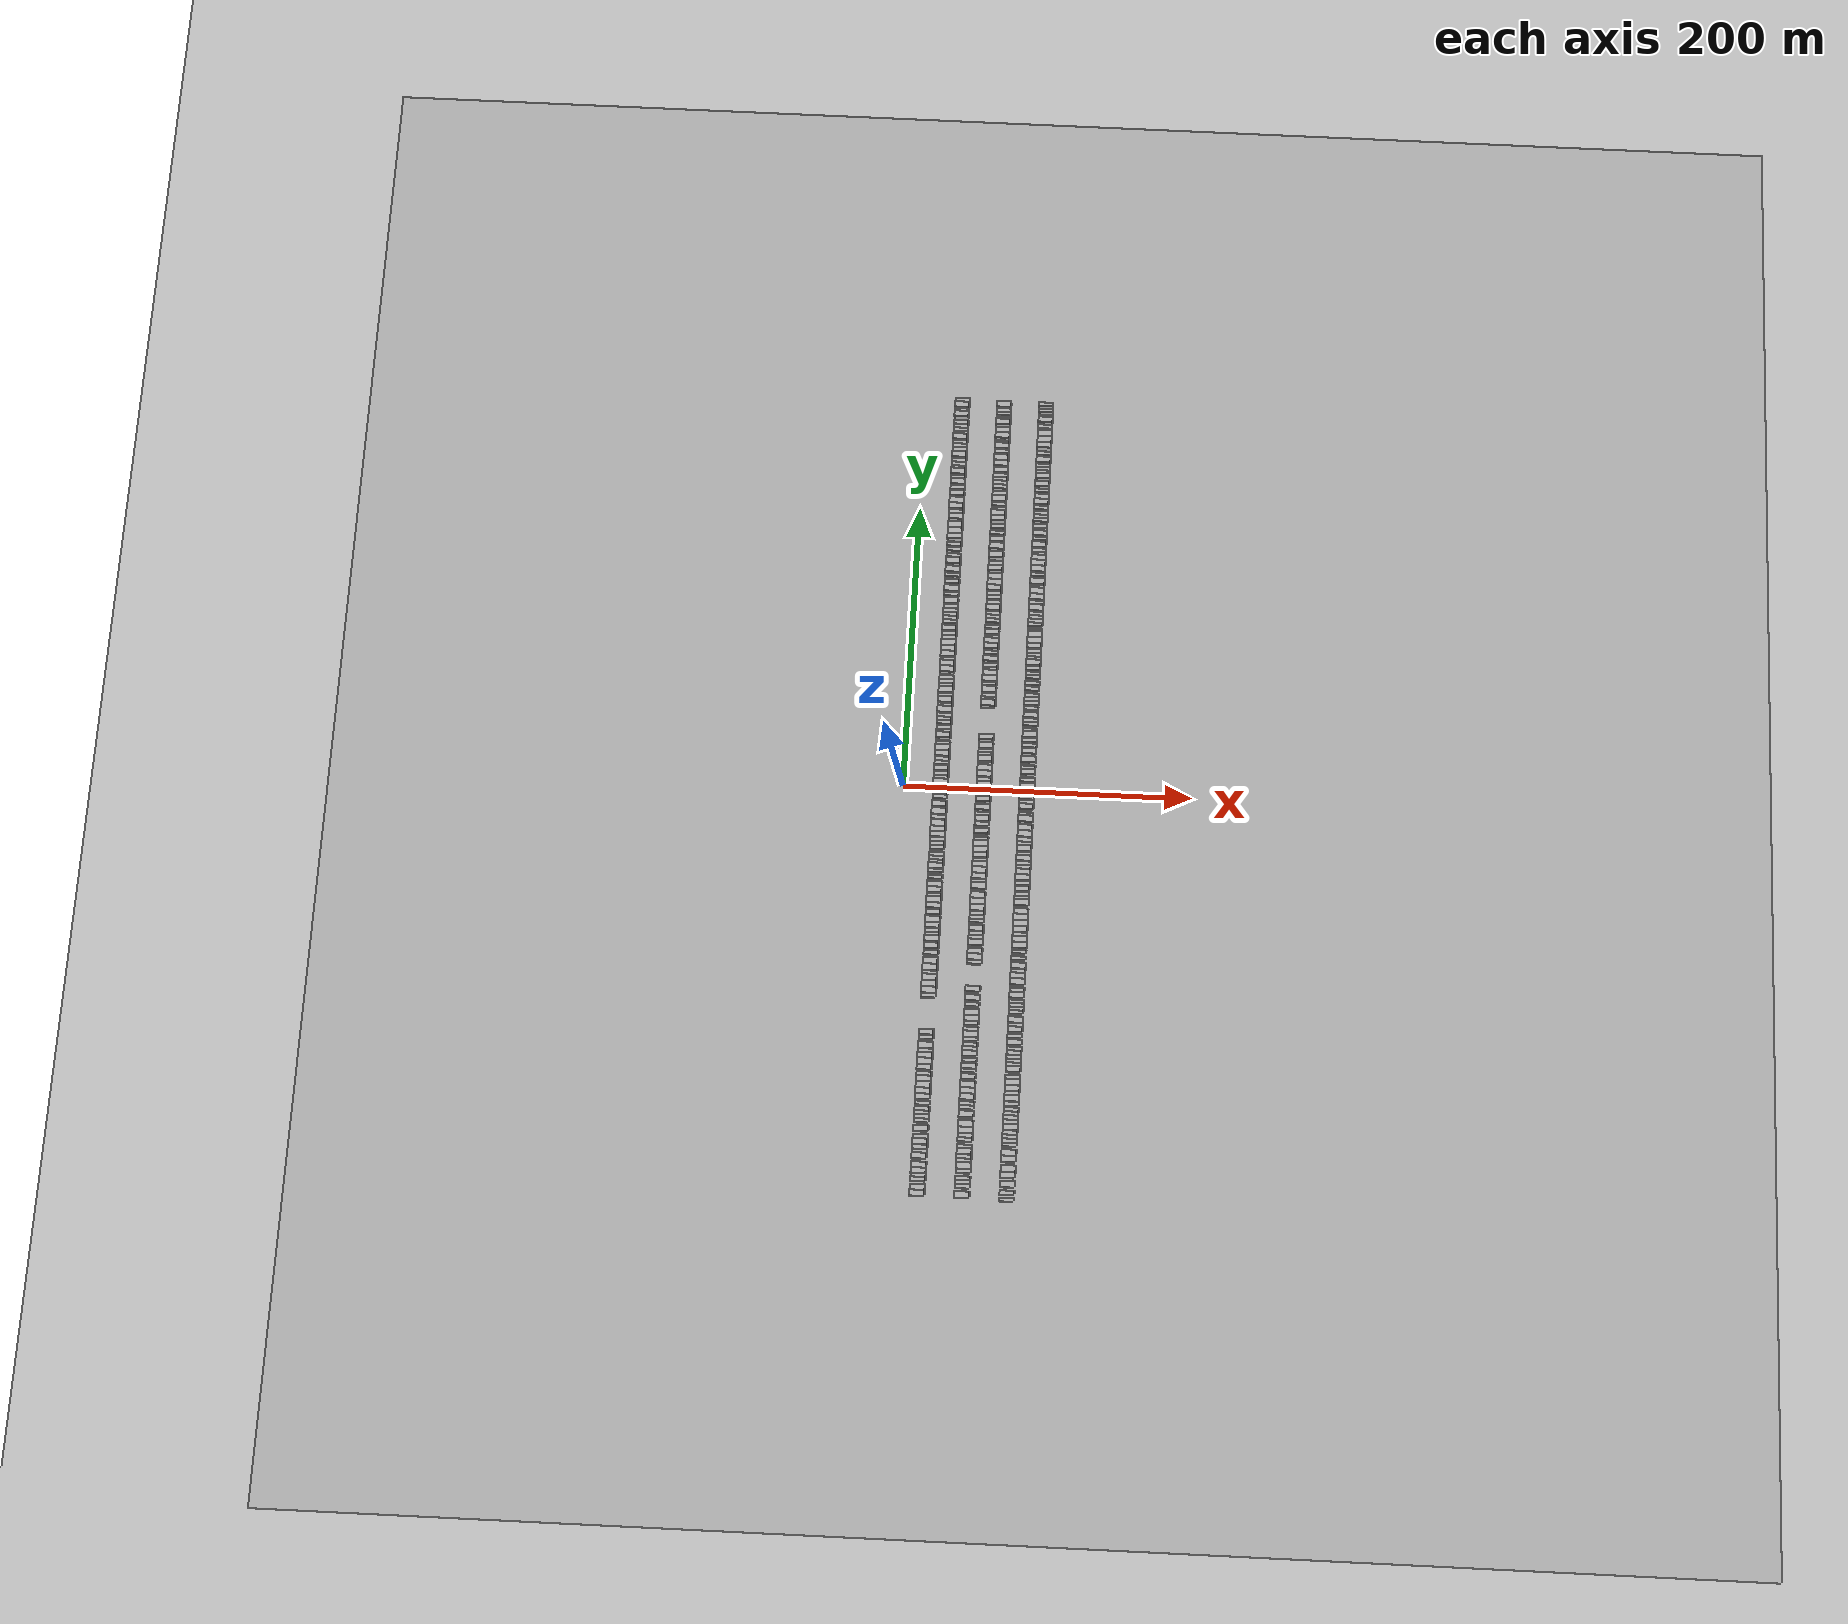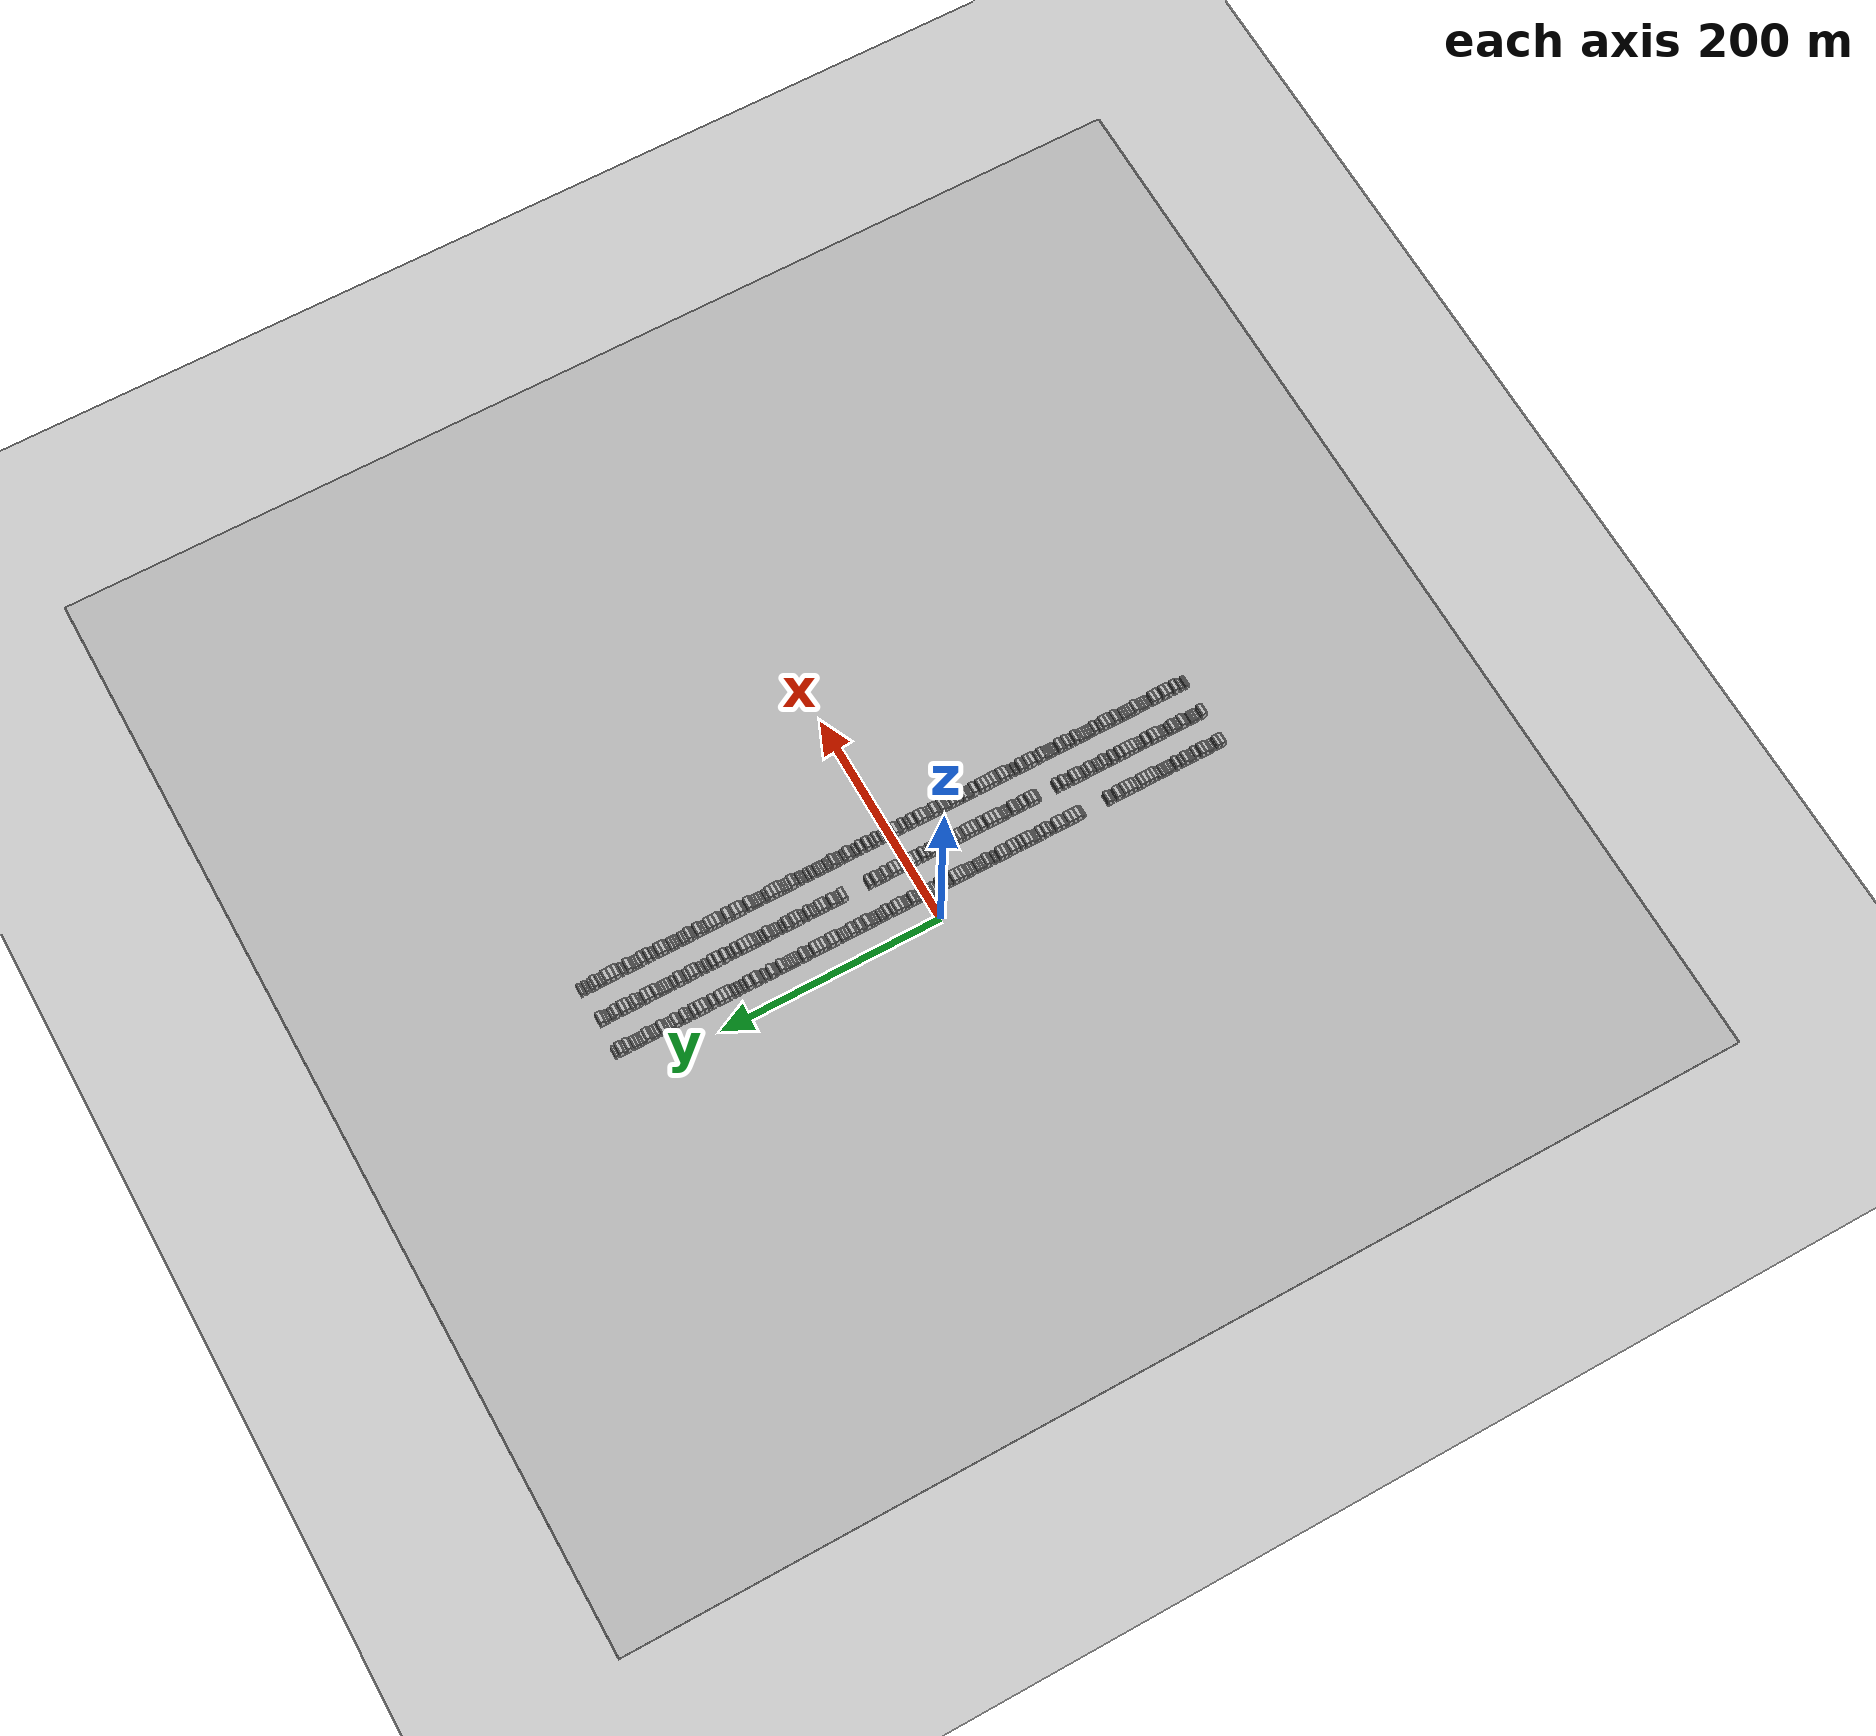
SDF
<?xml version="1.0" encoding="utf-8"?>

<sdf version="1.6">

   <world name="default">

      <gui fullscreen="0">

         <camera name="user_camera">

            <pose>-15 0 4.57585 0 0 0</pose>

            <view_controller>orbit</view_controller>

         </camera>

      </gui>

      <scene>

         <sky>

           <clouds>

             <speed>12</speed>

           </clouds>

         </sky>

         <ambient>0.4 0.4 0.4 1</ambient>

         <background>0.7 0.7 0.7 1</background>

         <shadows>1</shadows>

      </scene>

      <gravity>0 0 -9.8066</gravity>

      <magnetic_field>6e-06 2.3e-05 -4.2e-05</magnetic_field>

      <physics default="0" name="default_physics" type="ode">

         <ode>

            <solver>

               <type>quick</type>

               <iters>10</iters>

               <sor>1.0</sor>

               <use_dynamic_moi_rescaling>0</use_dynamic_moi_rescaling>

            </solver>

            <constraints>

               <cfm>0</cfm>

               <erp>0.2</erp>

               <contact_max_correcting_vel>100</contact_max_correcting_vel>

               <contact_surface_layer>0.001</contact_surface_layer>

            </constraints>

         </ode>

         <max_step_size>0.004</max_step_size>

         <real_time_factor>1</real_time_factor>

         <real_time_update_rate>250</real_time_update_rate>

      </physics>

      <light name="sun" type="directional">

         <cast_shadows>1</cast_shadows>

         <pose>0 0 10 0 0 0</pose>

         <diffuse>0.8 0.8 0.8 1</diffuse>

         <specular>0.2 0.2 0.2 1</specular>

         <attenuation>

            <range>1000</range>

            <constant>0.9</constant>

            <linear>0.01</linear>

            <quadratic>0.001</quadratic>

         </attenuation>

         <direction>-0.5 0.1 -0.9</direction>

      </light>

      <include>

         <name>ground_plane_1</name>

         <uri>model://HANNAS_ground_plane</uri>

         <pose>0 0 0  0 0 0</pose>

      </include>

      <include>

         <name>ground_plane_2</name>

         <uri>model://HANNAS_ground_plane</uri>

         <pose>100 0 0  0 0 0</pose>

      </include>

      <model name="building_1">

         <static>1</static>

         <pose frame="">25.0000 -276.9936 0 0.000000 0.000000 0.000000</pose>

         <link name="link">

            <pose frame="">0 0 4.50 0 0 0</pose>

            <collision name="collision">

               <geometry>

                  <box>

                     <size>10.0000 4.0128 9.0000</size>

                  </box>

               </geometry>

               <max_contacts>10</max_contacts>

               <surface>

                  <contact>

                     <ode/>

                  </contact>

                  <bounce/>

                  <friction>

                     <torsional>

                        <ode/>

                     </torsional>

                     <ode/>

                  </friction>

               </surface>

            </collision>

            <visual name="visual">

               <cast_shadows>0</cast_shadows>

               <geometry>

                  <box>

                     <size>10.0000 4.0128 9.0000</size>

                  </box>

               </geometry>

               <material>

                  <script>

                     <uri>model://HANNAS_wall/materials/scripts</uri>

                     <uri>model://HANNAS_wall/materials/textures</uri>

                     <name>vrc/HANNAS_wall</name>

                  </script>

               </material>

            </visual>

            <self_collide>0</self_collide>

            <enable_wind>0</enable_wind>

            <kinematic>0</kinematic>

         </link>

      </model>

      <model name="building_2">

         <static>1</static>

         <pose frame="">25.0000 -273.1018 0 0.000000 0.000000 0.000000</pose>

         <link name="link">

            <pose frame="">0 0 4.50 0 0 0</pose>

            <collision name="collision">

               <geometry>

                  <box>

                     <size>10.0000 3.7709 9.0000</size>

                  </box>

               </geometry>

               <max_contacts>10</max_contacts>

               <surface>

                  <contact>

                     <ode/>

                  </contact>

                  <bounce/>

                  <friction>

                     <torsional>

                        <ode/>

                     </torsional>

                     <ode/>

                  </friction>

               </surface>

            </collision>

            <visual name="visual">

               <cast_shadows>0</cast_shadows>

               <geometry>

                  <box>

                     <size>10.0000 3.7709 9.0000</size>

                  </box>

               </geometry>

               <material>

                  <script>

                     <uri>model://HANNAS_wall/materials/scripts</uri>

                     <uri>model://HANNAS_wall/materials/textures</uri>

                     <name>vrc/HANNAS_wall</name>

                  </script>

               </material>

            </visual>

            <self_collide>0</self_collide>

            <enable_wind>0</enable_wind>

            <kinematic>0</kinematic>

         </link>

      </model>

      <model name="building_3">

         <static>1</static>

         <pose frame="">25.0000 -267.7888 0 0.000000 0.000000 0.000000</pose>

         <link name="link">

            <pose frame="">0 0 3.00 0 0 0</pose>

            <collision name="collision">

               <geometry>

                  <box>

                     <size>10.0000 2.8552 6.0000</size>

                  </box>

               </geometry>

               <max_contacts>10</max_contacts>

               <surface>

                  <contact>

                     <ode/>

                  </contact>

                  <bounce/>

                  <friction>

                     <torsional>

                        <ode/>

                     </torsional>

                     <ode/>

                  </friction>

               </surface>

            </collision>

            <visual name="visual">

               <cast_shadows>0</cast_shadows>

               <geometry>

                  <box>

                     <size>10.0000 2.8552 6.0000</size>

                  </box>

               </geometry>

               <material>

                  <script>

                     <uri>model://HANNAS_wall/materials/scripts</uri>

                     <uri>model://HANNAS_wall/materials/textures</uri>

                     <name>vrc/HANNAS_wall</name>

                  </script>

               </material>

            </visual>

            <self_collide>0</self_collide>

            <enable_wind>0</enable_wind>

            <kinematic>0</kinematic>

         </link>

      </model>

      <model name="building_4">

         <static>1</static>

         <pose frame="">25.0000 -265.1364 0 0.000000 0.000000 0.000000</pose>

         <link name="link">

            <pose frame="">0 0 3.00 0 0 0</pose>

            <collision name="collision">

               <geometry>

                  <box>

                     <size>10.0000 2.4496 6.0000</size>

                  </box>

               </geometry>

               <max_contacts>10</max_contacts>

               <surface>

                  <contact>

                     <ode/>

                  </contact>

                  <bounce/>

                  <friction>

                     <torsional>

                        <ode/>

                     </torsional>

                     <ode/>

                  </friction>

               </surface>

            </collision>

            <visual name="visual">

               <cast_shadows>0</cast_shadows>

               <geometry>

                  <box>

                     <size>10.0000 2.4496 6.0000</size>

                  </box>

               </geometry>

               <material>

                  <script>

                     <uri>model://HANNAS_wall/materials/scripts</uri>

                     <uri>model://HANNAS_wall/materials/textures</uri>

                     <name>vrc/HANNAS_wall</name>

                  </script>

               </material>

            </visual>

            <self_collide>0</self_collide>

            <enable_wind>0</enable_wind>

            <kinematic>0</kinematic>

         </link>

      </model>

      <model name="building_5">

         <static>1</static>

         <pose frame="">25.0000 -262.1092 0 0.000000 0.000000 0.000000</pose>

         <link name="link">

            <pose frame="">0 0 4.50 0 0 0</pose>

            <collision name="collision">

               <geometry>

                  <box>

                     <size>10.0000 3.6049 9.0000</size>

                  </box>

               </geometry>

               <max_contacts>10</max_contacts>

               <surface>

                  <contact>

                     <ode/>

                  </contact>

                  <bounce/>

                  <friction>

                     <torsional>

                        <ode/>

                     </torsional>

                     <ode/>

                  </friction>

               </surface>

            </collision>

            <visual name="visual">

               <cast_shadows>0</cast_shadows>

               <geometry>

                  <box>

                     <size>10.0000 3.6049 9.0000</size>

                  </box>

               </geometry>

               <material>

                  <script>

                     <uri>model://HANNAS_wall/materials/scripts</uri>

                     <uri>model://HANNAS_wall/materials/textures</uri>

                     <name>vrc/HANNAS_wall</name>

                  </script>

               </material>

            </visual>

            <self_collide>0</self_collide>

            <enable_wind>0</enable_wind>

            <kinematic>0</kinematic>

         </link>

      </model>

      <model name="building_6">

         <static>1</static>

         <pose frame="">25.0000 -258.3489 0 0.000000 0.000000 0.000000</pose>

         <link name="link">

            <pose frame="">0 0 4.50 0 0 0</pose>

            <collision name="collision">

               <geometry>

                  <box>

                     <size>10.0000 3.9157 9.0000</size>

                  </box>

               </geometry>

               <max_contacts>10</max_contacts>

               <surface>

                  <contact>

                     <ode/>

                  </contact>

                  <bounce/>

                  <friction>

                     <torsional>

                        <ode/>

                     </torsional>

                     <ode/>

                  </friction>

               </surface>

            </collision>

            <visual name="visual">

               <cast_shadows>0</cast_shadows>

               <geometry>

                  <box>

                     <size>10.0000 3.9157 9.0000</size>

                  </box>

               </geometry>

               <material>

                  <script>

                     <uri>model://HANNAS_wall/materials/scripts</uri>

                     <uri>model://HANNAS_wall/materials/textures</uri>

                     <name>vrc/HANNAS_wall</name>

                  </script>

               </material>

            </visual>

            <self_collide>0</self_collide>

            <enable_wind>0</enable_wind>

            <kinematic>0</kinematic>

         </link>

      </model>

      <model name="building_7">

         <static>1</static>

         <pose frame="">25.0000 -252.3953 0 0.000000 0.000000 0.000000</pose>

         <link name="link">

            <pose frame="">0 0 4.50 0 0 0</pose>

            <collision name="collision">

               <geometry>

                  <box>

                     <size>10.0000 3.9916 9.0000</size>

                  </box>

               </geometry>

               <max_contacts>10</max_contacts>

               <surface>

                  <contact>

                     <ode/>

                  </contact>

                  <bounce/>

                  <friction>

                     <torsional>

                        <ode/>

                     </torsional>

                     <ode/>

                  </friction>

               </surface>

            </collision>

            <visual name="visual">

               <cast_shadows>0</cast_shadows>

               <geometry>

                  <box>

                     <size>10.0000 3.9916 9.0000</size>

                  </box>

               </geometry>

               <material>

                  <script>

                     <uri>model://HANNAS_wall/materials/scripts</uri>

                     <uri>model://HANNAS_wall/materials/textures</uri>

                     <name>vrc/HANNAS_wall</name>

                  </script>

               </material>

            </visual>

            <self_collide>0</self_collide>

            <enable_wind>0</enable_wind>

            <kinematic>0</kinematic>

         </link>

      </model>

      <model name="building_8">

         <static>1</static>

         <pose frame="">25.0000 -249.1652 0 0.000000 0.000000 0.000000</pose>

         <link name="link">

            <pose frame="">0 0 3.00 0 0 0</pose>

            <collision name="collision">

               <geometry>

                  <box>

                     <size>10.0000 2.4686 6.0000</size>

                  </box>

               </geometry>

               <max_contacts>10</max_contacts>

               <surface>

                  <contact>

                     <ode/>

                  </contact>

                  <bounce/>

                  <friction>

                     <torsional>

                        <ode/>

                     </torsional>

                     <ode/>

                  </friction>

               </surface>

            </collision>

            <visual name="visual">

               <cast_shadows>0</cast_shadows>

               <geometry>

                  <box>

                     <size>10.0000 2.4686 6.0000</size>

                  </box>

               </geometry>

               <material>

                  <script>

                     <uri>model://HANNAS_wall/materials/scripts</uri>

                     <uri>model://HANNAS_wall/materials/textures</uri>

                     <name>vrc/HANNAS_wall</name>

                  </script>

               </material>

            </visual>

            <self_collide>0</self_collide>

            <enable_wind>0</enable_wind>

            <kinematic>0</kinematic>

         </link>

      </model>

      <model name="building_9">

         <static>1</static>

         <pose frame="">25.0000 -246.4581 0 0.000000 0.000000 0.000000</pose>

         <link name="link">

            <pose frame="">0 0 3.00 0 0 0</pose>

            <collision name="collision">

               <geometry>

                  <box>

                     <size>10.0000 2.9456 6.0000</size>

                  </box>

               </geometry>

               <max_contacts>10</max_contacts>

               <surface>

                  <contact>

                     <ode/>

                  </contact>

                  <bounce/>

                  <friction>

                     <torsional>

                        <ode/>

                     </torsional>

                     <ode/>

                  </friction>

               </surface>

            </collision>

            <visual name="visual">

               <cast_shadows>0</cast_shadows>

               <geometry>

                  <box>

                     <size>10.0000 2.9456 6.0000</size>

                  </box>

               </geometry>

               <material>

                  <script>

                     <uri>model://HANNAS_wall/materials/scripts</uri>

                     <uri>model://HANNAS_wall/materials/textures</uri>

                     <name>vrc/HANNAS_wall</name>

                  </script>

               </material>

            </visual>

            <self_collide>0</self_collide>

            <enable_wind>0</enable_wind>

            <kinematic>0</kinematic>

         </link>

      </model>

      <model name="building_10">

         <static>1</static>

         <pose frame="">25.0000 -243.0096 0 0.000000 0.000000 0.000000</pose>

         <link name="link">

            <pose frame="">0 0 4.50 0 0 0</pose>

            <collision name="collision">

               <geometry>

                  <box>

                     <size>10.0000 3.9515 9.0000</size>

                  </box>

               </geometry>

               <max_contacts>10</max_contacts>

               <surface>

                  <contact>

                     <ode/>

                  </contact>

                  <bounce/>

                  <friction>

                     <torsional>

                        <ode/>

                     </torsional>

                     <ode/>

                  </friction>

               </surface>

            </collision>

            <visual name="visual">

               <cast_shadows>0</cast_shadows>

               <geometry>

                  <box>

                     <size>10.0000 3.9515 9.0000</size>

                  </box>

               </geometry>

               <material>

                  <script>

                     <uri>model://HANNAS_wall/materials/scripts</uri>

                     <uri>model://HANNAS_wall/materials/textures</uri>

                     <name>vrc/HANNAS_wall</name>

                  </script>

               </material>

            </visual>

            <self_collide>0</self_collide>

            <enable_wind>0</enable_wind>

            <kinematic>0</kinematic>

         </link>

      </model>

      <model name="building_11">

         <static>1</static>

         <pose frame="">25.0000 -239.6024 0 0.000000 0.000000 0.000000</pose>

         <link name="link">

            <pose frame="">0 0 3.00 0 0 0</pose>

            <collision name="collision">

               <geometry>

                  <box>

                     <size>10.0000 2.8628 6.0000</size>

                  </box>

               </geometry>

               <max_contacts>10</max_contacts>

               <surface>

                  <contact>

                     <ode/>

                  </contact>

                  <bounce/>

                  <friction>

                     <torsional>

                        <ode/>

                     </torsional>

                     <ode/>

                  </friction>

               </surface>

            </collision>

            <visual name="visual">

               <cast_shadows>0</cast_shadows>

               <geometry>

                  <box>

                     <size>10.0000 2.8628 6.0000</size>

                  </box>

               </geometry>

               <material>

                  <script>

                     <uri>model://HANNAS_wall/materials/scripts</uri>

                     <uri>model://HANNAS_wall/materials/textures</uri>

                     <name>vrc/HANNAS_wall</name>

                  </script>

               </material>

            </visual>

            <self_collide>0</self_collide>

            <enable_wind>0</enable_wind>

            <kinematic>0</kinematic>

         </link>

      </model>

      <model name="building_12">

         <static>1</static>

         <pose frame="">25.0000 -234.2247 0 0.000000 0.000000 0.000000</pose>

         <link name="link">

            <pose frame="">0 0 4.50 0 0 0</pose>

            <collision name="collision">

               <geometry>

                  <box>

                     <size>10.0000 3.8927 9.0000</size>

                  </box>

               </geometry>

               <max_contacts>10</max_contacts>

               <surface>

                  <contact>

                     <ode/>

                  </contact>

                  <bounce/>

                  <friction>

                     <torsional>

                        <ode/>

                     </torsional>

                     <ode/>

                  </friction>

               </surface>

            </collision>

            <visual name="visual">

               <cast_shadows>0</cast_shadows>

               <geometry>

                  <box>

                     <size>10.0000 3.8927 9.0000</size>

                  </box>

               </geometry>

               <material>

                  <script>

                     <uri>model://HANNAS_wall/materials/scripts</uri>

                     <uri>model://HANNAS_wall/materials/textures</uri>

                     <name>vrc/HANNAS_wall</name>

                  </script>

               </material>

            </visual>

            <self_collide>0</self_collide>

            <enable_wind>0</enable_wind>

            <kinematic>0</kinematic>

         </link>

      </model>

      <model name="building_13">

         <static>1</static>

         <pose frame="">25.0000 -228.9771 0 0.000000 0.000000 0.000000</pose>

         <link name="link">

            <pose frame="">0 0 3.00 0 0 0</pose>

            <collision name="collision">

               <geometry>

                  <box>

                     <size>10.0000 2.6024 6.0000</size>

                  </box>

               </geometry>

               <max_contacts>10</max_contacts>

               <surface>

                  <contact>

                     <ode/>

                  </contact>

                  <bounce/>

                  <friction>

                     <torsional>

                        <ode/>

                     </torsional>

                     <ode/>

                  </friction>

               </surface>

            </collision>

            <visual name="visual">

               <cast_shadows>0</cast_shadows>

               <geometry>

                  <box>

                     <size>10.0000 2.6024 6.0000</size>

                  </box>

               </geometry>

               <material>

                  <script>

                     <uri>model://HANNAS_wall/materials/scripts</uri>

                     <uri>model://HANNAS_wall/materials/textures</uri>

                     <name>vrc/HANNAS_wall</name>

                  </script>

               </material>

            </visual>

            <self_collide>0</self_collide>

            <enable_wind>0</enable_wind>

            <kinematic>0</kinematic>

         </link>

      </model>

      <model name="building_14">

         <static>1</static>

         <pose frame="">25.0000 -226.2507 0 0.000000 0.000000 0.000000</pose>

         <link name="link">

            <pose frame="">0 0 3.00 0 0 0</pose>

            <collision name="collision">

               <geometry>

                  <box>

                     <size>10.0000 2.8504 6.0000</size>

                  </box>

               </geometry>

               <max_contacts>10</max_contacts>

               <surface>

                  <contact>

                     <ode/>

                  </contact>

                  <bounce/>

                  <friction>

                     <torsional>

                        <ode/>

                     </torsional>

                     <ode/>

                  </friction>

               </surface>

            </collision>

            <visual name="visual">

               <cast_shadows>0</cast_shadows>

               <geometry>

                  <box>

                     <size>10.0000 2.8504 6.0000</size>

                  </box>

               </geometry>

               <material>

                  <script>

                     <uri>model://HANNAS_wall/materials/scripts</uri>

                     <uri>model://HANNAS_wall/materials/textures</uri>

                     <name>vrc/HANNAS_wall</name>

                  </script>

               </material>

            </visual>

            <self_collide>0</self_collide>

            <enable_wind>0</enable_wind>

            <kinematic>0</kinematic>

         </link>

      </model>

      <model name="building_15">

         <static>1</static>

         <pose frame="">25.0000 -223.5835 0 0.000000 0.000000 0.000000</pose>

         <link name="link">

            <pose frame="">0 0 3.00 0 0 0</pose>

            <collision name="collision">

               <geometry>

                  <box>

                     <size>10.0000 2.4840 6.0000</size>

                  </box>

               </geometry>

               <max_contacts>10</max_contacts>

               <surface>

                  <contact>

                     <ode/>

                  </contact>

                  <bounce/>

                  <friction>

                     <torsional>

                        <ode/>

                     </torsional>

                     <ode/>

                  </friction>

               </surface>

            </collision>

            <visual name="visual">

               <cast_shadows>0</cast_shadows>

               <geometry>

                  <box>

                     <size>10.0000 2.4840 6.0000</size>

                  </box>

               </geometry>

               <material>

                  <script>

                     <uri>model://HANNAS_wall/materials/scripts</uri>

                     <uri>model://HANNAS_wall/materials/textures</uri>

                     <name>vrc/HANNAS_wall</name>

                  </script>

               </material>

            </visual>

            <self_collide>0</self_collide>

            <enable_wind>0</enable_wind>

            <kinematic>0</kinematic>

         </link>

      </model>

      <model name="building_16">

         <static>1</static>

         <pose frame="">25.0000 -220.9449 0 0.000000 0.000000 0.000000</pose>

         <link name="link">

            <pose frame="">0 0 3.00 0 0 0</pose>

            <collision name="collision">

               <geometry>

                  <box>

                     <size>10.0000 2.7931 6.0000</size>

                  </box>

               </geometry>

               <max_contacts>10</max_contacts>

               <surface>

                  <contact>

                     <ode/>

                  </contact>

                  <bounce/>

                  <friction>

                     <torsional>

                        <ode/>

                     </torsional>

                     <ode/>

                  </friction>

               </surface>

            </collision>

            <visual name="visual">

               <cast_shadows>0</cast_shadows>

               <geometry>

                  <box>

                     <size>10.0000 2.7931 6.0000</size>

                  </box>

               </geometry>

               <material>

                  <script>

                     <uri>model://HANNAS_wall/materials/scripts</uri>

                     <uri>model://HANNAS_wall/materials/textures</uri>

                     <name>vrc/HANNAS_wall</name>

                  </script>

               </material>

            </visual>

            <self_collide>0</self_collide>

            <enable_wind>0</enable_wind>

            <kinematic>0</kinematic>

         </link>

      </model>

      <model name="building_17">

         <static>1</static>

         <pose frame="">25.0000 -217.2045 0 0.000000 0.000000 0.000000</pose>

         <link name="link">

            <pose frame="">0 0 3.00 0 0 0</pose>

            <collision name="collision">

               <geometry>

                  <box>

                     <size>10.0000 2.6878 6.0000</size>

                  </box>

               </geometry>

               <max_contacts>10</max_contacts>

               <surface>

                  <contact>

                     <ode/>

                  </contact>

                  <bounce/>

                  <friction>

                     <torsional>

                        <ode/>

                     </torsional>

                     <ode/>

                  </friction>

               </surface>

            </collision>

            <visual name="visual">

               <cast_shadows>0</cast_shadows>

               <geometry>

                  <box>

                     <size>10.0000 2.6878 6.0000</size>

                  </box>

               </geometry>

               <material>

                  <script>

                     <uri>model://HANNAS_wall/materials/scripts</uri>

                     <uri>model://HANNAS_wall/materials/textures</uri>

                     <name>vrc/HANNAS_wall</name>

                  </script>

               </material>

            </visual>

            <self_collide>0</self_collide>

            <enable_wind>0</enable_wind>

            <kinematic>0</kinematic>

         </link>

      </model>

      <model name="building_18">

         <static>1</static>

         <pose frame="">25.0000 -213.0085 0 0.000000 0.000000 0.000000</pose>

         <link name="link">

            <pose frame="">0 0 4.50 0 0 0</pose>

            <collision name="collision">

               <geometry>

                  <box>

                     <size>10.0000 3.7042 9.0000</size>

                  </box>

               </geometry>

               <max_contacts>10</max_contacts>

               <surface>

                  <contact>

                     <ode/>

                  </contact>

                  <bounce/>

                  <friction>

                     <torsional>

                        <ode/>

                     </torsional>

                     <ode/>

                  </friction>

               </surface>

            </collision>

            <visual name="visual">

               <cast_shadows>0</cast_shadows>

               <geometry>

                  <box>

                     <size>10.0000 3.7042 9.0000</size>

                  </box>

               </geometry>

               <material>

                  <script>

                     <uri>model://HANNAS_wall/materials/scripts</uri>

                     <uri>model://HANNAS_wall/materials/textures</uri>

                     <name>vrc/HANNAS_wall</name>

                  </script>

               </material>

            </visual>

            <self_collide>0</self_collide>

            <enable_wind>0</enable_wind>

            <kinematic>0</kinematic>

         </link>

      </model>

      <model name="building_19">

         <static>1</static>

         <pose frame="">25.0000 -209.1764 0 0.000000 0.000000 0.000000</pose>

         <link name="link">

            <pose frame="">0 0 4.50 0 0 0</pose>

            <collision name="collision">

               <geometry>

                  <box>

                     <size>10.0000 3.9599 9.0000</size>

                  </box>

               </geometry>

               <max_contacts>10</max_contacts>

               <surface>

                  <contact>

                     <ode/>

                  </contact>

                  <bounce/>

                  <friction>

                     <torsional>

                        <ode/>

                     </torsional>

                     <ode/>

                  </friction>

               </surface>

            </collision>

            <visual name="visual">

               <cast_shadows>0</cast_shadows>

               <geometry>

                  <box>

                     <size>10.0000 3.9599 9.0000</size>

                  </box>

               </geometry>

               <material>

                  <script>

                     <uri>model://HANNAS_wall/materials/scripts</uri>

                     <uri>model://HANNAS_wall/materials/textures</uri>

                     <name>vrc/HANNAS_wall</name>

                  </script>

               </material>

            </visual>

            <self_collide>0</self_collide>

            <enable_wind>0</enable_wind>

            <kinematic>0</kinematic>

         </link>

      </model>

      <model name="building_20">

         <static>1</static>

         <pose frame="">25.0000 -205.0404 0 0.000000 0.000000 0.000000</pose>

         <link name="link">

            <pose frame="">0 0 4.50 0 0 0</pose>

            <collision name="collision">

               <geometry>

                  <box>

                     <size>10.0000 4.3121 9.0000</size>

                  </box>

               </geometry>

               <max_contacts>10</max_contacts>

               <surface>

                  <contact>

                     <ode/>

                  </contact>

                  <bounce/>

                  <friction>

                     <torsional>

                        <ode/>

                     </torsional>

                     <ode/>

                  </friction>

               </surface>

            </collision>

            <visual name="visual">

               <cast_shadows>0</cast_shadows>

               <geometry>

                  <box>

                     <size>10.0000 4.3121 9.0000</size>

                  </box>

               </geometry>

               <material>

                  <script>

                     <uri>model://HANNAS_wall/materials/scripts</uri>

                     <uri>model://HANNAS_wall/materials/textures</uri>

                     <name>vrc/HANNAS_wall</name>

                  </script>

               </material>

            </visual>

            <self_collide>0</self_collide>

            <enable_wind>0</enable_wind>

            <kinematic>0</kinematic>

         </link>

      </model>

      <model name="building_21">

         <static>1</static>

         <pose frame="">25.0000 -200.9704 0 0.000000 0.000000 0.000000</pose>

         <link name="link">

            <pose frame="">0 0 4.50 0 0 0</pose>

            <collision name="collision">

               <geometry>

                  <box>

                     <size>10.0000 3.8279 9.0000</size>

                  </box>

               </geometry>

               <max_contacts>10</max_contacts>

               <surface>

                  <contact>

                     <ode/>

                  </contact>

                  <bounce/>

                  <friction>

                     <torsional>

                        <ode/>

                     </torsional>

                     <ode/>

                  </friction>

               </surface>

            </collision>

            <visual name="visual">

               <cast_shadows>0</cast_shadows>

               <geometry>

                  <box>

                     <size>10.0000 3.8279 9.0000</size>

                  </box>

               </geometry>

               <material>

                  <script>

                     <uri>model://HANNAS_wall/materials/scripts</uri>

                     <uri>model://HANNAS_wall/materials/textures</uri>

                     <name>vrc/HANNAS_wall</name>

                  </script>

               </material>

            </visual>

            <self_collide>0</self_collide>

            <enable_wind>0</enable_wind>

            <kinematic>0</kinematic>

         </link>

      </model>

      <model name="building_22">

         <static>1</static>

         <pose frame="">25.0000 -197.5957 0 0.000000 0.000000 0.000000</pose>

         <link name="link">

            <pose frame="">0 0 3.00 0 0 0</pose>

            <collision name="collision">

               <geometry>

                  <box>

                     <size>10.0000 2.9216 6.0000</size>

                  </box>

               </geometry>

               <max_contacts>10</max_contacts>

               <surface>

                  <contact>

                     <ode/>

                  </contact>

                  <bounce/>

                  <friction>

                     <torsional>

                        <ode/>

                     </torsional>

                     <ode/>

                  </friction>

               </surface>

            </collision>

            <visual name="visual">

               <cast_shadows>0</cast_shadows>

               <geometry>

                  <box>

                     <size>10.0000 2.9216 6.0000</size>

                  </box>

               </geometry>

               <material>

                  <script>

                     <uri>model://HANNAS_wall/materials/scripts</uri>

                     <uri>model://HANNAS_wall/materials/textures</uri>

                     <name>vrc/HANNAS_wall</name>

                  </script>

               </material>

            </visual>

            <self_collide>0</self_collide>

            <enable_wind>0</enable_wind>

            <kinematic>0</kinematic>

         </link>

      </model>

      <model name="building_23">

         <static>1</static>

         <pose frame="">25.0000 -193.3182 0 0.000000 0.000000 0.000000</pose>

         <link name="link">

            <pose frame="">0 0 4.50 0 0 0</pose>

            <collision name="collision">

               <geometry>

                  <box>

                     <size>10.0000 3.6334 9.0000</size>

                  </box>

               </geometry>

               <max_contacts>10</max_contacts>

               <surface>

                  <contact>

                     <ode/>

                  </contact>

                  <bounce/>

                  <friction>

                     <torsional>

                        <ode/>

                     </torsional>

                     <ode/>

                  </friction>

               </surface>

            </collision>

            <visual name="visual">

               <cast_shadows>0</cast_shadows>

               <geometry>

                  <box>

                     <size>10.0000 3.6334 9.0000</size>

                  </box>

               </geometry>

               <material>

                  <script>

                     <uri>model://HANNAS_wall/materials/scripts</uri>

                     <uri>model://HANNAS_wall/materials/textures</uri>

                     <name>vrc/HANNAS_wall</name>

                  </script>

               </material>

            </visual>

            <self_collide>0</self_collide>

            <enable_wind>0</enable_wind>

            <kinematic>0</kinematic>

         </link>

      </model>

      <model name="building_24">

         <static>1</static>

         <pose frame="">25.0000 -189.2866 0 0.000000 0.000000 0.000000</pose>

         <link name="link">

            <pose frame="">0 0 4.50 0 0 0</pose>

            <collision name="collision">

               <geometry>

                  <box>

                     <size>10.0000 4.4299 9.0000</size>

                  </box>

               </geometry>

               <max_contacts>10</max_contacts>

               <surface>

                  <contact>

                     <ode/>

                  </contact>

                  <bounce/>

                  <friction>

                     <torsional>

                        <ode/>

                     </torsional>

                     <ode/>

                  </friction>

               </surface>

            </collision>

            <visual name="visual">

               <cast_shadows>0</cast_shadows>

               <geometry>

                  <box>

                     <size>10.0000 4.4299 9.0000</size>

                  </box>

               </geometry>

               <material>

                  <script>

                     <uri>model://HANNAS_wall/materials/scripts</uri>

                     <uri>model://HANNAS_wall/materials/textures</uri>

                     <name>vrc/HANNAS_wall</name>

                  </script>

               </material>

            </visual>

            <self_collide>0</self_collide>

            <enable_wind>0</enable_wind>

            <kinematic>0</kinematic>

         </link>

      </model>

      <model name="building_25">

         <static>1</static>

         <pose frame="">25.0000 -185.2030 0 0.000000 0.000000 0.000000</pose>

         <link name="link">

            <pose frame="">0 0 4.50 0 0 0</pose>

            <collision name="collision">

               <geometry>

                  <box>

                     <size>10.0000 3.7373 9.0000</size>

                  </box>

               </geometry>

               <max_contacts>10</max_contacts>

               <surface>

                  <contact>

                     <ode/>

                  </contact>

                  <bounce/>

                  <friction>

                     <torsional>

                        <ode/>

                     </torsional>

                     <ode/>

                  </friction>

               </surface>

            </collision>

            <visual name="visual">

               <cast_shadows>0</cast_shadows>

               <geometry>

                  <box>

                     <size>10.0000 3.7373 9.0000</size>

                  </box>

               </geometry>

               <material>

                  <script>

                     <uri>model://HANNAS_wall/materials/scripts</uri>

                     <uri>model://HANNAS_wall/materials/textures</uri>

                     <name>vrc/HANNAS_wall</name>

                  </script>

               </material>

            </visual>

            <self_collide>0</self_collide>

            <enable_wind>0</enable_wind>

            <kinematic>0</kinematic>

         </link>

      </model>

      <model name="building_26">

         <static>1</static>

         <pose frame="">25.0000 -182.0148 0 0.000000 0.000000 0.000000</pose>

         <link name="link">

            <pose frame="">0 0 3.00 0 0 0</pose>

            <collision name="collision">

               <geometry>

                  <box>

                     <size>10.0000 2.6391 6.0000</size>

                  </box>

               </geometry>

               <max_contacts>10</max_contacts>

               <surface>

                  <contact>

                     <ode/>

                  </contact>

                  <bounce/>

                  <friction>

                     <torsional>

                        <ode/>

                     </torsional>

                     <ode/>

                  </friction>

               </surface>

            </collision>

            <visual name="visual">

               <cast_shadows>0</cast_shadows>

               <geometry>

                  <box>

                     <size>10.0000 2.6391 6.0000</size>

                  </box>

               </geometry>

               <material>

                  <script>

                     <uri>model://HANNAS_wall/materials/scripts</uri>

                     <uri>model://HANNAS_wall/materials/textures</uri>

                     <name>vrc/HANNAS_wall</name>

                  </script>

               </material>

            </visual>

            <self_collide>0</self_collide>

            <enable_wind>0</enable_wind>

            <kinematic>0</kinematic>

         </link>

      </model>

      <model name="building_27">

         <static>1</static>

         <pose frame="">25.0000 -178.4865 0 0.000000 0.000000 0.000000</pose>

         <link name="link">

            <pose frame="">0 0 4.50 0 0 0</pose>

            <collision name="collision">

               <geometry>

                  <box>

                     <size>10.0000 4.4174 9.0000</size>

                  </box>

               </geometry>

               <max_contacts>10</max_contacts>

               <surface>

                  <contact>

                     <ode/>

                  </contact>

                  <bounce/>

                  <friction>

                     <torsional>

                        <ode/>

                     </torsional>

                     <ode/>

                  </friction>

               </surface>

            </collision>

            <visual name="visual">

               <cast_shadows>0</cast_shadows>

               <geometry>

                  <box>

                     <size>10.0000 4.4174 9.0000</size>

                  </box>

               </geometry>

               <material>

                  <script>

                     <uri>model://HANNAS_wall/materials/scripts</uri>

                     <uri>model://HANNAS_wall/materials/textures</uri>

                     <name>vrc/HANNAS_wall</name>

                  </script>

               </material>

            </visual>

            <self_collide>0</self_collide>

            <enable_wind>0</enable_wind>

            <kinematic>0</kinematic>

         </link>

      </model>

      <model name="building_28">

         <static>1</static>

         <pose frame="">25.0000 -172.8996 0 0.000000 0.000000 0.000000</pose>

         <link name="link">

            <pose frame="">0 0 3.00 0 0 0</pose>

            <collision name="collision">

               <geometry>

                  <box>

                     <size>10.0000 2.7565 6.0000</size>

                  </box>

               </geometry>

               <max_contacts>10</max_contacts>

               <surface>

                  <contact>

                     <ode/>

                  </contact>

                  <bounce/>

                  <friction>

                     <torsional>

                        <ode/>

                     </torsional>

                     <ode/>

                  </friction>

               </surface>

            </collision>

            <visual name="visual">

               <cast_shadows>0</cast_shadows>

               <geometry>

                  <box>

                     <size>10.0000 2.7565 6.0000</size>

                  </box>

               </geometry>

               <material>

                  <script>

                     <uri>model://HANNAS_wall/materials/scripts</uri>

                     <uri>model://HANNAS_wall/materials/textures</uri>

                     <name>vrc/HANNAS_wall</name>

                  </script>

               </material>

            </visual>

            <self_collide>0</self_collide>

            <enable_wind>0</enable_wind>

            <kinematic>0</kinematic>

         </link>

      </model>

      <model name="building_29">

         <static>1</static>

         <pose frame="">25.0000 -169.7082 0 0.000000 0.000000 0.000000</pose>

         <link name="link">

            <pose frame="">0 0 4.50 0 0 0</pose>

            <collision name="collision">

               <geometry>

                  <box>

                     <size>10.0000 3.6262 9.0000</size>

                  </box>

               </geometry>

               <max_contacts>10</max_contacts>

               <surface>

                  <contact>

                     <ode/>

                  </contact>

                  <bounce/>

                  <friction>

                     <torsional>

                        <ode/>

                     </torsional>

                     <ode/>

                  </friction>

               </surface>

            </collision>

            <visual name="visual">

               <cast_shadows>0</cast_shadows>

               <geometry>

                  <box>

                     <size>10.0000 3.6262 9.0000</size>

                  </box>

               </geometry>

               <material>

                  <script>

                     <uri>model://HANNAS_wall/materials/scripts</uri>

                     <uri>model://HANNAS_wall/materials/textures</uri>

                     <name>vrc/HANNAS_wall</name>

                  </script>

               </material>

            </visual>

            <self_collide>0</self_collide>

            <enable_wind>0</enable_wind>

            <kinematic>0</kinematic>

         </link>

      </model>

      <model name="building_30">

         <static>1</static>

         <pose frame="">25.0000 -144.6660 0 0.000000 0.000000 0.000000</pose>

         <link name="link">

            <pose frame="">0 0 3.00 0 0 0</pose>

            <collision name="collision">

               <geometry>

                  <box>

                     <size>10.0000 2.8195 6.0000</size>

                  </box>

               </geometry>

               <max_contacts>10</max_contacts>

               <surface>

                  <contact>

                     <ode/>

                  </contact>

                  <bounce/>

                  <friction>

                     <torsional>

                        <ode/>

                     </torsional>

                     <ode/>

                  </friction>

               </surface>

            </collision>

            <visual name="visual">

               <cast_shadows>0</cast_shadows>

               <geometry>

                  <box>

                     <size>10.0000 2.8195 6.0000</size>

                  </box>

               </geometry>

               <material>

                  <script>

                     <uri>model://HANNAS_wall/materials/scripts</uri>

                     <uri>model://HANNAS_wall/materials/textures</uri>

                     <name>vrc/HANNAS_wall</name>

                  </script>

               </material>

            </visual>

            <self_collide>0</self_collide>

            <enable_wind>0</enable_wind>

            <kinematic>0</kinematic>

         </link>

      </model>

      <model name="building_31">

         <static>1</static>

         <pose frame="">25.0000 -141.0924 0 0.000000 0.000000 0.000000</pose>

         <link name="link">

            <pose frame="">0 0 4.50 0 0 0</pose>

            <collision name="collision">

               <geometry>

                  <box>

                     <size>10.0000 4.3277 9.0000</size>

                  </box>

               </geometry>

               <max_contacts>10</max_contacts>

               <surface>

                  <contact>

                     <ode/>

                  </contact>

                  <bounce/>

                  <friction>

                     <torsional>

                        <ode/>

                     </torsional>

                     <ode/>

                  </friction>

               </surface>

            </collision>

            <visual name="visual">

               <cast_shadows>0</cast_shadows>

               <geometry>

                  <box>

                     <size>10.0000 4.3277 9.0000</size>

                  </box>

               </geometry>

               <material>

                  <script>

                     <uri>model://HANNAS_wall/materials/scripts</uri>

                     <uri>model://HANNAS_wall/materials/textures</uri>

                     <name>vrc/HANNAS_wall</name>

                  </script>

               </material>

            </visual>

            <self_collide>0</self_collide>

            <enable_wind>0</enable_wind>

            <kinematic>0</kinematic>

         </link>

      </model>

      <model name="building_32">

         <static>1</static>

         <pose frame="">25.0000 -136.7739 0 0.000000 0.000000 0.000000</pose>

         <link name="link">

            <pose frame="">0 0 4.50 0 0 0</pose>

            <collision name="collision">

               <geometry>

                  <box>

                     <size>10.0000 4.3092 9.0000</size>

                  </box>

               </geometry>

               <max_contacts>10</max_contacts>

               <surface>

                  <contact>

                     <ode/>

                  </contact>

                  <bounce/>

                  <friction>

                     <torsional>

                        <ode/>

                     </torsional>

                     <ode/>

                  </friction>

               </surface>

            </collision>

            <visual name="visual">

               <cast_shadows>0</cast_shadows>

               <geometry>

                  <box>

                     <size>10.0000 4.3092 9.0000</size>

                  </box>

               </geometry>

               <material>

                  <script>

                     <uri>model://HANNAS_wall/materials/scripts</uri>

                     <uri>model://HANNAS_wall/materials/textures</uri>

                     <name>vrc/HANNAS_wall</name>

                  </script>

               </material>

            </visual>

            <self_collide>0</self_collide>

            <enable_wind>0</enable_wind>

            <kinematic>0</kinematic>

         </link>

      </model>

      <model name="building_33">

         <static>1</static>

         <pose frame="">25.0000 -132.4627 0 0.000000 0.000000 0.000000</pose>

         <link name="link">

            <pose frame="">0 0 4.50 0 0 0</pose>

            <collision name="collision">

               <geometry>

                  <box>

                     <size>10.0000 4.3133 9.0000</size>

                  </box>

               </geometry>

               <max_contacts>10</max_contacts>

               <surface>

                  <contact>

                     <ode/>

                  </contact>

                  <bounce/>

                  <friction>

                     <torsional>

                        <ode/>

                     </torsional>

                     <ode/>

                  </friction>

               </surface>

            </collision>

            <visual name="visual">

               <cast_shadows>0</cast_shadows>

               <geometry>

                  <box>

                     <size>10.0000 4.3133 9.0000</size>

                  </box>

               </geometry>

               <material>

                  <script>

                     <uri>model://HANNAS_wall/materials/scripts</uri>

                     <uri>model://HANNAS_wall/materials/textures</uri>

                     <name>vrc/HANNAS_wall</name>

                  </script>

               </material>

            </visual>

            <self_collide>0</self_collide>

            <enable_wind>0</enable_wind>

            <kinematic>0</kinematic>

         </link>

      </model>

      <model name="building_34">

         <static>1</static>

         <pose frame="">25.0000 -129.0370 0 0.000000 0.000000 0.000000</pose>

         <link name="link">

            <pose frame="">0 0 3.00 0 0 0</pose>

            <collision name="collision">

               <geometry>

                  <box>

                     <size>10.0000 2.5381 6.0000</size>

                  </box>

               </geometry>

               <max_contacts>10</max_contacts>

               <surface>

                  <contact>

                     <ode/>

                  </contact>

                  <bounce/>

                  <friction>

                     <torsional>

                        <ode/>

                     </torsional>

                     <ode/>

                  </friction>

               </surface>

            </collision>

            <visual name="visual">

               <cast_shadows>0</cast_shadows>

               <geometry>

                  <box>

                     <size>10.0000 2.5381 6.0000</size>

                  </box>

               </geometry>

               <material>

                  <script>

                     <uri>model://HANNAS_wall/materials/scripts</uri>

                     <uri>model://HANNAS_wall/materials/textures</uri>

                     <name>vrc/HANNAS_wall</name>

                  </script>

               </material>

            </visual>

            <self_collide>0</self_collide>

            <enable_wind>0</enable_wind>

            <kinematic>0</kinematic>

         </link>

      </model>

      <model name="building_35">

         <static>1</static>

         <pose frame="">25.0000 -125.5571 0 0.000000 0.000000 0.000000</pose>

         <link name="link">

            <pose frame="">0 0 4.50 0 0 0</pose>

            <collision name="collision">

               <geometry>

                  <box>

                     <size>10.0000 4.4215 9.0000</size>

                  </box>

               </geometry>

               <max_contacts>10</max_contacts>

               <surface>

                  <contact>

                     <ode/>

                  </contact>

                  <bounce/>

                  <friction>

                     <torsional>

                        <ode/>

                     </torsional>

                     <ode/>

                  </friction>

               </surface>

            </collision>

            <visual name="visual">

               <cast_shadows>0</cast_shadows>

               <geometry>

                  <box>

                     <size>10.0000 4.4215 9.0000</size>

                  </box>

               </geometry>

               <material>

                  <script>

                     <uri>model://HANNAS_wall/materials/scripts</uri>

                     <uri>model://HANNAS_wall/materials/textures</uri>

                     <name>vrc/HANNAS_wall</name>

                  </script>

               </material>

            </visual>

            <self_collide>0</self_collide>

            <enable_wind>0</enable_wind>

            <kinematic>0</kinematic>

         </link>

      </model>

      <model name="building_36">

         <static>1</static>

         <pose frame="">25.0000 -121.1176 0 0.000000 0.000000 0.000000</pose>

         <link name="link">

            <pose frame="">0 0 4.50 0 0 0</pose>

            <collision name="collision">

               <geometry>

                  <box>

                     <size>10.0000 4.4574 9.0000</size>

                  </box>

               </geometry>

               <max_contacts>10</max_contacts>

               <surface>

                  <contact>

                     <ode/>

                  </contact>

                  <bounce/>

                  <friction>

                     <torsional>

                        <ode/>

                     </torsional>

                     <ode/>

                  </friction>

               </surface>

            </collision>

            <visual name="visual">

               <cast_shadows>0</cast_shadows>

               <geometry>

                  <box>

                     <size>10.0000 4.4574 9.0000</size>

                  </box>

               </geometry>

               <material>

                  <script>

                     <uri>model://HANNAS_wall/materials/scripts</uri>

                     <uri>model://HANNAS_wall/materials/textures</uri>

                     <name>vrc/HANNAS_wall</name>

                  </script>

               </material>

            </visual>

            <self_collide>0</self_collide>

            <enable_wind>0</enable_wind>

            <kinematic>0</kinematic>

         </link>

      </model>

      <model name="building_37">

         <static>1</static>

         <pose frame="">25.0000 -115.3986 0 0.000000 0.000000 0.000000</pose>

         <link name="link">

            <pose frame="">0 0 3.00 0 0 0</pose>

            <collision name="collision">

               <geometry>

                  <box>

                     <size>10.0000 2.9807 6.0000</size>

                  </box>

               </geometry>

               <max_contacts>10</max_contacts>

               <surface>

                  <contact>

                     <ode/>

                  </contact>

                  <bounce/>

                  <friction>

                     <torsional>

                        <ode/>

                     </torsional>

                     <ode/>

                  </friction>

               </surface>

            </collision>

            <visual name="visual">

               <cast_shadows>0</cast_shadows>

               <geometry>

                  <box>

                     <size>10.0000 2.9807 6.0000</size>

                  </box>

               </geometry>

               <material>

                  <script>

                     <uri>model://HANNAS_wall/materials/scripts</uri>

                     <uri>model://HANNAS_wall/materials/textures</uri>

                     <name>vrc/HANNAS_wall</name>

                  </script>

               </material>

            </visual>

            <self_collide>0</self_collide>

            <enable_wind>0</enable_wind>

            <kinematic>0</kinematic>

         </link>

      </model>

      <model name="building_38">

         <static>1</static>

         <pose frame="">25.0000 -110.8825 0 0.000000 0.000000 0.000000</pose>

         <link name="link">

            <pose frame="">0 0 4.50 0 0 0</pose>

            <collision name="collision">

               <geometry>

                  <box>

                     <size>10.0000 4.0514 9.0000</size>

                  </box>

               </geometry>

               <max_contacts>10</max_contacts>

               <surface>

                  <contact>

                     <ode/>

                  </contact>

                  <bounce/>

                  <friction>

                     <torsional>

                        <ode/>

                     </torsional>

                     <ode/>

                  </friction>

               </surface>

            </collision>

            <visual name="visual">

               <cast_shadows>0</cast_shadows>

               <geometry>

                  <box>

                     <size>10.0000 4.0514 9.0000</size>

                  </box>

               </geometry>

               <material>

                  <script>

                     <uri>model://HANNAS_wall/materials/scripts</uri>

                     <uri>model://HANNAS_wall/materials/textures</uri>

                     <name>vrc/HANNAS_wall</name>

                  </script>

               </material>

            </visual>

            <self_collide>0</self_collide>

            <enable_wind>0</enable_wind>

            <kinematic>0</kinematic>

         </link>

      </model>

      <model name="building_39">

         <static>1</static>

         <pose frame="">25.0000 -105.8816 0 0.000000 0.000000 0.000000</pose>

         <link name="link">

            <pose frame="">0 0 4.50 0 0 0</pose>

            <collision name="collision">

               <geometry>

                  <box>

                     <size>10.0000 3.9504 9.0000</size>

                  </box>

               </geometry>

               <max_contacts>10</max_contacts>

               <surface>

                  <contact>

                     <ode/>

                  </contact>

                  <bounce/>

                  <friction>

                     <torsional>

                        <ode/>

                     </torsional>

                     <ode/>

                  </friction>

               </surface>

            </collision>

            <visual name="visual">

               <cast_shadows>0</cast_shadows>

               <geometry>

                  <box>

                     <size>10.0000 3.9504 9.0000</size>

                  </box>

               </geometry>

               <material>

                  <script>

                     <uri>model://HANNAS_wall/materials/scripts</uri>

                     <uri>model://HANNAS_wall/materials/textures</uri>

                     <name>vrc/HANNAS_wall</name>

                  </script>

               </material>

            </visual>

            <self_collide>0</self_collide>

            <enable_wind>0</enable_wind>

            <kinematic>0</kinematic>

         </link>

      </model>

      <model name="building_40">

         <static>1</static>

         <pose frame="">25.0000 -102.6964 0 0.000000 0.000000 0.000000</pose>

         <link name="link">

            <pose frame="">0 0 3.00 0 0 0</pose>

            <collision name="collision">

               <geometry>

                  <box>

                     <size>10.0000 2.4201 6.0000</size>

                  </box>

               </geometry>

               <max_contacts>10</max_contacts>

               <surface>

                  <contact>

                     <ode/>

                  </contact>

                  <bounce/>

                  <friction>

                     <torsional>

                        <ode/>

                     </torsional>

                     <ode/>

                  </friction>

               </surface>

            </collision>

            <visual name="visual">

               <cast_shadows>0</cast_shadows>

               <geometry>

                  <box>

                     <size>10.0000 2.4201 6.0000</size>

                  </box>

               </geometry>

               <material>

                  <script>

                     <uri>model://HANNAS_wall/materials/scripts</uri>

                     <uri>model://HANNAS_wall/materials/textures</uri>

                     <name>vrc/HANNAS_wall</name>

                  </script>

               </material>

            </visual>

            <self_collide>0</self_collide>

            <enable_wind>0</enable_wind>

            <kinematic>0</kinematic>

         </link>

      </model>

      <model name="building_41">

         <static>1</static>

         <pose frame="">25.0000 -100.0586 0 0.000000 0.000000 0.000000</pose>

         <link name="link">

            <pose frame="">0 0 3.00 0 0 0</pose>

            <collision name="collision">

               <geometry>

                  <box>

                     <size>10.0000 2.8555 6.0000</size>

                  </box>

               </geometry>

               <max_contacts>10</max_contacts>

               <surface>

                  <contact>

                     <ode/>

                  </contact>

                  <bounce/>

                  <friction>

                     <torsional>

                        <ode/>

                     </torsional>

                     <ode/>

                  </friction>

               </surface>

            </collision>

            <visual name="visual">

               <cast_shadows>0</cast_shadows>

               <geometry>

                  <box>

                     <size>10.0000 2.8555 6.0000</size>

                  </box>

               </geometry>

               <material>

                  <script>

                     <uri>model://HANNAS_wall/materials/scripts</uri>

                     <uri>model://HANNAS_wall/materials/textures</uri>

                     <name>vrc/HANNAS_wall</name>

                  </script>

               </material>

            </visual>

            <self_collide>0</self_collide>

            <enable_wind>0</enable_wind>

            <kinematic>0</kinematic>

         </link>

      </model>

      <model name="building_42">

         <static>1</static>

         <pose frame="">25.0000 -96.8049 0 0.000000 0.000000 0.000000</pose>

         <link name="link">

            <pose frame="">0 0 4.50 0 0 0</pose>

            <collision name="collision">

               <geometry>

                  <box>

                     <size>10.0000 3.6517 9.0000</size>

                  </box>

               </geometry>

               <max_contacts>10</max_contacts>

               <surface>

                  <contact>

                     <ode/>

                  </contact>

                  <bounce/>

                  <friction>

                     <torsional>

                        <ode/>

                     </torsional>

                     <ode/>

                  </friction>

               </surface>

            </collision>

            <visual name="visual">

               <cast_shadows>0</cast_shadows>

               <geometry>

                  <box>

                     <size>10.0000 3.6517 9.0000</size>

                  </box>

               </geometry>

               <material>

                  <script>

                     <uri>model://HANNAS_wall/materials/scripts</uri>

                     <uri>model://HANNAS_wall/materials/textures</uri>

                     <name>vrc/HANNAS_wall</name>

                  </script>

               </material>

            </visual>

            <self_collide>0</self_collide>

            <enable_wind>0</enable_wind>

            <kinematic>0</kinematic>

         </link>

      </model>

      <model name="building_43">

         <static>1</static>

         <pose frame="">25.0000 -92.7702 0 0.000000 0.000000 0.000000</pose>

         <link name="link">

            <pose frame="">0 0 4.50 0 0 0</pose>

            <collision name="collision">

               <geometry>

                  <box>

                     <size>10.0000 4.4177 9.0000</size>

                  </box>

               </geometry>

               <max_contacts>10</max_contacts>

               <surface>

                  <contact>

                     <ode/>

                  </contact>

                  <bounce/>

                  <friction>

                     <torsional>

                        <ode/>

                     </torsional>

                     <ode/>

                  </friction>

               </surface>

            </collision>

            <visual name="visual">

               <cast_shadows>0</cast_shadows>

               <geometry>

                  <box>

                     <size>10.0000 4.4177 9.0000</size>

                  </box>

               </geometry>

               <material>

                  <script>

                     <uri>model://HANNAS_wall/materials/scripts</uri>

                     <uri>model://HANNAS_wall/materials/textures</uri>

                     <name>vrc/HANNAS_wall</name>

                  </script>

               </material>

            </visual>

            <self_collide>0</self_collide>

            <enable_wind>0</enable_wind>

            <kinematic>0</kinematic>

         </link>

      </model>

      <model name="building_44">

         <static>1</static>

         <pose frame="">25.0000 -87.7574 0 0.000000 0.000000 0.000000</pose>

         <link name="link">

            <pose frame="">0 0 4.50 0 0 0</pose>

            <collision name="collision">

               <geometry>

                  <box>

                     <size>10.0000 3.6081 9.0000</size>

                  </box>

               </geometry>

               <max_contacts>10</max_contacts>

               <surface>

                  <contact>

                     <ode/>

                  </contact>

                  <bounce/>

                  <friction>

                     <torsional>

                        <ode/>

                     </torsional>

                     <ode/>

                  </friction>

               </surface>

            </collision>

            <visual name="visual">

               <cast_shadows>0</cast_shadows>

               <geometry>

                  <box>

                     <size>10.0000 3.6081 9.0000</size>

                  </box>

               </geometry>

               <material>

                  <script>

                     <uri>model://HANNAS_wall/materials/scripts</uri>

                     <uri>model://HANNAS_wall/materials/textures</uri>

                     <name>vrc/HANNAS_wall</name>

                  </script>

               </material>

            </visual>

            <self_collide>0</self_collide>

            <enable_wind>0</enable_wind>

            <kinematic>0</kinematic>

         </link>

      </model>

      <model name="building_45">

         <static>1</static>

         <pose frame="">25.0000 -83.1467 0 0.000000 0.000000 0.000000</pose>

         <link name="link">

            <pose frame="">0 0 4.50 0 0 0</pose>

            <collision name="collision">

               <geometry>

                  <box>

                     <size>10.0000 3.6132 9.0000</size>

                  </box>

               </geometry>

               <max_contacts>10</max_contacts>

               <surface>

                  <contact>

                     <ode/>

                  </contact>

                  <bounce/>

                  <friction>

                     <torsional>

                        <ode/>

                     </torsional>

                     <ode/>

                  </friction>

               </surface>

            </collision>

            <visual name="visual">

               <cast_shadows>0</cast_shadows>

               <geometry>

                  <box>

                     <size>10.0000 3.6132 9.0000</size>

                  </box>

               </geometry>

               <material>

                  <script>

                     <uri>model://HANNAS_wall/materials/scripts</uri>

                     <uri>model://HANNAS_wall/materials/textures</uri>

                     <name>vrc/HANNAS_wall</name>

                  </script>

               </material>

            </visual>

            <self_collide>0</self_collide>

            <enable_wind>0</enable_wind>

            <kinematic>0</kinematic>

         </link>

      </model>

      <model name="building_46">

         <static>1</static>

         <pose frame="">25.0000 -79.1482 0 0.000000 0.000000 0.000000</pose>

         <link name="link">

            <pose frame="">0 0 4.50 0 0 0</pose>

            <collision name="collision">

               <geometry>

                  <box>

                     <size>10.0000 4.3839 9.0000</size>

                  </box>

               </geometry>

               <max_contacts>10</max_contacts>

               <surface>

                  <contact>

                     <ode/>

                  </contact>

                  <bounce/>

                  <friction>

                     <torsional>

                        <ode/>

                     </torsional>

                     <ode/>

                  </friction>

               </surface>

            </collision>

            <visual name="visual">

               <cast_shadows>0</cast_shadows>

               <geometry>

                  <box>

                     <size>10.0000 4.3839 9.0000</size>

                  </box>

               </geometry>

               <material>

                  <script>

                     <uri>model://HANNAS_wall/materials/scripts</uri>

                     <uri>model://HANNAS_wall/materials/textures</uri>

                     <name>vrc/HANNAS_wall</name>

                  </script>

               </material>

            </visual>

            <self_collide>0</self_collide>

            <enable_wind>0</enable_wind>

            <kinematic>0</kinematic>

         </link>

      </model>

      <model name="building_47">

         <static>1</static>

         <pose frame="">25.0000 -75.6346 0 0.000000 0.000000 0.000000</pose>

         <link name="link">

            <pose frame="">0 0 3.00 0 0 0</pose>

            <collision name="collision">

               <geometry>

                  <box>

                     <size>10.0000 2.6431 6.0000</size>

                  </box>

               </geometry>

               <max_contacts>10</max_contacts>

               <surface>

                  <contact>

                     <ode/>

                  </contact>

                  <bounce/>

                  <friction>

                     <torsional>

                        <ode/>

                     </torsional>

                     <ode/>

                  </friction>

               </surface>

            </collision>

            <visual name="visual">

               <cast_shadows>0</cast_shadows>

               <geometry>

                  <box>

                     <size>10.0000 2.6431 6.0000</size>

                  </box>

               </geometry>

               <material>

                  <script>

                     <uri>model://HANNAS_wall/materials/scripts</uri>

                     <uri>model://HANNAS_wall/materials/textures</uri>

                     <name>vrc/HANNAS_wall</name>

                  </script>

               </material>

            </visual>

            <self_collide>0</self_collide>

            <enable_wind>0</enable_wind>

            <kinematic>0</kinematic>

         </link>

      </model>

      <model name="building_48">

         <static>1</static>

         <pose frame="">25.0000 -72.3406 0 0.000000 0.000000 0.000000</pose>

         <link name="link">

            <pose frame="">0 0 4.50 0 0 0</pose>

            <collision name="collision">

               <geometry>

                  <box>

                     <size>10.0000 3.9449 9.0000</size>

                  </box>

               </geometry>

               <max_contacts>10</max_contacts>

               <surface>

                  <contact>

                     <ode/>

                  </contact>

                  <bounce/>

                  <friction>

                     <torsional>

                        <ode/>

                     </torsional>

                     <ode/>

                  </friction>

               </surface>

            </collision>

            <visual name="visual">

               <cast_shadows>0</cast_shadows>

               <geometry>

                  <box>

                     <size>10.0000 3.9449 9.0000</size>

                  </box>

               </geometry>

               <material>

                  <script>

                     <uri>model://HANNAS_wall/materials/scripts</uri>

                     <uri>model://HANNAS_wall/materials/textures</uri>

                     <name>vrc/HANNAS_wall</name>

                  </script>

               </material>

            </visual>

            <self_collide>0</self_collide>

            <enable_wind>0</enable_wind>

            <kinematic>0</kinematic>

         </link>

      </model>

      <model name="building_49">

         <static>1</static>

         <pose frame="">25.0000 -68.4326 0 0.000000 0.000000 0.000000</pose>

         <link name="link">

            <pose frame="">0 0 4.50 0 0 0</pose>

            <collision name="collision">

               <geometry>

                  <box>

                     <size>10.0000 3.8712 9.0000</size>

                  </box>

               </geometry>

               <max_contacts>10</max_contacts>

               <surface>

                  <contact>

                     <ode/>

                  </contact>

                  <bounce/>

                  <friction>

                     <torsional>

                        <ode/>

                     </torsional>

                     <ode/>

                  </friction>

               </surface>

            </collision>

            <visual name="visual">

               <cast_shadows>0</cast_shadows>

               <geometry>

                  <box>

                     <size>10.0000 3.8712 9.0000</size>

                  </box>

               </geometry>

               <material>

                  <script>

                     <uri>model://HANNAS_wall/materials/scripts</uri>

                     <uri>model://HANNAS_wall/materials/textures</uri>

                     <name>vrc/HANNAS_wall</name>

                  </script>

               </material>

            </visual>

            <self_collide>0</self_collide>

            <enable_wind>0</enable_wind>

            <kinematic>0</kinematic>

         </link>

      </model>

      <model name="building_50">

         <static>1</static>

         <pose frame="">25.0000 -63.2188 0 0.000000 0.000000 0.000000</pose>

         <link name="link">

            <pose frame="">0 0 3.00 0 0 0</pose>

            <collision name="collision">

               <geometry>

                  <box>

                     <size>10.0000 2.5565 6.0000</size>

                  </box>

               </geometry>

               <max_contacts>10</max_contacts>

               <surface>

                  <contact>

                     <ode/>

                  </contact>

                  <bounce/>

                  <friction>

                     <torsional>

                        <ode/>

                     </torsional>

                     <ode/>

                  </friction>

               </surface>

            </collision>

            <visual name="visual">

               <cast_shadows>0</cast_shadows>

               <geometry>

                  <box>

                     <size>10.0000 2.5565 6.0000</size>

                  </box>

               </geometry>

               <material>

                  <script>

                     <uri>model://HANNAS_wall/materials/scripts</uri>

                     <uri>model://HANNAS_wall/materials/textures</uri>

                     <name>vrc/HANNAS_wall</name>

                  </script>

               </material>

            </visual>

            <self_collide>0</self_collide>

            <enable_wind>0</enable_wind>

            <kinematic>0</kinematic>

         </link>

      </model>

      <model name="building_51">

         <static>1</static>

         <pose frame="">25.0000 -58.7260 0 0.000000 0.000000 0.000000</pose>

         <link name="link">

            <pose frame="">0 0 3.00 0 0 0</pose>

            <collision name="collision">

               <geometry>

                  <box>

                     <size>10.0000 2.4291 6.0000</size>

                  </box>

               </geometry>

               <max_contacts>10</max_contacts>

               <surface>

                  <contact>

                     <ode/>

                  </contact>

                  <bounce/>

                  <friction>

                     <torsional>

                        <ode/>

                     </torsional>

                     <ode/>

                  </friction>

               </surface>

            </collision>

            <visual name="visual">

               <cast_shadows>0</cast_shadows>

               <geometry>

                  <box>

                     <size>10.0000 2.4291 6.0000</size>

                  </box>

               </geometry>

               <material>

                  <script>

                     <uri>model://HANNAS_wall/materials/scripts</uri>

                     <uri>model://HANNAS_wall/materials/textures</uri>

                     <name>vrc/HANNAS_wall</name>

                  </script>

               </material>

            </visual>

            <self_collide>0</self_collide>

            <enable_wind>0</enable_wind>

            <kinematic>0</kinematic>

         </link>

      </model>

      <model name="building_52">

         <static>1</static>

         <pose frame="">25.0000 -55.6364 0 0.000000 0.000000 0.000000</pose>

         <link name="link">

            <pose frame="">0 0 4.50 0 0 0</pose>

            <collision name="collision">

               <geometry>

                  <box>

                     <size>10.0000 3.7501 9.0000</size>

                  </box>

               </geometry>

               <max_contacts>10</max_contacts>

               <surface>

                  <contact>

                     <ode/>

                  </contact>

                  <bounce/>

                  <friction>

                     <torsional>

                        <ode/>

                     </torsional>

                     <ode/>

                  </friction>

               </surface>

            </collision>

            <visual name="visual">

               <cast_shadows>0</cast_shadows>

               <geometry>

                  <box>

                     <size>10.0000 3.7501 9.0000</size>

                  </box>

               </geometry>

               <material>

                  <script>

                     <uri>model://HANNAS_wall/materials/scripts</uri>

                     <uri>model://HANNAS_wall/materials/textures</uri>

                     <name>vrc/HANNAS_wall</name>

                  </script>

               </material>

            </visual>

            <self_collide>0</self_collide>

            <enable_wind>0</enable_wind>

            <kinematic>0</kinematic>

         </link>

      </model>

      <model name="building_53">

         <static>1</static>

         <pose frame="">25.0000 -52.4524 0 0.000000 0.000000 0.000000</pose>

         <link name="link">

            <pose frame="">0 0 3.00 0 0 0</pose>

            <collision name="collision">

               <geometry>

                  <box>

                     <size>10.0000 2.6179 6.0000</size>

                  </box>

               </geometry>

               <max_contacts>10</max_contacts>

               <surface>

                  <contact>

                     <ode/>

                  </contact>

                  <bounce/>

                  <friction>

                     <torsional>

                        <ode/>

                     </torsional>

                     <ode/>

                  </friction>

               </surface>

            </collision>

            <visual name="visual">

               <cast_shadows>0</cast_shadows>

               <geometry>

                  <box>

                     <size>10.0000 2.6179 6.0000</size>

                  </box>

               </geometry>

               <material>

                  <script>

                     <uri>model://HANNAS_wall/materials/scripts</uri>

                     <uri>model://HANNAS_wall/materials/textures</uri>

                     <name>vrc/HANNAS_wall</name>

                  </script>

               </material>

            </visual>

            <self_collide>0</self_collide>

            <enable_wind>0</enable_wind>

            <kinematic>0</kinematic>

         </link>

      </model>

      <model name="building_54">

         <static>1</static>

         <pose frame="">25.0000 -49.8335 0 0.000000 0.000000 0.000000</pose>

         <link name="link">

            <pose frame="">0 0 3.00 0 0 0</pose>

            <collision name="collision">

               <geometry>

                  <box>

                     <size>10.0000 2.6200 6.0000</size>

                  </box>

               </geometry>

               <max_contacts>10</max_contacts>

               <surface>

                  <contact>

                     <ode/>

                  </contact>

                  <bounce/>

                  <friction>

                     <torsional>

                        <ode/>

                     </torsional>

                     <ode/>

                  </friction>

               </surface>

            </collision>

            <visual name="visual">

               <cast_shadows>0</cast_shadows>

               <geometry>

                  <box>

                     <size>10.0000 2.6200 6.0000</size>

                  </box>

               </geometry>

               <material>

                  <script>

                     <uri>model://HANNAS_wall/materials/scripts</uri>

                     <uri>model://HANNAS_wall/materials/textures</uri>

                     <name>vrc/HANNAS_wall</name>

                  </script>

               </material>

            </visual>

            <self_collide>0</self_collide>

            <enable_wind>0</enable_wind>

            <kinematic>0</kinematic>

         </link>

      </model>

      <model name="building_55">

         <static>1</static>

         <pose frame="">25.0000 -47.1910 0 0.000000 0.000000 0.000000</pose>

         <link name="link">

            <pose frame="">0 0 3.00 0 0 0</pose>

            <collision name="collision">

               <geometry>

                  <box>

                     <size>10.0000 2.6651 6.0000</size>

                  </box>

               </geometry>

               <max_contacts>10</max_contacts>

               <surface>

                  <contact>

                     <ode/>

                  </contact>

                  <bounce/>

                  <friction>

                     <torsional>

                        <ode/>

                     </torsional>

                     <ode/>

                  </friction>

               </surface>

            </collision>

            <visual name="visual">

               <cast_shadows>0</cast_shadows>

               <geometry>

                  <box>

                     <size>10.0000 2.6651 6.0000</size>

                  </box>

               </geometry>

               <material>

                  <script>

                     <uri>model://HANNAS_wall/materials/scripts</uri>

                     <uri>model://HANNAS_wall/materials/textures</uri>

                     <name>vrc/HANNAS_wall</name>

                  </script>

               </material>

            </visual>

            <self_collide>0</self_collide>

            <enable_wind>0</enable_wind>

            <kinematic>0</kinematic>

         </link>

      </model>

      <model name="building_56">

         <static>1</static>

         <pose frame="">25.0000 -42.4546 0 0.000000 0.000000 0.000000</pose>

         <link name="link">

            <pose frame="">0 0 3.00 0 0 0</pose>

            <collision name="collision">

               <geometry>

                  <box>

                     <size>10.0000 2.8075 6.0000</size>

                  </box>

               </geometry>

               <max_contacts>10</max_contacts>

               <surface>

                  <contact>

                     <ode/>

                  </contact>

                  <bounce/>

                  <friction>

                     <torsional>

                        <ode/>

                     </torsional>

                     <ode/>

                  </friction>

               </surface>

            </collision>

            <visual name="visual">

               <cast_shadows>0</cast_shadows>

               <geometry>

                  <box>

                     <size>10.0000 2.8075 6.0000</size>

                  </box>

               </geometry>

               <material>

                  <script>

                     <uri>model://HANNAS_wall/materials/scripts</uri>

                     <uri>model://HANNAS_wall/materials/textures</uri>

                     <name>vrc/HANNAS_wall</name>

                  </script>

               </material>

            </visual>

            <self_collide>0</self_collide>

            <enable_wind>0</enable_wind>

            <kinematic>0</kinematic>

         </link>

      </model>

      <model name="building_57">

         <static>1</static>

         <pose frame="">25.0000 -39.6126 0 0.000000 0.000000 0.000000</pose>

         <link name="link">

            <pose frame="">0 0 3.00 0 0 0</pose>

            <collision name="collision">

               <geometry>

                  <box>

                     <size>10.0000 2.8767 6.0000</size>

                  </box>

               </geometry>

               <max_contacts>10</max_contacts>

               <surface>

                  <contact>

                     <ode/>

                  </contact>

                  <bounce/>

                  <friction>

                     <torsional>

                        <ode/>

                     </torsional>

                     <ode/>

                  </friction>

               </surface>

            </collision>

            <visual name="visual">

               <cast_shadows>0</cast_shadows>

               <geometry>

                  <box>

                     <size>10.0000 2.8767 6.0000</size>

                  </box>

               </geometry>

               <material>

                  <script>

                     <uri>model://HANNAS_wall/materials/scripts</uri>

                     <uri>model://HANNAS_wall/materials/textures</uri>

                     <name>vrc/HANNAS_wall</name>

                  </script>

               </material>

            </visual>

            <self_collide>0</self_collide>

            <enable_wind>0</enable_wind>

            <kinematic>0</kinematic>

         </link>

      </model>

      <model name="building_58">

         <static>1</static>

         <pose frame="">25.0000 -36.8945 0 0.000000 0.000000 0.000000</pose>

         <link name="link">

            <pose frame="">0 0 3.00 0 0 0</pose>

            <collision name="collision">

               <geometry>

                  <box>

                     <size>10.0000 2.5595 6.0000</size>

                  </box>

               </geometry>

               <max_contacts>10</max_contacts>

               <surface>

                  <contact>

                     <ode/>

                  </contact>

                  <bounce/>

                  <friction>

                     <torsional>

                        <ode/>

                     </torsional>

                     <ode/>

                  </friction>

               </surface>

            </collision>

            <visual name="visual">

               <cast_shadows>0</cast_shadows>

               <geometry>

                  <box>

                     <size>10.0000 2.5595 6.0000</size>

                  </box>

               </geometry>

               <material>

                  <script>

                     <uri>model://HANNAS_wall/materials/scripts</uri>

                     <uri>model://HANNAS_wall/materials/textures</uri>

                     <name>vrc/HANNAS_wall</name>

                  </script>

               </material>

            </visual>

            <self_collide>0</self_collide>

            <enable_wind>0</enable_wind>

            <kinematic>0</kinematic>

         </link>

      </model>

      <model name="building_59">

         <static>1</static>

         <pose frame="">25.0000 -33.7421 0 0.000000 0.000000 0.000000</pose>

         <link name="link">

            <pose frame="">0 0 4.50 0 0 0</pose>

            <collision name="collision">

               <geometry>

                  <box>

                     <size>10.0000 3.7453 9.0000</size>

                  </box>

               </geometry>

               <max_contacts>10</max_contacts>

               <surface>

                  <contact>

                     <ode/>

                  </contact>

                  <bounce/>

                  <friction>

                     <torsional>

                        <ode/>

                     </torsional>

                     <ode/>

                  </friction>

               </surface>

            </collision>

            <visual name="visual">

               <cast_shadows>0</cast_shadows>

               <geometry>

                  <box>

                     <size>10.0000 3.7453 9.0000</size>

                  </box>

               </geometry>

               <material>

                  <script>

                     <uri>model://HANNAS_wall/materials/scripts</uri>

                     <uri>model://HANNAS_wall/materials/textures</uri>

                     <name>vrc/HANNAS_wall</name>

                  </script>

               </material>

            </visual>

            <self_collide>0</self_collide>

            <enable_wind>0</enable_wind>

            <kinematic>0</kinematic>

         </link>

      </model>

      <model name="building_60">

         <static>1</static>

         <pose frame="">25.0000 -29.9868 0 0.000000 0.000000 0.000000</pose>

         <link name="link">

            <pose frame="">0 0 4.50 0 0 0</pose>

            <collision name="collision">

               <geometry>

                  <box>

                     <size>10.0000 3.7653 9.0000</size>

                  </box>

               </geometry>

               <max_contacts>10</max_contacts>

               <surface>

                  <contact>

                     <ode/>

                  </contact>

                  <bounce/>

                  <friction>

                     <torsional>

                        <ode/>

                     </torsional>

                     <ode/>

                  </friction>

               </surface>

            </collision>

            <visual name="visual">

               <cast_shadows>0</cast_shadows>

               <geometry>

                  <box>

                     <size>10.0000 3.7653 9.0000</size>

                  </box>

               </geometry>

               <material>

                  <script>

                     <uri>model://HANNAS_wall/materials/scripts</uri>

                     <uri>model://HANNAS_wall/materials/textures</uri>

                     <name>vrc/HANNAS_wall</name>

                  </script>

               </material>

            </visual>

            <self_collide>0</self_collide>

            <enable_wind>0</enable_wind>

            <kinematic>0</kinematic>

         </link>

      </model>

      <model name="building_61">

         <static>1</static>

         <pose frame="">25.0000 -25.8862 0 0.000000 0.000000 0.000000</pose>

         <link name="link">

            <pose frame="">0 0 4.50 0 0 0</pose>

            <collision name="collision">

               <geometry>

                  <box>

                     <size>10.0000 4.4359 9.0000</size>

                  </box>

               </geometry>

               <max_contacts>10</max_contacts>

               <surface>

                  <contact>

                     <ode/>

                  </contact>

                  <bounce/>

                  <friction>

                     <torsional>

                        <ode/>

                     </torsional>

                     <ode/>

                  </friction>

               </surface>

            </collision>

            <visual name="visual">

               <cast_shadows>0</cast_shadows>

               <geometry>

                  <box>

                     <size>10.0000 4.4359 9.0000</size>

                  </box>

               </geometry>

               <material>

                  <script>

                     <uri>model://HANNAS_wall/materials/scripts</uri>

                     <uri>model://HANNAS_wall/materials/textures</uri>

                     <name>vrc/HANNAS_wall</name>

                  </script>

               </material>

            </visual>

            <self_collide>0</self_collide>

            <enable_wind>0</enable_wind>

            <kinematic>0</kinematic>

         </link>

      </model>

      <model name="building_62">

         <static>1</static>

         <pose frame="">25.0000 -21.2122 0 0.000000 0.000000 0.000000</pose>

         <link name="link">

            <pose frame="">0 0 3.00 0 0 0</pose>

            <collision name="collision">

               <geometry>

                  <box>

                     <size>10.0000 2.9122 6.0000</size>

                  </box>

               </geometry>

               <max_contacts>10</max_contacts>

               <surface>

                  <contact>

                     <ode/>

                  </contact>

                  <bounce/>

                  <friction>

                     <torsional>

                        <ode/>

                     </torsional>

                     <ode/>

                  </friction>

               </surface>

            </collision>

            <visual name="visual">

               <cast_shadows>0</cast_shadows>

               <geometry>

                  <box>

                     <size>10.0000 2.9122 6.0000</size>

                  </box>

               </geometry>

               <material>

                  <script>

                     <uri>model://HANNAS_wall/materials/scripts</uri>

                     <uri>model://HANNAS_wall/materials/textures</uri>

                     <name>vrc/HANNAS_wall</name>

                  </script>

               </material>

            </visual>

            <self_collide>0</self_collide>

            <enable_wind>0</enable_wind>

            <kinematic>0</kinematic>

         </link>

      </model>

      <model name="building_63">

         <static>1</static>

         <pose frame="">25.0000 -17.5388 0 0.000000 0.000000 0.000000</pose>

         <link name="link">

            <pose frame="">0 0 4.50 0 0 0</pose>

            <collision name="collision">

               <geometry>

                  <box>

                     <size>10.0000 4.4345 9.0000</size>

                  </box>

               </geometry>

               <max_contacts>10</max_contacts>

               <surface>

                  <contact>

                     <ode/>

                  </contact>

                  <bounce/>

                  <friction>

                     <torsional>

                        <ode/>

                     </torsional>

                     <ode/>

                  </friction>

               </surface>

            </collision>

            <visual name="visual">

               <cast_shadows>0</cast_shadows>

               <geometry>

                  <box>

                     <size>10.0000 4.4345 9.0000</size>

                  </box>

               </geometry>

               <material>

                  <script>

                     <uri>model://HANNAS_wall/materials/scripts</uri>

                     <uri>model://HANNAS_wall/materials/textures</uri>

                     <name>vrc/HANNAS_wall</name>

                  </script>

               </material>

            </visual>

            <self_collide>0</self_collide>

            <enable_wind>0</enable_wind>

            <kinematic>0</kinematic>

         </link>

      </model>

      <model name="building_64">

         <static>1</static>

         <pose frame="">25.0000 -12.3627 0 0.000000 0.000000 0.000000</pose>

         <link name="link">

            <pose frame="">0 0 4.50 0 0 0</pose>

            <collision name="collision">

               <geometry>

                  <box>

                     <size>10.0000 3.9179 9.0000</size>

                  </box>

               </geometry>

               <max_contacts>10</max_contacts>

               <surface>

                  <contact>

                     <ode/>

                  </contact>

                  <bounce/>

                  <friction>

                     <torsional>

                        <ode/>

                     </torsional>

                     <ode/>

                  </friction>

               </surface>

            </collision>

            <visual name="visual">

               <cast_shadows>0</cast_shadows>

               <geometry>

                  <box>

                     <size>10.0000 3.9179 9.0000</size>

                  </box>

               </geometry>

               <material>

                  <script>

                     <uri>model://HANNAS_wall/materials/scripts</uri>

                     <uri>model://HANNAS_wall/materials/textures</uri>

                     <name>vrc/HANNAS_wall</name>

                  </script>

               </material>

            </visual>

            <self_collide>0</self_collide>

            <enable_wind>0</enable_wind>

            <kinematic>0</kinematic>

         </link>

      </model>

      <model name="building_65">

         <static>1</static>

         <pose frame="">25.0000 -6.9539 0 0.000000 0.000000 0.000000</pose>

         <link name="link">

            <pose frame="">0 0 3.00 0 0 0</pose>

            <collision name="collision">

               <geometry>

                  <box>

                     <size>10.0000 2.8996 6.0000</size>

                  </box>

               </geometry>

               <max_contacts>10</max_contacts>

               <surface>

                  <contact>

                     <ode/>

                  </contact>

                  <bounce/>

                  <friction>

                     <torsional>

                        <ode/>

                     </torsional>

                     <ode/>

                  </friction>

               </surface>

            </collision>

            <visual name="visual">

               <cast_shadows>0</cast_shadows>

               <geometry>

                  <box>

                     <size>10.0000 2.8996 6.0000</size>

                  </box>

               </geometry>

               <material>

                  <script>

                     <uri>model://HANNAS_wall/materials/scripts</uri>

                     <uri>model://HANNAS_wall/materials/textures</uri>

                     <name>vrc/HANNAS_wall</name>

                  </script>

               </material>

            </visual>

            <self_collide>0</self_collide>

            <enable_wind>0</enable_wind>

            <kinematic>0</kinematic>

         </link>

      </model>

      <model name="building_66">

         <static>1</static>

         <pose frame="">25.0000 -4.2256 0 0.000000 0.000000 0.000000</pose>

         <link name="link">

            <pose frame="">0 0 3.00 0 0 0</pose>

            <collision name="collision">

               <geometry>

                  <box>

                     <size>10.0000 2.5570 6.0000</size>

                  </box>

               </geometry>

               <max_contacts>10</max_contacts>

               <surface>

                  <contact>

                     <ode/>

                  </contact>

                  <bounce/>

                  <friction>

                     <torsional>

                        <ode/>

                     </torsional>

                     <ode/>

                  </friction>

               </surface>

            </collision>

            <visual name="visual">

               <cast_shadows>0</cast_shadows>

               <geometry>

                  <box>

                     <size>10.0000 2.5570 6.0000</size>

                  </box>

               </geometry>

               <material>

                  <script>

                     <uri>model://HANNAS_wall/materials/scripts</uri>

                     <uri>model://HANNAS_wall/materials/textures</uri>

                     <name>vrc/HANNAS_wall</name>

                  </script>

               </material>

            </visual>

            <self_collide>0</self_collide>

            <enable_wind>0</enable_wind>

            <kinematic>0</kinematic>

         </link>

      </model>

      <model name="building_67">

         <static>1</static>

         <pose frame="">25.0000 -0.4562 0 0.000000 0.000000 0.000000</pose>

         <link name="link">

            <pose frame="">0 0 3.00 0 0 0</pose>

            <collision name="collision">

               <geometry>

                  <box>

                     <size>10.0000 2.9819 6.0000</size>

                  </box>

               </geometry>

               <max_contacts>10</max_contacts>

               <surface>

                  <contact>

                     <ode/>

                  </contact>

                  <bounce/>

                  <friction>

                     <torsional>

                        <ode/>

                     </torsional>

                     <ode/>

                  </friction>

               </surface>

            </collision>

            <visual name="visual">

               <cast_shadows>0</cast_shadows>

               <geometry>

                  <box>

                     <size>10.0000 2.9819 6.0000</size>

                  </box>

               </geometry>

               <material>

                  <script>

                     <uri>model://HANNAS_wall/materials/scripts</uri>

                     <uri>model://HANNAS_wall/materials/textures</uri>

                     <name>vrc/HANNAS_wall</name>

                  </script>

               </material>

            </visual>

            <self_collide>0</self_collide>

            <enable_wind>0</enable_wind>

            <kinematic>0</kinematic>

         </link>

      </model>

      <model name="building_68">

         <static>1</static>

         <pose frame="">25.0000 3.0815 0 0.000000 0.000000 0.000000</pose>

         <link name="link">

            <pose frame="">0 0 4.50 0 0 0</pose>

            <collision name="collision">

               <geometry>

                  <box>

                     <size>10.0000 4.0934 9.0000</size>

                  </box>

               </geometry>

               <max_contacts>10</max_contacts>

               <surface>

                  <contact>

                     <ode/>

                  </contact>

                  <bounce/>

                  <friction>

                     <torsional>

                        <ode/>

                     </torsional>

                     <ode/>

                  </friction>

               </surface>

            </collision>

            <visual name="visual">

               <cast_shadows>0</cast_shadows>

               <geometry>

                  <box>

                     <size>10.0000 4.0934 9.0000</size>

                  </box>

               </geometry>

               <material>

                  <script>

                     <uri>model://HANNAS_wall/materials/scripts</uri>

                     <uri>model://HANNAS_wall/materials/textures</uri>

                     <name>vrc/HANNAS_wall</name>

                  </script>

               </material>

            </visual>

            <self_collide>0</self_collide>

            <enable_wind>0</enable_wind>

            <kinematic>0</kinematic>

         </link>

      </model>

      <model name="building_69">

         <static>1</static>

         <pose frame="">25.0000 6.5411 0 0.000000 0.000000 0.000000</pose>

         <link name="link">

            <pose frame="">0 0 3.00 0 0 0</pose>

            <collision name="collision">

               <geometry>

                  <box>

                     <size>10.0000 2.8258 6.0000</size>

                  </box>

               </geometry>

               <max_contacts>10</max_contacts>

               <surface>

                  <contact>

                     <ode/>

                  </contact>

                  <bounce/>

                  <friction>

                     <torsional>

                        <ode/>

                     </torsional>

                     <ode/>

                  </friction>

               </surface>

            </collision>

            <visual name="visual">

               <cast_shadows>0</cast_shadows>

               <geometry>

                  <box>

                     <size>10.0000 2.8258 6.0000</size>

                  </box>

               </geometry>

               <material>

                  <script>

                     <uri>model://HANNAS_wall/materials/scripts</uri>

                     <uri>model://HANNAS_wall/materials/textures</uri>

                     <name>vrc/HANNAS_wall</name>

                  </script>

               </material>

            </visual>

            <self_collide>0</self_collide>

            <enable_wind>0</enable_wind>

            <kinematic>0</kinematic>

         </link>

      </model>

      <model name="building_70">

         <static>1</static>

         <pose frame="">25.0000 9.4305 0 0.000000 0.000000 0.000000</pose>

         <link name="link">

            <pose frame="">0 0 3.00 0 0 0</pose>

            <collision name="collision">

               <geometry>

                  <box>

                     <size>10.0000 2.9530 6.0000</size>

                  </box>

               </geometry>

               <max_contacts>10</max_contacts>

               <surface>

                  <contact>

                     <ode/>

                  </contact>

                  <bounce/>

                  <friction>

                     <torsional>

                        <ode/>

                     </torsional>

                     <ode/>

                  </friction>

               </surface>

            </collision>

            <visual name="visual">

               <cast_shadows>0</cast_shadows>

               <geometry>

                  <box>

                     <size>10.0000 2.9530 6.0000</size>

                  </box>

               </geometry>

               <material>

                  <script>

                     <uri>model://HANNAS_wall/materials/scripts</uri>

                     <uri>model://HANNAS_wall/materials/textures</uri>

                     <name>vrc/HANNAS_wall</name>

                  </script>

               </material>

            </visual>

            <self_collide>0</self_collide>

            <enable_wind>0</enable_wind>

            <kinematic>0</kinematic>

         </link>

      </model>

      <model name="building_71">

         <static>1</static>

         <pose frame="">25.0000 12.8158 0 0.000000 0.000000 0.000000</pose>

         <link name="link">

            <pose frame="">0 0 4.50 0 0 0</pose>

            <collision name="collision">

               <geometry>

                  <box>

                     <size>10.0000 3.8176 9.0000</size>

                  </box>

               </geometry>

               <max_contacts>10</max_contacts>

               <surface>

                  <contact>

                     <ode/>

                  </contact>

                  <bounce/>

                  <friction>

                     <torsional>

                        <ode/>

                     </torsional>

                     <ode/>

                  </friction>

               </surface>

            </collision>

            <visual name="visual">

               <cast_shadows>0</cast_shadows>

               <geometry>

                  <box>

                     <size>10.0000 3.8176 9.0000</size>

                  </box>

               </geometry>

               <material>

                  <script>

                     <uri>model://HANNAS_wall/materials/scripts</uri>

                     <uri>model://HANNAS_wall/materials/textures</uri>

                     <name>vrc/HANNAS_wall</name>

                  </script>

               </material>

            </visual>

            <self_collide>0</self_collide>

            <enable_wind>0</enable_wind>

            <kinematic>0</kinematic>

         </link>

      </model>

      <model name="building_72">

         <static>1</static>

         <pose frame="">25.0000 17.0457 0 0.000000 0.000000 0.000000</pose>

         <link name="link">

            <pose frame="">0 0 3.00 0 0 0</pose>

            <collision name="collision">

               <geometry>

                  <box>

                     <size>10.0000 2.6424 6.0000</size>

                  </box>

               </geometry>

               <max_contacts>10</max_contacts>

               <surface>

                  <contact>

                     <ode/>

                  </contact>

                  <bounce/>

                  <friction>

                     <torsional>

                        <ode/>

                     </torsional>

                     <ode/>

                  </friction>

               </surface>

            </collision>

            <visual name="visual">

               <cast_shadows>0</cast_shadows>

               <geometry>

                  <box>

                     <size>10.0000 2.6424 6.0000</size>

                  </box>

               </geometry>

               <material>

                  <script>

                     <uri>model://HANNAS_wall/materials/scripts</uri>

                     <uri>model://HANNAS_wall/materials/textures</uri>

                     <name>vrc/HANNAS_wall</name>

                  </script>

               </material>

            </visual>

            <self_collide>0</self_collide>

            <enable_wind>0</enable_wind>

            <kinematic>0</kinematic>

         </link>

      </model>

      <model name="building_73">

         <static>1</static>

         <pose frame="">25.0000 19.8131 0 0.000000 0.000000 0.000000</pose>

         <link name="link">

            <pose frame="">0 0 3.00 0 0 0</pose>

            <collision name="collision">

               <geometry>

                  <box>

                     <size>10.0000 2.8925 6.0000</size>

                  </box>

               </geometry>

               <max_contacts>10</max_contacts>

               <surface>

                  <contact>

                     <ode/>

                  </contact>

                  <bounce/>

                  <friction>

                     <torsional>

                        <ode/>

                     </torsional>

                     <ode/>

                  </friction>

               </surface>

            </collision>

            <visual name="visual">

               <cast_shadows>0</cast_shadows>

               <geometry>

                  <box>

                     <size>10.0000 2.8925 6.0000</size>

                  </box>

               </geometry>

               <material>

                  <script>

                     <uri>model://HANNAS_wall/materials/scripts</uri>

                     <uri>model://HANNAS_wall/materials/textures</uri>

                     <name>vrc/HANNAS_wall</name>

                  </script>

               </material>

            </visual>

            <self_collide>0</self_collide>

            <enable_wind>0</enable_wind>

            <kinematic>0</kinematic>

         </link>

      </model>

      <model name="building_74">

         <static>1</static>

         <pose frame="">25.0000 23.1577 0 0.000000 0.000000 0.000000</pose>

         <link name="link">

            <pose frame="">0 0 4.50 0 0 0</pose>

            <collision name="collision">

               <geometry>

                  <box>

                     <size>10.0000 3.7967 9.0000</size>

                  </box>

               </geometry>

               <max_contacts>10</max_contacts>

               <surface>

                  <contact>

                     <ode/>

                  </contact>

                  <bounce/>

                  <friction>

                     <torsional>

                        <ode/>

                     </torsional>

                     <ode/>

                  </friction>

               </surface>

            </collision>

            <visual name="visual">

               <cast_shadows>0</cast_shadows>

               <geometry>

                  <box>

                     <size>10.0000 3.7967 9.0000</size>

                  </box>

               </geometry>

               <material>

                  <script>

                     <uri>model://HANNAS_wall/materials/scripts</uri>

                     <uri>model://HANNAS_wall/materials/textures</uri>

                     <name>vrc/HANNAS_wall</name>

                  </script>

               </material>

            </visual>

            <self_collide>0</self_collide>

            <enable_wind>0</enable_wind>

            <kinematic>0</kinematic>

         </link>

      </model>

      <model name="building_75">

         <static>1</static>

         <pose frame="">25.0000 27.2226 0 0.000000 0.000000 0.000000</pose>

         <link name="link">

            <pose frame="">0 0 4.50 0 0 0</pose>

            <collision name="collision">

               <geometry>

                  <box>

                     <size>10.0000 4.3331 9.0000</size>

                  </box>

               </geometry>

               <max_contacts>10</max_contacts>

               <surface>

                  <contact>

                     <ode/>

                  </contact>

                  <bounce/>

                  <friction>

                     <torsional>

                        <ode/>

                     </torsional>

                     <ode/>

                  </friction>

               </surface>

            </collision>

            <visual name="visual">

               <cast_shadows>0</cast_shadows>

               <geometry>

                  <box>

                     <size>10.0000 4.3331 9.0000</size>

                  </box>

               </geometry>

               <material>

                  <script>

                     <uri>model://HANNAS_wall/materials/scripts</uri>

                     <uri>model://HANNAS_wall/materials/textures</uri>

                     <name>vrc/HANNAS_wall</name>

                  </script>

               </material>

            </visual>

            <self_collide>0</self_collide>

            <enable_wind>0</enable_wind>

            <kinematic>0</kinematic>

         </link>

      </model>

      <model name="building_76">

         <static>1</static>

         <pose frame="">25.0000 30.8655 0 0.000000 0.000000 0.000000</pose>

         <link name="link">

            <pose frame="">0 0 3.00 0 0 0</pose>

            <collision name="collision">

               <geometry>

                  <box>

                     <size>10.0000 2.9528 6.0000</size>

                  </box>

               </geometry>

               <max_contacts>10</max_contacts>

               <surface>

                  <contact>

                     <ode/>

                  </contact>

                  <bounce/>

                  <friction>

                     <torsional>

                        <ode/>

                     </torsional>

                     <ode/>

                  </friction>

               </surface>

            </collision>

            <visual name="visual">

               <cast_shadows>0</cast_shadows>

               <geometry>

                  <box>

                     <size>10.0000 2.9528 6.0000</size>

                  </box>

               </geometry>

               <material>

                  <script>

                     <uri>model://HANNAS_wall/materials/scripts</uri>

                     <uri>model://HANNAS_wall/materials/textures</uri>

                     <name>vrc/HANNAS_wall</name>

                  </script>

               </material>

            </visual>

            <self_collide>0</self_collide>

            <enable_wind>0</enable_wind>

            <kinematic>0</kinematic>

         </link>

      </model>

      <model name="building_77">

         <static>1</static>

         <pose frame="">25.0000 36.3133 0 0.000000 0.000000 0.000000</pose>

         <link name="link">

            <pose frame="">0 0 4.50 0 0 0</pose>

            <collision name="collision">

               <geometry>

                  <box>

                     <size>10.0000 3.9428 9.0000</size>

                  </box>

               </geometry>

               <max_contacts>10</max_contacts>

               <surface>

                  <contact>

                     <ode/>

                  </contact>

                  <bounce/>

                  <friction>

                     <torsional>

                        <ode/>

                     </torsional>

                     <ode/>

                  </friction>

               </surface>

            </collision>

            <visual name="visual">

               <cast_shadows>0</cast_shadows>

               <geometry>

                  <box>

                     <size>10.0000 3.9428 9.0000</size>

                  </box>

               </geometry>

               <material>

                  <script>

                     <uri>model://HANNAS_wall/materials/scripts</uri>

                     <uri>model://HANNAS_wall/materials/textures</uri>

                     <name>vrc/HANNAS_wall</name>

                  </script>

               </material>

            </visual>

            <self_collide>0</self_collide>

            <enable_wind>0</enable_wind>

            <kinematic>0</kinematic>

         </link>

      </model>

      <model name="building_78">

         <static>1</static>

         <pose frame="">25.0000 39.5945 0 0.000000 0.000000 0.000000</pose>

         <link name="link">

            <pose frame="">0 0 3.00 0 0 0</pose>

            <collision name="collision">

               <geometry>

                  <box>

                     <size>10.0000 2.6196 6.0000</size>

                  </box>

               </geometry>

               <max_contacts>10</max_contacts>

               <surface>

                  <contact>

                     <ode/>

                  </contact>

                  <bounce/>

                  <friction>

                     <torsional>

                        <ode/>

                     </torsional>

                     <ode/>

                  </friction>

               </surface>

            </collision>

            <visual name="visual">

               <cast_shadows>0</cast_shadows>

               <geometry>

                  <box>

                     <size>10.0000 2.6196 6.0000</size>

                  </box>

               </geometry>

               <material>

                  <script>

                     <uri>model://HANNAS_wall/materials/scripts</uri>

                     <uri>model://HANNAS_wall/materials/textures</uri>

                     <name>vrc/HANNAS_wall</name>

                  </script>

               </material>

            </visual>

            <self_collide>0</self_collide>

            <enable_wind>0</enable_wind>

            <kinematic>0</kinematic>

         </link>

      </model>

      <model name="building_79">

         <static>1</static>

         <pose frame="">25.0000 42.2353 0 0.000000 0.000000 0.000000</pose>

         <link name="link">

            <pose frame="">0 0 3.00 0 0 0</pose>

            <collision name="collision">

               <geometry>

                  <box>

                     <size>10.0000 2.6621 6.0000</size>

                  </box>

               </geometry>

               <max_contacts>10</max_contacts>

               <surface>

                  <contact>

                     <ode/>

                  </contact>

                  <bounce/>

                  <friction>

                     <torsional>

                        <ode/>

                     </torsional>

                     <ode/>

                  </friction>

               </surface>

            </collision>

            <visual name="visual">

               <cast_shadows>0</cast_shadows>

               <geometry>

                  <box>

                     <size>10.0000 2.6621 6.0000</size>

                  </box>

               </geometry>

               <material>

                  <script>

                     <uri>model://HANNAS_wall/materials/scripts</uri>

                     <uri>model://HANNAS_wall/materials/textures</uri>

                     <name>vrc/HANNAS_wall</name>

                  </script>

               </material>

            </visual>

            <self_collide>0</self_collide>

            <enable_wind>0</enable_wind>

            <kinematic>0</kinematic>

         </link>

      </model>

      <model name="building_80">

         <static>1</static>

         <pose frame="">25.0000 45.8490 0 0.000000 0.000000 0.000000</pose>

         <link name="link">

            <pose frame="">0 0 3.00 0 0 0</pose>

            <collision name="collision">

               <geometry>

                  <box>

                     <size>10.0000 2.5652 6.0000</size>

                  </box>

               </geometry>

               <max_contacts>10</max_contacts>

               <surface>

                  <contact>

                     <ode/>

                  </contact>

                  <bounce/>

                  <friction>

                     <torsional>

                        <ode/>

                     </torsional>

                     <ode/>

                  </friction>

               </surface>

            </collision>

            <visual name="visual">

               <cast_shadows>0</cast_shadows>

               <geometry>

                  <box>

                     <size>10.0000 2.5652 6.0000</size>

                  </box>

               </geometry>

               <material>

                  <script>

                     <uri>model://HANNAS_wall/materials/scripts</uri>

                     <uri>model://HANNAS_wall/materials/textures</uri>

                     <name>vrc/HANNAS_wall</name>

                  </script>

               </material>

            </visual>

            <self_collide>0</self_collide>

            <enable_wind>0</enable_wind>

            <kinematic>0</kinematic>

         </link>

      </model>

      <model name="building_81">

         <static>1</static>

         <pose frame="">25.0000 48.3998 0 0.000000 0.000000 0.000000</pose>

         <link name="link">

            <pose frame="">0 0 3.00 0 0 0</pose>

            <collision name="collision">

               <geometry>

                  <box>

                     <size>10.0000 2.5362 6.0000</size>

                  </box>

               </geometry>

               <max_contacts>10</max_contacts>

               <surface>

                  <contact>

                     <ode/>

                  </contact>

                  <bounce/>

                  <friction>

                     <torsional>

                        <ode/>

                     </torsional>

                     <ode/>

                  </friction>

               </surface>

            </collision>

            <visual name="visual">

               <cast_shadows>0</cast_shadows>

               <geometry>

                  <box>

                     <size>10.0000 2.5362 6.0000</size>

                  </box>

               </geometry>

               <material>

                  <script>

                     <uri>model://HANNAS_wall/materials/scripts</uri>

                     <uri>model://HANNAS_wall/materials/textures</uri>

                     <name>vrc/HANNAS_wall</name>

                  </script>

               </material>

            </visual>

            <self_collide>0</self_collide>

            <enable_wind>0</enable_wind>

            <kinematic>0</kinematic>

         </link>

      </model>

      <model name="building_82">

         <static>1</static>

         <pose frame="">25.0000 51.0193 0 0.000000 0.000000 0.000000</pose>

         <link name="link">

            <pose frame="">0 0 3.00 0 0 0</pose>

            <collision name="collision">

               <geometry>

                  <box>

                     <size>10.0000 2.7028 6.0000</size>

                  </box>

               </geometry>

               <max_contacts>10</max_contacts>

               <surface>

                  <contact>

                     <ode/>

                  </contact>

                  <bounce/>

                  <friction>

                     <torsional>

                        <ode/>

                     </torsional>

                     <ode/>

                  </friction>

               </surface>

            </collision>

            <visual name="visual">

               <cast_shadows>0</cast_shadows>

               <geometry>

                  <box>

                     <size>10.0000 2.7028 6.0000</size>

                  </box>

               </geometry>

               <material>

                  <script>

                     <uri>model://HANNAS_wall/materials/scripts</uri>

                     <uri>model://HANNAS_wall/materials/textures</uri>

                     <name>vrc/HANNAS_wall</name>

                  </script>

               </material>

            </visual>

            <self_collide>0</self_collide>

            <enable_wind>0</enable_wind>

            <kinematic>0</kinematic>

         </link>

      </model>

      <model name="building_83">

         <static>1</static>

         <pose frame="">25.0000 54.5735 0 0.000000 0.000000 0.000000</pose>

         <link name="link">

            <pose frame="">0 0 4.50 0 0 0</pose>

            <collision name="collision">

               <geometry>

                  <box>

                     <size>10.0000 4.4055 9.0000</size>

                  </box>

               </geometry>

               <max_contacts>10</max_contacts>

               <surface>

                  <contact>

                     <ode/>

                  </contact>

                  <bounce/>

                  <friction>

                     <torsional>

                        <ode/>

                     </torsional>

                     <ode/>

                  </friction>

               </surface>

            </collision>

            <visual name="visual">

               <cast_shadows>0</cast_shadows>

               <geometry>

                  <box>

                     <size>10.0000 4.4055 9.0000</size>

                  </box>

               </geometry>

               <material>

                  <script>

                     <uri>model://HANNAS_wall/materials/scripts</uri>

                     <uri>model://HANNAS_wall/materials/textures</uri>

                     <name>vrc/HANNAS_wall</name>

                  </script>

               </material>

            </visual>

            <self_collide>0</self_collide>

            <enable_wind>0</enable_wind>

            <kinematic>0</kinematic>

         </link>

      </model>

      <model name="building_84">

         <static>1</static>

         <pose frame="">25.0000 58.1525 0 0.000000 0.000000 0.000000</pose>

         <link name="link">

            <pose frame="">0 0 3.00 0 0 0</pose>

            <collision name="collision">

               <geometry>

                  <box>

                     <size>10.0000 2.7524 6.0000</size>

                  </box>

               </geometry>

               <max_contacts>10</max_contacts>

               <surface>

                  <contact>

                     <ode/>

                  </contact>

                  <bounce/>

                  <friction>

                     <torsional>

                        <ode/>

                     </torsional>

                     <ode/>

                  </friction>

               </surface>

            </collision>

            <visual name="visual">

               <cast_shadows>0</cast_shadows>

               <geometry>

                  <box>

                     <size>10.0000 2.7524 6.0000</size>

                  </box>

               </geometry>

               <material>

                  <script>

                     <uri>model://HANNAS_wall/materials/scripts</uri>

                     <uri>model://HANNAS_wall/materials/textures</uri>

                     <name>vrc/HANNAS_wall</name>

                  </script>

               </material>

            </visual>

            <self_collide>0</self_collide>

            <enable_wind>0</enable_wind>

            <kinematic>0</kinematic>

         </link>

      </model>

      <model name="building_85">

         <static>1</static>

         <pose frame="">25.0000 61.5253 0 0.000000 0.000000 0.000000</pose>

         <link name="link">

            <pose frame="">0 0 4.50 0 0 0</pose>

            <collision name="collision">

               <geometry>

                  <box>

                     <size>10.0000 3.9933 9.0000</size>

                  </box>

               </geometry>

               <max_contacts>10</max_contacts>

               <surface>

                  <contact>

                     <ode/>

                  </contact>

                  <bounce/>

                  <friction>

                     <torsional>

                        <ode/>

                     </torsional>

                     <ode/>

                  </friction>

               </surface>

            </collision>

            <visual name="visual">

               <cast_shadows>0</cast_shadows>

               <geometry>

                  <box>

                     <size>10.0000 3.9933 9.0000</size>

                  </box>

               </geometry>

               <material>

                  <script>

                     <uri>model://HANNAS_wall/materials/scripts</uri>

                     <uri>model://HANNAS_wall/materials/textures</uri>

                     <name>vrc/HANNAS_wall</name>

                  </script>

               </material>

            </visual>

            <self_collide>0</self_collide>

            <enable_wind>0</enable_wind>

            <kinematic>0</kinematic>

         </link>

      </model>

      <model name="building_86">

         <static>1</static>

         <pose frame="">25.0000 64.9810 0 0.000000 0.000000 0.000000</pose>

         <link name="link">

            <pose frame="">0 0 3.00 0 0 0</pose>

            <collision name="collision">

               <geometry>

                  <box>

                     <size>10.0000 2.9181 6.0000</size>

                  </box>

               </geometry>

               <max_contacts>10</max_contacts>

               <surface>

                  <contact>

                     <ode/>

                  </contact>

                  <bounce/>

                  <friction>

                     <torsional>

                        <ode/>

                     </torsional>

                     <ode/>

                  </friction>

               </surface>

            </collision>

            <visual name="visual">

               <cast_shadows>0</cast_shadows>

               <geometry>

                  <box>

                     <size>10.0000 2.9181 6.0000</size>

                  </box>

               </geometry>

               <material>

                  <script>

                     <uri>model://HANNAS_wall/materials/scripts</uri>

                     <uri>model://HANNAS_wall/materials/textures</uri>

                     <name>vrc/HANNAS_wall</name>

                  </script>

               </material>

            </visual>

            <self_collide>0</self_collide>

            <enable_wind>0</enable_wind>

            <kinematic>0</kinematic>

         </link>

      </model>

      <model name="building_87">

         <static>1</static>

         <pose frame="">25.0000 68.6356 0 0.000000 0.000000 0.000000</pose>

         <link name="link">

            <pose frame="">0 0 4.50 0 0 0</pose>

            <collision name="collision">

               <geometry>

                  <box>

                     <size>10.0000 4.3910 9.0000</size>

                  </box>

               </geometry>

               <max_contacts>10</max_contacts>

               <surface>

                  <contact>

                     <ode/>

                  </contact>

                  <bounce/>

                  <friction>

                     <torsional>

                        <ode/>

                     </torsional>

                     <ode/>

                  </friction>

               </surface>

            </collision>

            <visual name="visual">

               <cast_shadows>0</cast_shadows>

               <geometry>

                  <box>

                     <size>10.0000 4.3910 9.0000</size>

                  </box>

               </geometry>

               <material>

                  <script>

                     <uri>model://HANNAS_wall/materials/scripts</uri>

                     <uri>model://HANNAS_wall/materials/textures</uri>

                     <name>vrc/HANNAS_wall</name>

                  </script>

               </material>

            </visual>

            <self_collide>0</self_collide>

            <enable_wind>0</enable_wind>

            <kinematic>0</kinematic>

         </link>

      </model>

      <model name="building_88">

         <static>1</static>

         <pose frame="">25.0000 72.2378 0 0.000000 0.000000 0.000000</pose>

         <link name="link">

            <pose frame="">0 0 3.00 0 0 0</pose>

            <collision name="collision">

               <geometry>

                  <box>

                     <size>10.0000 2.8133 6.0000</size>

                  </box>

               </geometry>

               <max_contacts>10</max_contacts>

               <surface>

                  <contact>

                     <ode/>

                  </contact>

                  <bounce/>

                  <friction>

                     <torsional>

                        <ode/>

                     </torsional>

                     <ode/>

                  </friction>

               </surface>

            </collision>

            <visual name="visual">

               <cast_shadows>0</cast_shadows>

               <geometry>

                  <box>

                     <size>10.0000 2.8133 6.0000</size>

                  </box>

               </geometry>

               <material>

                  <script>

                     <uri>model://HANNAS_wall/materials/scripts</uri>

                     <uri>model://HANNAS_wall/materials/textures</uri>

                     <name>vrc/HANNAS_wall</name>

                  </script>

               </material>

            </visual>

            <self_collide>0</self_collide>

            <enable_wind>0</enable_wind>

            <kinematic>0</kinematic>

         </link>

      </model>

      <model name="building_89">

         <static>1</static>

         <pose frame="">25.0000 75.0821 0 0.000000 0.000000 0.000000</pose>

         <link name="link">

            <pose frame="">0 0 3.00 0 0 0</pose>

            <collision name="collision">

               <geometry>

                  <box>

                     <size>10.0000 2.8753 6.0000</size>

                  </box>

               </geometry>

               <max_contacts>10</max_contacts>

               <surface>

                  <contact>

                     <ode/>

                  </contact>

                  <bounce/>

                  <friction>

                     <torsional>

                        <ode/>

                     </torsional>

                     <ode/>

                  </friction>

               </surface>

            </collision>

            <visual name="visual">

               <cast_shadows>0</cast_shadows>

               <geometry>

                  <box>

                     <size>10.0000 2.8753 6.0000</size>

                  </box>

               </geometry>

               <material>

                  <script>

                     <uri>model://HANNAS_wall/materials/scripts</uri>

                     <uri>model://HANNAS_wall/materials/textures</uri>

                     <name>vrc/HANNAS_wall</name>

                  </script>

               </material>

            </visual>

            <self_collide>0</self_collide>

            <enable_wind>0</enable_wind>

            <kinematic>0</kinematic>

         </link>

      </model>

      <model name="building_90">

         <static>1</static>

         <pose frame="">25.0000 77.8897 0 0.000000 0.000000 0.000000</pose>

         <link name="link">

            <pose frame="">0 0 3.00 0 0 0</pose>

            <collision name="collision">

               <geometry>

                  <box>

                     <size>10.0000 2.7399 6.0000</size>

                  </box>

               </geometry>

               <max_contacts>10</max_contacts>

               <surface>

                  <contact>

                     <ode/>

                  </contact>

                  <bounce/>

                  <friction>

                     <torsional>

                        <ode/>

                     </torsional>

                     <ode/>

                  </friction>

               </surface>

            </collision>

            <visual name="visual">

               <cast_shadows>0</cast_shadows>

               <geometry>

                  <box>

                     <size>10.0000 2.7399 6.0000</size>

                  </box>

               </geometry>

               <material>

                  <script>

                     <uri>model://HANNAS_wall/materials/scripts</uri>

                     <uri>model://HANNAS_wall/materials/textures</uri>

                     <name>vrc/HANNAS_wall</name>

                  </script>

               </material>

            </visual>

            <self_collide>0</self_collide>

            <enable_wind>0</enable_wind>

            <kinematic>0</kinematic>

         </link>

      </model>

      <model name="building_91">

         <static>1</static>

         <pose frame="">25.0000 83.4280 0 0.000000 0.000000 0.000000</pose>

         <link name="link">

            <pose frame="">0 0 4.50 0 0 0</pose>

            <collision name="collision">

               <geometry>

                  <box>

                     <size>10.0000 4.3368 9.0000</size>

                  </box>

               </geometry>

               <max_contacts>10</max_contacts>

               <surface>

                  <contact>

                     <ode/>

                  </contact>

                  <bounce/>

                  <friction>

                     <torsional>

                        <ode/>

                     </torsional>

                     <ode/>

                  </friction>

               </surface>

            </collision>

            <visual name="visual">

               <cast_shadows>0</cast_shadows>

               <geometry>

                  <box>

                     <size>10.0000 4.3368 9.0000</size>

                  </box>

               </geometry>

               <material>

                  <script>

                     <uri>model://HANNAS_wall/materials/scripts</uri>

                     <uri>model://HANNAS_wall/materials/textures</uri>

                     <name>vrc/HANNAS_wall</name>

                  </script>

               </material>

            </visual>

            <self_collide>0</self_collide>

            <enable_wind>0</enable_wind>

            <kinematic>0</kinematic>

         </link>

      </model>

      <model name="building_92">

         <static>1</static>

         <pose frame="">25.0000 87.6310 0 0.000000 0.000000 0.000000</pose>

         <link name="link">

            <pose frame="">0 0 4.50 0 0 0</pose>

            <collision name="collision">

               <geometry>

                  <box>

                     <size>10.0000 4.0693 9.0000</size>

                  </box>

               </geometry>

               <max_contacts>10</max_contacts>

               <surface>

                  <contact>

                     <ode/>

                  </contact>

                  <bounce/>

                  <friction>

                     <torsional>

                        <ode/>

                     </torsional>

                     <ode/>

                  </friction>

               </surface>

            </collision>

            <visual name="visual">

               <cast_shadows>0</cast_shadows>

               <geometry>

                  <box>

                     <size>10.0000 4.0693 9.0000</size>

                  </box>

               </geometry>

               <material>

                  <script>

                     <uri>model://HANNAS_wall/materials/scripts</uri>

                     <uri>model://HANNAS_wall/materials/textures</uri>

                     <name>vrc/HANNAS_wall</name>

                  </script>

               </material>

            </visual>

            <self_collide>0</self_collide>

            <enable_wind>0</enable_wind>

            <kinematic>0</kinematic>

         </link>

      </model>

      <model name="building_93">

         <static>1</static>

         <pose frame="">25.0000 91.0185 0 0.000000 0.000000 0.000000</pose>

         <link name="link">

            <pose frame="">0 0 3.00 0 0 0</pose>

            <collision name="collision">

               <geometry>

                  <box>

                     <size>10.0000 2.7056 6.0000</size>

                  </box>

               </geometry>

               <max_contacts>10</max_contacts>

               <surface>

                  <contact>

                     <ode/>

                  </contact>

                  <bounce/>

                  <friction>

                     <torsional>

                        <ode/>

                     </torsional>

                     <ode/>

                  </friction>

               </surface>

            </collision>

            <visual name="visual">

               <cast_shadows>0</cast_shadows>

               <geometry>

                  <box>

                     <size>10.0000 2.7056 6.0000</size>

                  </box>

               </geometry>

               <material>

                  <script>

                     <uri>model://HANNAS_wall/materials/scripts</uri>

                     <uri>model://HANNAS_wall/materials/textures</uri>

                     <name>vrc/HANNAS_wall</name>

                  </script>

               </material>

            </visual>

            <self_collide>0</self_collide>

            <enable_wind>0</enable_wind>

            <kinematic>0</kinematic>

         </link>

      </model>

      <model name="building_94">

         <static>1</static>

         <pose frame="">25.0000 94.3641 0 0.000000 0.000000 0.000000</pose>

         <link name="link">

            <pose frame="">0 0 4.50 0 0 0</pose>

            <collision name="collision">

               <geometry>

                  <box>

                     <size>10.0000 3.9855 9.0000</size>

                  </box>

               </geometry>

               <max_contacts>10</max_contacts>

               <surface>

                  <contact>

                     <ode/>

                  </contact>

                  <bounce/>

                  <friction>

                     <torsional>

                        <ode/>

                     </torsional>

                     <ode/>

                  </friction>

               </surface>

            </collision>

            <visual name="visual">

               <cast_shadows>0</cast_shadows>

               <geometry>

                  <box>

                     <size>10.0000 3.9855 9.0000</size>

                  </box>

               </geometry>

               <material>

                  <script>

                     <uri>model://HANNAS_wall/materials/scripts</uri>

                     <uri>model://HANNAS_wall/materials/textures</uri>

                     <name>vrc/HANNAS_wall</name>

                  </script>

               </material>

            </visual>

            <self_collide>0</self_collide>

            <enable_wind>0</enable_wind>

            <kinematic>0</kinematic>

         </link>

      </model>

      <model name="building_95">

         <static>1</static>

         <pose frame="">25.0000 98.3267 0 0.000000 0.000000 0.000000</pose>

         <link name="link">

            <pose frame="">0 0 4.50 0 0 0</pose>

            <collision name="collision">

               <geometry>

                  <box>

                     <size>10.0000 3.9398 9.0000</size>

                  </box>

               </geometry>

               <max_contacts>10</max_contacts>

               <surface>

                  <contact>

                     <ode/>

                  </contact>

                  <bounce/>

                  <friction>

                     <torsional>

                        <ode/>

                     </torsional>

                     <ode/>

                  </friction>

               </surface>

            </collision>

            <visual name="visual">

               <cast_shadows>0</cast_shadows>

               <geometry>

                  <box>

                     <size>10.0000 3.9398 9.0000</size>

                  </box>

               </geometry>

               <material>

                  <script>

                     <uri>model://HANNAS_wall/materials/scripts</uri>

                     <uri>model://HANNAS_wall/materials/textures</uri>

                     <name>vrc/HANNAS_wall</name>

                  </script>

               </material>

            </visual>

            <self_collide>0</self_collide>

            <enable_wind>0</enable_wind>

            <kinematic>0</kinematic>

         </link>

      </model>

      <model name="building_96">

         <static>1</static>

         <pose frame="">25.0000 102.4165 0 0.000000 0.000000 0.000000</pose>

         <link name="link">

            <pose frame="">0 0 4.50 0 0 0</pose>

            <collision name="collision">

               <geometry>

                  <box>

                     <size>10.0000 4.2398 9.0000</size>

                  </box>

               </geometry>

               <max_contacts>10</max_contacts>

               <surface>

                  <contact>

                     <ode/>

                  </contact>

                  <bounce/>

                  <friction>

                     <torsional>

                        <ode/>

                     </torsional>

                     <ode/>

                  </friction>

               </surface>

            </collision>

            <visual name="visual">

               <cast_shadows>0</cast_shadows>

               <geometry>

                  <box>

                     <size>10.0000 4.2398 9.0000</size>

                  </box>

               </geometry>

               <material>

                  <script>

                     <uri>model://HANNAS_wall/materials/scripts</uri>

                     <uri>model://HANNAS_wall/materials/textures</uri>

                     <name>vrc/HANNAS_wall</name>

                  </script>

               </material>

            </visual>

            <self_collide>0</self_collide>

            <enable_wind>0</enable_wind>

            <kinematic>0</kinematic>

         </link>

      </model>

      <model name="building_97">

         <static>1</static>

         <pose frame="">25.0000 106.9569 0 0.000000 0.000000 0.000000</pose>

         <link name="link">

            <pose frame="">0 0 3.00 0 0 0</pose>

            <collision name="collision">

               <geometry>

                  <box>

                     <size>10.0000 2.8409 6.0000</size>

                  </box>

               </geometry>

               <max_contacts>10</max_contacts>

               <surface>

                  <contact>

                     <ode/>

                  </contact>

                  <bounce/>

                  <friction>

                     <torsional>

                        <ode/>

                     </torsional>

                     <ode/>

                  </friction>

               </surface>

            </collision>

            <visual name="visual">

               <cast_shadows>0</cast_shadows>

               <geometry>

                  <box>

                     <size>10.0000 2.8409 6.0000</size>

                  </box>

               </geometry>

               <material>

                  <script>

                     <uri>model://HANNAS_wall/materials/scripts</uri>

                     <uri>model://HANNAS_wall/materials/textures</uri>

                     <name>vrc/HANNAS_wall</name>

                  </script>

               </material>

            </visual>

            <self_collide>0</self_collide>

            <enable_wind>0</enable_wind>

            <kinematic>0</kinematic>

         </link>

      </model>

      <model name="building_98">

         <static>1</static>

         <pose frame="">25.0000 109.7510 0 0.000000 0.000000 0.000000</pose>

         <link name="link">

            <pose frame="">0 0 3.00 0 0 0</pose>

            <collision name="collision">

               <geometry>

                  <box>

                     <size>10.0000 2.7475 6.0000</size>

                  </box>

               </geometry>

               <max_contacts>10</max_contacts>

               <surface>

                  <contact>

                     <ode/>

                  </contact>

                  <bounce/>

                  <friction>

                     <torsional>

                        <ode/>

                     </torsional>

                     <ode/>

                  </friction>

               </surface>

            </collision>

            <visual name="visual">

               <cast_shadows>0</cast_shadows>

               <geometry>

                  <box>

                     <size>10.0000 2.7475 6.0000</size>

                  </box>

               </geometry>

               <material>

                  <script>

                     <uri>model://HANNAS_wall/materials/scripts</uri>

                     <uri>model://HANNAS_wall/materials/textures</uri>

                     <name>vrc/HANNAS_wall</name>

                  </script>

               </material>

            </visual>

            <self_collide>0</self_collide>

            <enable_wind>0</enable_wind>

            <kinematic>0</kinematic>

         </link>

      </model>

      <model name="building_99">

         <static>1</static>

         <pose frame="">25.0000 113.0351 0 0.000000 0.000000 0.000000</pose>

         <link name="link">

            <pose frame="">0 0 4.50 0 0 0</pose>

            <collision name="collision">

               <geometry>

                  <box>

                     <size>10.0000 3.8206 9.0000</size>

                  </box>

               </geometry>

               <max_contacts>10</max_contacts>

               <surface>

                  <contact>

                     <ode/>

                  </contact>

                  <bounce/>

                  <friction>

                     <torsional>

                        <ode/>

                     </torsional>

                     <ode/>

                  </friction>

               </surface>

            </collision>

            <visual name="visual">

               <cast_shadows>0</cast_shadows>

               <geometry>

                  <box>

                     <size>10.0000 3.8206 9.0000</size>

                  </box>

               </geometry>

               <material>

                  <script>

                     <uri>model://HANNAS_wall/materials/scripts</uri>

                     <uri>model://HANNAS_wall/materials/textures</uri>

                     <name>vrc/HANNAS_wall</name>

                  </script>

               </material>

            </visual>

            <self_collide>0</self_collide>

            <enable_wind>0</enable_wind>

            <kinematic>0</kinematic>

         </link>

      </model>

      <model name="building_100">

         <static>1</static>

         <pose frame="">25.0000 118.2645 0 0.000000 0.000000 0.000000</pose>

         <link name="link">

            <pose frame="">0 0 3.00 0 0 0</pose>

            <collision name="collision">

               <geometry>

                  <box>

                     <size>10.0000 2.6382 6.0000</size>

                  </box>

               </geometry>

               <max_contacts>10</max_contacts>

               <surface>

                  <contact>

                     <ode/>

                  </contact>

                  <bounce/>

                  <friction>

                     <torsional>

                        <ode/>

                     </torsional>

                     <ode/>

                  </friction>

               </surface>

            </collision>

            <visual name="visual">

               <cast_shadows>0</cast_shadows>

               <geometry>

                  <box>

                     <size>10.0000 2.6382 6.0000</size>

                  </box>

               </geometry>

               <material>

                  <script>

                     <uri>model://HANNAS_wall/materials/scripts</uri>

                     <uri>model://HANNAS_wall/materials/textures</uri>

                     <name>vrc/HANNAS_wall</name>

                  </script>

               </material>

            </visual>

            <self_collide>0</self_collide>

            <enable_wind>0</enable_wind>

            <kinematic>0</kinematic>

         </link>

      </model>

      <model name="building_101">

         <static>1</static>

         <pose frame="">25.0000 120.9968 0 0.000000 0.000000 0.000000</pose>

         <link name="link">

            <pose frame="">0 0 3.00 0 0 0</pose>

            <collision name="collision">

               <geometry>

                  <box>

                     <size>10.0000 2.8262 6.0000</size>

                  </box>

               </geometry>

               <max_contacts>10</max_contacts>

               <surface>

                  <contact>

                     <ode/>

                  </contact>

                  <bounce/>

                  <friction>

                     <torsional>

                        <ode/>

                     </torsional>

                     <ode/>

                  </friction>

               </surface>

            </collision>

            <visual name="visual">

               <cast_shadows>0</cast_shadows>

               <geometry>

                  <box>

                     <size>10.0000 2.8262 6.0000</size>

                  </box>

               </geometry>

               <material>

                  <script>

                     <uri>model://HANNAS_wall/materials/scripts</uri>

                     <uri>model://HANNAS_wall/materials/textures</uri>

                     <name>vrc/HANNAS_wall</name>

                  </script>

               </material>

            </visual>

            <self_collide>0</self_collide>

            <enable_wind>0</enable_wind>

            <kinematic>0</kinematic>

         </link>

      </model>

      <model name="building_102">

         <static>1</static>

         <pose frame="">25.0000 123.6886 0 0.000000 0.000000 0.000000</pose>

         <link name="link">

            <pose frame="">0 0 3.00 0 0 0</pose>

            <collision name="collision">

               <geometry>

                  <box>

                     <size>10.0000 2.5574 6.0000</size>

                  </box>

               </geometry>

               <max_contacts>10</max_contacts>

               <surface>

                  <contact>

                     <ode/>

                  </contact>

                  <bounce/>

                  <friction>

                     <torsional>

                        <ode/>

                     </torsional>

                     <ode/>

                  </friction>

               </surface>

            </collision>

            <visual name="visual">

               <cast_shadows>0</cast_shadows>

               <geometry>

                  <box>

                     <size>10.0000 2.5574 6.0000</size>

                  </box>

               </geometry>

               <material>

                  <script>

                     <uri>model://HANNAS_wall/materials/scripts</uri>

                     <uri>model://HANNAS_wall/materials/textures</uri>

                     <name>vrc/HANNAS_wall</name>

                  </script>

               </material>

            </visual>

            <self_collide>0</self_collide>

            <enable_wind>0</enable_wind>

            <kinematic>0</kinematic>

         </link>

      </model>

      <model name="building_103">

         <static>1</static>

         <pose frame="">25.0000 126.3470 0 0.000000 0.000000 0.000000</pose>

         <link name="link">

            <pose frame="">0 0 3.00 0 0 0</pose>

            <collision name="collision">

               <geometry>

                  <box>

                     <size>10.0000 2.7595 6.0000</size>

                  </box>

               </geometry>

               <max_contacts>10</max_contacts>

               <surface>

                  <contact>

                     <ode/>

                  </contact>

                  <bounce/>

                  <friction>

                     <torsional>

                        <ode/>

                     </torsional>

                     <ode/>

                  </friction>

               </surface>

            </collision>

            <visual name="visual">

               <cast_shadows>0</cast_shadows>

               <geometry>

                  <box>

                     <size>10.0000 2.7595 6.0000</size>

                  </box>

               </geometry>

               <material>

                  <script>

                     <uri>model://HANNAS_wall/materials/scripts</uri>

                     <uri>model://HANNAS_wall/materials/textures</uri>

                     <name>vrc/HANNAS_wall</name>

                  </script>

               </material>

            </visual>

            <self_collide>0</self_collide>

            <enable_wind>0</enable_wind>

            <kinematic>0</kinematic>

         </link>

      </model>

      <model name="building_104">

         <static>1</static>

         <pose frame="">25.0000 129.2031 0 0.000000 0.000000 0.000000</pose>

         <link name="link">

            <pose frame="">0 0 3.00 0 0 0</pose>

            <collision name="collision">

               <geometry>

                  <box>

                     <size>10.0000 2.9528 6.0000</size>

                  </box>

               </geometry>

               <max_contacts>10</max_contacts>

               <surface>

                  <contact>

                     <ode/>

                  </contact>

                  <bounce/>

                  <friction>

                     <torsional>

                        <ode/>

                     </torsional>

                     <ode/>

                  </friction>

               </surface>

            </collision>

            <visual name="visual">

               <cast_shadows>0</cast_shadows>

               <geometry>

                  <box>

                     <size>10.0000 2.9528 6.0000</size>

                  </box>

               </geometry>

               <material>

                  <script>

                     <uri>model://HANNAS_wall/materials/scripts</uri>

                     <uri>model://HANNAS_wall/materials/textures</uri>

                     <name>vrc/HANNAS_wall</name>

                  </script>

               </material>

            </visual>

            <self_collide>0</self_collide>

            <enable_wind>0</enable_wind>

            <kinematic>0</kinematic>

         </link>

      </model>

      <model name="building_105">

         <static>1</static>

         <pose frame="">25.0000 132.8228 0 0.000000 0.000000 0.000000</pose>

         <link name="link">

            <pose frame="">0 0 4.50 0 0 0</pose>

            <collision name="collision">

               <geometry>

                  <box>

                     <size>10.0000 4.2867 9.0000</size>

                  </box>

               </geometry>

               <max_contacts>10</max_contacts>

               <surface>

                  <contact>

                     <ode/>

                  </contact>

                  <bounce/>

                  <friction>

                     <torsional>

                        <ode/>

                     </torsional>

                     <ode/>

                  </friction>

               </surface>

            </collision>

            <visual name="visual">

               <cast_shadows>0</cast_shadows>

               <geometry>

                  <box>

                     <size>10.0000 4.2867 9.0000</size>

                  </box>

               </geometry>

               <material>

                  <script>

                     <uri>model://HANNAS_wall/materials/scripts</uri>

                     <uri>model://HANNAS_wall/materials/textures</uri>

                     <name>vrc/HANNAS_wall</name>

                  </script>

               </material>

            </visual>

            <self_collide>0</self_collide>

            <enable_wind>0</enable_wind>

            <kinematic>0</kinematic>

         </link>

      </model>

      <model name="building_106">

         <static>1</static>

         <pose frame="">25.0000 138.3240 0 0.000000 0.000000 0.000000</pose>

         <link name="link">

            <pose frame="">0 0 3.00 0 0 0</pose>

            <collision name="collision">

               <geometry>

                  <box>

                     <size>10.0000 2.7156 6.0000</size>

                  </box>

               </geometry>

               <max_contacts>10</max_contacts>

               <surface>

                  <contact>

                     <ode/>

                  </contact>

                  <bounce/>

                  <friction>

                     <torsional>

                        <ode/>

                     </torsional>

                     <ode/>

                  </friction>

               </surface>

            </collision>

            <visual name="visual">

               <cast_shadows>0</cast_shadows>

               <geometry>

                  <box>

                     <size>10.0000 2.7156 6.0000</size>

                  </box>

               </geometry>

               <material>

                  <script>

                     <uri>model://HANNAS_wall/materials/scripts</uri>

                     <uri>model://HANNAS_wall/materials/textures</uri>

                     <name>vrc/HANNAS_wall</name>

                  </script>

               </material>

            </visual>

            <self_collide>0</self_collide>

            <enable_wind>0</enable_wind>

            <kinematic>0</kinematic>

         </link>

      </model>

      <model name="building_107">

         <static>1</static>

         <pose frame="">25.0000 141.8943 0 0.000000 0.000000 0.000000</pose>

         <link name="link">

            <pose frame="">0 0 4.50 0 0 0</pose>

            <collision name="collision">

               <geometry>

                  <box>

                     <size>10.0000 4.4249 9.0000</size>

                  </box>

               </geometry>

               <max_contacts>10</max_contacts>

               <surface>

                  <contact>

                     <ode/>

                  </contact>

                  <bounce/>

                  <friction>

                     <torsional>

                        <ode/>

                     </torsional>

                     <ode/>

                  </friction>

               </surface>

            </collision>

            <visual name="visual">

               <cast_shadows>0</cast_shadows>

               <geometry>

                  <box>

                     <size>10.0000 4.4249 9.0000</size>

                  </box>

               </geometry>

               <material>

                  <script>

                     <uri>model://HANNAS_wall/materials/scripts</uri>

                     <uri>model://HANNAS_wall/materials/textures</uri>

                     <name>vrc/HANNAS_wall</name>

                  </script>

               </material>

            </visual>

            <self_collide>0</self_collide>

            <enable_wind>0</enable_wind>

            <kinematic>0</kinematic>

         </link>

      </model>

      <model name="building_108">

         <static>1</static>

         <pose frame="">25.0000 147.5792 0 0.000000 0.000000 0.000000</pose>

         <link name="link">

            <pose frame="">0 0 3.00 0 0 0</pose>

            <collision name="collision">

               <geometry>

                  <box>

                     <size>10.0000 2.9450 6.0000</size>

                  </box>

               </geometry>

               <max_contacts>10</max_contacts>

               <surface>

                  <contact>

                     <ode/>

                  </contact>

                  <bounce/>

                  <friction>

                     <torsional>

                        <ode/>

                     </torsional>

                     <ode/>

                  </friction>

               </surface>

            </collision>

            <visual name="visual">

               <cast_shadows>0</cast_shadows>

               <geometry>

                  <box>

                     <size>10.0000 2.9450 6.0000</size>

                  </box>

               </geometry>

               <material>

                  <script>

                     <uri>model://HANNAS_wall/materials/scripts</uri>

                     <uri>model://HANNAS_wall/materials/textures</uri>

                     <name>vrc/HANNAS_wall</name>

                  </script>

               </material>

            </visual>

            <self_collide>0</self_collide>

            <enable_wind>0</enable_wind>

            <kinematic>0</kinematic>

         </link>

      </model>

      <model name="building_109">

         <static>1</static>

         <pose frame="">25.0000 152.3627 0 0.000000 0.000000 0.000000</pose>

         <link name="link">

            <pose frame="">0 0 3.00 0 0 0</pose>

            <collision name="collision">

               <geometry>

                  <box>

                     <size>10.0000 2.6221 6.0000</size>

                  </box>

               </geometry>

               <max_contacts>10</max_contacts>

               <surface>

                  <contact>

                     <ode/>

                  </contact>

                  <bounce/>

                  <friction>

                     <torsional>

                        <ode/>

                     </torsional>

                     <ode/>

                  </friction>

               </surface>

            </collision>

            <visual name="visual">

               <cast_shadows>0</cast_shadows>

               <geometry>

                  <box>

                     <size>10.0000 2.6221 6.0000</size>

                  </box>

               </geometry>

               <material>

                  <script>

                     <uri>model://HANNAS_wall/materials/scripts</uri>

                     <uri>model://HANNAS_wall/materials/textures</uri>

                     <name>vrc/HANNAS_wall</name>

                  </script>

               </material>

            </visual>

            <self_collide>0</self_collide>

            <enable_wind>0</enable_wind>

            <kinematic>0</kinematic>

         </link>

      </model>

      <model name="building_110">

         <static>1</static>

         <pose frame="">25.0000 155.8600 0 0.000000 0.000000 0.000000</pose>

         <link name="link">

            <pose frame="">0 0 4.50 0 0 0</pose>

            <collision name="collision">

               <geometry>

                  <box>

                     <size>10.0000 4.3724 9.0000</size>

                  </box>

               </geometry>

               <max_contacts>10</max_contacts>

               <surface>

                  <contact>

                     <ode/>

                  </contact>

                  <bounce/>

                  <friction>

                     <torsional>

                        <ode/>

                     </torsional>

                     <ode/>

                  </friction>

               </surface>

            </collision>

            <visual name="visual">

               <cast_shadows>0</cast_shadows>

               <geometry>

                  <box>

                     <size>10.0000 4.3724 9.0000</size>

                  </box>

               </geometry>

               <material>

                  <script>

                     <uri>model://HANNAS_wall/materials/scripts</uri>

                     <uri>model://HANNAS_wall/materials/textures</uri>

                     <name>vrc/HANNAS_wall</name>

                  </script>

               </material>

            </visual>

            <self_collide>0</self_collide>

            <enable_wind>0</enable_wind>

            <kinematic>0</kinematic>

         </link>

      </model>

      <model name="building_111">

         <static>1</static>

         <pose frame="">25.0000 162.2475 0 0.000000 0.000000 0.000000</pose>

         <link name="link">

            <pose frame="">0 0 4.50 0 0 0</pose>

            <collision name="collision">

               <geometry>

                  <box>

                     <size>10.0000 4.4027 9.0000</size>

                  </box>

               </geometry>

               <max_contacts>10</max_contacts>

               <surface>

                  <contact>

                     <ode/>

                  </contact>

                  <bounce/>

                  <friction>

                     <torsional>

                        <ode/>

                     </torsional>

                     <ode/>

                  </friction>

               </surface>

            </collision>

            <visual name="visual">

               <cast_shadows>0</cast_shadows>

               <geometry>

                  <box>

                     <size>10.0000 4.4027 9.0000</size>

                  </box>

               </geometry>

               <material>

                  <script>

                     <uri>model://HANNAS_wall/materials/scripts</uri>

                     <uri>model://HANNAS_wall/materials/textures</uri>

                     <name>vrc/HANNAS_wall</name>

                  </script>

               </material>

            </visual>

            <self_collide>0</self_collide>

            <enable_wind>0</enable_wind>

            <kinematic>0</kinematic>

         </link>

      </model>

      <model name="building_112">

         <static>1</static>

         <pose frame="">25.0000 166.6666 0 0.000000 0.000000 0.000000</pose>

         <link name="link">

            <pose frame="">0 0 3.00 0 0 0</pose>

            <collision name="collision">

               <geometry>

                  <box>

                     <size>10.0000 2.4354 6.0000</size>

                  </box>

               </geometry>

               <max_contacts>10</max_contacts>

               <surface>

                  <contact>

                     <ode/>

                  </contact>

                  <bounce/>

                  <friction>

                     <torsional>

                        <ode/>

                     </torsional>

                     <ode/>

                  </friction>

               </surface>

            </collision>

            <visual name="visual">

               <cast_shadows>0</cast_shadows>

               <geometry>

                  <box>

                     <size>10.0000 2.4354 6.0000</size>

                  </box>

               </geometry>

               <material>

                  <script>

                     <uri>model://HANNAS_wall/materials/scripts</uri>

                     <uri>model://HANNAS_wall/materials/textures</uri>

                     <name>vrc/HANNAS_wall</name>

                  </script>

               </material>

            </visual>

            <self_collide>0</self_collide>

            <enable_wind>0</enable_wind>

            <kinematic>0</kinematic>

         </link>

      </model>

      <model name="building_113">

         <static>1</static>

         <pose frame="">25.0000 171.1855 0 0.000000 0.000000 0.000000</pose>

         <link name="link">

            <pose frame="">0 0 3.00 0 0 0</pose>

            <collision name="collision">

               <geometry>

                  <box>

                     <size>10.0000 2.6024 6.0000</size>

                  </box>

               </geometry>

               <max_contacts>10</max_contacts>

               <surface>

                  <contact>

                     <ode/>

                  </contact>

                  <bounce/>

                  <friction>

                     <torsional>

                        <ode/>

                     </torsional>

                     <ode/>

                  </friction>

               </surface>

            </collision>

            <visual name="visual">

               <cast_shadows>0</cast_shadows>

               <geometry>

                  <box>

                     <size>10.0000 2.6024 6.0000</size>

                  </box>

               </geometry>

               <material>

                  <script>

                     <uri>model://HANNAS_wall/materials/scripts</uri>

                     <uri>model://HANNAS_wall/materials/textures</uri>

                     <name>vrc/HANNAS_wall</name>

                  </script>

               </material>

            </visual>

            <self_collide>0</self_collide>

            <enable_wind>0</enable_wind>

            <kinematic>0</kinematic>

         </link>

      </model>

      <model name="building_114">

         <static>1</static>

         <pose frame="">25.0000 174.8876 0 0.000000 0.000000 0.000000</pose>

         <link name="link">

            <pose frame="">0 0 3.00 0 0 0</pose>

            <collision name="collision">

               <geometry>

                  <box>

                     <size>10.0000 2.8020 6.0000</size>

                  </box>

               </geometry>

               <max_contacts>10</max_contacts>

               <surface>

                  <contact>

                     <ode/>

                  </contact>

                  <bounce/>

                  <friction>

                     <torsional>

                        <ode/>

                     </torsional>

                     <ode/>

                  </friction>

               </surface>

            </collision>

            <visual name="visual">

               <cast_shadows>0</cast_shadows>

               <geometry>

                  <box>

                     <size>10.0000 2.8020 6.0000</size>

                  </box>

               </geometry>

               <material>

                  <script>

                     <uri>model://HANNAS_wall/materials/scripts</uri>

                     <uri>model://HANNAS_wall/materials/textures</uri>

                     <name>vrc/HANNAS_wall</name>

                  </script>

               </material>

            </visual>

            <self_collide>0</self_collide>

            <enable_wind>0</enable_wind>

            <kinematic>0</kinematic>

         </link>

      </model>

      <model name="building_115">

         <static>1</static>

         <pose frame="">25.0000 180.0931 0 0.000000 0.000000 0.000000</pose>

         <link name="link">

            <pose frame="">0 0 4.50 0 0 0</pose>

            <collision name="collision">

               <geometry>

                  <box>

                     <size>10.0000 3.6089 9.0000</size>

                  </box>

               </geometry>

               <max_contacts>10</max_contacts>

               <surface>

                  <contact>

                     <ode/>

                  </contact>

                  <bounce/>

                  <friction>

                     <torsional>

                        <ode/>

                     </torsional>

                     <ode/>

                  </friction>

               </surface>

            </collision>

            <visual name="visual">

               <cast_shadows>0</cast_shadows>

               <geometry>

                  <box>

                     <size>10.0000 3.6089 9.0000</size>

                  </box>

               </geometry>

               <material>

                  <script>

                     <uri>model://HANNAS_wall/materials/scripts</uri>

                     <uri>model://HANNAS_wall/materials/textures</uri>

                     <name>vrc/HANNAS_wall</name>

                  </script>

               </material>

            </visual>

            <self_collide>0</self_collide>

            <enable_wind>0</enable_wind>

            <kinematic>0</kinematic>

         </link>

      </model>

      <model name="building_116">

         <static>1</static>

         <pose frame="">25.0000 184.0258 0 0.000000 0.000000 0.000000</pose>

         <link name="link">

            <pose frame="">0 0 4.50 0 0 0</pose>

            <collision name="collision">

               <geometry>

                  <box>

                     <size>10.0000 4.2566 9.0000</size>

                  </box>

               </geometry>

               <max_contacts>10</max_contacts>

               <surface>

                  <contact>

                     <ode/>

                  </contact>

                  <bounce/>

                  <friction>

                     <torsional>

                        <ode/>

                     </torsional>

                     <ode/>

                  </friction>

               </surface>

            </collision>

            <visual name="visual">

               <cast_shadows>0</cast_shadows>

               <geometry>

                  <box>

                     <size>10.0000 4.2566 9.0000</size>

                  </box>

               </geometry>

               <material>

                  <script>

                     <uri>model://HANNAS_wall/materials/scripts</uri>

                     <uri>model://HANNAS_wall/materials/textures</uri>

                     <name>vrc/HANNAS_wall</name>

                  </script>

               </material>

            </visual>

            <self_collide>0</self_collide>

            <enable_wind>0</enable_wind>

            <kinematic>0</kinematic>

         </link>

      </model>

      <model name="building_117">

         <static>1</static>

         <pose frame="">25.0000 188.3985 0 0.000000 0.000000 0.000000</pose>

         <link name="link">

            <pose frame="">0 0 4.50 0 0 0</pose>

            <collision name="collision">

               <geometry>

                  <box>

                     <size>10.0000 4.4887 9.0000</size>

                  </box>

               </geometry>

               <max_contacts>10</max_contacts>

               <surface>

                  <contact>

                     <ode/>

                  </contact>

                  <bounce/>

                  <friction>

                     <torsional>

                        <ode/>

                     </torsional>

                     <ode/>

                  </friction>

               </surface>

            </collision>

            <visual name="visual">

               <cast_shadows>0</cast_shadows>

               <geometry>

                  <box>

                     <size>10.0000 4.4887 9.0000</size>

                  </box>

               </geometry>

               <material>

                  <script>

                     <uri>model://HANNAS_wall/materials/scripts</uri>

                     <uri>model://HANNAS_wall/materials/textures</uri>

                     <name>vrc/HANNAS_wall</name>

                  </script>

               </material>

            </visual>

            <self_collide>0</self_collide>

            <enable_wind>0</enable_wind>

            <kinematic>0</kinematic>

         </link>

      </model>

      <model name="building_118">

         <static>1</static>

         <pose frame="">25.0000 194.6544 0 0.000000 0.000000 0.000000</pose>

         <link name="link">

            <pose frame="">0 0 4.50 0 0 0</pose>

            <collision name="collision">

               <geometry>

                  <box>

                     <size>10.0000 4.0231 9.0000</size>

                  </box>

               </geometry>

               <max_contacts>10</max_contacts>

               <surface>

                  <contact>

                     <ode/>

                  </contact>

                  <bounce/>

                  <friction>

                     <torsional>

                        <ode/>

                     </torsional>

                     <ode/>

                  </friction>

               </surface>

            </collision>

            <visual name="visual">

               <cast_shadows>0</cast_shadows>

               <geometry>

                  <box>

                     <size>10.0000 4.0231 9.0000</size>

                  </box>

               </geometry>

               <material>

                  <script>

                     <uri>model://HANNAS_wall/materials/scripts</uri>

                     <uri>model://HANNAS_wall/materials/textures</uri>

                     <name>vrc/HANNAS_wall</name>

                  </script>

               </material>

            </visual>

            <self_collide>0</self_collide>

            <enable_wind>0</enable_wind>

            <kinematic>0</kinematic>

         </link>

      </model>

      <model name="building_119">

         <static>1</static>

         <pose frame="">25.0000 199.0054 0 0.000000 0.000000 0.000000</pose>

         <link name="link">

            <pose frame="">0 0 3.00 0 0 0</pose>

            <collision name="collision">

               <geometry>

                  <box>

                     <size>10.0000 2.6788 6.0000</size>

                  </box>

               </geometry>

               <max_contacts>10</max_contacts>

               <surface>

                  <contact>

                     <ode/>

                  </contact>

                  <bounce/>

                  <friction>

                     <torsional>

                        <ode/>

                     </torsional>

                     <ode/>

                  </friction>

               </surface>

            </collision>

            <visual name="visual">

               <cast_shadows>0</cast_shadows>

               <geometry>

                  <box>

                     <size>10.0000 2.6788 6.0000</size>

                  </box>

               </geometry>

               <material>

                  <script>

                     <uri>model://HANNAS_wall/materials/scripts</uri>

                     <uri>model://HANNAS_wall/materials/textures</uri>

                     <name>vrc/HANNAS_wall</name>

                  </script>

               </material>

            </visual>

            <self_collide>0</self_collide>

            <enable_wind>0</enable_wind>

            <kinematic>0</kinematic>

         </link>

      </model>

      <model name="building_120">

         <static>1</static>

         <pose frame="">25.0000 202.3844 0 0.000000 0.000000 0.000000</pose>

         <link name="link">

            <pose frame="">0 0 4.50 0 0 0</pose>

            <collision name="collision">

               <geometry>

                  <box>

                     <size>10.0000 4.0792 9.0000</size>

                  </box>

               </geometry>

               <max_contacts>10</max_contacts>

               <surface>

                  <contact>

                     <ode/>

                  </contact>

                  <bounce/>

                  <friction>

                     <torsional>

                        <ode/>

                     </torsional>

                     <ode/>

                  </friction>

               </surface>

            </collision>

            <visual name="visual">

               <cast_shadows>0</cast_shadows>

               <geometry>

                  <box>

                     <size>10.0000 4.0792 9.0000</size>

                  </box>

               </geometry>

               <material>

                  <script>

                     <uri>model://HANNAS_wall/materials/scripts</uri>

                     <uri>model://HANNAS_wall/materials/textures</uri>

                     <name>vrc/HANNAS_wall</name>

                  </script>

               </material>

            </visual>

            <self_collide>0</self_collide>

            <enable_wind>0</enable_wind>

            <kinematic>0</kinematic>

         </link>

      </model>

      <model name="building_121">

         <static>1</static>

         <pose frame="">25.0000 206.6233 0 0.000000 0.000000 0.000000</pose>

         <link name="link">

            <pose frame="">0 0 4.50 0 0 0</pose>

            <collision name="collision">

               <geometry>

                  <box>

                     <size>10.0000 4.3986 9.0000</size>

                  </box>

               </geometry>

               <max_contacts>10</max_contacts>

               <surface>

                  <contact>

                     <ode/>

                  </contact>

                  <bounce/>

                  <friction>

                     <torsional>

                        <ode/>

                     </torsional>

                     <ode/>

                  </friction>

               </surface>

            </collision>

            <visual name="visual">

               <cast_shadows>0</cast_shadows>

               <geometry>

                  <box>

                     <size>10.0000 4.3986 9.0000</size>

                  </box>

               </geometry>

               <material>

                  <script>

                     <uri>model://HANNAS_wall/materials/scripts</uri>

                     <uri>model://HANNAS_wall/materials/textures</uri>

                     <name>vrc/HANNAS_wall</name>

                  </script>

               </material>

            </visual>

            <self_collide>0</self_collide>

            <enable_wind>0</enable_wind>

            <kinematic>0</kinematic>

         </link>

      </model>

      <model name="building_122">

         <static>1</static>

         <pose frame="">25.0000 211.6643 0 0.000000 0.000000 0.000000</pose>

         <link name="link">

            <pose frame="">0 0 4.50 0 0 0</pose>

            <collision name="collision">

               <geometry>

                  <box>

                     <size>10.0000 3.6834 9.0000</size>

                  </box>

               </geometry>

               <max_contacts>10</max_contacts>

               <surface>

                  <contact>

                     <ode/>

                  </contact>

                  <bounce/>

                  <friction>

                     <torsional>

                        <ode/>

                     </torsional>

                     <ode/>

                  </friction>

               </surface>

            </collision>

            <visual name="visual">

               <cast_shadows>0</cast_shadows>

               <geometry>

                  <box>

                     <size>10.0000 3.6834 9.0000</size>

                  </box>

               </geometry>

               <material>

                  <script>

                     <uri>model://HANNAS_wall/materials/scripts</uri>

                     <uri>model://HANNAS_wall/materials/textures</uri>

                     <name>vrc/HANNAS_wall</name>

                  </script>

               </material>

            </visual>

            <self_collide>0</self_collide>

            <enable_wind>0</enable_wind>

            <kinematic>0</kinematic>

         </link>

      </model>

      <model name="building_123">

         <static>1</static>

         <pose frame="">25.0000 216.9936 0 0.000000 0.000000 0.000000</pose>

         <link name="link">

            <pose frame="">0 0 3.00 0 0 0</pose>

            <collision name="collision">

               <geometry>

                  <box>

                     <size>10.0000 2.9752 6.0000</size>

                  </box>

               </geometry>

               <max_contacts>10</max_contacts>

               <surface>

                  <contact>

                     <ode/>

                  </contact>

                  <bounce/>

                  <friction>

                     <torsional>

                        <ode/>

                     </torsional>

                     <ode/>

                  </friction>

               </surface>

            </collision>

            <visual name="visual">

               <cast_shadows>0</cast_shadows>

               <geometry>

                  <box>

                     <size>10.0000 2.9752 6.0000</size>

                  </box>

               </geometry>

               <material>

                  <script>

                     <uri>model://HANNAS_wall/materials/scripts</uri>

                     <uri>model://HANNAS_wall/materials/textures</uri>

                     <name>vrc/HANNAS_wall</name>

                  </script>

               </material>

            </visual>

            <self_collide>0</self_collide>

            <enable_wind>0</enable_wind>

            <kinematic>0</kinematic>

         </link>

      </model>

      <model name="building_124">

         <static>1</static>

         <pose frame="">25.0000 220.4376 0 0.000000 0.000000 0.000000</pose>

         <link name="link">

            <pose frame="">0 0 4.50 0 0 0</pose>

            <collision name="collision">

               <geometry>

                  <box>

                     <size>10.0000 3.9128 9.0000</size>

                  </box>

               </geometry>

               <max_contacts>10</max_contacts>

               <surface>

                  <contact>

                     <ode/>

                  </contact>

                  <bounce/>

                  <friction>

                     <torsional>

                        <ode/>

                     </torsional>

                     <ode/>

                  </friction>

               </surface>

            </collision>

            <visual name="visual">

               <cast_shadows>0</cast_shadows>

               <geometry>

                  <box>

                     <size>10.0000 3.9128 9.0000</size>

                  </box>

               </geometry>

               <material>

                  <script>

                     <uri>model://HANNAS_wall/materials/scripts</uri>

                     <uri>model://HANNAS_wall/materials/textures</uri>

                     <name>vrc/HANNAS_wall</name>

                  </script>

               </material>

            </visual>

            <self_collide>0</self_collide>

            <enable_wind>0</enable_wind>

            <kinematic>0</kinematic>

         </link>

      </model>

      <model name="building_125">

         <static>1</static>

         <pose frame="">25.0000 224.6682 0 0.000000 0.000000 0.000000</pose>

         <link name="link">

            <pose frame="">0 0 3.00 0 0 0</pose>

            <collision name="collision">

               <geometry>

                  <box>

                     <size>10.0000 2.5483 6.0000</size>

                  </box>

               </geometry>

               <max_contacts>10</max_contacts>

               <surface>

                  <contact>

                     <ode/>

                  </contact>

                  <bounce/>

                  <friction>

                     <torsional>

                        <ode/>

                     </torsional>

                     <ode/>

                  </friction>

               </surface>

            </collision>

            <visual name="visual">

               <cast_shadows>0</cast_shadows>

               <geometry>

                  <box>

                     <size>10.0000 2.5483 6.0000</size>

                  </box>

               </geometry>

               <material>

                  <script>

                     <uri>model://HANNAS_wall/materials/scripts</uri>

                     <uri>model://HANNAS_wall/materials/textures</uri>

                     <name>vrc/HANNAS_wall</name>

                  </script>

               </material>

            </visual>

            <self_collide>0</self_collide>

            <enable_wind>0</enable_wind>

            <kinematic>0</kinematic>

         </link>

      </model>

      <model name="building_126">

         <static>1</static>

         <pose frame="">25.0000 228.0865 0 0.000000 0.000000 0.000000</pose>

         <link name="link">

            <pose frame="">0 0 4.50 0 0 0</pose>

            <collision name="collision">

               <geometry>

                  <box>

                     <size>10.0000 4.2883 9.0000</size>

                  </box>

               </geometry>

               <max_contacts>10</max_contacts>

               <surface>

                  <contact>

                     <ode/>

                  </contact>

                  <bounce/>

                  <friction>

                     <torsional>

                        <ode/>

                     </torsional>

                     <ode/>

                  </friction>

               </surface>

            </collision>

            <visual name="visual">

               <cast_shadows>0</cast_shadows>

               <geometry>

                  <box>

                     <size>10.0000 4.2883 9.0000</size>

                  </box>

               </geometry>

               <material>

                  <script>

                     <uri>model://HANNAS_wall/materials/scripts</uri>

                     <uri>model://HANNAS_wall/materials/textures</uri>

                     <name>vrc/HANNAS_wall</name>

                  </script>

               </material>

            </visual>

            <self_collide>0</self_collide>

            <enable_wind>0</enable_wind>

            <kinematic>0</kinematic>

         </link>

      </model>

      <model name="building_127">

         <static>1</static>

         <pose frame="">25.0000 231.5767 0 0.000000 0.000000 0.000000</pose>

         <link name="link">

            <pose frame="">0 0 3.00 0 0 0</pose>

            <collision name="collision">

               <geometry>

                  <box>

                     <size>10.0000 2.6921 6.0000</size>

                  </box>

               </geometry>

               <max_contacts>10</max_contacts>

               <surface>

                  <contact>

                     <ode/>

                  </contact>

                  <bounce/>

                  <friction>

                     <torsional>

                        <ode/>

                     </torsional>

                     <ode/>

                  </friction>

               </surface>

            </collision>

            <visual name="visual">

               <cast_shadows>0</cast_shadows>

               <geometry>

                  <box>

                     <size>10.0000 2.6921 6.0000</size>

                  </box>

               </geometry>

               <material>

                  <script>

                     <uri>model://HANNAS_wall/materials/scripts</uri>

                     <uri>model://HANNAS_wall/materials/textures</uri>

                     <name>vrc/HANNAS_wall</name>

                  </script>

               </material>

            </visual>

            <self_collide>0</self_collide>

            <enable_wind>0</enable_wind>

            <kinematic>0</kinematic>

         </link>

      </model>

      <model name="building_128">

         <static>1</static>

         <pose frame="">25.0000 234.3585 0 0.000000 0.000000 0.000000</pose>

         <link name="link">

            <pose frame="">0 0 3.00 0 0 0</pose>

            <collision name="collision">

               <geometry>

                  <box>

                     <size>10.0000 2.8716 6.0000</size>

                  </box>

               </geometry>

               <max_contacts>10</max_contacts>

               <surface>

                  <contact>

                     <ode/>

                  </contact>

                  <bounce/>

                  <friction>

                     <torsional>

                        <ode/>

                     </torsional>

                     <ode/>

                  </friction>

               </surface>

            </collision>

            <visual name="visual">

               <cast_shadows>0</cast_shadows>

               <geometry>

                  <box>

                     <size>10.0000 2.8716 6.0000</size>

                  </box>

               </geometry>

               <material>

                  <script>

                     <uri>model://HANNAS_wall/materials/scripts</uri>

                     <uri>model://HANNAS_wall/materials/textures</uri>

                     <name>vrc/HANNAS_wall</name>

                  </script>

               </material>

            </visual>

            <self_collide>0</self_collide>

            <enable_wind>0</enable_wind>

            <kinematic>0</kinematic>

         </link>

      </model>

      <model name="building_129">

         <static>1</static>

         <pose frame="">25.0000 237.1666 0 0.000000 0.000000 0.000000</pose>

         <link name="link">

            <pose frame="">0 0 3.00 0 0 0</pose>

            <collision name="collision">

               <geometry>

                  <box>

                     <size>10.0000 2.7446 6.0000</size>

                  </box>

               </geometry>

               <max_contacts>10</max_contacts>

               <surface>

                  <contact>

                     <ode/>

                  </contact>

                  <bounce/>

                  <friction>

                     <torsional>

                        <ode/>

                     </torsional>

                     <ode/>

                  </friction>

               </surface>

            </collision>

            <visual name="visual">

               <cast_shadows>0</cast_shadows>

               <geometry>

                  <box>

                     <size>10.0000 2.7446 6.0000</size>

                  </box>

               </geometry>

               <material>

                  <script>

                     <uri>model://HANNAS_wall/materials/scripts</uri>

                     <uri>model://HANNAS_wall/materials/textures</uri>

                     <name>vrc/HANNAS_wall</name>

                  </script>

               </material>

            </visual>

            <self_collide>0</self_collide>

            <enable_wind>0</enable_wind>

            <kinematic>0</kinematic>

         </link>

      </model>

      <model name="building_130">

         <static>1</static>

         <pose frame="">25.0000 240.6268 0 0.000000 0.000000 0.000000</pose>

         <link name="link">

            <pose frame="">0 0 4.50 0 0 0</pose>

            <collision name="collision">

               <geometry>

                  <box>

                     <size>10.0000 4.1759 9.0000</size>

                  </box>

               </geometry>

               <max_contacts>10</max_contacts>

               <surface>

                  <contact>

                     <ode/>

                  </contact>

                  <bounce/>

                  <friction>

                     <torsional>

                        <ode/>

                     </torsional>

                     <ode/>

                  </friction>

               </surface>

            </collision>

            <visual name="visual">

               <cast_shadows>0</cast_shadows>

               <geometry>

                  <box>

                     <size>10.0000 4.1759 9.0000</size>

                  </box>

               </geometry>

               <material>

                  <script>

                     <uri>model://HANNAS_wall/materials/scripts</uri>

                     <uri>model://HANNAS_wall/materials/textures</uri>

                     <name>vrc/HANNAS_wall</name>

                  </script>

               </material>

            </visual>

            <self_collide>0</self_collide>

            <enable_wind>0</enable_wind>

            <kinematic>0</kinematic>

         </link>

      </model>

      <model name="building_131">

         <static>1</static>

         <pose frame="">25.0000 245.1876 0 0.000000 0.000000 0.000000</pose>

         <link name="link">

            <pose frame="">0 0 3.00 0 0 0</pose>

            <collision name="collision">

               <geometry>

                  <box>

                     <size>10.0000 2.9457 6.0000</size>

                  </box>

               </geometry>

               <max_contacts>10</max_contacts>

               <surface>

                  <contact>

                     <ode/>

                  </contact>

                  <bounce/>

                  <friction>

                     <torsional>

                        <ode/>

                     </torsional>

                     <ode/>

                  </friction>

               </surface>

            </collision>

            <visual name="visual">

               <cast_shadows>0</cast_shadows>

               <geometry>

                  <box>

                     <size>10.0000 2.9457 6.0000</size>

                  </box>

               </geometry>

               <material>

                  <script>

                     <uri>model://HANNAS_wall/materials/scripts</uri>

                     <uri>model://HANNAS_wall/materials/textures</uri>

                     <name>vrc/HANNAS_wall</name>

                  </script>

               </material>

            </visual>

            <self_collide>0</self_collide>

            <enable_wind>0</enable_wind>

            <kinematic>0</kinematic>

         </link>

      </model>

      <model name="building_132">

         <static>1</static>

         <pose frame="">25.0000 248.0411 0 0.000000 0.000000 0.000000</pose>

         <link name="link">

            <pose frame="">0 0 3.00 0 0 0</pose>

            <collision name="collision">

               <geometry>

                  <box>

                     <size>10.0000 2.7612 6.0000</size>

                  </box>

               </geometry>

               <max_contacts>10</max_contacts>

               <surface>

                  <contact>

                     <ode/>

                  </contact>

                  <bounce/>

                  <friction>

                     <torsional>

                        <ode/>

                     </torsional>

                     <ode/>

                  </friction>

               </surface>

            </collision>

            <visual name="visual">

               <cast_shadows>0</cast_shadows>

               <geometry>

                  <box>

                     <size>10.0000 2.7612 6.0000</size>

                  </box>

               </geometry>

               <material>

                  <script>

                     <uri>model://HANNAS_wall/materials/scripts</uri>

                     <uri>model://HANNAS_wall/materials/textures</uri>

                     <name>vrc/HANNAS_wall</name>

                  </script>

               </material>

            </visual>

            <self_collide>0</self_collide>

            <enable_wind>0</enable_wind>

            <kinematic>0</kinematic>

         </link>

      </model>

      <model name="building_133">

         <static>1</static>

         <pose frame="">25.0000 250.6561 0 0.000000 0.000000 0.000000</pose>

         <link name="link">

            <pose frame="">0 0 3.00 0 0 0</pose>

            <collision name="collision">

               <geometry>

                  <box>

                     <size>10.0000 2.4690 6.0000</size>

                  </box>

               </geometry>

               <max_contacts>10</max_contacts>

               <surface>

                  <contact>

                     <ode/>

                  </contact>

                  <bounce/>

                  <friction>

                     <torsional>

                        <ode/>

                     </torsional>

                     <ode/>

                  </friction>

               </surface>

            </collision>

            <visual name="visual">

               <cast_shadows>0</cast_shadows>

               <geometry>

                  <box>

                     <size>10.0000 2.4690 6.0000</size>

                  </box>

               </geometry>

               <material>

                  <script>

                     <uri>model://HANNAS_wall/materials/scripts</uri>

                     <uri>model://HANNAS_wall/materials/textures</uri>

                     <name>vrc/HANNAS_wall</name>

                  </script>

               </material>

            </visual>

            <self_collide>0</self_collide>

            <enable_wind>0</enable_wind>

            <kinematic>0</kinematic>

         </link>

      </model>

      <model name="building_134">

         <static>1</static>

         <pose frame="">25.0000 253.9004 0 0.000000 0.000000 0.000000</pose>

         <link name="link">

            <pose frame="">0 0 4.50 0 0 0</pose>

            <collision name="collision">

               <geometry>

                  <box>

                     <size>10.0000 4.0196 9.0000</size>

                  </box>

               </geometry>

               <max_contacts>10</max_contacts>

               <surface>

                  <contact>

                     <ode/>

                  </contact>

                  <bounce/>

                  <friction>

                     <torsional>

                        <ode/>

                     </torsional>

                     <ode/>

                  </friction>

               </surface>

            </collision>

            <visual name="visual">

               <cast_shadows>0</cast_shadows>

               <geometry>

                  <box>

                     <size>10.0000 4.0196 9.0000</size>

                  </box>

               </geometry>

               <material>

                  <script>

                     <uri>model://HANNAS_wall/materials/scripts</uri>

                     <uri>model://HANNAS_wall/materials/textures</uri>

                     <name>vrc/HANNAS_wall</name>

                  </script>

               </material>

            </visual>

            <self_collide>0</self_collide>

            <enable_wind>0</enable_wind>

            <kinematic>0</kinematic>

         </link>

      </model>

      <model name="building_135">

         <static>1</static>

         <pose frame="">25.0000 257.4006 0 0.000000 0.000000 0.000000</pose>

         <link name="link">

            <pose frame="">0 0 3.00 0 0 0</pose>

            <collision name="collision">

               <geometry>

                  <box>

                     <size>10.0000 2.9809 6.0000</size>

                  </box>

               </geometry>

               <max_contacts>10</max_contacts>

               <surface>

                  <contact>

                     <ode/>

                  </contact>

                  <bounce/>

                  <friction>

                     <torsional>

                        <ode/>

                     </torsional>

                     <ode/>

                  </friction>

               </surface>

            </collision>

            <visual name="visual">

               <cast_shadows>0</cast_shadows>

               <geometry>

                  <box>

                     <size>10.0000 2.9809 6.0000</size>

                  </box>

               </geometry>

               <material>

                  <script>

                     <uri>model://HANNAS_wall/materials/scripts</uri>

                     <uri>model://HANNAS_wall/materials/textures</uri>

                     <name>vrc/HANNAS_wall</name>

                  </script>

               </material>

            </visual>

            <self_collide>0</self_collide>

            <enable_wind>0</enable_wind>

            <kinematic>0</kinematic>

         </link>

      </model>

      <model name="building_136">

         <static>1</static>

         <pose frame="">25.0000 260.1162 0 0.000000 0.000000 0.000000</pose>

         <link name="link">

            <pose frame="">0 0 3.00 0 0 0</pose>

            <collision name="collision">

               <geometry>

                  <box>

                     <size>10.0000 2.4503 6.0000</size>

                  </box>

               </geometry>

               <max_contacts>10</max_contacts>

               <surface>

                  <contact>

                     <ode/>

                  </contact>

                  <bounce/>

                  <friction>

                     <torsional>

                        <ode/>

                     </torsional>

                     <ode/>

                  </friction>

               </surface>

            </collision>

            <visual name="visual">

               <cast_shadows>0</cast_shadows>

               <geometry>

                  <box>

                     <size>10.0000 2.4503 6.0000</size>

                  </box>

               </geometry>

               <material>

                  <script>

                     <uri>model://HANNAS_wall/materials/scripts</uri>

                     <uri>model://HANNAS_wall/materials/textures</uri>

                     <name>vrc/HANNAS_wall</name>

                  </script>

               </material>

            </visual>

            <self_collide>0</self_collide>

            <enable_wind>0</enable_wind>

            <kinematic>0</kinematic>

         </link>

      </model>

      <model name="building_137">

         <static>1</static>

         <pose frame="">25.0000 262.7671 0 0.000000 0.000000 0.000000</pose>

         <link name="link">

            <pose frame="">0 0 3.00 0 0 0</pose>

            <collision name="collision">

               <geometry>

                  <box>

                     <size>10.0000 2.8514 6.0000</size>

                  </box>

               </geometry>

               <max_contacts>10</max_contacts>

               <surface>

                  <contact>

                     <ode/>

                  </contact>

                  <bounce/>

                  <friction>

                     <torsional>

                        <ode/>

                     </torsional>

                     <ode/>

                  </friction>

               </surface>

            </collision>

            <visual name="visual">

               <cast_shadows>0</cast_shadows>

               <geometry>

                  <box>

                     <size>10.0000 2.8514 6.0000</size>

                  </box>

               </geometry>

               <material>

                  <script>

                     <uri>model://HANNAS_wall/materials/scripts</uri>

                     <uri>model://HANNAS_wall/materials/textures</uri>

                     <name>vrc/HANNAS_wall</name>

                  </script>

               </material>

            </visual>

            <self_collide>0</self_collide>

            <enable_wind>0</enable_wind>

            <kinematic>0</kinematic>

         </link>

      </model>

      <model name="building_138">

         <static>1</static>

         <pose frame="">25.0000 265.6291 0 0.000000 0.000000 0.000000</pose>

         <link name="link">

            <pose frame="">0 0 3.00 0 0 0</pose>

            <collision name="collision">

               <geometry>

                  <box>

                     <size>10.0000 2.8727 6.0000</size>

                  </box>

               </geometry>

               <max_contacts>10</max_contacts>

               <surface>

                  <contact>

                     <ode/>

                  </contact>

                  <bounce/>

                  <friction>

                     <torsional>

                        <ode/>

                     </torsional>

                     <ode/>

                  </friction>

               </surface>

            </collision>

            <visual name="visual">

               <cast_shadows>0</cast_shadows>

               <geometry>

                  <box>

                     <size>10.0000 2.8727 6.0000</size>

                  </box>

               </geometry>

               <material>

                  <script>

                     <uri>model://HANNAS_wall/materials/scripts</uri>

                     <uri>model://HANNAS_wall/materials/textures</uri>

                     <name>vrc/HANNAS_wall</name>

                  </script>

               </material>

            </visual>

            <self_collide>0</self_collide>

            <enable_wind>0</enable_wind>

            <kinematic>0</kinematic>

         </link>

      </model>

      <model name="building_139">

         <static>1</static>

         <pose frame="">25.0000 271.0195 0 0.000000 0.000000 0.000000</pose>

         <link name="link">

            <pose frame="">0 0 4.50 0 0 0</pose>

            <collision name="collision">

               <geometry>

                  <box>

                     <size>10.0000 3.9081 9.0000</size>

                  </box>

               </geometry>

               <max_contacts>10</max_contacts>

               <surface>

                  <contact>

                     <ode/>

                  </contact>

                  <bounce/>

                  <friction>

                     <torsional>

                        <ode/>

                     </torsional>

                     <ode/>

                  </friction>

               </surface>

            </collision>

            <visual name="visual">

               <cast_shadows>0</cast_shadows>

               <geometry>

                  <box>

                     <size>10.0000 3.9081 9.0000</size>

                  </box>

               </geometry>

               <material>

                  <script>

                     <uri>model://HANNAS_wall/materials/scripts</uri>

                     <uri>model://HANNAS_wall/materials/textures</uri>

                     <name>vrc/HANNAS_wall</name>

                  </script>

               </material>

            </visual>

            <self_collide>0</self_collide>

            <enable_wind>0</enable_wind>

            <kinematic>0</kinematic>

         </link>

      </model>

      <model name="building_140">

         <static>1</static>

         <pose frame="">25.0000 274.4108 0 0.000000 0.000000 0.000000</pose>

         <link name="link">

            <pose frame="">0 0 3.00 0 0 0</pose>

            <collision name="collision">

               <geometry>

                  <box>

                     <size>10.0000 2.8745 6.0000</size>

                  </box>

               </geometry>

               <max_contacts>10</max_contacts>

               <surface>

                  <contact>

                     <ode/>

                  </contact>

                  <bounce/>

                  <friction>

                     <torsional>

                        <ode/>

                     </torsional>

                     <ode/>

                  </friction>

               </surface>

            </collision>

            <visual name="visual">

               <cast_shadows>0</cast_shadows>

               <geometry>

                  <box>

                     <size>10.0000 2.8745 6.0000</size>

                  </box>

               </geometry>

               <material>

                  <script>

                     <uri>model://HANNAS_wall/materials/scripts</uri>

                     <uri>model://HANNAS_wall/materials/textures</uri>

                     <name>vrc/HANNAS_wall</name>

                  </script>

               </material>

            </visual>

            <self_collide>0</self_collide>

            <enable_wind>0</enable_wind>

            <kinematic>0</kinematic>

         </link>

      </model>

      <model name="building_141">

         <static>1</static>

         <pose frame="">25.0000 277.8629 0 0.000000 0.000000 0.000000</pose>

         <link name="link">

            <pose frame="">0 0 4.50 0 0 0</pose>

            <collision name="collision">

               <geometry>

                  <box>

                     <size>10.0000 4.0296 9.0000</size>

                  </box>

               </geometry>

               <max_contacts>10</max_contacts>

               <surface>

                  <contact>

                     <ode/>

                  </contact>

                  <bounce/>

                  <friction>

                     <torsional>

                        <ode/>

                     </torsional>

                     <ode/>

                  </friction>

               </surface>

            </collision>

            <visual name="visual">

               <cast_shadows>0</cast_shadows>

               <geometry>

                  <box>

                     <size>10.0000 4.0296 9.0000</size>

                  </box>

               </geometry>

               <material>

                  <script>

                     <uri>model://HANNAS_wall/materials/scripts</uri>

                     <uri>model://HANNAS_wall/materials/textures</uri>

                     <name>vrc/HANNAS_wall</name>

                  </script>

               </material>

            </visual>

            <self_collide>0</self_collide>

            <enable_wind>0</enable_wind>

            <kinematic>0</kinematic>

         </link>

      </model>

      <model name="building_142">

         <static>1</static>

         <pose frame="">25.0000 282.1679 0 0.000000 0.000000 0.000000</pose>

         <link name="link">

            <pose frame="">0 0 3.00 0 0 0</pose>

            <collision name="collision">

               <geometry>

                  <box>

                     <size>10.0000 2.5804 6.0000</size>

                  </box>

               </geometry>

               <max_contacts>10</max_contacts>

               <surface>

                  <contact>

                     <ode/>

                  </contact>

                  <bounce/>

                  <friction>

                     <torsional>

                        <ode/>

                     </torsional>

                     <ode/>

                  </friction>

               </surface>

            </collision>

            <visual name="visual">

               <cast_shadows>0</cast_shadows>

               <geometry>

                  <box>

                     <size>10.0000 2.5804 6.0000</size>

                  </box>

               </geometry>

               <material>

                  <script>

                     <uri>model://HANNAS_wall/materials/scripts</uri>

                     <uri>model://HANNAS_wall/materials/textures</uri>

                     <name>vrc/HANNAS_wall</name>

                  </script>

               </material>

            </visual>

            <self_collide>0</self_collide>

            <enable_wind>0</enable_wind>

            <kinematic>0</kinematic>

         </link>

      </model>

      <model name="building_143">

         <static>1</static>

         <pose frame="">55.0000 -276.8254 0 0.000000 0.000000 0.000000</pose>

         <link name="link">

            <pose frame="">0 0 4.50 0 0 0</pose>

            <collision name="collision">

               <geometry>

                  <box>

                     <size>10.0000 4.3493 9.0000</size>

                  </box>

               </geometry>

               <max_contacts>10</max_contacts>

               <surface>

                  <contact>

                     <ode/>

                  </contact>

                  <bounce/>

                  <friction>

                     <torsional>

                        <ode/>

                     </torsional>

                     <ode/>

                  </friction>

               </surface>

            </collision>

            <visual name="visual">

               <cast_shadows>0</cast_shadows>

               <geometry>

                  <box>

                     <size>10.0000 4.3493 9.0000</size>

                  </box>

               </geometry>

               <material>

                  <script>

                     <uri>model://HANNAS_wall/materials/scripts</uri>

                     <uri>model://HANNAS_wall/materials/textures</uri>

                     <name>vrc/HANNAS_wall</name>

                  </script>

               </material>

            </visual>

            <self_collide>0</self_collide>

            <enable_wind>0</enable_wind>

            <kinematic>0</kinematic>

         </link>

      </model>

      <model name="building_144">

         <static>1</static>

         <pose frame="">55.0000 -271.1749 0 0.000000 0.000000 0.000000</pose>

         <link name="link">

            <pose frame="">0 0 3.00 0 0 0</pose>

            <collision name="collision">

               <geometry>

                  <box>

                     <size>10.0000 2.9516 6.0000</size>

                  </box>

               </geometry>

               <max_contacts>10</max_contacts>

               <surface>

                  <contact>

                     <ode/>

                  </contact>

                  <bounce/>

                  <friction>

                     <torsional>

                        <ode/>

                     </torsional>

                     <ode/>

                  </friction>

               </surface>

            </collision>

            <visual name="visual">

               <cast_shadows>0</cast_shadows>

               <geometry>

                  <box>

                     <size>10.0000 2.9516 6.0000</size>

                  </box>

               </geometry>

               <material>

                  <script>

                     <uri>model://HANNAS_wall/materials/scripts</uri>

                     <uri>model://HANNAS_wall/materials/textures</uri>

                     <name>vrc/HANNAS_wall</name>

                  </script>

               </material>

            </visual>

            <self_collide>0</self_collide>

            <enable_wind>0</enable_wind>

            <kinematic>0</kinematic>

         </link>

      </model>

      <model name="building_145">

         <static>1</static>

         <pose frame="">55.0000 -268.4026 0 0.000000 0.000000 0.000000</pose>

         <link name="link">

            <pose frame="">0 0 3.00 0 0 0</pose>

            <collision name="collision">

               <geometry>

                  <box>

                     <size>10.0000 2.5930 6.0000</size>

                  </box>

               </geometry>

               <max_contacts>10</max_contacts>

               <surface>

                  <contact>

                     <ode/>

                  </contact>

                  <bounce/>

                  <friction>

                     <torsional>

                        <ode/>

                     </torsional>

                     <ode/>

                  </friction>

               </surface>

            </collision>

            <visual name="visual">

               <cast_shadows>0</cast_shadows>

               <geometry>

                  <box>

                     <size>10.0000 2.5930 6.0000</size>

                  </box>

               </geometry>

               <material>

                  <script>

                     <uri>model://HANNAS_wall/materials/scripts</uri>

                     <uri>model://HANNAS_wall/materials/textures</uri>

                     <name>vrc/HANNAS_wall</name>

                  </script>

               </material>

            </visual>

            <self_collide>0</self_collide>

            <enable_wind>0</enable_wind>

            <kinematic>0</kinematic>

         </link>

      </model>

      <model name="building_146">

         <static>1</static>

         <pose frame="">55.0000 -265.8883 0 0.000000 0.000000 0.000000</pose>

         <link name="link">

            <pose frame="">0 0 3.00 0 0 0</pose>

            <collision name="collision">

               <geometry>

                  <box>

                     <size>10.0000 2.4357 6.0000</size>

                  </box>

               </geometry>

               <max_contacts>10</max_contacts>

               <surface>

                  <contact>

                     <ode/>

                  </contact>

                  <bounce/>

                  <friction>

                     <torsional>

                        <ode/>

                     </torsional>

                     <ode/>

                  </friction>

               </surface>

            </collision>

            <visual name="visual">

               <cast_shadows>0</cast_shadows>

               <geometry>

                  <box>

                     <size>10.0000 2.4357 6.0000</size>

                  </box>

               </geometry>

               <material>

                  <script>

                     <uri>model://HANNAS_wall/materials/scripts</uri>

                     <uri>model://HANNAS_wall/materials/textures</uri>

                     <name>vrc/HANNAS_wall</name>

                  </script>

               </material>

            </visual>

            <self_collide>0</self_collide>

            <enable_wind>0</enable_wind>

            <kinematic>0</kinematic>

         </link>

      </model>

      <model name="building_147">

         <static>1</static>

         <pose frame="">55.0000 -261.2442 0 0.000000 0.000000 0.000000</pose>

         <link name="link">

            <pose frame="">0 0 3.00 0 0 0</pose>

            <collision name="collision">

               <geometry>

                  <box>

                     <size>10.0000 2.8525 6.0000</size>

                  </box>

               </geometry>

               <max_contacts>10</max_contacts>

               <surface>

                  <contact>

                     <ode/>

                  </contact>

                  <bounce/>

                  <friction>

                     <torsional>

                        <ode/>

                     </torsional>

                     <ode/>

                  </friction>

               </surface>

            </collision>

            <visual name="visual">

               <cast_shadows>0</cast_shadows>

               <geometry>

                  <box>

                     <size>10.0000 2.8525 6.0000</size>

                  </box>

               </geometry>

               <material>

                  <script>

                     <uri>model://HANNAS_wall/materials/scripts</uri>

                     <uri>model://HANNAS_wall/materials/textures</uri>

                     <name>vrc/HANNAS_wall</name>

                  </script>

               </material>

            </visual>

            <self_collide>0</self_collide>

            <enable_wind>0</enable_wind>

            <kinematic>0</kinematic>

         </link>

      </model>

      <model name="building_148">

         <static>1</static>

         <pose frame="">55.0000 -257.6427 0 0.000000 0.000000 0.000000</pose>

         <link name="link">

            <pose frame="">0 0 4.50 0 0 0</pose>

            <collision name="collision">

               <geometry>

                  <box>

                     <size>10.0000 4.3506 9.0000</size>

                  </box>

               </geometry>

               <max_contacts>10</max_contacts>

               <surface>

                  <contact>

                     <ode/>

                  </contact>

                  <bounce/>

                  <friction>

                     <torsional>

                        <ode/>

                     </torsional>

                     <ode/>

                  </friction>

               </surface>

            </collision>

            <visual name="visual">

               <cast_shadows>0</cast_shadows>

               <geometry>

                  <box>

                     <size>10.0000 4.3506 9.0000</size>

                  </box>

               </geometry>

               <material>

                  <script>

                     <uri>model://HANNAS_wall/materials/scripts</uri>

                     <uri>model://HANNAS_wall/materials/textures</uri>

                     <name>vrc/HANNAS_wall</name>

                  </script>

               </material>

            </visual>

            <self_collide>0</self_collide>

            <enable_wind>0</enable_wind>

            <kinematic>0</kinematic>

         </link>

      </model>

      <model name="building_149">

         <static>1</static>

         <pose frame="">55.0000 -254.1736 0 0.000000 0.000000 0.000000</pose>

         <link name="link">

            <pose frame="">0 0 3.00 0 0 0</pose>

            <collision name="collision">

               <geometry>

                  <box>

                     <size>10.0000 2.5877 6.0000</size>

                  </box>

               </geometry>

               <max_contacts>10</max_contacts>

               <surface>

                  <contact>

                     <ode/>

                  </contact>

                  <bounce/>

                  <friction>

                     <torsional>

                        <ode/>

                     </torsional>

                     <ode/>

                  </friction>

               </surface>

            </collision>

            <visual name="visual">

               <cast_shadows>0</cast_shadows>

               <geometry>

                  <box>

                     <size>10.0000 2.5877 6.0000</size>

                  </box>

               </geometry>

               <material>

                  <script>

                     <uri>model://HANNAS_wall/materials/scripts</uri>

                     <uri>model://HANNAS_wall/materials/textures</uri>

                     <name>vrc/HANNAS_wall</name>

                  </script>

               </material>

            </visual>

            <self_collide>0</self_collide>

            <enable_wind>0</enable_wind>

            <kinematic>0</kinematic>

         </link>

      </model>

      <model name="building_150">

         <static>1</static>

         <pose frame="">55.0000 -251.5219 0 0.000000 0.000000 0.000000</pose>

         <link name="link">

            <pose frame="">0 0 3.00 0 0 0</pose>

            <collision name="collision">

               <geometry>

                  <box>

                     <size>10.0000 2.7157 6.0000</size>

                  </box>

               </geometry>

               <max_contacts>10</max_contacts>

               <surface>

                  <contact>

                     <ode/>

                  </contact>

                  <bounce/>

                  <friction>

                     <torsional>

                        <ode/>

                     </torsional>

                     <ode/>

                  </friction>

               </surface>

            </collision>

            <visual name="visual">

               <cast_shadows>0</cast_shadows>

               <geometry>

                  <box>

                     <size>10.0000 2.7157 6.0000</size>

                  </box>

               </geometry>

               <material>

                  <script>

                     <uri>model://HANNAS_wall/materials/scripts</uri>

                     <uri>model://HANNAS_wall/materials/textures</uri>

                     <name>vrc/HANNAS_wall</name>

                  </script>

               </material>

            </visual>

            <self_collide>0</self_collide>

            <enable_wind>0</enable_wind>

            <kinematic>0</kinematic>

         </link>

      </model>

      <model name="building_151">

         <static>1</static>

         <pose frame="">55.0000 -248.1792 0 0.000000 0.000000 0.000000</pose>

         <link name="link">

            <pose frame="">0 0 4.50 0 0 0</pose>

            <collision name="collision">

               <geometry>

                  <box>

                     <size>10.0000 3.9698 9.0000</size>

                  </box>

               </geometry>

               <max_contacts>10</max_contacts>

               <surface>

                  <contact>

                     <ode/>

                  </contact>

                  <bounce/>

                  <friction>

                     <torsional>

                        <ode/>

                     </torsional>

                     <ode/>

                  </friction>

               </surface>

            </collision>

            <visual name="visual">

               <cast_shadows>0</cast_shadows>

               <geometry>

                  <box>

                     <size>10.0000 3.9698 9.0000</size>

                  </box>

               </geometry>

               <material>

                  <script>

                     <uri>model://HANNAS_wall/materials/scripts</uri>

                     <uri>model://HANNAS_wall/materials/textures</uri>

                     <name>vrc/HANNAS_wall</name>

                  </script>

               </material>

            </visual>

            <self_collide>0</self_collide>

            <enable_wind>0</enable_wind>

            <kinematic>0</kinematic>

         </link>

      </model>

      <model name="building_152">

         <static>1</static>

         <pose frame="">55.0000 -244.9287 0 0.000000 0.000000 0.000000</pose>

         <link name="link">

            <pose frame="">0 0 3.00 0 0 0</pose>

            <collision name="collision">

               <geometry>

                  <box>

                     <size>10.0000 2.5312 6.0000</size>

                  </box>

               </geometry>

               <max_contacts>10</max_contacts>

               <surface>

                  <contact>

                     <ode/>

                  </contact>

                  <bounce/>

                  <friction>

                     <torsional>

                        <ode/>

                     </torsional>

                     <ode/>

                  </friction>

               </surface>

            </collision>

            <visual name="visual">

               <cast_shadows>0</cast_shadows>

               <geometry>

                  <box>

                     <size>10.0000 2.5312 6.0000</size>

                  </box>

               </geometry>

               <material>

                  <script>

                     <uri>model://HANNAS_wall/materials/scripts</uri>

                     <uri>model://HANNAS_wall/materials/textures</uri>

                     <name>vrc/HANNAS_wall</name>

                  </script>

               </material>

            </visual>

            <self_collide>0</self_collide>

            <enable_wind>0</enable_wind>

            <kinematic>0</kinematic>

         </link>

      </model>

      <model name="building_153">

         <static>1</static>

         <pose frame="">55.0000 -240.3301 0 0.000000 0.000000 0.000000</pose>

         <link name="link">

            <pose frame="">0 0 3.00 0 0 0</pose>

            <collision name="collision">

               <geometry>

                  <box>

                     <size>10.0000 2.6659 6.0000</size>

                  </box>

               </geometry>

               <max_contacts>10</max_contacts>

               <surface>

                  <contact>

                     <ode/>

                  </contact>

                  <bounce/>

                  <friction>

                     <torsional>

                        <ode/>

                     </torsional>

                     <ode/>

                  </friction>

               </surface>

            </collision>

            <visual name="visual">

               <cast_shadows>0</cast_shadows>

               <geometry>

                  <box>

                     <size>10.0000 2.6659 6.0000</size>

                  </box>

               </geometry>

               <material>

                  <script>

                     <uri>model://HANNAS_wall/materials/scripts</uri>

                     <uri>model://HANNAS_wall/materials/textures</uri>

                     <name>vrc/HANNAS_wall</name>

                  </script>

               </material>

            </visual>

            <self_collide>0</self_collide>

            <enable_wind>0</enable_wind>

            <kinematic>0</kinematic>

         </link>

      </model>

      <model name="building_154">

         <static>1</static>

         <pose frame="">55.0000 -237.5603 0 0.000000 0.000000 0.000000</pose>

         <link name="link">

            <pose frame="">0 0 3.00 0 0 0</pose>

            <collision name="collision">

               <geometry>

                  <box>

                     <size>10.0000 2.8738 6.0000</size>

                  </box>

               </geometry>

               <max_contacts>10</max_contacts>

               <surface>

                  <contact>

                     <ode/>

                  </contact>

                  <bounce/>

                  <friction>

                     <torsional>

                        <ode/>

                     </torsional>

                     <ode/>

                  </friction>

               </surface>

            </collision>

            <visual name="visual">

               <cast_shadows>0</cast_shadows>

               <geometry>

                  <box>

                     <size>10.0000 2.8738 6.0000</size>

                  </box>

               </geometry>

               <material>

                  <script>

                     <uri>model://HANNAS_wall/materials/scripts</uri>

                     <uri>model://HANNAS_wall/materials/textures</uri>

                     <name>vrc/HANNAS_wall</name>

                  </script>

               </material>

            </visual>

            <self_collide>0</self_collide>

            <enable_wind>0</enable_wind>

            <kinematic>0</kinematic>

         </link>

      </model>

      <model name="building_155">

         <static>1</static>

         <pose frame="">55.0000 -234.0461 0 0.000000 0.000000 0.000000</pose>

         <link name="link">

            <pose frame="">0 0 4.50 0 0 0</pose>

            <collision name="collision">

               <geometry>

                  <box>

                     <size>10.0000 4.1546 9.0000</size>

                  </box>

               </geometry>

               <max_contacts>10</max_contacts>

               <surface>

                  <contact>

                     <ode/>

                  </contact>

                  <bounce/>

                  <friction>

                     <torsional>

                        <ode/>

                     </torsional>

                     <ode/>

                  </friction>

               </surface>

            </collision>

            <visual name="visual">

               <cast_shadows>0</cast_shadows>

               <geometry>

                  <box>

                     <size>10.0000 4.1546 9.0000</size>

                  </box>

               </geometry>

               <material>

                  <script>

                     <uri>model://HANNAS_wall/materials/scripts</uri>

                     <uri>model://HANNAS_wall/materials/textures</uri>

                     <name>vrc/HANNAS_wall</name>

                  </script>

               </material>

            </visual>

            <self_collide>0</self_collide>

            <enable_wind>0</enable_wind>

            <kinematic>0</kinematic>

         </link>

      </model>

      <model name="building_156">

         <static>1</static>

         <pose frame="">55.0000 -229.8014 0 0.000000 0.000000 0.000000</pose>

         <link name="link">

            <pose frame="">0 0 4.50 0 0 0</pose>

            <collision name="collision">

               <geometry>

                  <box>

                     <size>10.0000 4.3347 9.0000</size>

                  </box>

               </geometry>

               <max_contacts>10</max_contacts>

               <surface>

                  <contact>

                     <ode/>

                  </contact>

                  <bounce/>

                  <friction>

                     <torsional>

                        <ode/>

                     </torsional>

                     <ode/>

                  </friction>

               </surface>

            </collision>

            <visual name="visual">

               <cast_shadows>0</cast_shadows>

               <geometry>

                  <box>

                     <size>10.0000 4.3347 9.0000</size>

                  </box>

               </geometry>

               <material>

                  <script>

                     <uri>model://HANNAS_wall/materials/scripts</uri>

                     <uri>model://HANNAS_wall/materials/textures</uri>

                     <name>vrc/HANNAS_wall</name>

                  </script>

               </material>

            </visual>

            <self_collide>0</self_collide>

            <enable_wind>0</enable_wind>

            <kinematic>0</kinematic>

         </link>

      </model>

      <model name="building_157">

         <static>1</static>

         <pose frame="">55.0000 -223.4245 0 0.000000 0.000000 0.000000</pose>

         <link name="link">

            <pose frame="">0 0 4.50 0 0 0</pose>

            <collision name="collision">

               <geometry>

                  <box>

                     <size>10.0000 4.4191 9.0000</size>

                  </box>

               </geometry>

               <max_contacts>10</max_contacts>

               <surface>

                  <contact>

                     <ode/>

                  </contact>

                  <bounce/>

                  <friction>

                     <torsional>

                        <ode/>

                     </torsional>

                     <ode/>

                  </friction>

               </surface>

            </collision>

            <visual name="visual">

               <cast_shadows>0</cast_shadows>

               <geometry>

                  <box>

                     <size>10.0000 4.4191 9.0000</size>

                  </box>

               </geometry>

               <material>

                  <script>

                     <uri>model://HANNAS_wall/materials/scripts</uri>

                     <uri>model://HANNAS_wall/materials/textures</uri>

                     <name>vrc/HANNAS_wall</name>

                  </script>

               </material>

            </visual>

            <self_collide>0</self_collide>

            <enable_wind>0</enable_wind>

            <kinematic>0</kinematic>

         </link>

      </model>

      <model name="building_158">

         <static>1</static>

         <pose frame="">55.0000 -218.8882 0 0.000000 0.000000 0.000000</pose>

         <link name="link">

            <pose frame="">0 0 3.00 0 0 0</pose>

            <collision name="collision">

               <geometry>

                  <box>

                     <size>10.0000 2.6534 6.0000</size>

                  </box>

               </geometry>

               <max_contacts>10</max_contacts>

               <surface>

                  <contact>

                     <ode/>

                  </contact>

                  <bounce/>

                  <friction>

                     <torsional>

                        <ode/>

                     </torsional>

                     <ode/>

                  </friction>

               </surface>

            </collision>

            <visual name="visual">

               <cast_shadows>0</cast_shadows>

               <geometry>

                  <box>

                     <size>10.0000 2.6534 6.0000</size>

                  </box>

               </geometry>

               <material>

                  <script>

                     <uri>model://HANNAS_wall/materials/scripts</uri>

                     <uri>model://HANNAS_wall/materials/textures</uri>

                     <name>vrc/HANNAS_wall</name>

                  </script>

               </material>

            </visual>

            <self_collide>0</self_collide>

            <enable_wind>0</enable_wind>

            <kinematic>0</kinematic>

         </link>

      </model>

      <model name="building_159">

         <static>1</static>

         <pose frame="">55.0000 -216.2236 0 0.000000 0.000000 0.000000</pose>

         <link name="link">

            <pose frame="">0 0 3.00 0 0 0</pose>

            <collision name="collision">

               <geometry>

                  <box>

                     <size>10.0000 2.6759 6.0000</size>

                  </box>

               </geometry>

               <max_contacts>10</max_contacts>

               <surface>

                  <contact>

                     <ode/>

                  </contact>

                  <bounce/>

                  <friction>

                     <torsional>

                        <ode/>

                     </torsional>

                     <ode/>

                  </friction>

               </surface>

            </collision>

            <visual name="visual">

               <cast_shadows>0</cast_shadows>

               <geometry>

                  <box>

                     <size>10.0000 2.6759 6.0000</size>

                  </box>

               </geometry>

               <material>

                  <script>

                     <uri>model://HANNAS_wall/materials/scripts</uri>

                     <uri>model://HANNAS_wall/materials/textures</uri>

                     <name>vrc/HANNAS_wall</name>

                  </script>

               </material>

            </visual>

            <self_collide>0</self_collide>

            <enable_wind>0</enable_wind>

            <kinematic>0</kinematic>

         </link>

      </model>

      <model name="building_160">

         <static>1</static>

         <pose frame="">55.0000 -211.7945 0 0.000000 0.000000 0.000000</pose>

         <link name="link">

            <pose frame="">0 0 4.50 0 0 0</pose>

            <collision name="collision">

               <geometry>

                  <box>

                     <size>10.0000 4.1822 9.0000</size>

                  </box>

               </geometry>

               <max_contacts>10</max_contacts>

               <surface>

                  <contact>

                     <ode/>

                  </contact>

                  <bounce/>

                  <friction>

                     <torsional>

                        <ode/>

                     </torsional>

                     <ode/>

                  </friction>

               </surface>

            </collision>

            <visual name="visual">

               <cast_shadows>0</cast_shadows>

               <geometry>

                  <box>

                     <size>10.0000 4.1822 9.0000</size>

                  </box>

               </geometry>

               <material>

                  <script>

                     <uri>model://HANNAS_wall/materials/scripts</uri>

                     <uri>model://HANNAS_wall/materials/textures</uri>

                     <name>vrc/HANNAS_wall</name>

                  </script>

               </material>

            </visual>

            <self_collide>0</self_collide>

            <enable_wind>0</enable_wind>

            <kinematic>0</kinematic>

         </link>

      </model>

      <model name="building_161">

         <static>1</static>

         <pose frame="">55.0000 -207.7109 0 0.000000 0.000000 0.000000</pose>

         <link name="link">

            <pose frame="">0 0 4.50 0 0 0</pose>

            <collision name="collision">

               <geometry>

                  <box>

                     <size>10.0000 3.9851 9.0000</size>

                  </box>

               </geometry>

               <max_contacts>10</max_contacts>

               <surface>

                  <contact>

                     <ode/>

                  </contact>

                  <bounce/>

                  <friction>

                     <torsional>

                        <ode/>

                     </torsional>

                     <ode/>

                  </friction>

               </surface>

            </collision>

            <visual name="visual">

               <cast_shadows>0</cast_shadows>

               <geometry>

                  <box>

                     <size>10.0000 3.9851 9.0000</size>

                  </box>

               </geometry>

               <material>

                  <script>

                     <uri>model://HANNAS_wall/materials/scripts</uri>

                     <uri>model://HANNAS_wall/materials/textures</uri>

                     <name>vrc/HANNAS_wall</name>

                  </script>

               </material>

            </visual>

            <self_collide>0</self_collide>

            <enable_wind>0</enable_wind>

            <kinematic>0</kinematic>

         </link>

      </model>

      <model name="building_162">

         <static>1</static>

         <pose frame="">55.0000 -203.5003 0 0.000000 0.000000 0.000000</pose>

         <link name="link">

            <pose frame="">0 0 4.50 0 0 0</pose>

            <collision name="collision">

               <geometry>

                  <box>

                     <size>10.0000 4.4361 9.0000</size>

                  </box>

               </geometry>

               <max_contacts>10</max_contacts>

               <surface>

                  <contact>

                     <ode/>

                  </contact>

                  <bounce/>

                  <friction>

                     <torsional>

                        <ode/>

                     </torsional>

                     <ode/>

                  </friction>

               </surface>

            </collision>

            <visual name="visual">

               <cast_shadows>0</cast_shadows>

               <geometry>

                  <box>

                     <size>10.0000 4.4361 9.0000</size>

                  </box>

               </geometry>

               <material>

                  <script>

                     <uri>model://HANNAS_wall/materials/scripts</uri>

                     <uri>model://HANNAS_wall/materials/textures</uri>

                     <name>vrc/HANNAS_wall</name>

                  </script>

               </material>

            </visual>

            <self_collide>0</self_collide>

            <enable_wind>0</enable_wind>

            <kinematic>0</kinematic>

         </link>

      </model>

      <model name="building_163">

         <static>1</static>

         <pose frame="">55.0000 -198.3446 0 0.000000 0.000000 0.000000</pose>

         <link name="link">

            <pose frame="">0 0 4.50 0 0 0</pose>

            <collision name="collision">

               <geometry>

                  <box>

                     <size>10.0000 3.8752 9.0000</size>

                  </box>

               </geometry>

               <max_contacts>10</max_contacts>

               <surface>

                  <contact>

                     <ode/>

                  </contact>

                  <bounce/>

                  <friction>

                     <torsional>

                        <ode/>

                     </torsional>

                     <ode/>

                  </friction>

               </surface>

            </collision>

            <visual name="visual">

               <cast_shadows>0</cast_shadows>

               <geometry>

                  <box>

                     <size>10.0000 3.8752 9.0000</size>

                  </box>

               </geometry>

               <material>

                  <script>

                     <uri>model://HANNAS_wall/materials/scripts</uri>

                     <uri>model://HANNAS_wall/materials/textures</uri>

                     <name>vrc/HANNAS_wall</name>

                  </script>

               </material>

            </visual>

            <self_collide>0</self_collide>

            <enable_wind>0</enable_wind>

            <kinematic>0</kinematic>

         </link>

      </model>

      <model name="building_164">

         <static>1</static>

         <pose frame="">55.0000 -194.2064 0 0.000000 0.000000 0.000000</pose>

         <link name="link">

            <pose frame="">0 0 3.00 0 0 0</pose>

            <collision name="collision">

               <geometry>

                  <box>

                     <size>10.0000 2.4013 6.0000</size>

                  </box>

               </geometry>

               <max_contacts>10</max_contacts>

               <surface>

                  <contact>

                     <ode/>

                  </contact>

                  <bounce/>

                  <friction>

                     <torsional>

                        <ode/>

                     </torsional>

                     <ode/>

                  </friction>

               </surface>

            </collision>

            <visual name="visual">

               <cast_shadows>0</cast_shadows>

               <geometry>

                  <box>

                     <size>10.0000 2.4013 6.0000</size>

                  </box>

               </geometry>

               <material>

                  <script>

                     <uri>model://HANNAS_wall/materials/scripts</uri>

                     <uri>model://HANNAS_wall/materials/textures</uri>

                     <name>vrc/HANNAS_wall</name>

                  </script>

               </material>

            </visual>

            <self_collide>0</self_collide>

            <enable_wind>0</enable_wind>

            <kinematic>0</kinematic>

         </link>

      </model>

      <model name="building_165">

         <static>1</static>

         <pose frame="">55.0000 -191.1580 0 0.000000 0.000000 0.000000</pose>

         <link name="link">

            <pose frame="">0 0 4.50 0 0 0</pose>

            <collision name="collision">

               <geometry>

                  <box>

                     <size>10.0000 3.6954 9.0000</size>

                  </box>

               </geometry>

               <max_contacts>10</max_contacts>

               <surface>

                  <contact>

                     <ode/>

                  </contact>

                  <bounce/>

                  <friction>

                     <torsional>

                        <ode/>

                     </torsional>

                     <ode/>

                  </friction>

               </surface>

            </collision>

            <visual name="visual">

               <cast_shadows>0</cast_shadows>

               <geometry>

                  <box>

                     <size>10.0000 3.6954 9.0000</size>

                  </box>

               </geometry>

               <material>

                  <script>

                     <uri>model://HANNAS_wall/materials/scripts</uri>

                     <uri>model://HANNAS_wall/materials/textures</uri>

                     <name>vrc/HANNAS_wall</name>

                  </script>

               </material>

            </visual>

            <self_collide>0</self_collide>

            <enable_wind>0</enable_wind>

            <kinematic>0</kinematic>

         </link>

      </model>

      <model name="building_166">

         <static>1</static>

         <pose frame="">55.0000 -187.0393 0 0.000000 0.000000 0.000000</pose>

         <link name="link">

            <pose frame="">0 0 3.00 0 0 0</pose>

            <collision name="collision">

               <geometry>

                  <box>

                     <size>10.0000 2.5420 6.0000</size>

                  </box>

               </geometry>

               <max_contacts>10</max_contacts>

               <surface>

                  <contact>

                     <ode/>

                  </contact>

                  <bounce/>

                  <friction>

                     <torsional>

                        <ode/>

                     </torsional>

                     <ode/>

                  </friction>

               </surface>

            </collision>

            <visual name="visual">

               <cast_shadows>0</cast_shadows>

               <geometry>

                  <box>

                     <size>10.0000 2.5420 6.0000</size>

                  </box>

               </geometry>

               <material>

                  <script>

                     <uri>model://HANNAS_wall/materials/scripts</uri>

                     <uri>model://HANNAS_wall/materials/textures</uri>

                     <name>vrc/HANNAS_wall</name>

                  </script>

               </material>

            </visual>

            <self_collide>0</self_collide>

            <enable_wind>0</enable_wind>

            <kinematic>0</kinematic>

         </link>

      </model>

      <model name="building_167">

         <static>1</static>

         <pose frame="">55.0000 -182.8317 0 0.000000 0.000000 0.000000</pose>

         <link name="link">

            <pose frame="">0 0 4.50 0 0 0</pose>

            <collision name="collision">

               <geometry>

                  <box>

                     <size>10.0000 3.8733 9.0000</size>

                  </box>

               </geometry>

               <max_contacts>10</max_contacts>

               <surface>

                  <contact>

                     <ode/>

                  </contact>

                  <bounce/>

                  <friction>

                     <torsional>

                        <ode/>

                     </torsional>

                     <ode/>

                  </friction>

               </surface>

            </collision>

            <visual name="visual">

               <cast_shadows>0</cast_shadows>

               <geometry>

                  <box>

                     <size>10.0000 3.8733 9.0000</size>

                  </box>

               </geometry>

               <material>

                  <script>

                     <uri>model://HANNAS_wall/materials/scripts</uri>

                     <uri>model://HANNAS_wall/materials/textures</uri>

                     <name>vrc/HANNAS_wall</name>

                  </script>

               </material>

            </visual>

            <self_collide>0</self_collide>

            <enable_wind>0</enable_wind>

            <kinematic>0</kinematic>

         </link>

      </model>

      <model name="building_168">

         <static>1</static>

         <pose frame="">55.0000 -179.4108 0 0.000000 0.000000 0.000000</pose>

         <link name="link">

            <pose frame="">0 0 3.00 0 0 0</pose>

            <collision name="collision">

               <geometry>

                  <box>

                     <size>10.0000 2.9685 6.0000</size>

                  </box>

               </geometry>

               <max_contacts>10</max_contacts>

               <surface>

                  <contact>

                     <ode/>

                  </contact>

                  <bounce/>

                  <friction>

                     <torsional>

                        <ode/>

                     </torsional>

                     <ode/>

                  </friction>

               </surface>

            </collision>

            <visual name="visual">

               <cast_shadows>0</cast_shadows>

               <geometry>

                  <box>

                     <size>10.0000 2.9685 6.0000</size>

                  </box>

               </geometry>

               <material>

                  <script>

                     <uri>model://HANNAS_wall/materials/scripts</uri>

                     <uri>model://HANNAS_wall/materials/textures</uri>

                     <name>vrc/HANNAS_wall</name>

                  </script>

               </material>

            </visual>

            <self_collide>0</self_collide>

            <enable_wind>0</enable_wind>

            <kinematic>0</kinematic>

         </link>

      </model>

      <model name="building_169">

         <static>1</static>

         <pose frame="">55.0000 -176.5748 0 0.000000 0.000000 0.000000</pose>

         <link name="link">

            <pose frame="">0 0 3.00 0 0 0</pose>

            <collision name="collision">

               <geometry>

                  <box>

                     <size>10.0000 2.7036 6.0000</size>

                  </box>

               </geometry>

               <max_contacts>10</max_contacts>

               <surface>

                  <contact>

                     <ode/>

                  </contact>

                  <bounce/>

                  <friction>

                     <torsional>

                        <ode/>

                     </torsional>

                     <ode/>

                  </friction>

               </surface>

            </collision>

            <visual name="visual">

               <cast_shadows>0</cast_shadows>

               <geometry>

                  <box>

                     <size>10.0000 2.7036 6.0000</size>

                  </box>

               </geometry>

               <material>

                  <script>

                     <uri>model://HANNAS_wall/materials/scripts</uri>

                     <uri>model://HANNAS_wall/materials/textures</uri>

                     <name>vrc/HANNAS_wall</name>

                  </script>

               </material>

            </visual>

            <self_collide>0</self_collide>

            <enable_wind>0</enable_wind>

            <kinematic>0</kinematic>

         </link>

      </model>

      <model name="building_170">

         <static>1</static>

         <pose frame="">55.0000 -172.9996 0 0.000000 0.000000 0.000000</pose>

         <link name="link">

            <pose frame="">0 0 3.00 0 0 0</pose>

            <collision name="collision">

               <geometry>

                  <box>

                     <size>10.0000 2.4468 6.0000</size>

                  </box>

               </geometry>

               <max_contacts>10</max_contacts>

               <surface>

                  <contact>

                     <ode/>

                  </contact>

                  <bounce/>

                  <friction>

                     <torsional>

                        <ode/>

                     </torsional>

                     <ode/>

                  </friction>

               </surface>

            </collision>

            <visual name="visual">

               <cast_shadows>0</cast_shadows>

               <geometry>

                  <box>

                     <size>10.0000 2.4468 6.0000</size>

                  </box>

               </geometry>

               <material>

                  <script>

                     <uri>model://HANNAS_wall/materials/scripts</uri>

                     <uri>model://HANNAS_wall/materials/textures</uri>

                     <name>vrc/HANNAS_wall</name>

                  </script>

               </material>

            </visual>

            <self_collide>0</self_collide>

            <enable_wind>0</enable_wind>

            <kinematic>0</kinematic>

         </link>

      </model>

      <model name="building_171">

         <static>1</static>

         <pose frame="">55.0000 -169.6840 0 0.000000 0.000000 0.000000</pose>

         <link name="link">

            <pose frame="">0 0 4.50 0 0 0</pose>

            <collision name="collision">

               <geometry>

                  <box>

                     <size>10.0000 4.1843 9.0000</size>

                  </box>

               </geometry>

               <max_contacts>10</max_contacts>

               <surface>

                  <contact>

                     <ode/>

                  </contact>

                  <bounce/>

                  <friction>

                     <torsional>

                        <ode/>

                     </torsional>

                     <ode/>

                  </friction>

               </surface>

            </collision>

            <visual name="visual">

               <cast_shadows>0</cast_shadows>

               <geometry>

                  <box>

                     <size>10.0000 4.1843 9.0000</size>

                  </box>

               </geometry>

               <material>

                  <script>

                     <uri>model://HANNAS_wall/materials/scripts</uri>

                     <uri>model://HANNAS_wall/materials/textures</uri>

                     <name>vrc/HANNAS_wall</name>

                  </script>

               </material>

            </visual>

            <self_collide>0</self_collide>

            <enable_wind>0</enable_wind>

            <kinematic>0</kinematic>

         </link>

      </model>

      <model name="building_172">

         <static>1</static>

         <pose frame="">55.0000 -166.1219 0 0.000000 0.000000 0.000000</pose>

         <link name="link">

            <pose frame="">0 0 3.00 0 0 0</pose>

            <collision name="collision">

               <geometry>

                  <box>

                     <size>10.0000 2.9399 6.0000</size>

                  </box>

               </geometry>

               <max_contacts>10</max_contacts>

               <surface>

                  <contact>

                     <ode/>

                  </contact>

                  <bounce/>

                  <friction>

                     <torsional>

                        <ode/>

                     </torsional>

                     <ode/>

                  </friction>

               </surface>

            </collision>

            <visual name="visual">

               <cast_shadows>0</cast_shadows>

               <geometry>

                  <box>

                     <size>10.0000 2.9399 6.0000</size>

                  </box>

               </geometry>

               <material>

                  <script>

                     <uri>model://HANNAS_wall/materials/scripts</uri>

                     <uri>model://HANNAS_wall/materials/textures</uri>

                     <name>vrc/HANNAS_wall</name>

                  </script>

               </material>

            </visual>

            <self_collide>0</self_collide>

            <enable_wind>0</enable_wind>

            <kinematic>0</kinematic>

         </link>

      </model>

      <model name="building_173">

         <static>1</static>

         <pose frame="">55.0000 -162.2705 0 0.000000 0.000000 0.000000</pose>

         <link name="link">

            <pose frame="">0 0 3.00 0 0 0</pose>

            <collision name="collision">

               <geometry>

                  <box>

                     <size>10.0000 2.7629 6.0000</size>

                  </box>

               </geometry>

               <max_contacts>10</max_contacts>

               <surface>

                  <contact>

                     <ode/>

                  </contact>

                  <bounce/>

                  <friction>

                     <torsional>

                        <ode/>

                     </torsional>

                     <ode/>

                  </friction>

               </surface>

            </collision>

            <visual name="visual">

               <cast_shadows>0</cast_shadows>

               <geometry>

                  <box>

                     <size>10.0000 2.7629 6.0000</size>

                  </box>

               </geometry>

               <material>

                  <script>

                     <uri>model://HANNAS_wall/materials/scripts</uri>

                     <uri>model://HANNAS_wall/materials/textures</uri>

                     <name>vrc/HANNAS_wall</name>

                  </script>

               </material>

            </visual>

            <self_collide>0</self_collide>

            <enable_wind>0</enable_wind>

            <kinematic>0</kinematic>

         </link>

      </model>

      <model name="building_174">

         <static>1</static>

         <pose frame="">55.0000 -158.9025 0 0.000000 0.000000 0.000000</pose>

         <link name="link">

            <pose frame="">0 0 4.50 0 0 0</pose>

            <collision name="collision">

               <geometry>

                  <box>

                     <size>10.0000 3.9733 9.0000</size>

                  </box>

               </geometry>

               <max_contacts>10</max_contacts>

               <surface>

                  <contact>

                     <ode/>

                  </contact>

                  <bounce/>

                  <friction>

                     <torsional>

                        <ode/>

                     </torsional>

                     <ode/>

                  </friction>

               </surface>

            </collision>

            <visual name="visual">

               <cast_shadows>0</cast_shadows>

               <geometry>

                  <box>

                     <size>10.0000 3.9733 9.0000</size>

                  </box>

               </geometry>

               <material>

                  <script>

                     <uri>model://HANNAS_wall/materials/scripts</uri>

                     <uri>model://HANNAS_wall/materials/textures</uri>

                     <name>vrc/HANNAS_wall</name>

                  </script>

               </material>

            </visual>

            <self_collide>0</self_collide>

            <enable_wind>0</enable_wind>

            <kinematic>0</kinematic>

         </link>

      </model>

      <model name="building_175">

         <static>1</static>

         <pose frame="">55.0000 -154.8757 0 0.000000 0.000000 0.000000</pose>

         <link name="link">

            <pose frame="">0 0 4.50 0 0 0</pose>

            <collision name="collision">

               <geometry>

                  <box>

                     <size>10.0000 4.0803 9.0000</size>

                  </box>

               </geometry>

               <max_contacts>10</max_contacts>

               <surface>

                  <contact>

                     <ode/>

                  </contact>

                  <bounce/>

                  <friction>

                     <torsional>

                        <ode/>

                     </torsional>

                     <ode/>

                  </friction>

               </surface>

            </collision>

            <visual name="visual">

               <cast_shadows>0</cast_shadows>

               <geometry>

                  <box>

                     <size>10.0000 4.0803 9.0000</size>

                  </box>

               </geometry>

               <material>

                  <script>

                     <uri>model://HANNAS_wall/materials/scripts</uri>

                     <uri>model://HANNAS_wall/materials/textures</uri>

                     <name>vrc/HANNAS_wall</name>

                  </script>

               </material>

            </visual>

            <self_collide>0</self_collide>

            <enable_wind>0</enable_wind>

            <kinematic>0</kinematic>

         </link>

      </model>

      <model name="building_176">

         <static>1</static>

         <pose frame="">55.0000 -149.4608 0 0.000000 0.000000 0.000000</pose>

         <link name="link">

            <pose frame="">0 0 3.00 0 0 0</pose>

            <collision name="collision">

               <geometry>

                  <box>

                     <size>10.0000 2.7494 6.0000</size>

                  </box>

               </geometry>

               <max_contacts>10</max_contacts>

               <surface>

                  <contact>

                     <ode/>

                  </contact>

                  <bounce/>

                  <friction>

                     <torsional>

                        <ode/>

                     </torsional>

                     <ode/>

                  </friction>

               </surface>

            </collision>

            <visual name="visual">

               <cast_shadows>0</cast_shadows>

               <geometry>

                  <box>

                     <size>10.0000 2.7494 6.0000</size>

                  </box>

               </geometry>

               <material>

                  <script>

                     <uri>model://HANNAS_wall/materials/scripts</uri>

                     <uri>model://HANNAS_wall/materials/textures</uri>

                     <name>vrc/HANNAS_wall</name>

                  </script>

               </material>

            </visual>

            <self_collide>0</self_collide>

            <enable_wind>0</enable_wind>

            <kinematic>0</kinematic>

         </link>

      </model>

      <model name="building_177">

         <static>1</static>

         <pose frame="">55.0000 -145.0550 0 0.000000 0.000000 0.000000</pose>

         <link name="link">

            <pose frame="">0 0 4.50 0 0 0</pose>

            <collision name="collision">

               <geometry>

                  <box>

                     <size>10.0000 4.0623 9.0000</size>

                  </box>

               </geometry>

               <max_contacts>10</max_contacts>

               <surface>

                  <contact>

                     <ode/>

                  </contact>

                  <bounce/>

                  <friction>

                     <torsional>

                        <ode/>

                     </torsional>

                     <ode/>

                  </friction>

               </surface>

            </collision>

            <visual name="visual">

               <cast_shadows>0</cast_shadows>

               <geometry>

                  <box>

                     <size>10.0000 4.0623 9.0000</size>

                  </box>

               </geometry>

               <material>

                  <script>

                     <uri>model://HANNAS_wall/materials/scripts</uri>

                     <uri>model://HANNAS_wall/materials/textures</uri>

                     <name>vrc/HANNAS_wall</name>

                  </script>

               </material>

            </visual>

            <self_collide>0</self_collide>

            <enable_wind>0</enable_wind>

            <kinematic>0</kinematic>

         </link>

      </model>

      <model name="building_178">

         <static>1</static>

         <pose frame="">55.0000 -139.0756 0 0.000000 0.000000 0.000000</pose>

         <link name="link">

            <pose frame="">0 0 4.50 0 0 0</pose>

            <collision name="collision">

               <geometry>

                  <box>

                     <size>10.0000 3.8965 9.0000</size>

                  </box>

               </geometry>

               <max_contacts>10</max_contacts>

               <surface>

                  <contact>

                     <ode/>

                  </contact>

                  <bounce/>

                  <friction>

                     <torsional>

                        <ode/>

                     </torsional>

                     <ode/>

                  </friction>

               </surface>

            </collision>

            <visual name="visual">

               <cast_shadows>0</cast_shadows>

               <geometry>

                  <box>

                     <size>10.0000 3.8965 9.0000</size>

                  </box>

               </geometry>

               <material>

                  <script>

                     <uri>model://HANNAS_wall/materials/scripts</uri>

                     <uri>model://HANNAS_wall/materials/textures</uri>

                     <name>vrc/HANNAS_wall</name>

                  </script>

               </material>

            </visual>

            <self_collide>0</self_collide>

            <enable_wind>0</enable_wind>

            <kinematic>0</kinematic>

         </link>

      </model>

      <model name="building_179">

         <static>1</static>

         <pose frame="">55.0000 -120.5068 0 0.000000 0.000000 0.000000</pose>

         <link name="link">

            <pose frame="">0 0 3.00 0 0 0</pose>

            <collision name="collision">

               <geometry>

                  <box>

                     <size>10.0000 2.4137 6.0000</size>

                  </box>

               </geometry>

               <max_contacts>10</max_contacts>

               <surface>

                  <contact>

                     <ode/>

                  </contact>

                  <bounce/>

                  <friction>

                     <torsional>

                        <ode/>

                     </torsional>

                     <ode/>

                  </friction>

               </surface>

            </collision>

            <visual name="visual">

               <cast_shadows>0</cast_shadows>

               <geometry>

                  <box>

                     <size>10.0000 2.4137 6.0000</size>

                  </box>

               </geometry>

               <material>

                  <script>

                     <uri>model://HANNAS_wall/materials/scripts</uri>

                     <uri>model://HANNAS_wall/materials/textures</uri>

                     <name>vrc/HANNAS_wall</name>

                  </script>

               </material>

            </visual>

            <self_collide>0</self_collide>

            <enable_wind>0</enable_wind>

            <kinematic>0</kinematic>

         </link>

      </model>

      <model name="building_180">

         <static>1</static>

         <pose frame="">55.0000 -117.1706 0 0.000000 0.000000 0.000000</pose>

         <link name="link">

            <pose frame="">0 0 4.50 0 0 0</pose>

            <collision name="collision">

               <geometry>

                  <box>

                     <size>10.0000 4.2585 9.0000</size>

                  </box>

               </geometry>

               <max_contacts>10</max_contacts>

               <surface>

                  <contact>

                     <ode/>

                  </contact>

                  <bounce/>

                  <friction>

                     <torsional>

                        <ode/>

                     </torsional>

                     <ode/>

                  </friction>

               </surface>

            </collision>

            <visual name="visual">

               <cast_shadows>0</cast_shadows>

               <geometry>

                  <box>

                     <size>10.0000 4.2585 9.0000</size>

                  </box>

               </geometry>

               <material>

                  <script>

                     <uri>model://HANNAS_wall/materials/scripts</uri>

                     <uri>model://HANNAS_wall/materials/textures</uri>

                     <name>vrc/HANNAS_wall</name>

                  </script>

               </material>

            </visual>

            <self_collide>0</self_collide>

            <enable_wind>0</enable_wind>

            <kinematic>0</kinematic>

         </link>

      </model>

      <model name="building_181">

         <static>1</static>

         <pose frame="">55.0000 -113.2096 0 0.000000 0.000000 0.000000</pose>

         <link name="link">

            <pose frame="">0 0 4.50 0 0 0</pose>

            <collision name="collision">

               <geometry>

                  <box>

                     <size>10.0000 3.6636 9.0000</size>

                  </box>

               </geometry>

               <max_contacts>10</max_contacts>

               <surface>

                  <contact>

                     <ode/>

                  </contact>

                  <bounce/>

                  <friction>

                     <torsional>

                        <ode/>

                     </torsional>

                     <ode/>

                  </friction>

               </surface>

            </collision>

            <visual name="visual">

               <cast_shadows>0</cast_shadows>

               <geometry>

                  <box>

                     <size>10.0000 3.6636 9.0000</size>

                  </box>

               </geometry>

               <material>

                  <script>

                     <uri>model://HANNAS_wall/materials/scripts</uri>

                     <uri>model://HANNAS_wall/materials/textures</uri>

                     <name>vrc/HANNAS_wall</name>

                  </script>

               </material>

            </visual>

            <self_collide>0</self_collide>

            <enable_wind>0</enable_wind>

            <kinematic>0</kinematic>

         </link>

      </model>

      <model name="building_182">

         <static>1</static>

         <pose frame="">55.0000 -107.1885 0 0.000000 0.000000 0.000000</pose>

         <link name="link">

            <pose frame="">0 0 4.50 0 0 0</pose>

            <collision name="collision">

               <geometry>

                  <box>

                     <size>10.0000 4.3784 9.0000</size>

                  </box>

               </geometry>

               <max_contacts>10</max_contacts>

               <surface>

                  <contact>

                     <ode/>

                  </contact>

                  <bounce/>

                  <friction>

                     <torsional>

                        <ode/>

                     </torsional>

                     <ode/>

                  </friction>

               </surface>

            </collision>

            <visual name="visual">

               <cast_shadows>0</cast_shadows>

               <geometry>

                  <box>

                     <size>10.0000 4.3784 9.0000</size>

                  </box>

               </geometry>

               <material>

                  <script>

                     <uri>model://HANNAS_wall/materials/scripts</uri>

                     <uri>model://HANNAS_wall/materials/textures</uri>

                     <name>vrc/HANNAS_wall</name>

                  </script>

               </material>

            </visual>

            <self_collide>0</self_collide>

            <enable_wind>0</enable_wind>

            <kinematic>0</kinematic>

         </link>

      </model>

      <model name="building_183">

         <static>1</static>

         <pose frame="">55.0000 -103.5472 0 0.000000 0.000000 0.000000</pose>

         <link name="link">

            <pose frame="">0 0 3.00 0 0 0</pose>

            <collision name="collision">

               <geometry>

                  <box>

                     <size>10.0000 2.9043 6.0000</size>

                  </box>

               </geometry>

               <max_contacts>10</max_contacts>

               <surface>

                  <contact>

                     <ode/>

                  </contact>

                  <bounce/>

                  <friction>

                     <torsional>

                        <ode/>

                     </torsional>

                     <ode/>

                  </friction>

               </surface>

            </collision>

            <visual name="visual">

               <cast_shadows>0</cast_shadows>

               <geometry>

                  <box>

                     <size>10.0000 2.9043 6.0000</size>

                  </box>

               </geometry>

               <material>

                  <script>

                     <uri>model://HANNAS_wall/materials/scripts</uri>

                     <uri>model://HANNAS_wall/materials/textures</uri>

                     <name>vrc/HANNAS_wall</name>

                  </script>

               </material>

            </visual>

            <self_collide>0</self_collide>

            <enable_wind>0</enable_wind>

            <kinematic>0</kinematic>

         </link>

      </model>

      <model name="building_184">

         <static>1</static>

         <pose frame="">55.0000 -100.7546 0 0.000000 0.000000 0.000000</pose>

         <link name="link">

            <pose frame="">0 0 3.00 0 0 0</pose>

            <collision name="collision">

               <geometry>

                  <box>

                     <size>10.0000 2.6809 6.0000</size>

                  </box>

               </geometry>

               <max_contacts>10</max_contacts>

               <surface>

                  <contact>

                     <ode/>

                  </contact>

                  <bounce/>

                  <friction>

                     <torsional>

                        <ode/>

                     </torsional>

                     <ode/>

                  </friction>

               </surface>

            </collision>

            <visual name="visual">

               <cast_shadows>0</cast_shadows>

               <geometry>

                  <box>

                     <size>10.0000 2.6809 6.0000</size>

                  </box>

               </geometry>

               <material>

                  <script>

                     <uri>model://HANNAS_wall/materials/scripts</uri>

                     <uri>model://HANNAS_wall/materials/textures</uri>

                     <name>vrc/HANNAS_wall</name>

                  </script>

               </material>

            </visual>

            <self_collide>0</self_collide>

            <enable_wind>0</enable_wind>

            <kinematic>0</kinematic>

         </link>

      </model>

      <model name="building_185">

         <static>1</static>

         <pose frame="">55.0000 -97.4168 0 0.000000 0.000000 0.000000</pose>

         <link name="link">

            <pose frame="">0 0 4.50 0 0 0</pose>

            <collision name="collision">

               <geometry>

                  <box>

                     <size>10.0000 3.9946 9.0000</size>

                  </box>

               </geometry>

               <max_contacts>10</max_contacts>

               <surface>

                  <contact>

                     <ode/>

                  </contact>

                  <bounce/>

                  <friction>

                     <torsional>

                        <ode/>

                     </torsional>

                     <ode/>

                  </friction>

               </surface>

            </collision>

            <visual name="visual">

               <cast_shadows>0</cast_shadows>

               <geometry>

                  <box>

                     <size>10.0000 3.9946 9.0000</size>

                  </box>

               </geometry>

               <material>

                  <script>

                     <uri>model://HANNAS_wall/materials/scripts</uri>

                     <uri>model://HANNAS_wall/materials/textures</uri>

                     <name>vrc/HANNAS_wall</name>

                  </script>

               </material>

            </visual>

            <self_collide>0</self_collide>

            <enable_wind>0</enable_wind>

            <kinematic>0</kinematic>

         </link>

      </model>

      <model name="building_186">

         <static>1</static>

         <pose frame="">55.0000 -92.1649 0 0.000000 0.000000 0.000000</pose>

         <link name="link">

            <pose frame="">0 0 3.00 0 0 0</pose>

            <collision name="collision">

               <geometry>

                  <box>

                     <size>10.0000 2.5092 6.0000</size>

                  </box>

               </geometry>

               <max_contacts>10</max_contacts>

               <surface>

                  <contact>

                     <ode/>

                  </contact>

                  <bounce/>

                  <friction>

                     <torsional>

                        <ode/>

                     </torsional>

                     <ode/>

                  </friction>

               </surface>

            </collision>

            <visual name="visual">

               <cast_shadows>0</cast_shadows>

               <geometry>

                  <box>

                     <size>10.0000 2.5092 6.0000</size>

                  </box>

               </geometry>

               <material>

                  <script>

                     <uri>model://HANNAS_wall/materials/scripts</uri>

                     <uri>model://HANNAS_wall/materials/textures</uri>

                     <name>vrc/HANNAS_wall</name>

                  </script>

               </material>

            </visual>

            <self_collide>0</self_collide>

            <enable_wind>0</enable_wind>

            <kinematic>0</kinematic>

         </link>

      </model>

      <model name="building_187">

         <static>1</static>

         <pose frame="">55.0000 -89.6146 0 0.000000 0.000000 0.000000</pose>

         <link name="link">

            <pose frame="">0 0 3.00 0 0 0</pose>

            <collision name="collision">

               <geometry>

                  <box>

                     <size>10.0000 2.5914 6.0000</size>

                  </box>

               </geometry>

               <max_contacts>10</max_contacts>

               <surface>

                  <contact>

                     <ode/>

                  </contact>

                  <bounce/>

                  <friction>

                     <torsional>

                        <ode/>

                     </torsional>

                     <ode/>

                  </friction>

               </surface>

            </collision>

            <visual name="visual">

               <cast_shadows>0</cast_shadows>

               <geometry>

                  <box>

                     <size>10.0000 2.5914 6.0000</size>

                  </box>

               </geometry>

               <material>

                  <script>

                     <uri>model://HANNAS_wall/materials/scripts</uri>

                     <uri>model://HANNAS_wall/materials/textures</uri>

                     <name>vrc/HANNAS_wall</name>

                  </script>

               </material>

            </visual>

            <self_collide>0</self_collide>

            <enable_wind>0</enable_wind>

            <kinematic>0</kinematic>

         </link>

      </model>

      <model name="building_188">

         <static>1</static>

         <pose frame="">55.0000 -86.9387 0 0.000000 0.000000 0.000000</pose>

         <link name="link">

            <pose frame="">0 0 3.00 0 0 0</pose>

            <collision name="collision">

               <geometry>

                  <box>

                     <size>10.0000 2.7605 6.0000</size>

                  </box>

               </geometry>

               <max_contacts>10</max_contacts>

               <surface>

                  <contact>

                     <ode/>

                  </contact>

                  <bounce/>

                  <friction>

                     <torsional>

                        <ode/>

                     </torsional>

                     <ode/>

                  </friction>

               </surface>

            </collision>

            <visual name="visual">

               <cast_shadows>0</cast_shadows>

               <geometry>

                  <box>

                     <size>10.0000 2.7605 6.0000</size>

                  </box>

               </geometry>

               <material>

                  <script>

                     <uri>model://HANNAS_wall/materials/scripts</uri>

                     <uri>model://HANNAS_wall/materials/textures</uri>

                     <name>vrc/HANNAS_wall</name>

                  </script>

               </material>

            </visual>

            <self_collide>0</self_collide>

            <enable_wind>0</enable_wind>

            <kinematic>0</kinematic>

         </link>

      </model>

      <model name="building_189">

         <static>1</static>

         <pose frame="">55.0000 -83.3274 0 0.000000 0.000000 0.000000</pose>

         <link name="link">

            <pose frame="">0 0 4.50 0 0 0</pose>

            <collision name="collision">

               <geometry>

                  <box>

                     <size>10.0000 4.4622 9.0000</size>

                  </box>

               </geometry>

               <max_contacts>10</max_contacts>

               <surface>

                  <contact>

                     <ode/>

                  </contact>

                  <bounce/>

                  <friction>

                     <torsional>

                        <ode/>

                     </torsional>

                     <ode/>

                  </friction>

               </surface>

            </collision>

            <visual name="visual">

               <cast_shadows>0</cast_shadows>

               <geometry>

                  <box>

                     <size>10.0000 4.4622 9.0000</size>

                  </box>

               </geometry>

               <material>

                  <script>

                     <uri>model://HANNAS_wall/materials/scripts</uri>

                     <uri>model://HANNAS_wall/materials/textures</uri>

                     <name>vrc/HANNAS_wall</name>

                  </script>

               </material>

            </visual>

            <self_collide>0</self_collide>

            <enable_wind>0</enable_wind>

            <kinematic>0</kinematic>

         </link>

      </model>

      <model name="building_190">

         <static>1</static>

         <pose frame="">55.0000 -78.9363 0 0.000000 0.000000 0.000000</pose>

         <link name="link">

            <pose frame="">0 0 4.50 0 0 0</pose>

            <collision name="collision">

               <geometry>

                  <box>

                     <size>10.0000 4.3200 9.0000</size>

                  </box>

               </geometry>

               <max_contacts>10</max_contacts>

               <surface>

                  <contact>

                     <ode/>

                  </contact>

                  <bounce/>

                  <friction>

                     <torsional>

                        <ode/>

                     </torsional>

                     <ode/>

                  </friction>

               </surface>

            </collision>

            <visual name="visual">

               <cast_shadows>0</cast_shadows>

               <geometry>

                  <box>

                     <size>10.0000 4.3200 9.0000</size>

                  </box>

               </geometry>

               <material>

                  <script>

                     <uri>model://HANNAS_wall/materials/scripts</uri>

                     <uri>model://HANNAS_wall/materials/textures</uri>

                     <name>vrc/HANNAS_wall</name>

                  </script>

               </material>

            </visual>

            <self_collide>0</self_collide>

            <enable_wind>0</enable_wind>

            <kinematic>0</kinematic>

         </link>

      </model>

      <model name="building_191">

         <static>1</static>

         <pose frame="">55.0000 -74.6039 0 0.000000 0.000000 0.000000</pose>

         <link name="link">

            <pose frame="">0 0 4.50 0 0 0</pose>

            <collision name="collision">

               <geometry>

                  <box>

                     <size>10.0000 4.3448 9.0000</size>

                  </box>

               </geometry>

               <max_contacts>10</max_contacts>

               <surface>

                  <contact>

                     <ode/>

                  </contact>

                  <bounce/>

                  <friction>

                     <torsional>

                        <ode/>

                     </torsional>

                     <ode/>

                  </friction>

               </surface>

            </collision>

            <visual name="visual">

               <cast_shadows>0</cast_shadows>

               <geometry>

                  <box>

                     <size>10.0000 4.3448 9.0000</size>

                  </box>

               </geometry>

               <material>

                  <script>

                     <uri>model://HANNAS_wall/materials/scripts</uri>

                     <uri>model://HANNAS_wall/materials/textures</uri>

                     <name>vrc/HANNAS_wall</name>

                  </script>

               </material>

            </visual>

            <self_collide>0</self_collide>

            <enable_wind>0</enable_wind>

            <kinematic>0</kinematic>

         </link>

      </model>

      <model name="building_192">

         <static>1</static>

         <pose frame="">55.0000 -68.1826 0 0.000000 0.000000 0.000000</pose>

         <link name="link">

            <pose frame="">0 0 4.50 0 0 0</pose>

            <collision name="collision">

               <geometry>

                  <box>

                     <size>10.0000 4.4977 9.0000</size>

                  </box>

               </geometry>

               <max_contacts>10</max_contacts>

               <surface>

                  <contact>

                     <ode/>

                  </contact>

                  <bounce/>

                  <friction>

                     <torsional>

                        <ode/>

                     </torsional>

                     <ode/>

                  </friction>

               </surface>

            </collision>

            <visual name="visual">

               <cast_shadows>0</cast_shadows>

               <geometry>

                  <box>

                     <size>10.0000 4.4977 9.0000</size>

                  </box>

               </geometry>

               <material>

                  <script>

                     <uri>model://HANNAS_wall/materials/scripts</uri>

                     <uri>model://HANNAS_wall/materials/textures</uri>

                     <name>vrc/HANNAS_wall</name>

                  </script>

               </material>

            </visual>

            <self_collide>0</self_collide>

            <enable_wind>0</enable_wind>

            <kinematic>0</kinematic>

         </link>

      </model>

      <model name="building_193">

         <static>1</static>

         <pose frame="">55.0000 -64.6857 0 0.000000 0.000000 0.000000</pose>

         <link name="link">

            <pose frame="">0 0 3.00 0 0 0</pose>

            <collision name="collision">

               <geometry>

                  <box>

                     <size>10.0000 2.4961 6.0000</size>

                  </box>

               </geometry>

               <max_contacts>10</max_contacts>

               <surface>

                  <contact>

                     <ode/>

                  </contact>

                  <bounce/>

                  <friction>

                     <torsional>

                        <ode/>

                     </torsional>

                     <ode/>

                  </friction>

               </surface>

            </collision>

            <visual name="visual">

               <cast_shadows>0</cast_shadows>

               <geometry>

                  <box>

                     <size>10.0000 2.4961 6.0000</size>

                  </box>

               </geometry>

               <material>

                  <script>

                     <uri>model://HANNAS_wall/materials/scripts</uri>

                     <uri>model://HANNAS_wall/materials/textures</uri>

                     <name>vrc/HANNAS_wall</name>

                  </script>

               </material>

            </visual>

            <self_collide>0</self_collide>

            <enable_wind>0</enable_wind>

            <kinematic>0</kinematic>

         </link>

      </model>

      <model name="building_194">

         <static>1</static>

         <pose frame="">55.0000 -61.4214 0 0.000000 0.000000 0.000000</pose>

         <link name="link">

            <pose frame="">0 0 4.50 0 0 0</pose>

            <collision name="collision">

               <geometry>

                  <box>

                     <size>10.0000 4.0326 9.0000</size>

                  </box>

               </geometry>

               <max_contacts>10</max_contacts>

               <surface>

                  <contact>

                     <ode/>

                  </contact>

                  <bounce/>

                  <friction>

                     <torsional>

                        <ode/>

                     </torsional>

                     <ode/>

                  </friction>

               </surface>

            </collision>

            <visual name="visual">

               <cast_shadows>0</cast_shadows>

               <geometry>

                  <box>

                     <size>10.0000 4.0326 9.0000</size>

                  </box>

               </geometry>

               <material>

                  <script>

                     <uri>model://HANNAS_wall/materials/scripts</uri>

                     <uri>model://HANNAS_wall/materials/textures</uri>

                     <name>vrc/HANNAS_wall</name>

                  </script>

               </material>

            </visual>

            <self_collide>0</self_collide>

            <enable_wind>0</enable_wind>

            <kinematic>0</kinematic>

         </link>

      </model>

      <model name="building_195">

         <static>1</static>

         <pose frame="">55.0000 -57.2342 0 0.000000 0.000000 0.000000</pose>

         <link name="link">

            <pose frame="">0 0 4.50 0 0 0</pose>

            <collision name="collision">

               <geometry>

                  <box>

                     <size>10.0000 4.3418 9.0000</size>

                  </box>

               </geometry>

               <max_contacts>10</max_contacts>

               <surface>

                  <contact>

                     <ode/>

                  </contact>

                  <bounce/>

                  <friction>

                     <torsional>

                        <ode/>

                     </torsional>

                     <ode/>

                  </friction>

               </surface>

            </collision>

            <visual name="visual">

               <cast_shadows>0</cast_shadows>

               <geometry>

                  <box>

                     <size>10.0000 4.3418 9.0000</size>

                  </box>

               </geometry>

               <material>

                  <script>

                     <uri>model://HANNAS_wall/materials/scripts</uri>

                     <uri>model://HANNAS_wall/materials/textures</uri>

                     <name>vrc/HANNAS_wall</name>

                  </script>

               </material>

            </visual>

            <self_collide>0</self_collide>

            <enable_wind>0</enable_wind>

            <kinematic>0</kinematic>

         </link>

      </model>

      <model name="building_196">

         <static>1</static>

         <pose frame="">55.0000 -53.2390 0 0.000000 0.000000 0.000000</pose>

         <link name="link">

            <pose frame="">0 0 4.50 0 0 0</pose>

            <collision name="collision">

               <geometry>

                  <box>

                     <size>10.0000 3.6485 9.0000</size>

                  </box>

               </geometry>

               <max_contacts>10</max_contacts>

               <surface>

                  <contact>

                     <ode/>

                  </contact>

                  <bounce/>

                  <friction>

                     <torsional>

                        <ode/>

                     </torsional>

                     <ode/>

                  </friction>

               </surface>

            </collision>

            <visual name="visual">

               <cast_shadows>0</cast_shadows>

               <geometry>

                  <box>

                     <size>10.0000 3.6485 9.0000</size>

                  </box>

               </geometry>

               <material>

                  <script>

                     <uri>model://HANNAS_wall/materials/scripts</uri>

                     <uri>model://HANNAS_wall/materials/textures</uri>

                     <name>vrc/HANNAS_wall</name>

                  </script>

               </material>

            </visual>

            <self_collide>0</self_collide>

            <enable_wind>0</enable_wind>

            <kinematic>0</kinematic>

         </link>

      </model>

      <model name="building_197">

         <static>1</static>

         <pose frame="">55.0000 -50.0666 0 0.000000 0.000000 0.000000</pose>

         <link name="link">

            <pose frame="">0 0 3.00 0 0 0</pose>

            <collision name="collision">

               <geometry>

                  <box>

                     <size>10.0000 2.6963 6.0000</size>

                  </box>

               </geometry>

               <max_contacts>10</max_contacts>

               <surface>

                  <contact>

                     <ode/>

                  </contact>

                  <bounce/>

                  <friction>

                     <torsional>

                        <ode/>

                     </torsional>

                     <ode/>

                  </friction>

               </surface>

            </collision>

            <visual name="visual">

               <cast_shadows>0</cast_shadows>

               <geometry>

                  <box>

                     <size>10.0000 2.6963 6.0000</size>

                  </box>

               </geometry>

               <material>

                  <script>

                     <uri>model://HANNAS_wall/materials/scripts</uri>

                     <uri>model://HANNAS_wall/materials/textures</uri>

                     <name>vrc/HANNAS_wall</name>

                  </script>

               </material>

            </visual>

            <self_collide>0</self_collide>

            <enable_wind>0</enable_wind>

            <kinematic>0</kinematic>

         </link>

      </model>

      <model name="building_198">

         <static>1</static>

         <pose frame="">55.0000 -46.8722 0 0.000000 0.000000 0.000000</pose>

         <link name="link">

            <pose frame="">0 0 4.50 0 0 0</pose>

            <collision name="collision">

               <geometry>

                  <box>

                     <size>10.0000 3.6926 9.0000</size>

                  </box>

               </geometry>

               <max_contacts>10</max_contacts>

               <surface>

                  <contact>

                     <ode/>

                  </contact>

                  <bounce/>

                  <friction>

                     <torsional>

                        <ode/>

                     </torsional>

                     <ode/>

                  </friction>

               </surface>

            </collision>

            <visual name="visual">

               <cast_shadows>0</cast_shadows>

               <geometry>

                  <box>

                     <size>10.0000 3.6926 9.0000</size>

                  </box>

               </geometry>

               <material>

                  <script>

                     <uri>model://HANNAS_wall/materials/scripts</uri>

                     <uri>model://HANNAS_wall/materials/textures</uri>

                     <name>vrc/HANNAS_wall</name>

                  </script>

               </material>

            </visual>

            <self_collide>0</self_collide>

            <enable_wind>0</enable_wind>

            <kinematic>0</kinematic>

         </link>

      </model>

      <model name="building_199">

         <static>1</static>

         <pose frame="">55.0000 -42.9858 0 0.000000 0.000000 0.000000</pose>

         <link name="link">

            <pose frame="">0 0 4.50 0 0 0</pose>

            <collision name="collision">

               <geometry>

                  <box>

                     <size>10.0000 4.0801 9.0000</size>

                  </box>

               </geometry>

               <max_contacts>10</max_contacts>

               <surface>

                  <contact>

                     <ode/>

                  </contact>

                  <bounce/>

                  <friction>

                     <torsional>

                        <ode/>

                     </torsional>

                     <ode/>

                  </friction>

               </surface>

            </collision>

            <visual name="visual">

               <cast_shadows>0</cast_shadows>

               <geometry>

                  <box>

                     <size>10.0000 4.0801 9.0000</size>

                  </box>

               </geometry>

               <material>

                  <script>

                     <uri>model://HANNAS_wall/materials/scripts</uri>

                     <uri>model://HANNAS_wall/materials/textures</uri>

                     <name>vrc/HANNAS_wall</name>

                  </script>

               </material>

            </visual>

            <self_collide>0</self_collide>

            <enable_wind>0</enable_wind>

            <kinematic>0</kinematic>

         </link>

      </model>

      <model name="building_200">

         <static>1</static>

         <pose frame="">55.0000 -38.7621 0 0.000000 0.000000 0.000000</pose>

         <link name="link">

            <pose frame="">0 0 4.50 0 0 0</pose>

            <collision name="collision">

               <geometry>

                  <box>

                     <size>10.0000 4.3673 9.0000</size>

                  </box>

               </geometry>

               <max_contacts>10</max_contacts>

               <surface>

                  <contact>

                     <ode/>

                  </contact>

                  <bounce/>

                  <friction>

                     <torsional>

                        <ode/>

                     </torsional>

                     <ode/>

                  </friction>

               </surface>

            </collision>

            <visual name="visual">

               <cast_shadows>0</cast_shadows>

               <geometry>

                  <box>

                     <size>10.0000 4.3673 9.0000</size>

                  </box>

               </geometry>

               <material>

                  <script>

                     <uri>model://HANNAS_wall/materials/scripts</uri>

                     <uri>model://HANNAS_wall/materials/textures</uri>

                     <name>vrc/HANNAS_wall</name>

                  </script>

               </material>

            </visual>

            <self_collide>0</self_collide>

            <enable_wind>0</enable_wind>

            <kinematic>0</kinematic>

         </link>

      </model>

      <model name="building_201">

         <static>1</static>

         <pose frame="">55.0000 -35.2476 0 0.000000 0.000000 0.000000</pose>

         <link name="link">

            <pose frame="">0 0 3.00 0 0 0</pose>

            <collision name="collision">

               <geometry>

                  <box>

                     <size>10.0000 2.6618 6.0000</size>

                  </box>

               </geometry>

               <max_contacts>10</max_contacts>

               <surface>

                  <contact>

                     <ode/>

                  </contact>

                  <bounce/>

                  <friction>

                     <torsional>

                        <ode/>

                     </torsional>

                     <ode/>

                  </friction>

               </surface>

            </collision>

            <visual name="visual">

               <cast_shadows>0</cast_shadows>

               <geometry>

                  <box>

                     <size>10.0000 2.6618 6.0000</size>

                  </box>

               </geometry>

               <material>

                  <script>

                     <uri>model://HANNAS_wall/materials/scripts</uri>

                     <uri>model://HANNAS_wall/materials/textures</uri>

                     <name>vrc/HANNAS_wall</name>

                  </script>

               </material>

            </visual>

            <self_collide>0</self_collide>

            <enable_wind>0</enable_wind>

            <kinematic>0</kinematic>

         </link>

      </model>

      <model name="building_202">

         <static>1</static>

         <pose frame="">55.0000 -30.0617 0 0.000000 0.000000 0.000000</pose>

         <link name="link">

            <pose frame="">0 0 4.50 0 0 0</pose>

            <collision name="collision">

               <geometry>

                  <box>

                     <size>10.0000 3.7100 9.0000</size>

                  </box>

               </geometry>

               <max_contacts>10</max_contacts>

               <surface>

                  <contact>

                     <ode/>

                  </contact>

                  <bounce/>

                  <friction>

                     <torsional>

                        <ode/>

                     </torsional>

                     <ode/>

                  </friction>

               </surface>

            </collision>

            <visual name="visual">

               <cast_shadows>0</cast_shadows>

               <geometry>

                  <box>

                     <size>10.0000 3.7100 9.0000</size>

                  </box>

               </geometry>

               <material>

                  <script>

                     <uri>model://HANNAS_wall/materials/scripts</uri>

                     <uri>model://HANNAS_wall/materials/textures</uri>

                     <name>vrc/HANNAS_wall</name>

                  </script>

               </material>

            </visual>

            <self_collide>0</self_collide>

            <enable_wind>0</enable_wind>

            <kinematic>0</kinematic>

         </link>

      </model>

      <model name="building_203">

         <static>1</static>

         <pose frame="">55.0000 -24.7394 0 0.000000 0.000000 0.000000</pose>

         <link name="link">

            <pose frame="">0 0 3.00 0 0 0</pose>

            <collision name="collision">

               <geometry>

                  <box>

                     <size>10.0000 2.9346 6.0000</size>

                  </box>

               </geometry>

               <max_contacts>10</max_contacts>

               <surface>

                  <contact>

                     <ode/>

                  </contact>

                  <bounce/>

                  <friction>

                     <torsional>

                        <ode/>

                     </torsional>

                     <ode/>

                  </friction>

               </surface>

            </collision>

            <visual name="visual">

               <cast_shadows>0</cast_shadows>

               <geometry>

                  <box>

                     <size>10.0000 2.9346 6.0000</size>

                  </box>

               </geometry>

               <material>

                  <script>

                     <uri>model://HANNAS_wall/materials/scripts</uri>

                     <uri>model://HANNAS_wall/materials/textures</uri>

                     <name>vrc/HANNAS_wall</name>

                  </script>

               </material>

            </visual>

            <self_collide>0</self_collide>

            <enable_wind>0</enable_wind>

            <kinematic>0</kinematic>

         </link>

      </model>

      <model name="building_204">

         <static>1</static>

         <pose frame="">55.0000 -21.2064 0 0.000000 0.000000 0.000000</pose>

         <link name="link">

            <pose frame="">0 0 4.50 0 0 0</pose>

            <collision name="collision">

               <geometry>

                  <box>

                     <size>10.0000 4.1315 9.0000</size>

                  </box>

               </geometry>

               <max_contacts>10</max_contacts>

               <surface>

                  <contact>

                     <ode/>

                  </contact>

                  <bounce/>

                  <friction>

                     <torsional>

                        <ode/>

                     </torsional>

                     <ode/>

                  </friction>

               </surface>

            </collision>

            <visual name="visual">

               <cast_shadows>0</cast_shadows>

               <geometry>

                  <box>

                     <size>10.0000 4.1315 9.0000</size>

                  </box>

               </geometry>

               <material>

                  <script>

                     <uri>model://HANNAS_wall/materials/scripts</uri>

                     <uri>model://HANNAS_wall/materials/textures</uri>

                     <name>vrc/HANNAS_wall</name>

                  </script>

               </material>

            </visual>

            <self_collide>0</self_collide>

            <enable_wind>0</enable_wind>

            <kinematic>0</kinematic>

         </link>

      </model>

      <model name="building_205">

         <static>1</static>

         <pose frame="">55.0000 -17.7407 0 0.000000 0.000000 0.000000</pose>

         <link name="link">

            <pose frame="">0 0 3.00 0 0 0</pose>

            <collision name="collision">

               <geometry>

                  <box>

                     <size>10.0000 2.7999 6.0000</size>

                  </box>

               </geometry>

               <max_contacts>10</max_contacts>

               <surface>

                  <contact>

                     <ode/>

                  </contact>

                  <bounce/>

                  <friction>

                     <torsional>

                        <ode/>

                     </torsional>

                     <ode/>

                  </friction>

               </surface>

            </collision>

            <visual name="visual">

               <cast_shadows>0</cast_shadows>

               <geometry>

                  <box>

                     <size>10.0000 2.7999 6.0000</size>

                  </box>

               </geometry>

               <material>

                  <script>

                     <uri>model://HANNAS_wall/materials/scripts</uri>

                     <uri>model://HANNAS_wall/materials/textures</uri>

                     <name>vrc/HANNAS_wall</name>

                  </script>

               </material>

            </visual>

            <self_collide>0</self_collide>

            <enable_wind>0</enable_wind>

            <kinematic>0</kinematic>

         </link>

      </model>

      <model name="building_206">

         <static>1</static>

         <pose frame="">55.0000 -13.4084 0 0.000000 0.000000 0.000000</pose>

         <link name="link">

            <pose frame="">0 0 4.50 0 0 0</pose>

            <collision name="collision">

               <geometry>

                  <box>

                     <size>10.0000 3.8647 9.0000</size>

                  </box>

               </geometry>

               <max_contacts>10</max_contacts>

               <surface>

                  <contact>

                     <ode/>

                  </contact>

                  <bounce/>

                  <friction>

                     <torsional>

                        <ode/>

                     </torsional>

                     <ode/>

                  </friction>

               </surface>

            </collision>

            <visual name="visual">

               <cast_shadows>0</cast_shadows>

               <geometry>

                  <box>

                     <size>10.0000 3.8647 9.0000</size>

                  </box>

               </geometry>

               <material>

                  <script>

                     <uri>model://HANNAS_wall/materials/scripts</uri>

                     <uri>model://HANNAS_wall/materials/textures</uri>

                     <name>vrc/HANNAS_wall</name>

                  </script>

               </material>

            </visual>

            <self_collide>0</self_collide>

            <enable_wind>0</enable_wind>

            <kinematic>0</kinematic>

         </link>

      </model>

      <model name="building_207">

         <static>1</static>

         <pose frame="">55.0000 -7.5936 0 0.000000 0.000000 0.000000</pose>

         <link name="link">

            <pose frame="">0 0 4.50 0 0 0</pose>

            <collision name="collision">

               <geometry>

                  <box>

                     <size>10.0000 3.7651 9.0000</size>

                  </box>

               </geometry>

               <max_contacts>10</max_contacts>

               <surface>

                  <contact>

                     <ode/>

                  </contact>

                  <bounce/>

                  <friction>

                     <torsional>

                        <ode/>

                     </torsional>

                     <ode/>

                  </friction>

               </surface>

            </collision>

            <visual name="visual">

               <cast_shadows>0</cast_shadows>

               <geometry>

                  <box>

                     <size>10.0000 3.7651 9.0000</size>

                  </box>

               </geometry>

               <material>

                  <script>

                     <uri>model://HANNAS_wall/materials/scripts</uri>

                     <uri>model://HANNAS_wall/materials/textures</uri>

                     <name>vrc/HANNAS_wall</name>

                  </script>

               </material>

            </visual>

            <self_collide>0</self_collide>

            <enable_wind>0</enable_wind>

            <kinematic>0</kinematic>

         </link>

      </model>

      <model name="building_208">

         <static>1</static>

         <pose frame="">55.0000 -3.8307 0 0.000000 0.000000 0.000000</pose>

         <link name="link">

            <pose frame="">0 0 4.50 0 0 0</pose>

            <collision name="collision">

               <geometry>

                  <box>

                     <size>10.0000 3.7606 9.0000</size>

                  </box>

               </geometry>

               <max_contacts>10</max_contacts>

               <surface>

                  <contact>

                     <ode/>

                  </contact>

                  <bounce/>

                  <friction>

                     <torsional>

                        <ode/>

                     </torsional>

                     <ode/>

                  </friction>

               </surface>

            </collision>

            <visual name="visual">

               <cast_shadows>0</cast_shadows>

               <geometry>

                  <box>

                     <size>10.0000 3.7606 9.0000</size>

                  </box>

               </geometry>

               <material>

                  <script>

                     <uri>model://HANNAS_wall/materials/scripts</uri>

                     <uri>model://HANNAS_wall/materials/textures</uri>

                     <name>vrc/HANNAS_wall</name>

                  </script>

               </material>

            </visual>

            <self_collide>0</self_collide>

            <enable_wind>0</enable_wind>

            <kinematic>0</kinematic>

         </link>

      </model>

      <model name="building_209">

         <static>1</static>

         <pose frame="">55.0000 0.3099 0 0.000000 0.000000 0.000000</pose>

         <link name="link">

            <pose frame="">0 0 3.00 0 0 0</pose>

            <collision name="collision">

               <geometry>

                  <box>

                     <size>10.0000 2.5206 6.0000</size>

                  </box>

               </geometry>

               <max_contacts>10</max_contacts>

               <surface>

                  <contact>

                     <ode/>

                  </contact>

                  <bounce/>

                  <friction>

                     <torsional>

                        <ode/>

                     </torsional>

                     <ode/>

                  </friction>

               </surface>

            </collision>

            <visual name="visual">

               <cast_shadows>0</cast_shadows>

               <geometry>

                  <box>

                     <size>10.0000 2.5206 6.0000</size>

                  </box>

               </geometry>

               <material>

                  <script>

                     <uri>model://HANNAS_wall/materials/scripts</uri>

                     <uri>model://HANNAS_wall/materials/textures</uri>

                     <name>vrc/HANNAS_wall</name>

                  </script>

               </material>

            </visual>

            <self_collide>0</self_collide>

            <enable_wind>0</enable_wind>

            <kinematic>0</kinematic>

         </link>

      </model>

      <model name="building_210">

         <static>1</static>

         <pose frame="">55.0000 3.9550 0 0.000000 0.000000 0.000000</pose>

         <link name="link">

            <pose frame="">0 0 3.00 0 0 0</pose>

            <collision name="collision">

               <geometry>

                  <box>

                     <size>10.0000 2.7695 6.0000</size>

                  </box>

               </geometry>

               <max_contacts>10</max_contacts>

               <surface>

                  <contact>

                     <ode/>

                  </contact>

                  <bounce/>

                  <friction>

                     <torsional>

                        <ode/>

                     </torsional>

                     <ode/>

                  </friction>

               </surface>

            </collision>

            <visual name="visual">

               <cast_shadows>0</cast_shadows>

               <geometry>

                  <box>

                     <size>10.0000 2.7695 6.0000</size>

                  </box>

               </geometry>

               <material>

                  <script>

                     <uri>model://HANNAS_wall/materials/scripts</uri>

                     <uri>model://HANNAS_wall/materials/textures</uri>

                     <name>vrc/HANNAS_wall</name>

                  </script>

               </material>

            </visual>

            <self_collide>0</self_collide>

            <enable_wind>0</enable_wind>

            <kinematic>0</kinematic>

         </link>

      </model>

      <model name="building_211">

         <static>1</static>

         <pose frame="">55.0000 6.6166 0 0.000000 0.000000 0.000000</pose>

         <link name="link">

            <pose frame="">0 0 3.00 0 0 0</pose>

            <collision name="collision">

               <geometry>

                  <box>

                     <size>10.0000 2.5538 6.0000</size>

                  </box>

               </geometry>

               <max_contacts>10</max_contacts>

               <surface>

                  <contact>

                     <ode/>

                  </contact>

                  <bounce/>

                  <friction>

                     <torsional>

                        <ode/>

                     </torsional>

                     <ode/>

                  </friction>

               </surface>

            </collision>

            <visual name="visual">

               <cast_shadows>0</cast_shadows>

               <geometry>

                  <box>

                     <size>10.0000 2.5538 6.0000</size>

                  </box>

               </geometry>

               <material>

                  <script>

                     <uri>model://HANNAS_wall/materials/scripts</uri>

                     <uri>model://HANNAS_wall/materials/textures</uri>

                     <name>vrc/HANNAS_wall</name>

                  </script>

               </material>

            </visual>

            <self_collide>0</self_collide>

            <enable_wind>0</enable_wind>

            <kinematic>0</kinematic>

         </link>

      </model>

      <model name="building_212">

         <static>1</static>

         <pose frame="">55.0000 10.0508 0 0.000000 0.000000 0.000000</pose>

         <link name="link">

            <pose frame="">0 0 4.50 0 0 0</pose>

            <collision name="collision">

               <geometry>

                  <box>

                     <size>10.0000 4.3146 9.0000</size>

                  </box>

               </geometry>

               <max_contacts>10</max_contacts>

               <surface>

                  <contact>

                     <ode/>

                  </contact>

                  <bounce/>

                  <friction>

                     <torsional>

                        <ode/>

                     </torsional>

                     <ode/>

                  </friction>

               </surface>

            </collision>

            <visual name="visual">

               <cast_shadows>0</cast_shadows>

               <geometry>

                  <box>

                     <size>10.0000 4.3146 9.0000</size>

                  </box>

               </geometry>

               <material>

                  <script>

                     <uri>model://HANNAS_wall/materials/scripts</uri>

                     <uri>model://HANNAS_wall/materials/textures</uri>

                     <name>vrc/HANNAS_wall</name>

                  </script>

               </material>

            </visual>

            <self_collide>0</self_collide>

            <enable_wind>0</enable_wind>

            <kinematic>0</kinematic>

         </link>

      </model>

      <model name="building_213">

         <static>1</static>

         <pose frame="">55.0000 14.3141 0 0.000000 0.000000 0.000000</pose>

         <link name="link">

            <pose frame="">0 0 4.50 0 0 0</pose>

            <collision name="collision">

               <geometry>

                  <box>

                     <size>10.0000 4.2118 9.0000</size>

                  </box>

               </geometry>

               <max_contacts>10</max_contacts>

               <surface>

                  <contact>

                     <ode/>

                  </contact>

                  <bounce/>

                  <friction>

                     <torsional>

                        <ode/>

                     </torsional>

                     <ode/>

                  </friction>

               </surface>

            </collision>

            <visual name="visual">

               <cast_shadows>0</cast_shadows>

               <geometry>

                  <box>

                     <size>10.0000 4.2118 9.0000</size>

                  </box>

               </geometry>

               <material>

                  <script>

                     <uri>model://HANNAS_wall/materials/scripts</uri>

                     <uri>model://HANNAS_wall/materials/textures</uri>

                     <name>vrc/HANNAS_wall</name>

                  </script>

               </material>

            </visual>

            <self_collide>0</self_collide>

            <enable_wind>0</enable_wind>

            <kinematic>0</kinematic>

         </link>

      </model>

      <model name="building_214">

         <static>1</static>

         <pose frame="">55.0000 17.6703 0 0.000000 0.000000 0.000000</pose>

         <link name="link">

            <pose frame="">0 0 3.00 0 0 0</pose>

            <collision name="collision">

               <geometry>

                  <box>

                     <size>10.0000 2.5007 6.0000</size>

                  </box>

               </geometry>

               <max_contacts>10</max_contacts>

               <surface>

                  <contact>

                     <ode/>

                  </contact>

                  <bounce/>

                  <friction>

                     <torsional>

                        <ode/>

                     </torsional>

                     <ode/>

                  </friction>

               </surface>

            </collision>

            <visual name="visual">

               <cast_shadows>0</cast_shadows>

               <geometry>

                  <box>

                     <size>10.0000 2.5007 6.0000</size>

                  </box>

               </geometry>

               <material>

                  <script>

                     <uri>model://HANNAS_wall/materials/scripts</uri>

                     <uri>model://HANNAS_wall/materials/textures</uri>

                     <name>vrc/HANNAS_wall</name>

                  </script>

               </material>

            </visual>

            <self_collide>0</self_collide>

            <enable_wind>0</enable_wind>

            <kinematic>0</kinematic>

         </link>

      </model>

      <model name="building_215">

         <static>1</static>

         <pose frame="">55.0000 20.9884 0 0.000000 0.000000 0.000000</pose>

         <link name="link">

            <pose frame="">0 0 4.50 0 0 0</pose>

            <collision name="collision">

               <geometry>

                  <box>

                     <size>10.0000 4.1355 9.0000</size>

                  </box>

               </geometry>

               <max_contacts>10</max_contacts>

               <surface>

                  <contact>

                     <ode/>

                  </contact>

                  <bounce/>

                  <friction>

                     <torsional>

                        <ode/>

                     </torsional>

                     <ode/>

                  </friction>

               </surface>

            </collision>

            <visual name="visual">

               <cast_shadows>0</cast_shadows>

               <geometry>

                  <box>

                     <size>10.0000 4.1355 9.0000</size>

                  </box>

               </geometry>

               <material>

                  <script>

                     <uri>model://HANNAS_wall/materials/scripts</uri>

                     <uri>model://HANNAS_wall/materials/textures</uri>

                     <name>vrc/HANNAS_wall</name>

                  </script>

               </material>

            </visual>

            <self_collide>0</self_collide>

            <enable_wind>0</enable_wind>

            <kinematic>0</kinematic>

         </link>

      </model>

      <model name="building_216">

         <static>1</static>

         <pose frame="">55.0000 24.3451 0 0.000000 0.000000 0.000000</pose>

         <link name="link">

            <pose frame="">0 0 3.00 0 0 0</pose>

            <collision name="collision">

               <geometry>

                  <box>

                     <size>10.0000 2.5780 6.0000</size>

                  </box>

               </geometry>

               <max_contacts>10</max_contacts>

               <surface>

                  <contact>

                     <ode/>

                  </contact>

                  <bounce/>

                  <friction>

                     <torsional>

                        <ode/>

                     </torsional>

                     <ode/>

                  </friction>

               </surface>

            </collision>

            <visual name="visual">

               <cast_shadows>0</cast_shadows>

               <geometry>

                  <box>

                     <size>10.0000 2.5780 6.0000</size>

                  </box>

               </geometry>

               <material>

                  <script>

                     <uri>model://HANNAS_wall/materials/scripts</uri>

                     <uri>model://HANNAS_wall/materials/textures</uri>

                     <name>vrc/HANNAS_wall</name>

                  </script>

               </material>

            </visual>

            <self_collide>0</self_collide>

            <enable_wind>0</enable_wind>

            <kinematic>0</kinematic>

         </link>

      </model>

      <model name="building_217">

         <static>1</static>

         <pose frame="">55.0000 26.8447 0 0.000000 0.000000 0.000000</pose>

         <link name="link">

            <pose frame="">0 0 3.00 0 0 0</pose>

            <collision name="collision">

               <geometry>

                  <box>

                     <size>10.0000 2.4212 6.0000</size>

                  </box>

               </geometry>

               <max_contacts>10</max_contacts>

               <surface>

                  <contact>

                     <ode/>

                  </contact>

                  <bounce/>

                  <friction>

                     <torsional>

                        <ode/>

                     </torsional>

                     <ode/>

                  </friction>

               </surface>

            </collision>

            <visual name="visual">

               <cast_shadows>0</cast_shadows>

               <geometry>

                  <box>

                     <size>10.0000 2.4212 6.0000</size>

                  </box>

               </geometry>

               <material>

                  <script>

                     <uri>model://HANNAS_wall/materials/scripts</uri>

                     <uri>model://HANNAS_wall/materials/textures</uri>

                     <name>vrc/HANNAS_wall</name>

                  </script>

               </material>

            </visual>

            <self_collide>0</self_collide>

            <enable_wind>0</enable_wind>

            <kinematic>0</kinematic>

         </link>

      </model>

      <model name="building_218">

         <static>1</static>

         <pose frame="">55.0000 30.1408 0 0.000000 0.000000 0.000000</pose>

         <link name="link">

            <pose frame="">0 0 4.50 0 0 0</pose>

            <collision name="collision">

               <geometry>

                  <box>

                     <size>10.0000 4.1709 9.0000</size>

                  </box>

               </geometry>

               <max_contacts>10</max_contacts>

               <surface>

                  <contact>

                     <ode/>

                  </contact>

                  <bounce/>

                  <friction>

                     <torsional>

                        <ode/>

                     </torsional>

                     <ode/>

                  </friction>

               </surface>

            </collision>

            <visual name="visual">

               <cast_shadows>0</cast_shadows>

               <geometry>

                  <box>

                     <size>10.0000 4.1709 9.0000</size>

                  </box>

               </geometry>

               <material>

                  <script>

                     <uri>model://HANNAS_wall/materials/scripts</uri>

                     <uri>model://HANNAS_wall/materials/textures</uri>

                     <name>vrc/HANNAS_wall</name>

                  </script>

               </material>

            </visual>

            <self_collide>0</self_collide>

            <enable_wind>0</enable_wind>

            <kinematic>0</kinematic>

         </link>

      </model>

      <model name="building_219">

         <static>1</static>

         <pose frame="">55.0000 36.0871 0 0.000000 0.000000 0.000000</pose>

         <link name="link">

            <pose frame="">0 0 4.50 0 0 0</pose>

            <collision name="collision">

               <geometry>

                  <box>

                     <size>10.0000 3.7217 9.0000</size>

                  </box>

               </geometry>

               <max_contacts>10</max_contacts>

               <surface>

                  <contact>

                     <ode/>

                  </contact>

                  <bounce/>

                  <friction>

                     <torsional>

                        <ode/>

                     </torsional>

                     <ode/>

                  </friction>

               </surface>

            </collision>

            <visual name="visual">

               <cast_shadows>0</cast_shadows>

               <geometry>

                  <box>

                     <size>10.0000 3.7217 9.0000</size>

                  </box>

               </geometry>

               <material>

                  <script>

                     <uri>model://HANNAS_wall/materials/scripts</uri>

                     <uri>model://HANNAS_wall/materials/textures</uri>

                     <name>vrc/HANNAS_wall</name>

                  </script>

               </material>

            </visual>

            <self_collide>0</self_collide>

            <enable_wind>0</enable_wind>

            <kinematic>0</kinematic>

         </link>

      </model>

      <model name="building_220">

         <static>1</static>

         <pose frame="">55.0000 60.5043 0 0.000000 0.000000 0.000000</pose>

         <link name="link">

            <pose frame="">0 0 4.50 0 0 0</pose>

            <collision name="collision">

               <geometry>

                  <box>

                     <size>10.0000 4.3709 9.0000</size>

                  </box>

               </geometry>

               <max_contacts>10</max_contacts>

               <surface>

                  <contact>

                     <ode/>

                  </contact>

                  <bounce/>

                  <friction>

                     <torsional>

                        <ode/>

                     </torsional>

                     <ode/>

                  </friction>

               </surface>

            </collision>

            <visual name="visual">

               <cast_shadows>0</cast_shadows>

               <geometry>

                  <box>

                     <size>10.0000 4.3709 9.0000</size>

                  </box>

               </geometry>

               <material>

                  <script>

                     <uri>model://HANNAS_wall/materials/scripts</uri>

                     <uri>model://HANNAS_wall/materials/textures</uri>

                     <name>vrc/HANNAS_wall</name>

                  </script>

               </material>

            </visual>

            <self_collide>0</self_collide>

            <enable_wind>0</enable_wind>

            <kinematic>0</kinematic>

         </link>

      </model>

      <model name="building_221">

         <static>1</static>

         <pose frame="">55.0000 63.9783 0 0.000000 0.000000 0.000000</pose>

         <link name="link">

            <pose frame="">0 0 3.00 0 0 0</pose>

            <collision name="collision">

               <geometry>

                  <box>

                     <size>10.0000 2.5770 6.0000</size>

                  </box>

               </geometry>

               <max_contacts>10</max_contacts>

               <surface>

                  <contact>

                     <ode/>

                  </contact>

                  <bounce/>

                  <friction>

                     <torsional>

                        <ode/>

                     </torsional>

                     <ode/>

                  </friction>

               </surface>

            </collision>

            <visual name="visual">

               <cast_shadows>0</cast_shadows>

               <geometry>

                  <box>

                     <size>10.0000 2.5770 6.0000</size>

                  </box>

               </geometry>

               <material>

                  <script>

                     <uri>model://HANNAS_wall/materials/scripts</uri>

                     <uri>model://HANNAS_wall/materials/textures</uri>

                     <name>vrc/HANNAS_wall</name>

                  </script>

               </material>

            </visual>

            <self_collide>0</self_collide>

            <enable_wind>0</enable_wind>

            <kinematic>0</kinematic>

         </link>

      </model>

      <model name="building_222">

         <static>1</static>

         <pose frame="">55.0000 66.6374 0 0.000000 0.000000 0.000000</pose>

         <link name="link">

            <pose frame="">0 0 3.00 0 0 0</pose>

            <collision name="collision">

               <geometry>

                  <box>

                     <size>10.0000 2.7414 6.0000</size>

                  </box>

               </geometry>

               <max_contacts>10</max_contacts>

               <surface>

                  <contact>

                     <ode/>

                  </contact>

                  <bounce/>

                  <friction>

                     <torsional>

                        <ode/>

                     </torsional>

                     <ode/>

                  </friction>

               </surface>

            </collision>

            <visual name="visual">

               <cast_shadows>0</cast_shadows>

               <geometry>

                  <box>

                     <size>10.0000 2.7414 6.0000</size>

                  </box>

               </geometry>

               <material>

                  <script>

                     <uri>model://HANNAS_wall/materials/scripts</uri>

                     <uri>model://HANNAS_wall/materials/textures</uri>

                     <name>vrc/HANNAS_wall</name>

                  </script>

               </material>

            </visual>

            <self_collide>0</self_collide>

            <enable_wind>0</enable_wind>

            <kinematic>0</kinematic>

         </link>

      </model>

      <model name="building_223">

         <static>1</static>

         <pose frame="">55.0000 70.2415 0 0.000000 0.000000 0.000000</pose>

         <link name="link">

            <pose frame="">0 0 4.50 0 0 0</pose>

            <collision name="collision">

               <geometry>

                  <box>

                     <size>10.0000 4.4666 9.0000</size>

                  </box>

               </geometry>

               <max_contacts>10</max_contacts>

               <surface>

                  <contact>

                     <ode/>

                  </contact>

                  <bounce/>

                  <friction>

                     <torsional>

                        <ode/>

                     </torsional>

                     <ode/>

                  </friction>

               </surface>

            </collision>

            <visual name="visual">

               <cast_shadows>0</cast_shadows>

               <geometry>

                  <box>

                     <size>10.0000 4.4666 9.0000</size>

                  </box>

               </geometry>

               <material>

                  <script>

                     <uri>model://HANNAS_wall/materials/scripts</uri>

                     <uri>model://HANNAS_wall/materials/textures</uri>

                     <name>vrc/HANNAS_wall</name>

                  </script>

               </material>

            </visual>

            <self_collide>0</self_collide>

            <enable_wind>0</enable_wind>

            <kinematic>0</kinematic>

         </link>

      </model>

      <model name="building_224">

         <static>1</static>

         <pose frame="">55.0000 74.7213 0 0.000000 0.000000 0.000000</pose>

         <link name="link">

            <pose frame="">0 0 3.00 0 0 0</pose>

            <collision name="collision">

               <geometry>

                  <box>

                     <size>10.0000 2.4931 6.0000</size>

                  </box>

               </geometry>

               <max_contacts>10</max_contacts>

               <surface>

                  <contact>

                     <ode/>

                  </contact>

                  <bounce/>

                  <friction>

                     <torsional>

                        <ode/>

                     </torsional>

                     <ode/>

                  </friction>

               </surface>

            </collision>

            <visual name="visual">

               <cast_shadows>0</cast_shadows>

               <geometry>

                  <box>

                     <size>10.0000 2.4931 6.0000</size>

                  </box>

               </geometry>

               <material>

                  <script>

                     <uri>model://HANNAS_wall/materials/scripts</uri>

                     <uri>model://HANNAS_wall/materials/textures</uri>

                     <name>vrc/HANNAS_wall</name>

                  </script>

               </material>

            </visual>

            <self_collide>0</self_collide>

            <enable_wind>0</enable_wind>

            <kinematic>0</kinematic>

         </link>

      </model>

      <model name="building_225">

         <static>1</static>

         <pose frame="">55.0000 78.1178 0 0.000000 0.000000 0.000000</pose>

         <link name="link">

            <pose frame="">0 0 4.50 0 0 0</pose>

            <collision name="collision">

               <geometry>

                  <box>

                     <size>10.0000 4.2999 9.0000</size>

                  </box>

               </geometry>

               <max_contacts>10</max_contacts>

               <surface>

                  <contact>

                     <ode/>

                  </contact>

                  <bounce/>

                  <friction>

                     <torsional>

                        <ode/>

                     </torsional>

                     <ode/>

                  </friction>

               </surface>

            </collision>

            <visual name="visual">

               <cast_shadows>0</cast_shadows>

               <geometry>

                  <box>

                     <size>10.0000 4.2999 9.0000</size>

                  </box>

               </geometry>

               <material>

                  <script>

                     <uri>model://HANNAS_wall/materials/scripts</uri>

                     <uri>model://HANNAS_wall/materials/textures</uri>

                     <name>vrc/HANNAS_wall</name>

                  </script>

               </material>

            </visual>

            <self_collide>0</self_collide>

            <enable_wind>0</enable_wind>

            <kinematic>0</kinematic>

         </link>

      </model>

      <model name="building_226">

         <static>1</static>

         <pose frame="">55.0000 82.1363 0 0.000000 0.000000 0.000000</pose>

         <link name="link">

            <pose frame="">0 0 4.50 0 0 0</pose>

            <collision name="collision">

               <geometry>

                  <box>

                     <size>10.0000 3.7371 9.0000</size>

                  </box>

               </geometry>

               <max_contacts>10</max_contacts>

               <surface>

                  <contact>

                     <ode/>

                  </contact>

                  <bounce/>

                  <friction>

                     <torsional>

                        <ode/>

                     </torsional>

                     <ode/>

                  </friction>

               </surface>

            </collision>

            <visual name="visual">

               <cast_shadows>0</cast_shadows>

               <geometry>

                  <box>

                     <size>10.0000 3.7371 9.0000</size>

                  </box>

               </geometry>

               <material>

                  <script>

                     <uri>model://HANNAS_wall/materials/scripts</uri>

                     <uri>model://HANNAS_wall/materials/textures</uri>

                     <name>vrc/HANNAS_wall</name>

                  </script>

               </material>

            </visual>

            <self_collide>0</self_collide>

            <enable_wind>0</enable_wind>

            <kinematic>0</kinematic>

         </link>

      </model>

      <model name="building_227">

         <static>1</static>

         <pose frame="">55.0000 85.2986 0 0.000000 0.000000 0.000000</pose>

         <link name="link">

            <pose frame="">0 0 3.00 0 0 0</pose>

            <collision name="collision">

               <geometry>

                  <box>

                     <size>10.0000 2.5876 6.0000</size>

                  </box>

               </geometry>

               <max_contacts>10</max_contacts>

               <surface>

                  <contact>

                     <ode/>

                  </contact>

                  <bounce/>

                  <friction>

                     <torsional>

                        <ode/>

                     </torsional>

                     <ode/>

                  </friction>

               </surface>

            </collision>

            <visual name="visual">

               <cast_shadows>0</cast_shadows>

               <geometry>

                  <box>

                     <size>10.0000 2.5876 6.0000</size>

                  </box>

               </geometry>

               <material>

                  <script>

                     <uri>model://HANNAS_wall/materials/scripts</uri>

                     <uri>model://HANNAS_wall/materials/textures</uri>

                     <name>vrc/HANNAS_wall</name>

                  </script>

               </material>

            </visual>

            <self_collide>0</self_collide>

            <enable_wind>0</enable_wind>

            <kinematic>0</kinematic>

         </link>

      </model>

      <model name="building_228">

         <static>1</static>

         <pose frame="">55.0000 88.0008 0 0.000000 0.000000 0.000000</pose>

         <link name="link">

            <pose frame="">0 0 3.00 0 0 0</pose>

            <collision name="collision">

               <geometry>

                  <box>

                     <size>10.0000 2.8167 6.0000</size>

                  </box>

               </geometry>

               <max_contacts>10</max_contacts>

               <surface>

                  <contact>

                     <ode/>

                  </contact>

                  <bounce/>

                  <friction>

                     <torsional>

                        <ode/>

                     </torsional>

                     <ode/>

                  </friction>

               </surface>

            </collision>

            <visual name="visual">

               <cast_shadows>0</cast_shadows>

               <geometry>

                  <box>

                     <size>10.0000 2.8167 6.0000</size>

                  </box>

               </geometry>

               <material>

                  <script>

                     <uri>model://HANNAS_wall/materials/scripts</uri>

                     <uri>model://HANNAS_wall/materials/textures</uri>

                     <name>vrc/HANNAS_wall</name>

                  </script>

               </material>

            </visual>

            <self_collide>0</self_collide>

            <enable_wind>0</enable_wind>

            <kinematic>0</kinematic>

         </link>

      </model>

      <model name="building_229">

         <static>1</static>

         <pose frame="">55.0000 92.2539 0 0.000000 0.000000 0.000000</pose>

         <link name="link">

            <pose frame="">0 0 4.50 0 0 0</pose>

            <collision name="collision">

               <geometry>

                  <box>

                     <size>10.0000 3.6894 9.0000</size>

                  </box>

               </geometry>

               <max_contacts>10</max_contacts>

               <surface>

                  <contact>

                     <ode/>

                  </contact>

                  <bounce/>

                  <friction>

                     <torsional>

                        <ode/>

                     </torsional>

                     <ode/>

                  </friction>

               </surface>

            </collision>

            <visual name="visual">

               <cast_shadows>0</cast_shadows>

               <geometry>

                  <box>

                     <size>10.0000 3.6894 9.0000</size>

                  </box>

               </geometry>

               <material>

                  <script>

                     <uri>model://HANNAS_wall/materials/scripts</uri>

                     <uri>model://HANNAS_wall/materials/textures</uri>

                     <name>vrc/HANNAS_wall</name>

                  </script>

               </material>

            </visual>

            <self_collide>0</self_collide>

            <enable_wind>0</enable_wind>

            <kinematic>0</kinematic>

         </link>

      </model>

      <model name="building_230">

         <static>1</static>

         <pose frame="">55.0000 97.3153 0 0.000000 0.000000 0.000000</pose>

         <link name="link">

            <pose frame="">0 0 3.00 0 0 0</pose>

            <collision name="collision">

               <geometry>

                  <box>

                     <size>10.0000 2.4334 6.0000</size>

                  </box>

               </geometry>

               <max_contacts>10</max_contacts>

               <surface>

                  <contact>

                     <ode/>

                  </contact>

                  <bounce/>

                  <friction>

                     <torsional>

                        <ode/>

                     </torsional>

                     <ode/>

                  </friction>

               </surface>

            </collision>

            <visual name="visual">

               <cast_shadows>0</cast_shadows>

               <geometry>

                  <box>

                     <size>10.0000 2.4334 6.0000</size>

                  </box>

               </geometry>

               <material>

                  <script>

                     <uri>model://HANNAS_wall/materials/scripts</uri>

                     <uri>model://HANNAS_wall/materials/textures</uri>

                     <name>vrc/HANNAS_wall</name>

                  </script>

               </material>

            </visual>

            <self_collide>0</self_collide>

            <enable_wind>0</enable_wind>

            <kinematic>0</kinematic>

         </link>

      </model>

      <model name="building_231">

         <static>1</static>

         <pose frame="">55.0000 101.4425 0 0.000000 0.000000 0.000000</pose>

         <link name="link">

            <pose frame="">0 0 4.50 0 0 0</pose>

            <collision name="collision">

               <geometry>

                  <box>

                     <size>10.0000 3.8210 9.0000</size>

                  </box>

               </geometry>

               <max_contacts>10</max_contacts>

               <surface>

                  <contact>

                     <ode/>

                  </contact>

                  <bounce/>

                  <friction>

                     <torsional>

                        <ode/>

                     </torsional>

                     <ode/>

                  </friction>

               </surface>

            </collision>

            <visual name="visual">

               <cast_shadows>0</cast_shadows>

               <geometry>

                  <box>

                     <size>10.0000 3.8210 9.0000</size>

                  </box>

               </geometry>

               <material>

                  <script>

                     <uri>model://HANNAS_wall/materials/scripts</uri>

                     <uri>model://HANNAS_wall/materials/textures</uri>

                     <name>vrc/HANNAS_wall</name>

                  </script>

               </material>

            </visual>

            <self_collide>0</self_collide>

            <enable_wind>0</enable_wind>

            <kinematic>0</kinematic>

         </link>

      </model>

      <model name="building_232">

         <static>1</static>

         <pose frame="">55.0000 105.2255 0 0.000000 0.000000 0.000000</pose>

         <link name="link">

            <pose frame="">0 0 4.50 0 0 0</pose>

            <collision name="collision">

               <geometry>

                  <box>

                     <size>10.0000 3.7451 9.0000</size>

                  </box>

               </geometry>

               <max_contacts>10</max_contacts>

               <surface>

                  <contact>

                     <ode/>

                  </contact>

                  <bounce/>

                  <friction>

                     <torsional>

                        <ode/>

                     </torsional>

                     <ode/>

                  </friction>

               </surface>

            </collision>

            <visual name="visual">

               <cast_shadows>0</cast_shadows>

               <geometry>

                  <box>

                     <size>10.0000 3.7451 9.0000</size>

                  </box>

               </geometry>

               <material>

                  <script>

                     <uri>model://HANNAS_wall/materials/scripts</uri>

                     <uri>model://HANNAS_wall/materials/textures</uri>

                     <name>vrc/HANNAS_wall</name>

                  </script>

               </material>

            </visual>

            <self_collide>0</self_collide>

            <enable_wind>0</enable_wind>

            <kinematic>0</kinematic>

         </link>

      </model>

      <model name="building_233">

         <static>1</static>

         <pose frame="">55.0000 108.3368 0 0.000000 0.000000 0.000000</pose>

         <link name="link">

            <pose frame="">0 0 3.00 0 0 0</pose>

            <collision name="collision">

               <geometry>

                  <box>

                     <size>10.0000 2.4776 6.0000</size>

                  </box>

               </geometry>

               <max_contacts>10</max_contacts>

               <surface>

                  <contact>

                     <ode/>

                  </contact>

                  <bounce/>

                  <friction>

                     <torsional>

                        <ode/>

                     </torsional>

                     <ode/>

                  </friction>

               </surface>

            </collision>

            <visual name="visual">

               <cast_shadows>0</cast_shadows>

               <geometry>

                  <box>

                     <size>10.0000 2.4776 6.0000</size>

                  </box>

               </geometry>

               <material>

                  <script>

                     <uri>model://HANNAS_wall/materials/scripts</uri>

                     <uri>model://HANNAS_wall/materials/textures</uri>

                     <name>vrc/HANNAS_wall</name>

                  </script>

               </material>

            </visual>

            <self_collide>0</self_collide>

            <enable_wind>0</enable_wind>

            <kinematic>0</kinematic>

         </link>

      </model>

      <model name="building_234">

         <static>1</static>

         <pose frame="">55.0000 111.4778 0 0.000000 0.000000 0.000000</pose>

         <link name="link">

            <pose frame="">0 0 4.50 0 0 0</pose>

            <collision name="collision">

               <geometry>

                  <box>

                     <size>10.0000 3.8044 9.0000</size>

                  </box>

               </geometry>

               <max_contacts>10</max_contacts>

               <surface>

                  <contact>

                     <ode/>

                  </contact>

                  <bounce/>

                  <friction>

                     <torsional>

                        <ode/>

                     </torsional>

                     <ode/>

                  </friction>

               </surface>

            </collision>

            <visual name="visual">

               <cast_shadows>0</cast_shadows>

               <geometry>

                  <box>

                     <size>10.0000 3.8044 9.0000</size>

                  </box>

               </geometry>

               <material>

                  <script>

                     <uri>model://HANNAS_wall/materials/scripts</uri>

                     <uri>model://HANNAS_wall/materials/textures</uri>

                     <name>vrc/HANNAS_wall</name>

                  </script>

               </material>

            </visual>

            <self_collide>0</self_collide>

            <enable_wind>0</enable_wind>

            <kinematic>0</kinematic>

         </link>

      </model>

      <model name="building_235">

         <static>1</static>

         <pose frame="">55.0000 115.6367 0 0.000000 0.000000 0.000000</pose>

         <link name="link">

            <pose frame="">0 0 3.00 0 0 0</pose>

            <collision name="collision">

               <geometry>

                  <box>

                     <size>10.0000 2.5134 6.0000</size>

                  </box>

               </geometry>

               <max_contacts>10</max_contacts>

               <surface>

                  <contact>

                     <ode/>

                  </contact>

                  <bounce/>

                  <friction>

                     <torsional>

                        <ode/>

                     </torsional>

                     <ode/>

                  </friction>

               </surface>

            </collision>

            <visual name="visual">

               <cast_shadows>0</cast_shadows>

               <geometry>

                  <box>

                     <size>10.0000 2.5134 6.0000</size>

                  </box>

               </geometry>

               <material>

                  <script>

                     <uri>model://HANNAS_wall/materials/scripts</uri>

                     <uri>model://HANNAS_wall/materials/textures</uri>

                     <name>vrc/HANNAS_wall</name>

                  </script>

               </material>

            </visual>

            <self_collide>0</self_collide>

            <enable_wind>0</enable_wind>

            <kinematic>0</kinematic>

         </link>

      </model>

      <model name="building_236">

         <static>1</static>

         <pose frame="">55.0000 120.3255 0 0.000000 0.000000 0.000000</pose>

         <link name="link">

            <pose frame="">0 0 3.00 0 0 0</pose>

            <collision name="collision">

               <geometry>

                  <box>

                     <size>10.0000 2.8641 6.0000</size>

                  </box>

               </geometry>

               <max_contacts>10</max_contacts>

               <surface>

                  <contact>

                     <ode/>

                  </contact>

                  <bounce/>

                  <friction>

                     <torsional>

                        <ode/>

                     </torsional>

                     <ode/>

                  </friction>

               </surface>

            </collision>

            <visual name="visual">

               <cast_shadows>0</cast_shadows>

               <geometry>

                  <box>

                     <size>10.0000 2.8641 6.0000</size>

                  </box>

               </geometry>

               <material>

                  <script>

                     <uri>model://HANNAS_wall/materials/scripts</uri>

                     <uri>model://HANNAS_wall/materials/textures</uri>

                     <name>vrc/HANNAS_wall</name>

                  </script>

               </material>

            </visual>

            <self_collide>0</self_collide>

            <enable_wind>0</enable_wind>

            <kinematic>0</kinematic>

         </link>

      </model>

      <model name="building_237">

         <static>1</static>

         <pose frame="">55.0000 123.1298 0 0.000000 0.000000 0.000000</pose>

         <link name="link">

            <pose frame="">0 0 3.00 0 0 0</pose>

            <collision name="collision">

               <geometry>

                  <box>

                     <size>10.0000 2.7447 6.0000</size>

                  </box>

               </geometry>

               <max_contacts>10</max_contacts>

               <surface>

                  <contact>

                     <ode/>

                  </contact>

                  <bounce/>

                  <friction>

                     <torsional>

                        <ode/>

                     </torsional>

                     <ode/>

                  </friction>

               </surface>

            </collision>

            <visual name="visual">

               <cast_shadows>0</cast_shadows>

               <geometry>

                  <box>

                     <size>10.0000 2.7447 6.0000</size>

                  </box>

               </geometry>

               <material>

                  <script>

                     <uri>model://HANNAS_wall/materials/scripts</uri>

                     <uri>model://HANNAS_wall/materials/textures</uri>

                     <name>vrc/HANNAS_wall</name>

                  </script>

               </material>

            </visual>

            <self_collide>0</self_collide>

            <enable_wind>0</enable_wind>

            <kinematic>0</kinematic>

         </link>

      </model>

      <model name="building_238">

         <static>1</static>

         <pose frame="">55.0000 125.8608 0 0.000000 0.000000 0.000000</pose>

         <link name="link">

            <pose frame="">0 0 3.00 0 0 0</pose>

            <collision name="collision">

               <geometry>

                  <box>

                     <size>10.0000 2.7173 6.0000</size>

                  </box>

               </geometry>

               <max_contacts>10</max_contacts>

               <surface>

                  <contact>

                     <ode/>

                  </contact>

                  <bounce/>

                  <friction>

                     <torsional>

                        <ode/>

                     </torsional>

                     <ode/>

                  </friction>

               </surface>

            </collision>

            <visual name="visual">

               <cast_shadows>0</cast_shadows>

               <geometry>

                  <box>

                     <size>10.0000 2.7173 6.0000</size>

                  </box>

               </geometry>

               <material>

                  <script>

                     <uri>model://HANNAS_wall/materials/scripts</uri>

                     <uri>model://HANNAS_wall/materials/textures</uri>

                     <name>vrc/HANNAS_wall</name>

                  </script>

               </material>

            </visual>

            <self_collide>0</self_collide>

            <enable_wind>0</enable_wind>

            <kinematic>0</kinematic>

         </link>

      </model>

      <model name="building_239">

         <static>1</static>

         <pose frame="">55.0000 129.2563 0 0.000000 0.000000 0.000000</pose>

         <link name="link">

            <pose frame="">0 0 4.50 0 0 0</pose>

            <collision name="collision">

               <geometry>

                  <box>

                     <size>10.0000 4.0737 9.0000</size>

                  </box>

               </geometry>

               <max_contacts>10</max_contacts>

               <surface>

                  <contact>

                     <ode/>

                  </contact>

                  <bounce/>

                  <friction>

                     <torsional>

                        <ode/>

                     </torsional>

                     <ode/>

                  </friction>

               </surface>

            </collision>

            <visual name="visual">

               <cast_shadows>0</cast_shadows>

               <geometry>

                  <box>

                     <size>10.0000 4.0737 9.0000</size>

                  </box>

               </geometry>

               <material>

                  <script>

                     <uri>model://HANNAS_wall/materials/scripts</uri>

                     <uri>model://HANNAS_wall/materials/textures</uri>

                     <name>vrc/HANNAS_wall</name>

                  </script>

               </material>

            </visual>

            <self_collide>0</self_collide>

            <enable_wind>0</enable_wind>

            <kinematic>0</kinematic>

         </link>

      </model>

      <model name="building_240">

         <static>1</static>

         <pose frame="">55.0000 133.6387 0 0.000000 0.000000 0.000000</pose>

         <link name="link">

            <pose frame="">0 0 3.00 0 0 0</pose>

            <collision name="collision">

               <geometry>

                  <box>

                     <size>10.0000 2.6911 6.0000</size>

                  </box>

               </geometry>

               <max_contacts>10</max_contacts>

               <surface>

                  <contact>

                     <ode/>

                  </contact>

                  <bounce/>

                  <friction>

                     <torsional>

                        <ode/>

                     </torsional>

                     <ode/>

                  </friction>

               </surface>

            </collision>

            <visual name="visual">

               <cast_shadows>0</cast_shadows>

               <geometry>

                  <box>

                     <size>10.0000 2.6911 6.0000</size>

                  </box>

               </geometry>

               <material>

                  <script>

                     <uri>model://HANNAS_wall/materials/scripts</uri>

                     <uri>model://HANNAS_wall/materials/textures</uri>

                     <name>vrc/HANNAS_wall</name>

                  </script>

               </material>

            </visual>

            <self_collide>0</self_collide>

            <enable_wind>0</enable_wind>

            <kinematic>0</kinematic>

         </link>

      </model>

      <model name="building_241">

         <static>1</static>

         <pose frame="">55.0000 137.4219 0 0.000000 0.000000 0.000000</pose>

         <link name="link">

            <pose frame="">0 0 3.00 0 0 0</pose>

            <collision name="collision">

               <geometry>

                  <box>

                     <size>10.0000 2.8752 6.0000</size>

                  </box>

               </geometry>

               <max_contacts>10</max_contacts>

               <surface>

                  <contact>

                     <ode/>

                  </contact>

                  <bounce/>

                  <friction>

                     <torsional>

                        <ode/>

                     </torsional>

                     <ode/>

                  </friction>

               </surface>

            </collision>

            <visual name="visual">

               <cast_shadows>0</cast_shadows>

               <geometry>

                  <box>

                     <size>10.0000 2.8752 6.0000</size>

                  </box>

               </geometry>

               <material>

                  <script>

                     <uri>model://HANNAS_wall/materials/scripts</uri>

                     <uri>model://HANNAS_wall/materials/textures</uri>

                     <name>vrc/HANNAS_wall</name>

                  </script>

               </material>

            </visual>

            <self_collide>0</self_collide>

            <enable_wind>0</enable_wind>

            <kinematic>0</kinematic>

         </link>

      </model>

      <model name="building_242">

         <static>1</static>

         <pose frame="">55.0000 140.2895 0 0.000000 0.000000 0.000000</pose>

         <link name="link">

            <pose frame="">0 0 3.00 0 0 0</pose>

            <collision name="collision">

               <geometry>

                  <box>

                     <size>10.0000 2.8600 6.0000</size>

                  </box>

               </geometry>

               <max_contacts>10</max_contacts>

               <surface>

                  <contact>

                     <ode/>

                  </contact>

                  <bounce/>

                  <friction>

                     <torsional>

                        <ode/>

                     </torsional>

                     <ode/>

                  </friction>

               </surface>

            </collision>

            <visual name="visual">

               <cast_shadows>0</cast_shadows>

               <geometry>

                  <box>

                     <size>10.0000 2.8600 6.0000</size>

                  </box>

               </geometry>

               <material>

                  <script>

                     <uri>model://HANNAS_wall/materials/scripts</uri>

                     <uri>model://HANNAS_wall/materials/textures</uri>

                     <name>vrc/HANNAS_wall</name>

                  </script>

               </material>

            </visual>

            <self_collide>0</self_collide>

            <enable_wind>0</enable_wind>

            <kinematic>0</kinematic>

         </link>

      </model>

      <model name="building_243">

         <static>1</static>

         <pose frame="">55.0000 143.6606 0 0.000000 0.000000 0.000000</pose>

         <link name="link">

            <pose frame="">0 0 4.50 0 0 0</pose>

            <collision name="collision">

               <geometry>

                  <box>

                     <size>10.0000 3.8822 9.0000</size>

                  </box>

               </geometry>

               <max_contacts>10</max_contacts>

               <surface>

                  <contact>

                     <ode/>

                  </contact>

                  <bounce/>

                  <friction>

                     <torsional>

                        <ode/>

                     </torsional>

                     <ode/>

                  </friction>

               </surface>

            </collision>

            <visual name="visual">

               <cast_shadows>0</cast_shadows>

               <geometry>

                  <box>

                     <size>10.0000 3.8822 9.0000</size>

                  </box>

               </geometry>

               <material>

                  <script>

                     <uri>model://HANNAS_wall/materials/scripts</uri>

                     <uri>model://HANNAS_wall/materials/textures</uri>

                     <name>vrc/HANNAS_wall</name>

                  </script>

               </material>

            </visual>

            <self_collide>0</self_collide>

            <enable_wind>0</enable_wind>

            <kinematic>0</kinematic>

         </link>

      </model>

      <model name="building_244">

         <static>1</static>

         <pose frame="">55.0000 147.7088 0 0.000000 0.000000 0.000000</pose>

         <link name="link">

            <pose frame="">0 0 4.50 0 0 0</pose>

            <collision name="collision">

               <geometry>

                  <box>

                     <size>10.0000 4.2141 9.0000</size>

                  </box>

               </geometry>

               <max_contacts>10</max_contacts>

               <surface>

                  <contact>

                     <ode/>

                  </contact>

                  <bounce/>

                  <friction>

                     <torsional>

                        <ode/>

                     </torsional>

                     <ode/>

                  </friction>

               </surface>

            </collision>

            <visual name="visual">

               <cast_shadows>0</cast_shadows>

               <geometry>

                  <box>

                     <size>10.0000 4.2141 9.0000</size>

                  </box>

               </geometry>

               <material>

                  <script>

                     <uri>model://HANNAS_wall/materials/scripts</uri>

                     <uri>model://HANNAS_wall/materials/textures</uri>

                     <name>vrc/HANNAS_wall</name>

                  </script>

               </material>

            </visual>

            <self_collide>0</self_collide>

            <enable_wind>0</enable_wind>

            <kinematic>0</kinematic>

         </link>

      </model>

      <model name="building_245">

         <static>1</static>

         <pose frame="">55.0000 151.9775 0 0.000000 0.000000 0.000000</pose>

         <link name="link">

            <pose frame="">0 0 4.50 0 0 0</pose>

            <collision name="collision">

               <geometry>

                  <box>

                     <size>10.0000 4.3234 9.0000</size>

                  </box>

               </geometry>

               <max_contacts>10</max_contacts>

               <surface>

                  <contact>

                     <ode/>

                  </contact>

                  <bounce/>

                  <friction>

                     <torsional>

                        <ode/>

                     </torsional>

                     <ode/>

                  </friction>

               </surface>

            </collision>

            <visual name="visual">

               <cast_shadows>0</cast_shadows>

               <geometry>

                  <box>

                     <size>10.0000 4.3234 9.0000</size>

                  </box>

               </geometry>

               <material>

                  <script>

                     <uri>model://HANNAS_wall/materials/scripts</uri>

                     <uri>model://HANNAS_wall/materials/textures</uri>

                     <name>vrc/HANNAS_wall</name>

                  </script>

               </material>

            </visual>

            <self_collide>0</self_collide>

            <enable_wind>0</enable_wind>

            <kinematic>0</kinematic>

         </link>

      </model>

      <model name="building_246">

         <static>1</static>

         <pose frame="">55.0000 158.0118 0 0.000000 0.000000 0.000000</pose>

         <link name="link">

            <pose frame="">0 0 4.50 0 0 0</pose>

            <collision name="collision">

               <geometry>

                  <box>

                     <size>10.0000 3.7451 9.0000</size>

                  </box>

               </geometry>

               <max_contacts>10</max_contacts>

               <surface>

                  <contact>

                     <ode/>

                  </contact>

                  <bounce/>

                  <friction>

                     <torsional>

                        <ode/>

                     </torsional>

                     <ode/>

                  </friction>

               </surface>

            </collision>

            <visual name="visual">

               <cast_shadows>0</cast_shadows>

               <geometry>

                  <box>

                     <size>10.0000 3.7451 9.0000</size>

                  </box>

               </geometry>

               <material>

                  <script>

                     <uri>model://HANNAS_wall/materials/scripts</uri>

                     <uri>model://HANNAS_wall/materials/textures</uri>

                     <name>vrc/HANNAS_wall</name>

                  </script>

               </material>

            </visual>

            <self_collide>0</self_collide>

            <enable_wind>0</enable_wind>

            <kinematic>0</kinematic>

         </link>

      </model>

      <model name="building_247">

         <static>1</static>

         <pose frame="">55.0000 162.2652 0 0.000000 0.000000 0.000000</pose>

         <link name="link">

            <pose frame="">0 0 3.00 0 0 0</pose>

            <collision name="collision">

               <geometry>

                  <box>

                     <size>10.0000 2.7618 6.0000</size>

                  </box>

               </geometry>

               <max_contacts>10</max_contacts>

               <surface>

                  <contact>

                     <ode/>

                  </contact>

                  <bounce/>

                  <friction>

                     <torsional>

                        <ode/>

                     </torsional>

                     <ode/>

                  </friction>

               </surface>

            </collision>

            <visual name="visual">

               <cast_shadows>0</cast_shadows>

               <geometry>

                  <box>

                     <size>10.0000 2.7618 6.0000</size>

                  </box>

               </geometry>

               <material>

                  <script>

                     <uri>model://HANNAS_wall/materials/scripts</uri>

                     <uri>model://HANNAS_wall/materials/textures</uri>

                     <name>vrc/HANNAS_wall</name>

                  </script>

               </material>

            </visual>

            <self_collide>0</self_collide>

            <enable_wind>0</enable_wind>

            <kinematic>0</kinematic>

         </link>

      </model>

      <model name="building_248">

         <static>1</static>

         <pose frame="">55.0000 167.7974 0 0.000000 0.000000 0.000000</pose>

         <link name="link">

            <pose frame="">0 0 4.50 0 0 0</pose>

            <collision name="collision">

               <geometry>

                  <box>

                     <size>10.0000 4.3025 9.0000</size>

                  </box>

               </geometry>

               <max_contacts>10</max_contacts>

               <surface>

                  <contact>

                     <ode/>

                  </contact>

                  <bounce/>

                  <friction>

                     <torsional>

                        <ode/>

                     </torsional>

                     <ode/>

                  </friction>

               </surface>

            </collision>

            <visual name="visual">

               <cast_shadows>0</cast_shadows>

               <geometry>

                  <box>

                     <size>10.0000 4.3025 9.0000</size>

                  </box>

               </geometry>

               <material>

                  <script>

                     <uri>model://HANNAS_wall/materials/scripts</uri>

                     <uri>model://HANNAS_wall/materials/textures</uri>

                     <name>vrc/HANNAS_wall</name>

                  </script>

               </material>

            </visual>

            <self_collide>0</self_collide>

            <enable_wind>0</enable_wind>

            <kinematic>0</kinematic>

         </link>

      </model>

      <model name="building_249">

         <static>1</static>

         <pose frame="">55.0000 174.1973 0 0.000000 0.000000 0.000000</pose>

         <link name="link">

            <pose frame="">0 0 4.50 0 0 0</pose>

            <collision name="collision">

               <geometry>

                  <box>

                     <size>10.0000 4.4973 9.0000</size>

                  </box>

               </geometry>

               <max_contacts>10</max_contacts>

               <surface>

                  <contact>

                     <ode/>

                  </contact>

                  <bounce/>

                  <friction>

                     <torsional>

                        <ode/>

                     </torsional>

                     <ode/>

                  </friction>

               </surface>

            </collision>

            <visual name="visual">

               <cast_shadows>0</cast_shadows>

               <geometry>

                  <box>

                     <size>10.0000 4.4973 9.0000</size>

                  </box>

               </geometry>

               <material>

                  <script>

                     <uri>model://HANNAS_wall/materials/scripts</uri>

                     <uri>model://HANNAS_wall/materials/textures</uri>

                     <name>vrc/HANNAS_wall</name>

                  </script>

               </material>

            </visual>

            <self_collide>0</self_collide>

            <enable_wind>0</enable_wind>

            <kinematic>0</kinematic>

         </link>

      </model>

      <model name="building_250">

         <static>1</static>

         <pose frame="">55.0000 179.3239 0 0.000000 0.000000 0.000000</pose>

         <link name="link">

            <pose frame="">0 0 4.50 0 0 0</pose>

            <collision name="collision">

               <geometry>

                  <box>

                     <size>10.0000 3.7558 9.0000</size>

                  </box>

               </geometry>

               <max_contacts>10</max_contacts>

               <surface>

                  <contact>

                     <ode/>

                  </contact>

                  <bounce/>

                  <friction>

                     <torsional>

                        <ode/>

                     </torsional>

                     <ode/>

                  </friction>

               </surface>

            </collision>

            <visual name="visual">

               <cast_shadows>0</cast_shadows>

               <geometry>

                  <box>

                     <size>10.0000 3.7558 9.0000</size>

                  </box>

               </geometry>

               <material>

                  <script>

                     <uri>model://HANNAS_wall/materials/scripts</uri>

                     <uri>model://HANNAS_wall/materials/textures</uri>

                     <name>vrc/HANNAS_wall</name>

                  </script>

               </material>

            </visual>

            <self_collide>0</self_collide>

            <enable_wind>0</enable_wind>

            <kinematic>0</kinematic>

         </link>

      </model>

      <model name="building_251">

         <static>1</static>

         <pose frame="">55.0000 184.6219 0 0.000000 0.000000 0.000000</pose>

         <link name="link">

            <pose frame="">0 0 3.00 0 0 0</pose>

            <collision name="collision">

               <geometry>

                  <box>

                     <size>10.0000 2.8403 6.0000</size>

                  </box>

               </geometry>

               <max_contacts>10</max_contacts>

               <surface>

                  <contact>

                     <ode/>

                  </contact>

                  <bounce/>

                  <friction>

                     <torsional>

                        <ode/>

                     </torsional>

                     <ode/>

                  </friction>

               </surface>

            </collision>

            <visual name="visual">

               <cast_shadows>0</cast_shadows>

               <geometry>

                  <box>

                     <size>10.0000 2.8403 6.0000</size>

                  </box>

               </geometry>

               <material>

                  <script>

                     <uri>model://HANNAS_wall/materials/scripts</uri>

                     <uri>model://HANNAS_wall/materials/textures</uri>

                     <name>vrc/HANNAS_wall</name>

                  </script>

               </material>

            </visual>

            <self_collide>0</self_collide>

            <enable_wind>0</enable_wind>

            <kinematic>0</kinematic>

         </link>

      </model>

      <model name="building_252">

         <static>1</static>

         <pose frame="">55.0000 189.4058 0 0.000000 0.000000 0.000000</pose>

         <link name="link">

            <pose frame="">0 0 3.00 0 0 0</pose>

            <collision name="collision">

               <geometry>

                  <box>

                     <size>10.0000 2.7276 6.0000</size>

                  </box>

               </geometry>

               <max_contacts>10</max_contacts>

               <surface>

                  <contact>

                     <ode/>

                  </contact>

                  <bounce/>

                  <friction>

                     <torsional>

                        <ode/>

                     </torsional>

                     <ode/>

                  </friction>

               </surface>

            </collision>

            <visual name="visual">

               <cast_shadows>0</cast_shadows>

               <geometry>

                  <box>

                     <size>10.0000 2.7276 6.0000</size>

                  </box>

               </geometry>

               <material>

                  <script>

                     <uri>model://HANNAS_wall/materials/scripts</uri>

                     <uri>model://HANNAS_wall/materials/textures</uri>

                     <name>vrc/HANNAS_wall</name>

                  </script>

               </material>

            </visual>

            <self_collide>0</self_collide>

            <enable_wind>0</enable_wind>

            <kinematic>0</kinematic>

         </link>

      </model>

      <model name="building_253">

         <static>1</static>

         <pose frame="">55.0000 194.6940 0 0.000000 0.000000 0.000000</pose>

         <link name="link">

            <pose frame="">0 0 4.50 0 0 0</pose>

            <collision name="collision">

               <geometry>

                  <box>

                     <size>10.0000 3.8487 9.0000</size>

                  </box>

               </geometry>

               <max_contacts>10</max_contacts>

               <surface>

                  <contact>

                     <ode/>

                  </contact>

                  <bounce/>

                  <friction>

                     <torsional>

                        <ode/>

                     </torsional>

                     <ode/>

                  </friction>

               </surface>

            </collision>

            <visual name="visual">

               <cast_shadows>0</cast_shadows>

               <geometry>

                  <box>

                     <size>10.0000 3.8487 9.0000</size>

                  </box>

               </geometry>

               <material>

                  <script>

                     <uri>model://HANNAS_wall/materials/scripts</uri>

                     <uri>model://HANNAS_wall/materials/textures</uri>

                     <name>vrc/HANNAS_wall</name>

                  </script>

               </material>

            </visual>

            <self_collide>0</self_collide>

            <enable_wind>0</enable_wind>

            <kinematic>0</kinematic>

         </link>

      </model>

      <model name="building_254">

         <static>1</static>

         <pose frame="">55.0000 198.5954 0 0.000000 0.000000 0.000000</pose>

         <link name="link">

            <pose frame="">0 0 4.50 0 0 0</pose>

            <collision name="collision">

               <geometry>

                  <box>

                     <size>10.0000 3.9539 9.0000</size>

                  </box>

               </geometry>

               <max_contacts>10</max_contacts>

               <surface>

                  <contact>

                     <ode/>

                  </contact>

                  <bounce/>

                  <friction>

                     <torsional>

                        <ode/>

                     </torsional>

                     <ode/>

                  </friction>

               </surface>

            </collision>

            <visual name="visual">

               <cast_shadows>0</cast_shadows>

               <geometry>

                  <box>

                     <size>10.0000 3.9539 9.0000</size>

                  </box>

               </geometry>

               <material>

                  <script>

                     <uri>model://HANNAS_wall/materials/scripts</uri>

                     <uri>model://HANNAS_wall/materials/textures</uri>

                     <name>vrc/HANNAS_wall</name>

                  </script>

               </material>

            </visual>

            <self_collide>0</self_collide>

            <enable_wind>0</enable_wind>

            <kinematic>0</kinematic>

         </link>

      </model>

      <model name="building_255">

         <static>1</static>

         <pose frame="">55.0000 202.0343 0 0.000000 0.000000 0.000000</pose>

         <link name="link">

            <pose frame="">0 0 3.00 0 0 0</pose>

            <collision name="collision">

               <geometry>

                  <box>

                     <size>10.0000 2.9239 6.0000</size>

                  </box>

               </geometry>

               <max_contacts>10</max_contacts>

               <surface>

                  <contact>

                     <ode/>

                  </contact>

                  <bounce/>

                  <friction>

                     <torsional>

                        <ode/>

                     </torsional>

                     <ode/>

                  </friction>

               </surface>

            </collision>

            <visual name="visual">

               <cast_shadows>0</cast_shadows>

               <geometry>

                  <box>

                     <size>10.0000 2.9239 6.0000</size>

                  </box>

               </geometry>

               <material>

                  <script>

                     <uri>model://HANNAS_wall/materials/scripts</uri>

                     <uri>model://HANNAS_wall/materials/textures</uri>

                     <name>vrc/HANNAS_wall</name>

                  </script>

               </material>

            </visual>

            <self_collide>0</self_collide>

            <enable_wind>0</enable_wind>

            <kinematic>0</kinematic>

         </link>

      </model>

      <model name="building_256">

         <static>1</static>

         <pose frame="">55.0000 205.7571 0 0.000000 0.000000 0.000000</pose>

         <link name="link">

            <pose frame="">0 0 3.00 0 0 0</pose>

            <collision name="collision">

               <geometry>

                  <box>

                     <size>10.0000 2.5218 6.0000</size>

                  </box>

               </geometry>

               <max_contacts>10</max_contacts>

               <surface>

                  <contact>

                     <ode/>

                  </contact>

                  <bounce/>

                  <friction>

                     <torsional>

                        <ode/>

                     </torsional>

                     <ode/>

                  </friction>

               </surface>

            </collision>

            <visual name="visual">

               <cast_shadows>0</cast_shadows>

               <geometry>

                  <box>

                     <size>10.0000 2.5218 6.0000</size>

                  </box>

               </geometry>

               <material>

                  <script>

                     <uri>model://HANNAS_wall/materials/scripts</uri>

                     <uri>model://HANNAS_wall/materials/textures</uri>

                     <name>vrc/HANNAS_wall</name>

                  </script>

               </material>

            </visual>

            <self_collide>0</self_collide>

            <enable_wind>0</enable_wind>

            <kinematic>0</kinematic>

         </link>

      </model>

      <model name="building_257">

         <static>1</static>

         <pose frame="">55.0000 209.1745 0 0.000000 0.000000 0.000000</pose>

         <link name="link">

            <pose frame="">0 0 4.50 0 0 0</pose>

            <collision name="collision">

               <geometry>

                  <box>

                     <size>10.0000 4.3130 9.0000</size>

                  </box>

               </geometry>

               <max_contacts>10</max_contacts>

               <surface>

                  <contact>

                     <ode/>

                  </contact>

                  <bounce/>

                  <friction>

                     <torsional>

                        <ode/>

                     </torsional>

                     <ode/>

                  </friction>

               </surface>

            </collision>

            <visual name="visual">

               <cast_shadows>0</cast_shadows>

               <geometry>

                  <box>

                     <size>10.0000 4.3130 9.0000</size>

                  </box>

               </geometry>

               <material>

                  <script>

                     <uri>model://HANNAS_wall/materials/scripts</uri>

                     <uri>model://HANNAS_wall/materials/textures</uri>

                     <name>vrc/HANNAS_wall</name>

                  </script>

               </material>

            </visual>

            <self_collide>0</self_collide>

            <enable_wind>0</enable_wind>

            <kinematic>0</kinematic>

         </link>

      </model>

      <model name="building_258">

         <static>1</static>

         <pose frame="">55.0000 213.8153 0 0.000000 0.000000 0.000000</pose>

         <link name="link">

            <pose frame="">0 0 3.00 0 0 0</pose>

            <collision name="collision">

               <geometry>

                  <box>

                     <size>10.0000 2.9686 6.0000</size>

                  </box>

               </geometry>

               <max_contacts>10</max_contacts>

               <surface>

                  <contact>

                     <ode/>

                  </contact>

                  <bounce/>

                  <friction>

                     <torsional>

                        <ode/>

                     </torsional>

                     <ode/>

                  </friction>

               </surface>

            </collision>

            <visual name="visual">

               <cast_shadows>0</cast_shadows>

               <geometry>

                  <box>

                     <size>10.0000 2.9686 6.0000</size>

                  </box>

               </geometry>

               <material>

                  <script>

                     <uri>model://HANNAS_wall/materials/scripts</uri>

                     <uri>model://HANNAS_wall/materials/textures</uri>

                     <name>vrc/HANNAS_wall</name>

                  </script>

               </material>

            </visual>

            <self_collide>0</self_collide>

            <enable_wind>0</enable_wind>

            <kinematic>0</kinematic>

         </link>

      </model>

      <model name="building_259">

         <static>1</static>

         <pose frame="">55.0000 218.7869 0 0.000000 0.000000 0.000000</pose>

         <link name="link">

            <pose frame="">0 0 3.00 0 0 0</pose>

            <collision name="collision">

               <geometry>

                  <box>

                     <size>10.0000 2.9747 6.0000</size>

                  </box>

               </geometry>

               <max_contacts>10</max_contacts>

               <surface>

                  <contact>

                     <ode/>

                  </contact>

                  <bounce/>

                  <friction>

                     <torsional>

                        <ode/>

                     </torsional>

                     <ode/>

                  </friction>

               </surface>

            </collision>

            <visual name="visual">

               <cast_shadows>0</cast_shadows>

               <geometry>

                  <box>

                     <size>10.0000 2.9747 6.0000</size>

                  </box>

               </geometry>

               <material>

                  <script>

                     <uri>model://HANNAS_wall/materials/scripts</uri>

                     <uri>model://HANNAS_wall/materials/textures</uri>

                     <name>vrc/HANNAS_wall</name>

                  </script>

               </material>

            </visual>

            <self_collide>0</self_collide>

            <enable_wind>0</enable_wind>

            <kinematic>0</kinematic>

         </link>

      </model>

      <model name="building_260">

         <static>1</static>

         <pose frame="">55.0000 221.7398 0 0.000000 0.000000 0.000000</pose>

         <link name="link">

            <pose frame="">0 0 3.00 0 0 0</pose>

            <collision name="collision">

               <geometry>

                  <box>

                     <size>10.0000 2.9310 6.0000</size>

                  </box>

               </geometry>

               <max_contacts>10</max_contacts>

               <surface>

                  <contact>

                     <ode/>

                  </contact>

                  <bounce/>

                  <friction>

                     <torsional>

                        <ode/>

                     </torsional>

                     <ode/>

                  </friction>

               </surface>

            </collision>

            <visual name="visual">

               <cast_shadows>0</cast_shadows>

               <geometry>

                  <box>

                     <size>10.0000 2.9310 6.0000</size>

                  </box>

               </geometry>

               <material>

                  <script>

                     <uri>model://HANNAS_wall/materials/scripts</uri>

                     <uri>model://HANNAS_wall/materials/textures</uri>

                     <name>vrc/HANNAS_wall</name>

                  </script>

               </material>

            </visual>

            <self_collide>0</self_collide>

            <enable_wind>0</enable_wind>

            <kinematic>0</kinematic>

         </link>

      </model>

      <model name="building_261">

         <static>1</static>

         <pose frame="">55.0000 224.5340 0 0.000000 0.000000 0.000000</pose>

         <link name="link">

            <pose frame="">0 0 3.00 0 0 0</pose>

            <collision name="collision">

               <geometry>

                  <box>

                     <size>10.0000 2.6574 6.0000</size>

                  </box>

               </geometry>

               <max_contacts>10</max_contacts>

               <surface>

                  <contact>

                     <ode/>

                  </contact>

                  <bounce/>

                  <friction>

                     <torsional>

                        <ode/>

                     </torsional>

                     <ode/>

                  </friction>

               </surface>

            </collision>

            <visual name="visual">

               <cast_shadows>0</cast_shadows>

               <geometry>

                  <box>

                     <size>10.0000 2.6574 6.0000</size>

                  </box>

               </geometry>

               <material>

                  <script>

                     <uri>model://HANNAS_wall/materials/scripts</uri>

                     <uri>model://HANNAS_wall/materials/textures</uri>

                     <name>vrc/HANNAS_wall</name>

                  </script>

               </material>

            </visual>

            <self_collide>0</self_collide>

            <enable_wind>0</enable_wind>

            <kinematic>0</kinematic>

         </link>

      </model>

      <model name="building_262">

         <static>1</static>

         <pose frame="">55.0000 227.1866 0 0.000000 0.000000 0.000000</pose>

         <link name="link">

            <pose frame="">0 0 3.00 0 0 0</pose>

            <collision name="collision">

               <geometry>

                  <box>

                     <size>10.0000 2.6479 6.0000</size>

                  </box>

               </geometry>

               <max_contacts>10</max_contacts>

               <surface>

                  <contact>

                     <ode/>

                  </contact>

                  <bounce/>

                  <friction>

                     <torsional>

                        <ode/>

                     </torsional>

                     <ode/>

                  </friction>

               </surface>

            </collision>

            <visual name="visual">

               <cast_shadows>0</cast_shadows>

               <geometry>

                  <box>

                     <size>10.0000 2.6479 6.0000</size>

                  </box>

               </geometry>

               <material>

                  <script>

                     <uri>model://HANNAS_wall/materials/scripts</uri>

                     <uri>model://HANNAS_wall/materials/textures</uri>

                     <name>vrc/HANNAS_wall</name>

                  </script>

               </material>

            </visual>

            <self_collide>0</self_collide>

            <enable_wind>0</enable_wind>

            <kinematic>0</kinematic>

         </link>

      </model>

      <model name="building_263">

         <static>1</static>

         <pose frame="">55.0000 230.4162 0 0.000000 0.000000 0.000000</pose>

         <link name="link">

            <pose frame="">0 0 4.50 0 0 0</pose>

            <collision name="collision">

               <geometry>

                  <box>

                     <size>10.0000 3.8113 9.0000</size>

                  </box>

               </geometry>

               <max_contacts>10</max_contacts>

               <surface>

                  <contact>

                     <ode/>

                  </contact>

                  <bounce/>

                  <friction>

                     <torsional>

                        <ode/>

                     </torsional>

                     <ode/>

                  </friction>

               </surface>

            </collision>

            <visual name="visual">

               <cast_shadows>0</cast_shadows>

               <geometry>

                  <box>

                     <size>10.0000 3.8113 9.0000</size>

                  </box>

               </geometry>

               <material>

                  <script>

                     <uri>model://HANNAS_wall/materials/scripts</uri>

                     <uri>model://HANNAS_wall/materials/textures</uri>

                     <name>vrc/HANNAS_wall</name>

                  </script>

               </material>

            </visual>

            <self_collide>0</self_collide>

            <enable_wind>0</enable_wind>

            <kinematic>0</kinematic>

         </link>

      </model>

      <model name="building_264">

         <static>1</static>

         <pose frame="">55.0000 235.4519 0 0.000000 0.000000 0.000000</pose>

         <link name="link">

            <pose frame="">0 0 4.50 0 0 0</pose>

            <collision name="collision">

               <geometry>

                  <box>

                     <size>10.0000 4.2599 9.0000</size>

                  </box>

               </geometry>

               <max_contacts>10</max_contacts>

               <surface>

                  <contact>

                     <ode/>

                  </contact>

                  <bounce/>

                  <friction>

                     <torsional>

                        <ode/>

                     </torsional>

                     <ode/>

                  </friction>

               </surface>

            </collision>

            <visual name="visual">

               <cast_shadows>0</cast_shadows>

               <geometry>

                  <box>

                     <size>10.0000 4.2599 9.0000</size>

                  </box>

               </geometry>

               <material>

                  <script>

                     <uri>model://HANNAS_wall/materials/scripts</uri>

                     <uri>model://HANNAS_wall/materials/textures</uri>

                     <name>vrc/HANNAS_wall</name>

                  </script>

               </material>

            </visual>

            <self_collide>0</self_collide>

            <enable_wind>0</enable_wind>

            <kinematic>0</kinematic>

         </link>

      </model>

      <model name="building_265">

         <static>1</static>

         <pose frame="">55.0000 239.6268 0 0.000000 0.000000 0.000000</pose>

         <link name="link">

            <pose frame="">0 0 4.50 0 0 0</pose>

            <collision name="collision">

               <geometry>

                  <box>

                     <size>10.0000 4.0900 9.0000</size>

                  </box>

               </geometry>

               <max_contacts>10</max_contacts>

               <surface>

                  <contact>

                     <ode/>

                  </contact>

                  <bounce/>

                  <friction>

                     <torsional>

                        <ode/>

                     </torsional>

                     <ode/>

                  </friction>

               </surface>

            </collision>

            <visual name="visual">

               <cast_shadows>0</cast_shadows>

               <geometry>

                  <box>

                     <size>10.0000 4.0900 9.0000</size>

                  </box>

               </geometry>

               <material>

                  <script>

                     <uri>model://HANNAS_wall/materials/scripts</uri>

                     <uri>model://HANNAS_wall/materials/textures</uri>

                     <name>vrc/HANNAS_wall</name>

                  </script>

               </material>

            </visual>

            <self_collide>0</self_collide>

            <enable_wind>0</enable_wind>

            <kinematic>0</kinematic>

         </link>

      </model>

      <model name="building_266">

         <static>1</static>

         <pose frame="">55.0000 245.0569 0 0.000000 0.000000 0.000000</pose>

         <link name="link">

            <pose frame="">0 0 3.00 0 0 0</pose>

            <collision name="collision">

               <geometry>

                  <box>

                     <size>10.0000 2.7700 6.0000</size>

                  </box>

               </geometry>

               <max_contacts>10</max_contacts>

               <surface>

                  <contact>

                     <ode/>

                  </contact>

                  <bounce/>

                  <friction>

                     <torsional>

                        <ode/>

                     </torsional>

                     <ode/>

                  </friction>

               </surface>

            </collision>

            <visual name="visual">

               <cast_shadows>0</cast_shadows>

               <geometry>

                  <box>

                     <size>10.0000 2.7700 6.0000</size>

                  </box>

               </geometry>

               <material>

                  <script>

                     <uri>model://HANNAS_wall/materials/scripts</uri>

                     <uri>model://HANNAS_wall/materials/textures</uri>

                     <name>vrc/HANNAS_wall</name>

                  </script>

               </material>

            </visual>

            <self_collide>0</self_collide>

            <enable_wind>0</enable_wind>

            <kinematic>0</kinematic>

         </link>

      </model>

      <model name="building_267">

         <static>1</static>

         <pose frame="">55.0000 248.4643 0 0.000000 0.000000 0.000000</pose>

         <link name="link">

            <pose frame="">0 0 4.50 0 0 0</pose>

            <collision name="collision">

               <geometry>

                  <box>

                     <size>10.0000 4.0448 9.0000</size>

                  </box>

               </geometry>

               <max_contacts>10</max_contacts>

               <surface>

                  <contact>

                     <ode/>

                  </contact>

                  <bounce/>

                  <friction>

                     <torsional>

                        <ode/>

                     </torsional>

                     <ode/>

                  </friction>

               </surface>

            </collision>

            <visual name="visual">

               <cast_shadows>0</cast_shadows>

               <geometry>

                  <box>

                     <size>10.0000 4.0448 9.0000</size>

                  </box>

               </geometry>

               <material>

                  <script>

                     <uri>model://HANNAS_wall/materials/scripts</uri>

                     <uri>model://HANNAS_wall/materials/textures</uri>

                     <name>vrc/HANNAS_wall</name>

                  </script>

               </material>

            </visual>

            <self_collide>0</self_collide>

            <enable_wind>0</enable_wind>

            <kinematic>0</kinematic>

         </link>

      </model>

      <model name="building_268">

         <static>1</static>

         <pose frame="">55.0000 251.8089 0 0.000000 0.000000 0.000000</pose>

         <link name="link">

            <pose frame="">0 0 3.00 0 0 0</pose>

            <collision name="collision">

               <geometry>

                  <box>

                     <size>10.0000 2.6444 6.0000</size>

                  </box>

               </geometry>

               <max_contacts>10</max_contacts>

               <surface>

                  <contact>

                     <ode/>

                  </contact>

                  <bounce/>

                  <friction>

                     <torsional>

                        <ode/>

                     </torsional>

                     <ode/>

                  </friction>

               </surface>

            </collision>

            <visual name="visual">

               <cast_shadows>0</cast_shadows>

               <geometry>

                  <box>

                     <size>10.0000 2.6444 6.0000</size>

                  </box>

               </geometry>

               <material>

                  <script>

                     <uri>model://HANNAS_wall/materials/scripts</uri>

                     <uri>model://HANNAS_wall/materials/textures</uri>

                     <name>vrc/HANNAS_wall</name>

                  </script>

               </material>

            </visual>

            <self_collide>0</self_collide>

            <enable_wind>0</enable_wind>

            <kinematic>0</kinematic>

         </link>

      </model>

      <model name="building_269">

         <static>1</static>

         <pose frame="">55.0000 256.1340 0 0.000000 0.000000 0.000000</pose>

         <link name="link">

            <pose frame="">0 0 4.50 0 0 0</pose>

            <collision name="collision">

               <geometry>

                  <box>

                     <size>10.0000 4.0057 9.0000</size>

                  </box>

               </geometry>

               <max_contacts>10</max_contacts>

               <surface>

                  <contact>

                     <ode/>

                  </contact>

                  <bounce/>

                  <friction>

                     <torsional>

                        <ode/>

                     </torsional>

                     <ode/>

                  </friction>

               </surface>

            </collision>

            <visual name="visual">

               <cast_shadows>0</cast_shadows>

               <geometry>

                  <box>

                     <size>10.0000 4.0057 9.0000</size>

                  </box>

               </geometry>

               <material>

                  <script>

                     <uri>model://HANNAS_wall/materials/scripts</uri>

                     <uri>model://HANNAS_wall/materials/textures</uri>

                     <name>vrc/HANNAS_wall</name>

                  </script>

               </material>

            </visual>

            <self_collide>0</self_collide>

            <enable_wind>0</enable_wind>

            <kinematic>0</kinematic>

         </link>

      </model>

      <model name="building_270">

         <static>1</static>

         <pose frame="">55.0000 260.1773 0 0.000000 0.000000 0.000000</pose>

         <link name="link">

            <pose frame="">0 0 4.50 0 0 0</pose>

            <collision name="collision">

               <geometry>

                  <box>

                     <size>10.0000 4.0809 9.0000</size>

                  </box>

               </geometry>

               <max_contacts>10</max_contacts>

               <surface>

                  <contact>

                     <ode/>

                  </contact>

                  <bounce/>

                  <friction>

                     <torsional>

                        <ode/>

                     </torsional>

                     <ode/>

                  </friction>

               </surface>

            </collision>

            <visual name="visual">

               <cast_shadows>0</cast_shadows>

               <geometry>

                  <box>

                     <size>10.0000 4.0809 9.0000</size>

                  </box>

               </geometry>

               <material>

                  <script>

                     <uri>model://HANNAS_wall/materials/scripts</uri>

                     <uri>model://HANNAS_wall/materials/textures</uri>

                     <name>vrc/HANNAS_wall</name>

                  </script>

               </material>

            </visual>

            <self_collide>0</self_collide>

            <enable_wind>0</enable_wind>

            <kinematic>0</kinematic>

         </link>

      </model>

      <model name="building_271">

         <static>1</static>

         <pose frame="">55.0000 266.2925 0 0.000000 0.000000 0.000000</pose>

         <link name="link">

            <pose frame="">0 0 4.50 0 0 0</pose>

            <collision name="collision">

               <geometry>

                  <box>

                     <size>10.0000 4.1496 9.0000</size>

                  </box>

               </geometry>

               <max_contacts>10</max_contacts>

               <surface>

                  <contact>

                     <ode/>

                  </contact>

                  <bounce/>

                  <friction>

                     <torsional>

                        <ode/>

                     </torsional>

                     <ode/>

                  </friction>

               </surface>

            </collision>

            <visual name="visual">

               <cast_shadows>0</cast_shadows>

               <geometry>

                  <box>

                     <size>10.0000 4.1496 9.0000</size>

                  </box>

               </geometry>

               <material>

                  <script>

                     <uri>model://HANNAS_wall/materials/scripts</uri>

                     <uri>model://HANNAS_wall/materials/textures</uri>

                     <name>vrc/HANNAS_wall</name>

                  </script>

               </material>

            </visual>

            <self_collide>0</self_collide>

            <enable_wind>0</enable_wind>

            <kinematic>0</kinematic>

         </link>

      </model>

      <model name="building_272">

         <static>1</static>

         <pose frame="">55.0000 269.6917 0 0.000000 0.000000 0.000000</pose>

         <link name="link">

            <pose frame="">0 0 3.00 0 0 0</pose>

            <collision name="collision">

               <geometry>

                  <box>

                     <size>10.0000 2.6486 6.0000</size>

                  </box>

               </geometry>

               <max_contacts>10</max_contacts>

               <surface>

                  <contact>

                     <ode/>

                  </contact>

                  <bounce/>

                  <friction>

                     <torsional>

                        <ode/>

                     </torsional>

                     <ode/>

                  </friction>

               </surface>

            </collision>

            <visual name="visual">

               <cast_shadows>0</cast_shadows>

               <geometry>

                  <box>

                     <size>10.0000 2.6486 6.0000</size>

                  </box>

               </geometry>

               <material>

                  <script>

                     <uri>model://HANNAS_wall/materials/scripts</uri>

                     <uri>model://HANNAS_wall/materials/textures</uri>

                     <name>vrc/HANNAS_wall</name>

                  </script>

               </material>

            </visual>

            <self_collide>0</self_collide>

            <enable_wind>0</enable_wind>

            <kinematic>0</kinematic>

         </link>

      </model>

      <model name="building_273">

         <static>1</static>

         <pose frame="">55.0000 273.2210 0 0.000000 0.000000 0.000000</pose>

         <link name="link">

            <pose frame="">0 0 3.00 0 0 0</pose>

            <collision name="collision">

               <geometry>

                  <box>

                     <size>10.0000 2.4102 6.0000</size>

                  </box>

               </geometry>

               <max_contacts>10</max_contacts>

               <surface>

                  <contact>

                     <ode/>

                  </contact>

                  <bounce/>

                  <friction>

                     <torsional>

                        <ode/>

                     </torsional>

                     <ode/>

                  </friction>

               </surface>

            </collision>

            <visual name="visual">

               <cast_shadows>0</cast_shadows>

               <geometry>

                  <box>

                     <size>10.0000 2.4102 6.0000</size>

                  </box>

               </geometry>

               <material>

                  <script>

                     <uri>model://HANNAS_wall/materials/scripts</uri>

                     <uri>model://HANNAS_wall/materials/textures</uri>

                     <name>vrc/HANNAS_wall</name>

                  </script>

               </material>

            </visual>

            <self_collide>0</self_collide>

            <enable_wind>0</enable_wind>

            <kinematic>0</kinematic>

         </link>

      </model>

      <model name="building_274">

         <static>1</static>

         <pose frame="">55.0000 275.8575 0 0.000000 0.000000 0.000000</pose>

         <link name="link">

            <pose frame="">0 0 3.00 0 0 0</pose>

            <collision name="collision">

               <geometry>

                  <box>

                     <size>10.0000 2.8628 6.0000</size>

                  </box>

               </geometry>

               <max_contacts>10</max_contacts>

               <surface>

                  <contact>

                     <ode/>

                  </contact>

                  <bounce/>

                  <friction>

                     <torsional>

                        <ode/>

                     </torsional>

                     <ode/>

                  </friction>

               </surface>

            </collision>

            <visual name="visual">

               <cast_shadows>0</cast_shadows>

               <geometry>

                  <box>

                     <size>10.0000 2.8628 6.0000</size>

                  </box>

               </geometry>

               <material>

                  <script>

                     <uri>model://HANNAS_wall/materials/scripts</uri>

                     <uri>model://HANNAS_wall/materials/textures</uri>

                     <name>vrc/HANNAS_wall</name>

                  </script>

               </material>

            </visual>

            <self_collide>0</self_collide>

            <enable_wind>0</enable_wind>

            <kinematic>0</kinematic>

         </link>

      </model>

      <model name="building_275">

         <static>1</static>

         <pose frame="">55.0000 279.4020 0 0.000000 0.000000 0.000000</pose>

         <link name="link">

            <pose frame="">0 0 4.50 0 0 0</pose>

            <collision name="collision">

               <geometry>

                  <box>

                     <size>10.0000 4.2262 9.0000</size>

                  </box>

               </geometry>

               <max_contacts>10</max_contacts>

               <surface>

                  <contact>

                     <ode/>

                  </contact>

                  <bounce/>

                  <friction>

                     <torsional>

                        <ode/>

                     </torsional>

                     <ode/>

                  </friction>

               </surface>

            </collision>

            <visual name="visual">

               <cast_shadows>0</cast_shadows>

               <geometry>

                  <box>

                     <size>10.0000 4.2262 9.0000</size>

                  </box>

               </geometry>

               <material>

                  <script>

                     <uri>model://HANNAS_wall/materials/scripts</uri>

                     <uri>model://HANNAS_wall/materials/textures</uri>

                     <name>vrc/HANNAS_wall</name>

                  </script>

               </material>

            </visual>

            <self_collide>0</self_collide>

            <enable_wind>0</enable_wind>

            <kinematic>0</kinematic>

         </link>

      </model>

      <model name="building_276">

         <static>1</static>

         <pose frame="">85.0000 -278.7855 0 0.000000 0.000000 0.000000</pose>

         <link name="link">

            <pose frame="">0 0 3.00 0 0 0</pose>

            <collision name="collision">

               <geometry>

                  <box>

                     <size>10.0000 2.4290 6.0000</size>

                  </box>

               </geometry>

               <max_contacts>10</max_contacts>

               <surface>

                  <contact>

                     <ode/>

                  </contact>

                  <bounce/>

                  <friction>

                     <torsional>

                        <ode/>

                     </torsional>

                     <ode/>

                  </friction>

               </surface>

            </collision>

            <visual name="visual">

               <cast_shadows>0</cast_shadows>

               <geometry>

                  <box>

                     <size>10.0000 2.4290 6.0000</size>

                  </box>

               </geometry>

               <material>

                  <script>

                     <uri>model://HANNAS_wall/materials/scripts</uri>

                     <uri>model://HANNAS_wall/materials/textures</uri>

                     <name>vrc/HANNAS_wall</name>

                  </script>

               </material>

            </visual>

            <self_collide>0</self_collide>

            <enable_wind>0</enable_wind>

            <kinematic>0</kinematic>

         </link>

      </model>

      <model name="building_277">

         <static>1</static>

         <pose frame="">85.0000 -274.1196 0 0.000000 0.000000 0.000000</pose>

         <link name="link">

            <pose frame="">0 0 3.00 0 0 0</pose>

            <collision name="collision">

               <geometry>

                  <box>

                     <size>10.0000 2.9030 6.0000</size>

                  </box>

               </geometry>

               <max_contacts>10</max_contacts>

               <surface>

                  <contact>

                     <ode/>

                  </contact>

                  <bounce/>

                  <friction>

                     <torsional>

                        <ode/>

                     </torsional>

                     <ode/>

                  </friction>

               </surface>

            </collision>

            <visual name="visual">

               <cast_shadows>0</cast_shadows>

               <geometry>

                  <box>

                     <size>10.0000 2.9030 6.0000</size>

                  </box>

               </geometry>

               <material>

                  <script>

                     <uri>model://HANNAS_wall/materials/scripts</uri>

                     <uri>model://HANNAS_wall/materials/textures</uri>

                     <name>vrc/HANNAS_wall</name>

                  </script>

               </material>

            </visual>

            <self_collide>0</self_collide>

            <enable_wind>0</enable_wind>

            <kinematic>0</kinematic>

         </link>

      </model>

      <model name="building_278">

         <static>1</static>

         <pose frame="">85.0000 -268.5408 0 0.000000 0.000000 0.000000</pose>

         <link name="link">

            <pose frame="">0 0 4.50 0 0 0</pose>

            <collision name="collision">

               <geometry>

                  <box>

                     <size>10.0000 4.2545 9.0000</size>

                  </box>

               </geometry>

               <max_contacts>10</max_contacts>

               <surface>

                  <contact>

                     <ode/>

                  </contact>

                  <bounce/>

                  <friction>

                     <torsional>

                        <ode/>

                     </torsional>

                     <ode/>

                  </friction>

               </surface>

            </collision>

            <visual name="visual">

               <cast_shadows>0</cast_shadows>

               <geometry>

                  <box>

                     <size>10.0000 4.2545 9.0000</size>

                  </box>

               </geometry>

               <material>

                  <script>

                     <uri>model://HANNAS_wall/materials/scripts</uri>

                     <uri>model://HANNAS_wall/materials/textures</uri>

                     <name>vrc/HANNAS_wall</name>

                  </script>

               </material>

            </visual>

            <self_collide>0</self_collide>

            <enable_wind>0</enable_wind>

            <kinematic>0</kinematic>

         </link>

      </model>

      <model name="building_279">

         <static>1</static>

         <pose frame="">85.0000 -262.4226 0 0.000000 0.000000 0.000000</pose>

         <link name="link">

            <pose frame="">0 0 4.50 0 0 0</pose>

            <collision name="collision">

               <geometry>

                  <box>

                     <size>10.0000 3.9820 9.0000</size>

                  </box>

               </geometry>

               <max_contacts>10</max_contacts>

               <surface>

                  <contact>

                     <ode/>

                  </contact>

                  <bounce/>

                  <friction>

                     <torsional>

                        <ode/>

                     </torsional>

                     <ode/>

                  </friction>

               </surface>

            </collision>

            <visual name="visual">

               <cast_shadows>0</cast_shadows>

               <geometry>

                  <box>

                     <size>10.0000 3.9820 9.0000</size>

                  </box>

               </geometry>

               <material>

                  <script>

                     <uri>model://HANNAS_wall/materials/scripts</uri>

                     <uri>model://HANNAS_wall/materials/textures</uri>

                     <name>vrc/HANNAS_wall</name>

                  </script>

               </material>

            </visual>

            <self_collide>0</self_collide>

            <enable_wind>0</enable_wind>

            <kinematic>0</kinematic>

         </link>

      </model>

      <model name="building_280">

         <static>1</static>

         <pose frame="">85.0000 -258.2470 0 0.000000 0.000000 0.000000</pose>

         <link name="link">

            <pose frame="">0 0 4.50 0 0 0</pose>

            <collision name="collision">

               <geometry>

                  <box>

                     <size>10.0000 4.3691 9.0000</size>

                  </box>

               </geometry>

               <max_contacts>10</max_contacts>

               <surface>

                  <contact>

                     <ode/>

                  </contact>

                  <bounce/>

                  <friction>

                     <torsional>

                        <ode/>

                     </torsional>

                     <ode/>

                  </friction>

               </surface>

            </collision>

            <visual name="visual">

               <cast_shadows>0</cast_shadows>

               <geometry>

                  <box>

                     <size>10.0000 4.3691 9.0000</size>

                  </box>

               </geometry>

               <material>

                  <script>

                     <uri>model://HANNAS_wall/materials/scripts</uri>

                     <uri>model://HANNAS_wall/materials/textures</uri>

                     <name>vrc/HANNAS_wall</name>

                  </script>

               </material>

            </visual>

            <self_collide>0</self_collide>

            <enable_wind>0</enable_wind>

            <kinematic>0</kinematic>

         </link>

      </model>

      <model name="building_281">

         <static>1</static>

         <pose frame="">85.0000 -251.9244 0 0.000000 0.000000 0.000000</pose>

         <link name="link">

            <pose frame="">0 0 4.50 0 0 0</pose>

            <collision name="collision">

               <geometry>

                  <box>

                     <size>10.0000 4.2761 9.0000</size>

                  </box>

               </geometry>

               <max_contacts>10</max_contacts>

               <surface>

                  <contact>

                     <ode/>

                  </contact>

                  <bounce/>

                  <friction>

                     <torsional>

                        <ode/>

                     </torsional>

                     <ode/>

                  </friction>

               </surface>

            </collision>

            <visual name="visual">

               <cast_shadows>0</cast_shadows>

               <geometry>

                  <box>

                     <size>10.0000 4.2761 9.0000</size>

                  </box>

               </geometry>

               <material>

                  <script>

                     <uri>model://HANNAS_wall/materials/scripts</uri>

                     <uri>model://HANNAS_wall/materials/textures</uri>

                     <name>vrc/HANNAS_wall</name>

                  </script>

               </material>

            </visual>

            <self_collide>0</self_collide>

            <enable_wind>0</enable_wind>

            <kinematic>0</kinematic>

         </link>

      </model>

      <model name="building_282">

         <static>1</static>

         <pose frame="">85.0000 -247.6930 0 0.000000 0.000000 0.000000</pose>

         <link name="link">

            <pose frame="">0 0 4.50 0 0 0</pose>

            <collision name="collision">

               <geometry>

                  <box>

                     <size>10.0000 4.1867 9.0000</size>

                  </box>

               </geometry>

               <max_contacts>10</max_contacts>

               <surface>

                  <contact>

                     <ode/>

                  </contact>

                  <bounce/>

                  <friction>

                     <torsional>

                        <ode/>

                     </torsional>

                     <ode/>

                  </friction>

               </surface>

            </collision>

            <visual name="visual">

               <cast_shadows>0</cast_shadows>

               <geometry>

                  <box>

                     <size>10.0000 4.1867 9.0000</size>

                  </box>

               </geometry>

               <material>

                  <script>

                     <uri>model://HANNAS_wall/materials/scripts</uri>

                     <uri>model://HANNAS_wall/materials/textures</uri>

                     <name>vrc/HANNAS_wall</name>

                  </script>

               </material>

            </visual>

            <self_collide>0</self_collide>

            <enable_wind>0</enable_wind>

            <kinematic>0</kinematic>

         </link>

      </model>

      <model name="building_283">

         <static>1</static>

         <pose frame="">85.0000 -242.3684 0 0.000000 0.000000 0.000000</pose>

         <link name="link">

            <pose frame="">0 0 3.00 0 0 0</pose>

            <collision name="collision">

               <geometry>

                  <box>

                     <size>10.0000 2.4626 6.0000</size>

                  </box>

               </geometry>

               <max_contacts>10</max_contacts>

               <surface>

                  <contact>

                     <ode/>

                  </contact>

                  <bounce/>

                  <friction>

                     <torsional>

                        <ode/>

                     </torsional>

                     <ode/>

                  </friction>

               </surface>

            </collision>

            <visual name="visual">

               <cast_shadows>0</cast_shadows>

               <geometry>

                  <box>

                     <size>10.0000 2.4626 6.0000</size>

                  </box>

               </geometry>

               <material>

                  <script>

                     <uri>model://HANNAS_wall/materials/scripts</uri>

                     <uri>model://HANNAS_wall/materials/textures</uri>

                     <name>vrc/HANNAS_wall</name>

                  </script>

               </material>

            </visual>

            <self_collide>0</self_collide>

            <enable_wind>0</enable_wind>

            <kinematic>0</kinematic>

         </link>

      </model>

      <model name="building_284">

         <static>1</static>

         <pose frame="">85.0000 -239.7229 0 0.000000 0.000000 0.000000</pose>

         <link name="link">

            <pose frame="">0 0 3.00 0 0 0</pose>

            <collision name="collision">

               <geometry>

                  <box>

                     <size>10.0000 2.8284 6.0000</size>

                  </box>

               </geometry>

               <max_contacts>10</max_contacts>

               <surface>

                  <contact>

                     <ode/>

                  </contact>

                  <bounce/>

                  <friction>

                     <torsional>

                        <ode/>

                     </torsional>

                     <ode/>

                  </friction>

               </surface>

            </collision>

            <visual name="visual">

               <cast_shadows>0</cast_shadows>

               <geometry>

                  <box>

                     <size>10.0000 2.8284 6.0000</size>

                  </box>

               </geometry>

               <material>

                  <script>

                     <uri>model://HANNAS_wall/materials/scripts</uri>

                     <uri>model://HANNAS_wall/materials/textures</uri>

                     <name>vrc/HANNAS_wall</name>

                  </script>

               </material>

            </visual>

            <self_collide>0</self_collide>

            <enable_wind>0</enable_wind>

            <kinematic>0</kinematic>

         </link>

      </model>

      <model name="building_285">

         <static>1</static>

         <pose frame="">85.0000 -236.9815 0 0.000000 0.000000 0.000000</pose>

         <link name="link">

            <pose frame="">0 0 3.00 0 0 0</pose>

            <collision name="collision">

               <geometry>

                  <box>

                     <size>10.0000 2.6544 6.0000</size>

                  </box>

               </geometry>

               <max_contacts>10</max_contacts>

               <surface>

                  <contact>

                     <ode/>

                  </contact>

                  <bounce/>

                  <friction>

                     <torsional>

                        <ode/>

                     </torsional>

                     <ode/>

                  </friction>

               </surface>

            </collision>

            <visual name="visual">

               <cast_shadows>0</cast_shadows>

               <geometry>

                  <box>

                     <size>10.0000 2.6544 6.0000</size>

                  </box>

               </geometry>

               <material>

                  <script>

                     <uri>model://HANNAS_wall/materials/scripts</uri>

                     <uri>model://HANNAS_wall/materials/textures</uri>

                     <name>vrc/HANNAS_wall</name>

                  </script>

               </material>

            </visual>

            <self_collide>0</self_collide>

            <enable_wind>0</enable_wind>

            <kinematic>0</kinematic>

         </link>

      </model>

      <model name="building_286">

         <static>1</static>

         <pose frame="">85.0000 -234.2341 0 0.000000 0.000000 0.000000</pose>

         <link name="link">

            <pose frame="">0 0 3.00 0 0 0</pose>

            <collision name="collision">

               <geometry>

                  <box>

                     <size>10.0000 2.8403 6.0000</size>

                  </box>

               </geometry>

               <max_contacts>10</max_contacts>

               <surface>

                  <contact>

                     <ode/>

                  </contact>

                  <bounce/>

                  <friction>

                     <torsional>

                        <ode/>

                     </torsional>

                     <ode/>

                  </friction>

               </surface>

            </collision>

            <visual name="visual">

               <cast_shadows>0</cast_shadows>

               <geometry>

                  <box>

                     <size>10.0000 2.8403 6.0000</size>

                  </box>

               </geometry>

               <material>

                  <script>

                     <uri>model://HANNAS_wall/materials/scripts</uri>

                     <uri>model://HANNAS_wall/materials/textures</uri>

                     <name>vrc/HANNAS_wall</name>

                  </script>

               </material>

            </visual>

            <self_collide>0</self_collide>

            <enable_wind>0</enable_wind>

            <kinematic>0</kinematic>

         </link>

      </model>

      <model name="building_287">

         <static>1</static>

         <pose frame="">85.0000 -230.7194 0 0.000000 0.000000 0.000000</pose>

         <link name="link">

            <pose frame="">0 0 4.50 0 0 0</pose>

            <collision name="collision">

               <geometry>

                  <box>

                     <size>10.0000 4.1893 9.0000</size>

                  </box>

               </geometry>

               <max_contacts>10</max_contacts>

               <surface>

                  <contact>

                     <ode/>

                  </contact>

                  <bounce/>

                  <friction>

                     <torsional>

                        <ode/>

                     </torsional>

                     <ode/>

                  </friction>

               </surface>

            </collision>

            <visual name="visual">

               <cast_shadows>0</cast_shadows>

               <geometry>

                  <box>

                     <size>10.0000 4.1893 9.0000</size>

                  </box>

               </geometry>

               <material>

                  <script>

                     <uri>model://HANNAS_wall/materials/scripts</uri>

                     <uri>model://HANNAS_wall/materials/textures</uri>

                     <name>vrc/HANNAS_wall</name>

                  </script>

               </material>

            </visual>

            <self_collide>0</self_collide>

            <enable_wind>0</enable_wind>

            <kinematic>0</kinematic>

         </link>

      </model>

      <model name="building_288">

         <static>1</static>

         <pose frame="">85.0000 -227.1629 0 0.000000 0.000000 0.000000</pose>

         <link name="link">

            <pose frame="">0 0 3.00 0 0 0</pose>

            <collision name="collision">

               <geometry>

                  <box>

                     <size>10.0000 2.9236 6.0000</size>

                  </box>

               </geometry>

               <max_contacts>10</max_contacts>

               <surface>

                  <contact>

                     <ode/>

                  </contact>

                  <bounce/>

                  <friction>

                     <torsional>

                        <ode/>

                     </torsional>

                     <ode/>

                  </friction>

               </surface>

            </collision>

            <visual name="visual">

               <cast_shadows>0</cast_shadows>

               <geometry>

                  <box>

                     <size>10.0000 2.9236 6.0000</size>

                  </box>

               </geometry>

               <material>

                  <script>

                     <uri>model://HANNAS_wall/materials/scripts</uri>

                     <uri>model://HANNAS_wall/materials/textures</uri>

                     <name>vrc/HANNAS_wall</name>

                  </script>

               </material>

            </visual>

            <self_collide>0</self_collide>

            <enable_wind>0</enable_wind>

            <kinematic>0</kinematic>

         </link>

      </model>

      <model name="building_289">

         <static>1</static>

         <pose frame="">85.0000 -224.2641 0 0.000000 0.000000 0.000000</pose>

         <link name="link">

            <pose frame="">0 0 3.00 0 0 0</pose>

            <collision name="collision">

               <geometry>

                  <box>

                     <size>10.0000 2.8740 6.0000</size>

                  </box>

               </geometry>

               <max_contacts>10</max_contacts>

               <surface>

                  <contact>

                     <ode/>

                  </contact>

                  <bounce/>

                  <friction>

                     <torsional>

                        <ode/>

                     </torsional>

                     <ode/>

                  </friction>

               </surface>

            </collision>

            <visual name="visual">

               <cast_shadows>0</cast_shadows>

               <geometry>

                  <box>

                     <size>10.0000 2.8740 6.0000</size>

                  </box>

               </geometry>

               <material>

                  <script>

                     <uri>model://HANNAS_wall/materials/scripts</uri>

                     <uri>model://HANNAS_wall/materials/textures</uri>

                     <name>vrc/HANNAS_wall</name>

                  </script>

               </material>

            </visual>

            <self_collide>0</self_collide>

            <enable_wind>0</enable_wind>

            <kinematic>0</kinematic>

         </link>

      </model>

      <model name="building_290">

         <static>1</static>

         <pose frame="">85.0000 -221.5246 0 0.000000 0.000000 0.000000</pose>

         <link name="link">

            <pose frame="">0 0 3.00 0 0 0</pose>

            <collision name="collision">

               <geometry>

                  <box>

                     <size>10.0000 2.6050 6.0000</size>

                  </box>

               </geometry>

               <max_contacts>10</max_contacts>

               <surface>

                  <contact>

                     <ode/>

                  </contact>

                  <bounce/>

                  <friction>

                     <torsional>

                        <ode/>

                     </torsional>

                     <ode/>

                  </friction>

               </surface>

            </collision>

            <visual name="visual">

               <cast_shadows>0</cast_shadows>

               <geometry>

                  <box>

                     <size>10.0000 2.6050 6.0000</size>

                  </box>

               </geometry>

               <material>

                  <script>

                     <uri>model://HANNAS_wall/materials/scripts</uri>

                     <uri>model://HANNAS_wall/materials/textures</uri>

                     <name>vrc/HANNAS_wall</name>

                  </script>

               </material>

            </visual>

            <self_collide>0</self_collide>

            <enable_wind>0</enable_wind>

            <kinematic>0</kinematic>

         </link>

      </model>

      <model name="building_291">

         <static>1</static>

         <pose frame="">85.0000 -218.8583 0 0.000000 0.000000 0.000000</pose>

         <link name="link">

            <pose frame="">0 0 3.00 0 0 0</pose>

            <collision name="collision">

               <geometry>

                  <box>

                     <size>10.0000 2.7277 6.0000</size>

                  </box>

               </geometry>

               <max_contacts>10</max_contacts>

               <surface>

                  <contact>

                     <ode/>

                  </contact>

                  <bounce/>

                  <friction>

                     <torsional>

                        <ode/>

                     </torsional>

                     <ode/>

                  </friction>

               </surface>

            </collision>

            <visual name="visual">

               <cast_shadows>0</cast_shadows>

               <geometry>

                  <box>

                     <size>10.0000 2.7277 6.0000</size>

                  </box>

               </geometry>

               <material>

                  <script>

                     <uri>model://HANNAS_wall/materials/scripts</uri>

                     <uri>model://HANNAS_wall/materials/textures</uri>

                     <name>vrc/HANNAS_wall</name>

                  </script>

               </material>

            </visual>

            <self_collide>0</self_collide>

            <enable_wind>0</enable_wind>

            <kinematic>0</kinematic>

         </link>

      </model>

      <model name="building_292">

         <static>1</static>

         <pose frame="">85.0000 -215.0684 0 0.000000 0.000000 0.000000</pose>

         <link name="link">

            <pose frame="">0 0 3.00 0 0 0</pose>

            <collision name="collision">

               <geometry>

                  <box>

                     <size>10.0000 2.8520 6.0000</size>

                  </box>

               </geometry>

               <max_contacts>10</max_contacts>

               <surface>

                  <contact>

                     <ode/>

                  </contact>

                  <bounce/>

                  <friction>

                     <torsional>

                        <ode/>

                     </torsional>

                     <ode/>

                  </friction>

               </surface>

            </collision>

            <visual name="visual">

               <cast_shadows>0</cast_shadows>

               <geometry>

                  <box>

                     <size>10.0000 2.8520 6.0000</size>

                  </box>

               </geometry>

               <material>

                  <script>

                     <uri>model://HANNAS_wall/materials/scripts</uri>

                     <uri>model://HANNAS_wall/materials/textures</uri>

                     <name>vrc/HANNAS_wall</name>

                  </script>

               </material>

            </visual>

            <self_collide>0</self_collide>

            <enable_wind>0</enable_wind>

            <kinematic>0</kinematic>

         </link>

      </model>

      <model name="building_293">

         <static>1</static>

         <pose frame="">85.0000 -211.5736 0 0.000000 0.000000 0.000000</pose>

         <link name="link">

            <pose frame="">0 0 4.50 0 0 0</pose>

            <collision name="collision">

               <geometry>

                  <box>

                     <size>10.0000 4.1376 9.0000</size>

                  </box>

               </geometry>

               <max_contacts>10</max_contacts>

               <surface>

                  <contact>

                     <ode/>

                  </contact>

                  <bounce/>

                  <friction>

                     <torsional>

                        <ode/>

                     </torsional>

                     <ode/>

                  </friction>

               </surface>

            </collision>

            <visual name="visual">

               <cast_shadows>0</cast_shadows>

               <geometry>

                  <box>

                     <size>10.0000 4.1376 9.0000</size>

                  </box>

               </geometry>

               <material>

                  <script>

                     <uri>model://HANNAS_wall/materials/scripts</uri>

                     <uri>model://HANNAS_wall/materials/textures</uri>

                     <name>vrc/HANNAS_wall</name>

                  </script>

               </material>

            </visual>

            <self_collide>0</self_collide>

            <enable_wind>0</enable_wind>

            <kinematic>0</kinematic>

         </link>

      </model>

      <model name="building_294">

         <static>1</static>

         <pose frame="">85.0000 -208.0802 0 0.000000 0.000000 0.000000</pose>

         <link name="link">

            <pose frame="">0 0 3.00 0 0 0</pose>

            <collision name="collision">

               <geometry>

                  <box>

                     <size>10.0000 2.8493 6.0000</size>

                  </box>

               </geometry>

               <max_contacts>10</max_contacts>

               <surface>

                  <contact>

                     <ode/>

                  </contact>

                  <bounce/>

                  <friction>

                     <torsional>

                        <ode/>

                     </torsional>

                     <ode/>

                  </friction>

               </surface>

            </collision>

            <visual name="visual">

               <cast_shadows>0</cast_shadows>

               <geometry>

                  <box>

                     <size>10.0000 2.8493 6.0000</size>

                  </box>

               </geometry>

               <material>

                  <script>

                     <uri>model://HANNAS_wall/materials/scripts</uri>

                     <uri>model://HANNAS_wall/materials/textures</uri>

                     <name>vrc/HANNAS_wall</name>

                  </script>

               </material>

            </visual>

            <self_collide>0</self_collide>

            <enable_wind>0</enable_wind>

            <kinematic>0</kinematic>

         </link>

      </model>

      <model name="building_295">

         <static>1</static>

         <pose frame="">85.0000 -204.7693 0 0.000000 0.000000 0.000000</pose>

         <link name="link">

            <pose frame="">0 0 4.50 0 0 0</pose>

            <collision name="collision">

               <geometry>

                  <box>

                     <size>10.0000 3.7725 9.0000</size>

                  </box>

               </geometry>

               <max_contacts>10</max_contacts>

               <surface>

                  <contact>

                     <ode/>

                  </contact>

                  <bounce/>

                  <friction>

                     <torsional>

                        <ode/>

                     </torsional>

                     <ode/>

                  </friction>

               </surface>

            </collision>

            <visual name="visual">

               <cast_shadows>0</cast_shadows>

               <geometry>

                  <box>

                     <size>10.0000 3.7725 9.0000</size>

                  </box>

               </geometry>

               <material>

                  <script>

                     <uri>model://HANNAS_wall/materials/scripts</uri>

                     <uri>model://HANNAS_wall/materials/textures</uri>

                     <name>vrc/HANNAS_wall</name>

                  </script>

               </material>

            </visual>

            <self_collide>0</self_collide>

            <enable_wind>0</enable_wind>

            <kinematic>0</kinematic>

         </link>

      </model>

      <model name="building_296">

         <static>1</static>

         <pose frame="">85.0000 -200.7357 0 0.000000 0.000000 0.000000</pose>

         <link name="link">

            <pose frame="">0 0 4.50 0 0 0</pose>

            <collision name="collision">

               <geometry>

                  <box>

                     <size>10.0000 4.2946 9.0000</size>

                  </box>

               </geometry>

               <max_contacts>10</max_contacts>

               <surface>

                  <contact>

                     <ode/>

                  </contact>

                  <bounce/>

                  <friction>

                     <torsional>

                        <ode/>

                     </torsional>

                     <ode/>

                  </friction>

               </surface>

            </collision>

            <visual name="visual">

               <cast_shadows>0</cast_shadows>

               <geometry>

                  <box>

                     <size>10.0000 4.2946 9.0000</size>

                  </box>

               </geometry>

               <material>

                  <script>

                     <uri>model://HANNAS_wall/materials/scripts</uri>

                     <uri>model://HANNAS_wall/materials/textures</uri>

                     <name>vrc/HANNAS_wall</name>

                  </script>

               </material>

            </visual>

            <self_collide>0</self_collide>

            <enable_wind>0</enable_wind>

            <kinematic>0</kinematic>

         </link>

      </model>

      <model name="building_297">

         <static>1</static>

         <pose frame="">85.0000 -197.2313 0 0.000000 0.000000 0.000000</pose>

         <link name="link">

            <pose frame="">0 0 3.00 0 0 0</pose>

            <collision name="collision">

               <geometry>

                  <box>

                     <size>10.0000 2.7141 6.0000</size>

                  </box>

               </geometry>

               <max_contacts>10</max_contacts>

               <surface>

                  <contact>

                     <ode/>

                  </contact>

                  <bounce/>

                  <friction>

                     <torsional>

                        <ode/>

                     </torsional>

                     <ode/>

                  </friction>

               </surface>

            </collision>

            <visual name="visual">

               <cast_shadows>0</cast_shadows>

               <geometry>

                  <box>

                     <size>10.0000 2.7141 6.0000</size>

                  </box>

               </geometry>

               <material>

                  <script>

                     <uri>model://HANNAS_wall/materials/scripts</uri>

                     <uri>model://HANNAS_wall/materials/textures</uri>

                     <name>vrc/HANNAS_wall</name>

                  </script>

               </material>

            </visual>

            <self_collide>0</self_collide>

            <enable_wind>0</enable_wind>

            <kinematic>0</kinematic>

         </link>

      </model>

      <model name="building_298">

         <static>1</static>

         <pose frame="">85.0000 -191.9096 0 0.000000 0.000000 0.000000</pose>

         <link name="link">

            <pose frame="">0 0 4.50 0 0 0</pose>

            <collision name="collision">

               <geometry>

                  <box>

                     <size>10.0000 3.9293 9.0000</size>

                  </box>

               </geometry>

               <max_contacts>10</max_contacts>

               <surface>

                  <contact>

                     <ode/>

                  </contact>

                  <bounce/>

                  <friction>

                     <torsional>

                        <ode/>

                     </torsional>

                     <ode/>

                  </friction>

               </surface>

            </collision>

            <visual name="visual">

               <cast_shadows>0</cast_shadows>

               <geometry>

                  <box>

                     <size>10.0000 3.9293 9.0000</size>

                  </box>

               </geometry>

               <material>

                  <script>

                     <uri>model://HANNAS_wall/materials/scripts</uri>

                     <uri>model://HANNAS_wall/materials/textures</uri>

                     <name>vrc/HANNAS_wall</name>

                  </script>

               </material>

            </visual>

            <self_collide>0</self_collide>

            <enable_wind>0</enable_wind>

            <kinematic>0</kinematic>

         </link>

      </model>

      <model name="building_299">

         <static>1</static>

         <pose frame="">85.0000 -188.6776 0 0.000000 0.000000 0.000000</pose>

         <link name="link">

            <pose frame="">0 0 3.00 0 0 0</pose>

            <collision name="collision">

               <geometry>

                  <box>

                     <size>10.0000 2.5347 6.0000</size>

                  </box>

               </geometry>

               <max_contacts>10</max_contacts>

               <surface>

                  <contact>

                     <ode/>

                  </contact>

                  <bounce/>

                  <friction>

                     <torsional>

                        <ode/>

                     </torsional>

                     <ode/>

                  </friction>

               </surface>

            </collision>

            <visual name="visual">

               <cast_shadows>0</cast_shadows>

               <geometry>

                  <box>

                     <size>10.0000 2.5347 6.0000</size>

                  </box>

               </geometry>

               <material>

                  <script>

                     <uri>model://HANNAS_wall/materials/scripts</uri>

                     <uri>model://HANNAS_wall/materials/textures</uri>

                     <name>vrc/HANNAS_wall</name>

                  </script>

               </material>

            </visual>

            <self_collide>0</self_collide>

            <enable_wind>0</enable_wind>

            <kinematic>0</kinematic>

         </link>

      </model>

      <model name="building_300">

         <static>1</static>

         <pose frame="">85.0000 -186.1632 0 0.000000 0.000000 0.000000</pose>

         <link name="link">

            <pose frame="">0 0 3.00 0 0 0</pose>

            <collision name="collision">

               <geometry>

                  <box>

                     <size>10.0000 2.4941 6.0000</size>

                  </box>

               </geometry>

               <max_contacts>10</max_contacts>

               <surface>

                  <contact>

                     <ode/>

                  </contact>

                  <bounce/>

                  <friction>

                     <torsional>

                        <ode/>

                     </torsional>

                     <ode/>

                  </friction>

               </surface>

            </collision>

            <visual name="visual">

               <cast_shadows>0</cast_shadows>

               <geometry>

                  <box>

                     <size>10.0000 2.4941 6.0000</size>

                  </box>

               </geometry>

               <material>

                  <script>

                     <uri>model://HANNAS_wall/materials/scripts</uri>

                     <uri>model://HANNAS_wall/materials/textures</uri>

                     <name>vrc/HANNAS_wall</name>

                  </script>

               </material>

            </visual>

            <self_collide>0</self_collide>

            <enable_wind>0</enable_wind>

            <kinematic>0</kinematic>

         </link>

      </model>

      <model name="building_301">

         <static>1</static>

         <pose frame="">85.0000 -183.5627 0 0.000000 0.000000 0.000000</pose>

         <link name="link">

            <pose frame="">0 0 3.00 0 0 0</pose>

            <collision name="collision">

               <geometry>

                  <box>

                     <size>10.0000 2.7068 6.0000</size>

                  </box>

               </geometry>

               <max_contacts>10</max_contacts>

               <surface>

                  <contact>

                     <ode/>

                  </contact>

                  <bounce/>

                  <friction>

                     <torsional>

                        <ode/>

                     </torsional>

                     <ode/>

                  </friction>

               </surface>

            </collision>

            <visual name="visual">

               <cast_shadows>0</cast_shadows>

               <geometry>

                  <box>

                     <size>10.0000 2.7068 6.0000</size>

                  </box>

               </geometry>

               <material>

                  <script>

                     <uri>model://HANNAS_wall/materials/scripts</uri>

                     <uri>model://HANNAS_wall/materials/textures</uri>

                     <name>vrc/HANNAS_wall</name>

                  </script>

               </material>

            </visual>

            <self_collide>0</self_collide>

            <enable_wind>0</enable_wind>

            <kinematic>0</kinematic>

         </link>

      </model>

      <model name="building_302">

         <static>1</static>

         <pose frame="">85.0000 -180.7699 0 0.000000 0.000000 0.000000</pose>

         <link name="link">

            <pose frame="">0 0 3.00 0 0 0</pose>

            <collision name="collision">

               <geometry>

                  <box>

                     <size>10.0000 2.8789 6.0000</size>

                  </box>

               </geometry>

               <max_contacts>10</max_contacts>

               <surface>

                  <contact>

                     <ode/>

                  </contact>

                  <bounce/>

                  <friction>

                     <torsional>

                        <ode/>

                     </torsional>

                     <ode/>

                  </friction>

               </surface>

            </collision>

            <visual name="visual">

               <cast_shadows>0</cast_shadows>

               <geometry>

                  <box>

                     <size>10.0000 2.8789 6.0000</size>

                  </box>

               </geometry>

               <material>

                  <script>

                     <uri>model://HANNAS_wall/materials/scripts</uri>

                     <uri>model://HANNAS_wall/materials/textures</uri>

                     <name>vrc/HANNAS_wall</name>

                  </script>

               </material>

            </visual>

            <self_collide>0</self_collide>

            <enable_wind>0</enable_wind>

            <kinematic>0</kinematic>

         </link>

      </model>

      <model name="building_303">

         <static>1</static>

         <pose frame="">85.0000 -178.0381 0 0.000000 0.000000 0.000000</pose>

         <link name="link">

            <pose frame="">0 0 3.00 0 0 0</pose>

            <collision name="collision">

               <geometry>

                  <box>

                     <size>10.0000 2.5845 6.0000</size>

                  </box>

               </geometry>

               <max_contacts>10</max_contacts>

               <surface>

                  <contact>

                     <ode/>

                  </contact>

                  <bounce/>

                  <friction>

                     <torsional>

                        <ode/>

                     </torsional>

                     <ode/>

                  </friction>

               </surface>

            </collision>

            <visual name="visual">

               <cast_shadows>0</cast_shadows>

               <geometry>

                  <box>

                     <size>10.0000 2.5845 6.0000</size>

                  </box>

               </geometry>

               <material>

                  <script>

                     <uri>model://HANNAS_wall/materials/scripts</uri>

                     <uri>model://HANNAS_wall/materials/textures</uri>

                     <name>vrc/HANNAS_wall</name>

                  </script>

               </material>

            </visual>

            <self_collide>0</self_collide>

            <enable_wind>0</enable_wind>

            <kinematic>0</kinematic>

         </link>

      </model>

      <model name="building_304">

         <static>1</static>

         <pose frame="">85.0000 -173.8910 0 0.000000 0.000000 0.000000</pose>

         <link name="link">

            <pose frame="">0 0 4.50 0 0 0</pose>

            <collision name="collision">

               <geometry>

                  <box>

                     <size>10.0000 3.7096 9.0000</size>

                  </box>

               </geometry>

               <max_contacts>10</max_contacts>

               <surface>

                  <contact>

                     <ode/>

                  </contact>

                  <bounce/>

                  <friction>

                     <torsional>

                        <ode/>

                     </torsional>

                     <ode/>

                  </friction>

               </surface>

            </collision>

            <visual name="visual">

               <cast_shadows>0</cast_shadows>

               <geometry>

                  <box>

                     <size>10.0000 3.7096 9.0000</size>

                  </box>

               </geometry>

               <material>

                  <script>

                     <uri>model://HANNAS_wall/materials/scripts</uri>

                     <uri>model://HANNAS_wall/materials/textures</uri>

                     <name>vrc/HANNAS_wall</name>

                  </script>

               </material>

            </visual>

            <self_collide>0</self_collide>

            <enable_wind>0</enable_wind>

            <kinematic>0</kinematic>

         </link>

      </model>

      <model name="building_305">

         <static>1</static>

         <pose frame="">85.0000 -169.5780 0 0.000000 0.000000 0.000000</pose>

         <link name="link">

            <pose frame="">0 0 3.00 0 0 0</pose>

            <collision name="collision">

               <geometry>

                  <box>

                     <size>10.0000 2.9165 6.0000</size>

                  </box>

               </geometry>

               <max_contacts>10</max_contacts>

               <surface>

                  <contact>

                     <ode/>

                  </contact>

                  <bounce/>

                  <friction>

                     <torsional>

                        <ode/>

                     </torsional>

                     <ode/>

                  </friction>

               </surface>

            </collision>

            <visual name="visual">

               <cast_shadows>0</cast_shadows>

               <geometry>

                  <box>

                     <size>10.0000 2.9165 6.0000</size>

                  </box>

               </geometry>

               <material>

                  <script>

                     <uri>model://HANNAS_wall/materials/scripts</uri>

                     <uri>model://HANNAS_wall/materials/textures</uri>

                     <name>vrc/HANNAS_wall</name>

                  </script>

               </material>

            </visual>

            <self_collide>0</self_collide>

            <enable_wind>0</enable_wind>

            <kinematic>0</kinematic>

         </link>

      </model>

      <model name="building_306">

         <static>1</static>

         <pose frame="">85.0000 -165.2330 0 0.000000 0.000000 0.000000</pose>

         <link name="link">

            <pose frame="">0 0 4.50 0 0 0</pose>

            <collision name="collision">

               <geometry>

                  <box>

                     <size>10.0000 3.7735 9.0000</size>

                  </box>

               </geometry>

               <max_contacts>10</max_contacts>

               <surface>

                  <contact>

                     <ode/>

                  </contact>

                  <bounce/>

                  <friction>

                     <torsional>

                        <ode/>

                     </torsional>

                     <ode/>

                  </friction>

               </surface>

            </collision>

            <visual name="visual">

               <cast_shadows>0</cast_shadows>

               <geometry>

                  <box>

                     <size>10.0000 3.7735 9.0000</size>

                  </box>

               </geometry>

               <material>

                  <script>

                     <uri>model://HANNAS_wall/materials/scripts</uri>

                     <uri>model://HANNAS_wall/materials/textures</uri>

                     <name>vrc/HANNAS_wall</name>

                  </script>

               </material>

            </visual>

            <self_collide>0</self_collide>

            <enable_wind>0</enable_wind>

            <kinematic>0</kinematic>

         </link>

      </model>

      <model name="building_307">

         <static>1</static>

         <pose frame="">85.0000 -162.0471 0 0.000000 0.000000 0.000000</pose>

         <link name="link">

            <pose frame="">0 0 3.00 0 0 0</pose>

            <collision name="collision">

               <geometry>

                  <box>

                     <size>10.0000 2.5982 6.0000</size>

                  </box>

               </geometry>

               <max_contacts>10</max_contacts>

               <surface>

                  <contact>

                     <ode/>

                  </contact>

                  <bounce/>

                  <friction>

                     <torsional>

                        <ode/>

                     </torsional>

                     <ode/>

                  </friction>

               </surface>

            </collision>

            <visual name="visual">

               <cast_shadows>0</cast_shadows>

               <geometry>

                  <box>

                     <size>10.0000 2.5982 6.0000</size>

                  </box>

               </geometry>

               <material>

                  <script>

                     <uri>model://HANNAS_wall/materials/scripts</uri>

                     <uri>model://HANNAS_wall/materials/textures</uri>

                     <name>vrc/HANNAS_wall</name>

                  </script>

               </material>

            </visual>

            <self_collide>0</self_collide>

            <enable_wind>0</enable_wind>

            <kinematic>0</kinematic>

         </link>

      </model>

      <model name="building_308">

         <static>1</static>

         <pose frame="">85.0000 -158.6930 0 0.000000 0.000000 0.000000</pose>

         <link name="link">

            <pose frame="">0 0 4.50 0 0 0</pose>

            <collision name="collision">

               <geometry>

                  <box>

                     <size>10.0000 4.1100 9.0000</size>

                  </box>

               </geometry>

               <max_contacts>10</max_contacts>

               <surface>

                  <contact>

                     <ode/>

                  </contact>

                  <bounce/>

                  <friction>

                     <torsional>

                        <ode/>

                     </torsional>

                     <ode/>

                  </friction>

               </surface>

            </collision>

            <visual name="visual">

               <cast_shadows>0</cast_shadows>

               <geometry>

                  <box>

                     <size>10.0000 4.1100 9.0000</size>

                  </box>

               </geometry>

               <material>

                  <script>

                     <uri>model://HANNAS_wall/materials/scripts</uri>

                     <uri>model://HANNAS_wall/materials/textures</uri>

                     <name>vrc/HANNAS_wall</name>

                  </script>

               </material>

            </visual>

            <self_collide>0</self_collide>

            <enable_wind>0</enable_wind>

            <kinematic>0</kinematic>

         </link>

      </model>

      <model name="building_309">

         <static>1</static>

         <pose frame="">85.0000 -153.3896 0 0.000000 0.000000 0.000000</pose>

         <link name="link">

            <pose frame="">0 0 3.00 0 0 0</pose>

            <collision name="collision">

               <geometry>

                  <box>

                     <size>10.0000 2.4967 6.0000</size>

                  </box>

               </geometry>

               <max_contacts>10</max_contacts>

               <surface>

                  <contact>

                     <ode/>

                  </contact>

                  <bounce/>

                  <friction>

                     <torsional>

                        <ode/>

                     </torsional>

                     <ode/>

                  </friction>

               </surface>

            </collision>

            <visual name="visual">

               <cast_shadows>0</cast_shadows>

               <geometry>

                  <box>

                     <size>10.0000 2.4967 6.0000</size>

                  </box>

               </geometry>

               <material>

                  <script>

                     <uri>model://HANNAS_wall/materials/scripts</uri>

                     <uri>model://HANNAS_wall/materials/textures</uri>

                     <name>vrc/HANNAS_wall</name>

                  </script>

               </material>

            </visual>

            <self_collide>0</self_collide>

            <enable_wind>0</enable_wind>

            <kinematic>0</kinematic>

         </link>

      </model>

      <model name="building_310">

         <static>1</static>

         <pose frame="">85.0000 -150.9380 0 0.000000 0.000000 0.000000</pose>

         <link name="link">

            <pose frame="">0 0 3.00 0 0 0</pose>

            <collision name="collision">

               <geometry>

                  <box>

                     <size>10.0000 2.4066 6.0000</size>

                  </box>

               </geometry>

               <max_contacts>10</max_contacts>

               <surface>

                  <contact>

                     <ode/>

                  </contact>

                  <bounce/>

                  <friction>

                     <torsional>

                        <ode/>

                     </torsional>

                     <ode/>

                  </friction>

               </surface>

            </collision>

            <visual name="visual">

               <cast_shadows>0</cast_shadows>

               <geometry>

                  <box>

                     <size>10.0000 2.4066 6.0000</size>

                  </box>

               </geometry>

               <material>

                  <script>

                     <uri>model://HANNAS_wall/materials/scripts</uri>

                     <uri>model://HANNAS_wall/materials/textures</uri>

                     <name>vrc/HANNAS_wall</name>

                  </script>

               </material>

            </visual>

            <self_collide>0</self_collide>

            <enable_wind>0</enable_wind>

            <kinematic>0</kinematic>

         </link>

      </model>

      <model name="building_311">

         <static>1</static>

         <pose frame="">85.0000 -148.5235 0 0.000000 0.000000 0.000000</pose>

         <link name="link">

            <pose frame="">0 0 3.00 0 0 0</pose>

            <collision name="collision">

               <geometry>

                  <box>

                     <size>10.0000 2.4225 6.0000</size>

                  </box>

               </geometry>

               <max_contacts>10</max_contacts>

               <surface>

                  <contact>

                     <ode/>

                  </contact>

                  <bounce/>

                  <friction>

                     <torsional>

                        <ode/>

                     </torsional>

                     <ode/>

                  </friction>

               </surface>

            </collision>

            <visual name="visual">

               <cast_shadows>0</cast_shadows>

               <geometry>

                  <box>

                     <size>10.0000 2.4225 6.0000</size>

                  </box>

               </geometry>

               <material>

                  <script>

                     <uri>model://HANNAS_wall/materials/scripts</uri>

                     <uri>model://HANNAS_wall/materials/textures</uri>

                     <name>vrc/HANNAS_wall</name>

                  </script>

               </material>

            </visual>

            <self_collide>0</self_collide>

            <enable_wind>0</enable_wind>

            <kinematic>0</kinematic>

         </link>

      </model>

      <model name="building_312">

         <static>1</static>

         <pose frame="">85.0000 -146.1077 0 0.000000 0.000000 0.000000</pose>

         <link name="link">

            <pose frame="">0 0 3.00 0 0 0</pose>

            <collision name="collision">

               <geometry>

                  <box>

                     <size>10.0000 2.4090 6.0000</size>

                  </box>

               </geometry>

               <max_contacts>10</max_contacts>

               <surface>

                  <contact>

                     <ode/>

                  </contact>

                  <bounce/>

                  <friction>

                     <torsional>

                        <ode/>

                     </torsional>

                     <ode/>

                  </friction>

               </surface>

            </collision>

            <visual name="visual">

               <cast_shadows>0</cast_shadows>

               <geometry>

                  <box>

                     <size>10.0000 2.4090 6.0000</size>

                  </box>

               </geometry>

               <material>

                  <script>

                     <uri>model://HANNAS_wall/materials/scripts</uri>

                     <uri>model://HANNAS_wall/materials/textures</uri>

                     <name>vrc/HANNAS_wall</name>

                  </script>

               </material>

            </visual>

            <self_collide>0</self_collide>

            <enable_wind>0</enable_wind>

            <kinematic>0</kinematic>

         </link>

      </model>

      <model name="building_313">

         <static>1</static>

         <pose frame="">85.0000 -141.8721 0 0.000000 0.000000 0.000000</pose>

         <link name="link">

            <pose frame="">0 0 4.50 0 0 0</pose>

            <collision name="collision">

               <geometry>

                  <box>

                     <size>10.0000 4.0622 9.0000</size>

                  </box>

               </geometry>

               <max_contacts>10</max_contacts>

               <surface>

                  <contact>

                     <ode/>

                  </contact>

                  <bounce/>

                  <friction>

                     <torsional>

                        <ode/>

                     </torsional>

                     <ode/>

                  </friction>

               </surface>

            </collision>

            <visual name="visual">

               <cast_shadows>0</cast_shadows>

               <geometry>

                  <box>

                     <size>10.0000 4.0622 9.0000</size>

                  </box>

               </geometry>

               <material>

                  <script>

                     <uri>model://HANNAS_wall/materials/scripts</uri>

                     <uri>model://HANNAS_wall/materials/textures</uri>

                     <name>vrc/HANNAS_wall</name>

                  </script>

               </material>

            </visual>

            <self_collide>0</self_collide>

            <enable_wind>0</enable_wind>

            <kinematic>0</kinematic>

         </link>

      </model>

      <model name="building_314">

         <static>1</static>

         <pose frame="">85.0000 -138.4039 0 0.000000 0.000000 0.000000</pose>

         <link name="link">

            <pose frame="">0 0 3.00 0 0 0</pose>

            <collision name="collision">

               <geometry>

                  <box>

                     <size>10.0000 2.8742 6.0000</size>

                  </box>

               </geometry>

               <max_contacts>10</max_contacts>

               <surface>

                  <contact>

                     <ode/>

                  </contact>

                  <bounce/>

                  <friction>

                     <torsional>

                        <ode/>

                     </torsional>

                     <ode/>

                  </friction>

               </surface>

            </collision>

            <visual name="visual">

               <cast_shadows>0</cast_shadows>

               <geometry>

                  <box>

                     <size>10.0000 2.8742 6.0000</size>

                  </box>

               </geometry>

               <material>

                  <script>

                     <uri>model://HANNAS_wall/materials/scripts</uri>

                     <uri>model://HANNAS_wall/materials/textures</uri>

                     <name>vrc/HANNAS_wall</name>

                  </script>

               </material>

            </visual>

            <self_collide>0</self_collide>

            <enable_wind>0</enable_wind>

            <kinematic>0</kinematic>

         </link>

      </model>

      <model name="building_315">

         <static>1</static>

         <pose frame="">85.0000 -132.8082 0 0.000000 0.000000 0.000000</pose>

         <link name="link">

            <pose frame="">0 0 4.50 0 0 0</pose>

            <collision name="collision">

               <geometry>

                  <box>

                     <size>10.0000 4.3173 9.0000</size>

                  </box>

               </geometry>

               <max_contacts>10</max_contacts>

               <surface>

                  <contact>

                     <ode/>

                  </contact>

                  <bounce/>

                  <friction>

                     <torsional>

                        <ode/>

                     </torsional>

                     <ode/>

                  </friction>

               </surface>

            </collision>

            <visual name="visual">

               <cast_shadows>0</cast_shadows>

               <geometry>

                  <box>

                     <size>10.0000 4.3173 9.0000</size>

                  </box>

               </geometry>

               <material>

                  <script>

                     <uri>model://HANNAS_wall/materials/scripts</uri>

                     <uri>model://HANNAS_wall/materials/textures</uri>

                     <name>vrc/HANNAS_wall</name>

                  </script>

               </material>

            </visual>

            <self_collide>0</self_collide>

            <enable_wind>0</enable_wind>

            <kinematic>0</kinematic>

         </link>

      </model>

      <model name="building_316">

         <static>1</static>

         <pose frame="">85.0000 -128.7096 0 0.000000 0.000000 0.000000</pose>

         <link name="link">

            <pose frame="">0 0 4.50 0 0 0</pose>

            <collision name="collision">

               <geometry>

                  <box>

                     <size>10.0000 3.8797 9.0000</size>

                  </box>

               </geometry>

               <max_contacts>10</max_contacts>

               <surface>

                  <contact>

                     <ode/>

                  </contact>

                  <bounce/>

                  <friction>

                     <torsional>

                        <ode/>

                     </torsional>

                     <ode/>

                  </friction>

               </surface>

            </collision>

            <visual name="visual">

               <cast_shadows>0</cast_shadows>

               <geometry>

                  <box>

                     <size>10.0000 3.8797 9.0000</size>

                  </box>

               </geometry>

               <material>

                  <script>

                     <uri>model://HANNAS_wall/materials/scripts</uri>

                     <uri>model://HANNAS_wall/materials/textures</uri>

                     <name>vrc/HANNAS_wall</name>

                  </script>

               </material>

            </visual>

            <self_collide>0</self_collide>

            <enable_wind>0</enable_wind>

            <kinematic>0</kinematic>

         </link>

      </model>

      <model name="building_317">

         <static>1</static>

         <pose frame="">85.0000 -125.3501 0 0.000000 0.000000 0.000000</pose>

         <link name="link">

            <pose frame="">0 0 3.00 0 0 0</pose>

            <collision name="collision">

               <geometry>

                  <box>

                     <size>10.0000 2.8393 6.0000</size>

                  </box>

               </geometry>

               <max_contacts>10</max_contacts>

               <surface>

                  <contact>

                     <ode/>

                  </contact>

                  <bounce/>

                  <friction>

                     <torsional>

                        <ode/>

                     </torsional>

                     <ode/>

                  </friction>

               </surface>

            </collision>

            <visual name="visual">

               <cast_shadows>0</cast_shadows>

               <geometry>

                  <box>

                     <size>10.0000 2.8393 6.0000</size>

                  </box>

               </geometry>

               <material>

                  <script>

                     <uri>model://HANNAS_wall/materials/scripts</uri>

                     <uri>model://HANNAS_wall/materials/textures</uri>

                     <name>vrc/HANNAS_wall</name>

                  </script>

               </material>

            </visual>

            <self_collide>0</self_collide>

            <enable_wind>0</enable_wind>

            <kinematic>0</kinematic>

         </link>

      </model>

      <model name="building_318">

         <static>1</static>

         <pose frame="">85.0000 -121.8700 0 0.000000 0.000000 0.000000</pose>

         <link name="link">

            <pose frame="">0 0 4.50 0 0 0</pose>

            <collision name="collision">

               <geometry>

                  <box>

                     <size>10.0000 4.1211 9.0000</size>

                  </box>

               </geometry>

               <max_contacts>10</max_contacts>

               <surface>

                  <contact>

                     <ode/>

                  </contact>

                  <bounce/>

                  <friction>

                     <torsional>

                        <ode/>

                     </torsional>

                     <ode/>

                  </friction>

               </surface>

            </collision>

            <visual name="visual">

               <cast_shadows>0</cast_shadows>

               <geometry>

                  <box>

                     <size>10.0000 4.1211 9.0000</size>

                  </box>

               </geometry>

               <material>

                  <script>

                     <uri>model://HANNAS_wall/materials/scripts</uri>

                     <uri>model://HANNAS_wall/materials/textures</uri>

                     <name>vrc/HANNAS_wall</name>

                  </script>

               </material>

            </visual>

            <self_collide>0</self_collide>

            <enable_wind>0</enable_wind>

            <kinematic>0</kinematic>

         </link>

      </model>

      <model name="building_319">

         <static>1</static>

         <pose frame="">85.0000 -116.5668 0 0.000000 0.000000 0.000000</pose>

         <link name="link">

            <pose frame="">0 0 3.00 0 0 0</pose>

            <collision name="collision">

               <geometry>

                  <box>

                     <size>10.0000 2.4854 6.0000</size>

                  </box>

               </geometry>

               <max_contacts>10</max_contacts>

               <surface>

                  <contact>

                     <ode/>

                  </contact>

                  <bounce/>

                  <friction>

                     <torsional>

                        <ode/>

                     </torsional>

                     <ode/>

                  </friction>

               </surface>

            </collision>

            <visual name="visual">

               <cast_shadows>0</cast_shadows>

               <geometry>

                  <box>

                     <size>10.0000 2.4854 6.0000</size>

                  </box>

               </geometry>

               <material>

                  <script>

                     <uri>model://HANNAS_wall/materials/scripts</uri>

                     <uri>model://HANNAS_wall/materials/textures</uri>

                     <name>vrc/HANNAS_wall</name>

                  </script>

               </material>

            </visual>

            <self_collide>0</self_collide>

            <enable_wind>0</enable_wind>

            <kinematic>0</kinematic>

         </link>

      </model>

      <model name="building_320">

         <static>1</static>

         <pose frame="">85.0000 -112.1152 0 0.000000 0.000000 0.000000</pose>

         <link name="link">

            <pose frame="">0 0 3.00 0 0 0</pose>

            <collision name="collision">

               <geometry>

                  <box>

                     <size>10.0000 2.4177 6.0000</size>

                  </box>

               </geometry>

               <max_contacts>10</max_contacts>

               <surface>

                  <contact>

                     <ode/>

                  </contact>

                  <bounce/>

                  <friction>

                     <torsional>

                        <ode/>

                     </torsional>

                     <ode/>

                  </friction>

               </surface>

            </collision>

            <visual name="visual">

               <cast_shadows>0</cast_shadows>

               <geometry>

                  <box>

                     <size>10.0000 2.4177 6.0000</size>

                  </box>

               </geometry>

               <material>

                  <script>

                     <uri>model://HANNAS_wall/materials/scripts</uri>

                     <uri>model://HANNAS_wall/materials/textures</uri>

                     <name>vrc/HANNAS_wall</name>

                  </script>

               </material>

            </visual>

            <self_collide>0</self_collide>

            <enable_wind>0</enable_wind>

            <kinematic>0</kinematic>

         </link>

      </model>

      <model name="building_321">

         <static>1</static>

         <pose frame="">85.0000 -107.7857 0 0.000000 0.000000 0.000000</pose>

         <link name="link">

            <pose frame="">0 0 4.50 0 0 0</pose>

            <collision name="collision">

               <geometry>

                  <box>

                     <size>10.0000 4.2412 9.0000</size>

                  </box>

               </geometry>

               <max_contacts>10</max_contacts>

               <surface>

                  <contact>

                     <ode/>

                  </contact>

                  <bounce/>

                  <friction>

                     <torsional>

                        <ode/>

                     </torsional>

                     <ode/>

                  </friction>

               </surface>

            </collision>

            <visual name="visual">

               <cast_shadows>0</cast_shadows>

               <geometry>

                  <box>

                     <size>10.0000 4.2412 9.0000</size>

                  </box>

               </geometry>

               <material>

                  <script>

                     <uri>model://HANNAS_wall/materials/scripts</uri>

                     <uri>model://HANNAS_wall/materials/textures</uri>

                     <name>vrc/HANNAS_wall</name>

                  </script>

               </material>

            </visual>

            <self_collide>0</self_collide>

            <enable_wind>0</enable_wind>

            <kinematic>0</kinematic>

         </link>

      </model>

      <model name="building_322">

         <static>1</static>

         <pose frame="">85.0000 -103.6248 0 0.000000 0.000000 0.000000</pose>

         <link name="link">

            <pose frame="">0 0 4.50 0 0 0</pose>

            <collision name="collision">

               <geometry>

                  <box>

                     <size>10.0000 4.0806 9.0000</size>

                  </box>

               </geometry>

               <max_contacts>10</max_contacts>

               <surface>

                  <contact>

                     <ode/>

                  </contact>

                  <bounce/>

                  <friction>

                     <torsional>

                        <ode/>

                     </torsional>

                     <ode/>

                  </friction>

               </surface>

            </collision>

            <visual name="visual">

               <cast_shadows>0</cast_shadows>

               <geometry>

                  <box>

                     <size>10.0000 4.0806 9.0000</size>

                  </box>

               </geometry>

               <material>

                  <script>

                     <uri>model://HANNAS_wall/materials/scripts</uri>

                     <uri>model://HANNAS_wall/materials/textures</uri>

                     <name>vrc/HANNAS_wall</name>

                  </script>

               </material>

            </visual>

            <self_collide>0</self_collide>

            <enable_wind>0</enable_wind>

            <kinematic>0</kinematic>

         </link>

      </model>

      <model name="building_323">

         <static>1</static>

         <pose frame="">85.0000 -100.2144 0 0.000000 0.000000 0.000000</pose>

         <link name="link">

            <pose frame="">0 0 3.00 0 0 0</pose>

            <collision name="collision">

               <geometry>

                  <box>

                     <size>10.0000 2.7403 6.0000</size>

                  </box>

               </geometry>

               <max_contacts>10</max_contacts>

               <surface>

                  <contact>

                     <ode/>

                  </contact>

                  <bounce/>

                  <friction>

                     <torsional>

                        <ode/>

                     </torsional>

                     <ode/>

                  </friction>

               </surface>

            </collision>

            <visual name="visual">

               <cast_shadows>0</cast_shadows>

               <geometry>

                  <box>

                     <size>10.0000 2.7403 6.0000</size>

                  </box>

               </geometry>

               <material>

                  <script>

                     <uri>model://HANNAS_wall/materials/scripts</uri>

                     <uri>model://HANNAS_wall/materials/textures</uri>

                     <name>vrc/HANNAS_wall</name>

                  </script>

               </material>

            </visual>

            <self_collide>0</self_collide>

            <enable_wind>0</enable_wind>

            <kinematic>0</kinematic>

         </link>

      </model>

      <model name="building_324">

         <static>1</static>

         <pose frame="">85.0000 -96.7986 0 0.000000 0.000000 0.000000</pose>

         <link name="link">

            <pose frame="">0 0 4.50 0 0 0</pose>

            <collision name="collision">

               <geometry>

                  <box>

                     <size>10.0000 4.0912 9.0000</size>

                  </box>

               </geometry>

               <max_contacts>10</max_contacts>

               <surface>

                  <contact>

                     <ode/>

                  </contact>

                  <bounce/>

                  <friction>

                     <torsional>

                        <ode/>

                     </torsional>

                     <ode/>

                  </friction>

               </surface>

            </collision>

            <visual name="visual">

               <cast_shadows>0</cast_shadows>

               <geometry>

                  <box>

                     <size>10.0000 4.0912 9.0000</size>

                  </box>

               </geometry>

               <material>

                  <script>

                     <uri>model://HANNAS_wall/materials/scripts</uri>

                     <uri>model://HANNAS_wall/materials/textures</uri>

                     <name>vrc/HANNAS_wall</name>

                  </script>

               </material>

            </visual>

            <self_collide>0</self_collide>

            <enable_wind>0</enable_wind>

            <kinematic>0</kinematic>

         </link>

      </model>

      <model name="building_325">

         <static>1</static>

         <pose frame="">85.0000 -92.7407 0 0.000000 0.000000 0.000000</pose>

         <link name="link">

            <pose frame="">0 0 4.50 0 0 0</pose>

            <collision name="collision">

               <geometry>

                  <box>

                     <size>10.0000 4.0246 9.0000</size>

                  </box>

               </geometry>

               <max_contacts>10</max_contacts>

               <surface>

                  <contact>

                     <ode/>

                  </contact>

                  <bounce/>

                  <friction>

                     <torsional>

                        <ode/>

                     </torsional>

                     <ode/>

                  </friction>

               </surface>

            </collision>

            <visual name="visual">

               <cast_shadows>0</cast_shadows>

               <geometry>

                  <box>

                     <size>10.0000 4.0246 9.0000</size>

                  </box>

               </geometry>

               <material>

                  <script>

                     <uri>model://HANNAS_wall/materials/scripts</uri>

                     <uri>model://HANNAS_wall/materials/textures</uri>

                     <name>vrc/HANNAS_wall</name>

                  </script>

               </material>

            </visual>

            <self_collide>0</self_collide>

            <enable_wind>0</enable_wind>

            <kinematic>0</kinematic>

         </link>

      </model>

      <model name="building_326">

         <static>1</static>

         <pose frame="">85.0000 -88.5537 0 0.000000 0.000000 0.000000</pose>

         <link name="link">

            <pose frame="">0 0 4.50 0 0 0</pose>

            <collision name="collision">

               <geometry>

                  <box>

                     <size>10.0000 4.3495 9.0000</size>

                  </box>

               </geometry>

               <max_contacts>10</max_contacts>

               <surface>

                  <contact>

                     <ode/>

                  </contact>

                  <bounce/>

                  <friction>

                     <torsional>

                        <ode/>

                     </torsional>

                     <ode/>

                  </friction>

               </surface>

            </collision>

            <visual name="visual">

               <cast_shadows>0</cast_shadows>

               <geometry>

                  <box>

                     <size>10.0000 4.3495 9.0000</size>

                  </box>

               </geometry>

               <material>

                  <script>

                     <uri>model://HANNAS_wall/materials/scripts</uri>

                     <uri>model://HANNAS_wall/materials/textures</uri>

                     <name>vrc/HANNAS_wall</name>

                  </script>

               </material>

            </visual>

            <self_collide>0</self_collide>

            <enable_wind>0</enable_wind>

            <kinematic>0</kinematic>

         </link>

      </model>

      <model name="building_327">

         <static>1</static>

         <pose frame="">85.0000 -84.4930 0 0.000000 0.000000 0.000000</pose>

         <link name="link">

            <pose frame="">0 0 4.50 0 0 0</pose>

            <collision name="collision">

               <geometry>

                  <box>

                     <size>10.0000 3.7718 9.0000</size>

                  </box>

               </geometry>

               <max_contacts>10</max_contacts>

               <surface>

                  <contact>

                     <ode/>

                  </contact>

                  <bounce/>

                  <friction>

                     <torsional>

                        <ode/>

                     </torsional>

                     <ode/>

                  </friction>

               </surface>

            </collision>

            <visual name="visual">

               <cast_shadows>0</cast_shadows>

               <geometry>

                  <box>

                     <size>10.0000 3.7718 9.0000</size>

                  </box>

               </geometry>

               <material>

                  <script>

                     <uri>model://HANNAS_wall/materials/scripts</uri>

                     <uri>model://HANNAS_wall/materials/textures</uri>

                     <name>vrc/HANNAS_wall</name>

                  </script>

               </material>

            </visual>

            <self_collide>0</self_collide>

            <enable_wind>0</enable_wind>

            <kinematic>0</kinematic>

         </link>

      </model>

      <model name="building_328">

         <static>1</static>

         <pose frame="">85.0000 -78.3776 0 0.000000 0.000000 0.000000</pose>

         <link name="link">

            <pose frame="">0 0 4.50 0 0 0</pose>

            <collision name="collision">

               <geometry>

                  <box>

                     <size>10.0000 4.4589 9.0000</size>

                  </box>

               </geometry>

               <max_contacts>10</max_contacts>

               <surface>

                  <contact>

                     <ode/>

                  </contact>

                  <bounce/>

                  <friction>

                     <torsional>

                        <ode/>

                     </torsional>

                     <ode/>

                  </friction>

               </surface>

            </collision>

            <visual name="visual">

               <cast_shadows>0</cast_shadows>

               <geometry>

                  <box>

                     <size>10.0000 4.4589 9.0000</size>

                  </box>

               </geometry>

               <material>

                  <script>

                     <uri>model://HANNAS_wall/materials/scripts</uri>

                     <uri>model://HANNAS_wall/materials/textures</uri>

                     <name>vrc/HANNAS_wall</name>

                  </script>

               </material>

            </visual>

            <self_collide>0</self_collide>

            <enable_wind>0</enable_wind>

            <kinematic>0</kinematic>

         </link>

      </model>

      <model name="building_329">

         <static>1</static>

         <pose frame="">85.0000 -74.9478 0 0.000000 0.000000 0.000000</pose>

         <link name="link">

            <pose frame="">0 0 3.00 0 0 0</pose>

            <collision name="collision">

               <geometry>

                  <box>

                     <size>10.0000 2.4007 6.0000</size>

                  </box>

               </geometry>

               <max_contacts>10</max_contacts>

               <surface>

                  <contact>

                     <ode/>

                  </contact>

                  <bounce/>

                  <friction>

                     <torsional>

                        <ode/>

                     </torsional>

                     <ode/>

                  </friction>

               </surface>

            </collision>

            <visual name="visual">

               <cast_shadows>0</cast_shadows>

               <geometry>

                  <box>

                     <size>10.0000 2.4007 6.0000</size>

                  </box>

               </geometry>

               <material>

                  <script>

                     <uri>model://HANNAS_wall/materials/scripts</uri>

                     <uri>model://HANNAS_wall/materials/textures</uri>

                     <name>vrc/HANNAS_wall</name>

                  </script>

               </material>

            </visual>

            <self_collide>0</self_collide>

            <enable_wind>0</enable_wind>

            <kinematic>0</kinematic>

         </link>

      </model>

      <model name="building_330">

         <static>1</static>

         <pose frame="">85.0000 -72.2536 0 0.000000 0.000000 0.000000</pose>

         <link name="link">

            <pose frame="">0 0 3.00 0 0 0</pose>

            <collision name="collision">

               <geometry>

                  <box>

                     <size>10.0000 2.9877 6.0000</size>

                  </box>

               </geometry>

               <max_contacts>10</max_contacts>

               <surface>

                  <contact>

                     <ode/>

                  </contact>

                  <bounce/>

                  <friction>

                     <torsional>

                        <ode/>

                     </torsional>

                     <ode/>

                  </friction>

               </surface>

            </collision>

            <visual name="visual">

               <cast_shadows>0</cast_shadows>

               <geometry>

                  <box>

                     <size>10.0000 2.9877 6.0000</size>

                  </box>

               </geometry>

               <material>

                  <script>

                     <uri>model://HANNAS_wall/materials/scripts</uri>

                     <uri>model://HANNAS_wall/materials/textures</uri>

                     <name>vrc/HANNAS_wall</name>

                  </script>

               </material>

            </visual>

            <self_collide>0</self_collide>

            <enable_wind>0</enable_wind>

            <kinematic>0</kinematic>

         </link>

      </model>

      <model name="building_331">

         <static>1</static>

         <pose frame="">85.0000 -68.9228 0 0.000000 0.000000 0.000000</pose>

         <link name="link">

            <pose frame="">0 0 4.50 0 0 0</pose>

            <collision name="collision">

               <geometry>

                  <box>

                     <size>10.0000 3.6739 9.0000</size>

                  </box>

               </geometry>

               <max_contacts>10</max_contacts>

               <surface>

                  <contact>

                     <ode/>

                  </contact>

                  <bounce/>

                  <friction>

                     <torsional>

                        <ode/>

                     </torsional>

                     <ode/>

                  </friction>

               </surface>

            </collision>

            <visual name="visual">

               <cast_shadows>0</cast_shadows>

               <geometry>

                  <box>

                     <size>10.0000 3.6739 9.0000</size>

                  </box>

               </geometry>

               <material>

                  <script>

                     <uri>model://HANNAS_wall/materials/scripts</uri>

                     <uri>model://HANNAS_wall/materials/textures</uri>

                     <name>vrc/HANNAS_wall</name>

                  </script>

               </material>

            </visual>

            <self_collide>0</self_collide>

            <enable_wind>0</enable_wind>

            <kinematic>0</kinematic>

         </link>

      </model>

      <model name="building_332">

         <static>1</static>

         <pose frame="">85.0000 -64.6176 0 0.000000 0.000000 0.000000</pose>

         <link name="link">

            <pose frame="">0 0 3.00 0 0 0</pose>

            <collision name="collision">

               <geometry>

                  <box>

                     <size>10.0000 2.9366 6.0000</size>

                  </box>

               </geometry>

               <max_contacts>10</max_contacts>

               <surface>

                  <contact>

                     <ode/>

                  </contact>

                  <bounce/>

                  <friction>

                     <torsional>

                        <ode/>

                     </torsional>

                     <ode/>

                  </friction>

               </surface>

            </collision>

            <visual name="visual">

               <cast_shadows>0</cast_shadows>

               <geometry>

                  <box>

                     <size>10.0000 2.9366 6.0000</size>

                  </box>

               </geometry>

               <material>

                  <script>

                     <uri>model://HANNAS_wall/materials/scripts</uri>

                     <uri>model://HANNAS_wall/materials/textures</uri>

                     <name>vrc/HANNAS_wall</name>

                  </script>

               </material>

            </visual>

            <self_collide>0</self_collide>

            <enable_wind>0</enable_wind>

            <kinematic>0</kinematic>

         </link>

      </model>

      <model name="building_333">

         <static>1</static>

         <pose frame="">85.0000 -61.1569 0 0.000000 0.000000 0.000000</pose>

         <link name="link">

            <pose frame="">0 0 4.50 0 0 0</pose>

            <collision name="collision">

               <geometry>

                  <box>

                     <size>10.0000 3.9848 9.0000</size>

                  </box>

               </geometry>

               <max_contacts>10</max_contacts>

               <surface>

                  <contact>

                     <ode/>

                  </contact>

                  <bounce/>

                  <friction>

                     <torsional>

                        <ode/>

                     </torsional>

                     <ode/>

                  </friction>

               </surface>

            </collision>

            <visual name="visual">

               <cast_shadows>0</cast_shadows>

               <geometry>

                  <box>

                     <size>10.0000 3.9848 9.0000</size>

                  </box>

               </geometry>

               <material>

                  <script>

                     <uri>model://HANNAS_wall/materials/scripts</uri>

                     <uri>model://HANNAS_wall/materials/textures</uri>

                     <name>vrc/HANNAS_wall</name>

                  </script>

               </material>

            </visual>

            <self_collide>0</self_collide>

            <enable_wind>0</enable_wind>

            <kinematic>0</kinematic>

         </link>

      </model>

      <model name="building_334">

         <static>1</static>

         <pose frame="">85.0000 -57.1782 0 0.000000 0.000000 0.000000</pose>

         <link name="link">

            <pose frame="">0 0 4.50 0 0 0</pose>

            <collision name="collision">

               <geometry>

                  <box>

                     <size>10.0000 3.9726 9.0000</size>

                  </box>

               </geometry>

               <max_contacts>10</max_contacts>

               <surface>

                  <contact>

                     <ode/>

                  </contact>

                  <bounce/>

                  <friction>

                     <torsional>

                        <ode/>

                     </torsional>

                     <ode/>

                  </friction>

               </surface>

            </collision>

            <visual name="visual">

               <cast_shadows>0</cast_shadows>

               <geometry>

                  <box>

                     <size>10.0000 3.9726 9.0000</size>

                  </box>

               </geometry>

               <material>

                  <script>

                     <uri>model://HANNAS_wall/materials/scripts</uri>

                     <uri>model://HANNAS_wall/materials/textures</uri>

                     <name>vrc/HANNAS_wall</name>

                  </script>

               </material>

            </visual>

            <self_collide>0</self_collide>

            <enable_wind>0</enable_wind>

            <kinematic>0</kinematic>

         </link>

      </model>

      <model name="building_335">

         <static>1</static>

         <pose frame="">85.0000 -53.7532 0 0.000000 0.000000 0.000000</pose>

         <link name="link">

            <pose frame="">0 0 3.00 0 0 0</pose>

            <collision name="collision">

               <geometry>

                  <box>

                     <size>10.0000 2.8774 6.0000</size>

                  </box>

               </geometry>

               <max_contacts>10</max_contacts>

               <surface>

                  <contact>

                     <ode/>

                  </contact>

                  <bounce/>

                  <friction>

                     <torsional>

                        <ode/>

                     </torsional>

                     <ode/>

                  </friction>

               </surface>

            </collision>

            <visual name="visual">

               <cast_shadows>0</cast_shadows>

               <geometry>

                  <box>

                     <size>10.0000 2.8774 6.0000</size>

                  </box>

               </geometry>

               <material>

                  <script>

                     <uri>model://HANNAS_wall/materials/scripts</uri>

                     <uri>model://HANNAS_wall/materials/textures</uri>

                     <name>vrc/HANNAS_wall</name>

                  </script>

               </material>

            </visual>

            <self_collide>0</self_collide>

            <enable_wind>0</enable_wind>

            <kinematic>0</kinematic>

         </link>

      </model>

      <model name="building_336">

         <static>1</static>

         <pose frame="">85.0000 -50.9480 0 0.000000 0.000000 0.000000</pose>

         <link name="link">

            <pose frame="">0 0 3.00 0 0 0</pose>

            <collision name="collision">

               <geometry>

                  <box>

                     <size>10.0000 2.7329 6.0000</size>

                  </box>

               </geometry>

               <max_contacts>10</max_contacts>

               <surface>

                  <contact>

                     <ode/>

                  </contact>

                  <bounce/>

                  <friction>

                     <torsional>

                        <ode/>

                     </torsional>

                     <ode/>

                  </friction>

               </surface>

            </collision>

            <visual name="visual">

               <cast_shadows>0</cast_shadows>

               <geometry>

                  <box>

                     <size>10.0000 2.7329 6.0000</size>

                  </box>

               </geometry>

               <material>

                  <script>

                     <uri>model://HANNAS_wall/materials/scripts</uri>

                     <uri>model://HANNAS_wall/materials/textures</uri>

                     <name>vrc/HANNAS_wall</name>

                  </script>

               </material>

            </visual>

            <self_collide>0</self_collide>

            <enable_wind>0</enable_wind>

            <kinematic>0</kinematic>

         </link>

      </model>

      <model name="building_337">

         <static>1</static>

         <pose frame="">85.0000 -47.7339 0 0.000000 0.000000 0.000000</pose>

         <link name="link">

            <pose frame="">0 0 4.50 0 0 0</pose>

            <collision name="collision">

               <geometry>

                  <box>

                     <size>10.0000 3.6955 9.0000</size>

                  </box>

               </geometry>

               <max_contacts>10</max_contacts>

               <surface>

                  <contact>

                     <ode/>

                  </contact>

                  <bounce/>

                  <friction>

                     <torsional>

                        <ode/>

                     </torsional>

                     <ode/>

                  </friction>

               </surface>

            </collision>

            <visual name="visual">

               <cast_shadows>0</cast_shadows>

               <geometry>

                  <box>

                     <size>10.0000 3.6955 9.0000</size>

                  </box>

               </geometry>

               <material>

                  <script>

                     <uri>model://HANNAS_wall/materials/scripts</uri>

                     <uri>model://HANNAS_wall/materials/textures</uri>

                     <name>vrc/HANNAS_wall</name>

                  </script>

               </material>

            </visual>

            <self_collide>0</self_collide>

            <enable_wind>0</enable_wind>

            <kinematic>0</kinematic>

         </link>

      </model>

      <model name="building_338">

         <static>1</static>

         <pose frame="">85.0000 -44.4986 0 0.000000 0.000000 0.000000</pose>

         <link name="link">

            <pose frame="">0 0 3.00 0 0 0</pose>

            <collision name="collision">

               <geometry>

                  <box>

                     <size>10.0000 2.7751 6.0000</size>

                  </box>

               </geometry>

               <max_contacts>10</max_contacts>

               <surface>

                  <contact>

                     <ode/>

                  </contact>

                  <bounce/>

                  <friction>

                     <torsional>

                        <ode/>

                     </torsional>

                     <ode/>

                  </friction>

               </surface>

            </collision>

            <visual name="visual">

               <cast_shadows>0</cast_shadows>

               <geometry>

                  <box>

                     <size>10.0000 2.7751 6.0000</size>

                  </box>

               </geometry>

               <material>

                  <script>

                     <uri>model://HANNAS_wall/materials/scripts</uri>

                     <uri>model://HANNAS_wall/materials/textures</uri>

                     <name>vrc/HANNAS_wall</name>

                  </script>

               </material>

            </visual>

            <self_collide>0</self_collide>

            <enable_wind>0</enable_wind>

            <kinematic>0</kinematic>

         </link>

      </model>

      <model name="building_339">

         <static>1</static>

         <pose frame="">85.0000 -40.8824 0 0.000000 0.000000 0.000000</pose>

         <link name="link">

            <pose frame="">0 0 4.50 0 0 0</pose>

            <collision name="collision">

               <geometry>

                  <box>

                     <size>10.0000 4.4574 9.0000</size>

                  </box>

               </geometry>

               <max_contacts>10</max_contacts>

               <surface>

                  <contact>

                     <ode/>

                  </contact>

                  <bounce/>

                  <friction>

                     <torsional>

                        <ode/>

                     </torsional>

                     <ode/>

                  </friction>

               </surface>

            </collision>

            <visual name="visual">

               <cast_shadows>0</cast_shadows>

               <geometry>

                  <box>

                     <size>10.0000 4.4574 9.0000</size>

                  </box>

               </geometry>

               <material>

                  <script>

                     <uri>model://HANNAS_wall/materials/scripts</uri>

                     <uri>model://HANNAS_wall/materials/textures</uri>

                     <name>vrc/HANNAS_wall</name>

                  </script>

               </material>

            </visual>

            <self_collide>0</self_collide>

            <enable_wind>0</enable_wind>

            <kinematic>0</kinematic>

         </link>

      </model>

      <model name="building_340">

         <static>1</static>

         <pose frame="">85.0000 -37.2777 0 0.000000 0.000000 0.000000</pose>

         <link name="link">

            <pose frame="">0 0 3.00 0 0 0</pose>

            <collision name="collision">

               <geometry>

                  <box>

                     <size>10.0000 2.7519 6.0000</size>

                  </box>

               </geometry>

               <max_contacts>10</max_contacts>

               <surface>

                  <contact>

                     <ode/>

                  </contact>

                  <bounce/>

                  <friction>

                     <torsional>

                        <ode/>

                     </torsional>

                     <ode/>

                  </friction>

               </surface>

            </collision>

            <visual name="visual">

               <cast_shadows>0</cast_shadows>

               <geometry>

                  <box>

                     <size>10.0000 2.7519 6.0000</size>

                  </box>

               </geometry>

               <material>

                  <script>

                     <uri>model://HANNAS_wall/materials/scripts</uri>

                     <uri>model://HANNAS_wall/materials/textures</uri>

                     <name>vrc/HANNAS_wall</name>

                  </script>

               </material>

            </visual>

            <self_collide>0</self_collide>

            <enable_wind>0</enable_wind>

            <kinematic>0</kinematic>

         </link>

      </model>

      <model name="building_341">

         <static>1</static>

         <pose frame="">85.0000 -34.4026 0 0.000000 0.000000 0.000000</pose>

         <link name="link">

            <pose frame="">0 0 3.00 0 0 0</pose>

            <collision name="collision">

               <geometry>

                  <box>

                     <size>10.0000 2.9983 6.0000</size>

                  </box>

               </geometry>

               <max_contacts>10</max_contacts>

               <surface>

                  <contact>

                     <ode/>

                  </contact>

                  <bounce/>

                  <friction>

                     <torsional>

                        <ode/>

                     </torsional>

                     <ode/>

                  </friction>

               </surface>

            </collision>

            <visual name="visual">

               <cast_shadows>0</cast_shadows>

               <geometry>

                  <box>

                     <size>10.0000 2.9983 6.0000</size>

                  </box>

               </geometry>

               <material>

                  <script>

                     <uri>model://HANNAS_wall/materials/scripts</uri>

                     <uri>model://HANNAS_wall/materials/textures</uri>

                     <name>vrc/HANNAS_wall</name>

                  </script>

               </material>

            </visual>

            <self_collide>0</self_collide>

            <enable_wind>0</enable_wind>

            <kinematic>0</kinematic>

         </link>

      </model>

      <model name="building_342">

         <static>1</static>

         <pose frame="">85.0000 -30.7217 0 0.000000 0.000000 0.000000</pose>

         <link name="link">

            <pose frame="">0 0 4.50 0 0 0</pose>

            <collision name="collision">

               <geometry>

                  <box>

                     <size>10.0000 4.3636 9.0000</size>

                  </box>

               </geometry>

               <max_contacts>10</max_contacts>

               <surface>

                  <contact>

                     <ode/>

                  </contact>

                  <bounce/>

                  <friction>

                     <torsional>

                        <ode/>

                     </torsional>

                     <ode/>

                  </friction>

               </surface>

            </collision>

            <visual name="visual">

               <cast_shadows>0</cast_shadows>

               <geometry>

                  <box>

                     <size>10.0000 4.3636 9.0000</size>

                  </box>

               </geometry>

               <material>

                  <script>

                     <uri>model://HANNAS_wall/materials/scripts</uri>

                     <uri>model://HANNAS_wall/materials/textures</uri>

                     <name>vrc/HANNAS_wall</name>

                  </script>

               </material>

            </visual>

            <self_collide>0</self_collide>

            <enable_wind>0</enable_wind>

            <kinematic>0</kinematic>

         </link>

      </model>

      <model name="building_343">

         <static>1</static>

         <pose frame="">85.0000 -26.4604 0 0.000000 0.000000 0.000000</pose>

         <link name="link">

            <pose frame="">0 0 4.50 0 0 0</pose>

            <collision name="collision">

               <geometry>

                  <box>

                     <size>10.0000 4.1589 9.0000</size>

                  </box>

               </geometry>

               <max_contacts>10</max_contacts>

               <surface>

                  <contact>

                     <ode/>

                  </contact>

                  <bounce/>

                  <friction>

                     <torsional>

                        <ode/>

                     </torsional>

                     <ode/>

                  </friction>

               </surface>

            </collision>

            <visual name="visual">

               <cast_shadows>0</cast_shadows>

               <geometry>

                  <box>

                     <size>10.0000 4.1589 9.0000</size>

                  </box>

               </geometry>

               <material>

                  <script>

                     <uri>model://HANNAS_wall/materials/scripts</uri>

                     <uri>model://HANNAS_wall/materials/textures</uri>

                     <name>vrc/HANNAS_wall</name>

                  </script>

               </material>

            </visual>

            <self_collide>0</self_collide>

            <enable_wind>0</enable_wind>

            <kinematic>0</kinematic>

         </link>

      </model>

      <model name="building_344">

         <static>1</static>

         <pose frame="">85.0000 -20.2057 0 0.000000 0.000000 0.000000</pose>

         <link name="link">

            <pose frame="">0 0 4.50 0 0 0</pose>

            <collision name="collision">

               <geometry>

                  <box>

                     <size>10.0000 4.3505 9.0000</size>

                  </box>

               </geometry>

               <max_contacts>10</max_contacts>

               <surface>

                  <contact>

                     <ode/>

                  </contact>

                  <bounce/>

                  <friction>

                     <torsional>

                        <ode/>

                     </torsional>

                     <ode/>

                  </friction>

               </surface>

            </collision>

            <visual name="visual">

               <cast_shadows>0</cast_shadows>

               <geometry>

                  <box>

                     <size>10.0000 4.3505 9.0000</size>

                  </box>

               </geometry>

               <material>

                  <script>

                     <uri>model://HANNAS_wall/materials/scripts</uri>

                     <uri>model://HANNAS_wall/materials/textures</uri>

                     <name>vrc/HANNAS_wall</name>

                  </script>

               </material>

            </visual>

            <self_collide>0</self_collide>

            <enable_wind>0</enable_wind>

            <kinematic>0</kinematic>

         </link>

      </model>

      <model name="building_345">

         <static>1</static>

         <pose frame="">85.0000 -16.7457 0 0.000000 0.000000 0.000000</pose>

         <link name="link">

            <pose frame="">0 0 3.00 0 0 0</pose>

            <collision name="collision">

               <geometry>

                  <box>

                     <size>10.0000 2.5694 6.0000</size>

                  </box>

               </geometry>

               <max_contacts>10</max_contacts>

               <surface>

                  <contact>

                     <ode/>

                  </contact>

                  <bounce/>

                  <friction>

                     <torsional>

                        <ode/>

                     </torsional>

                     <ode/>

                  </friction>

               </surface>

            </collision>

            <visual name="visual">

               <cast_shadows>0</cast_shadows>

               <geometry>

                  <box>

                     <size>10.0000 2.5694 6.0000</size>

                  </box>

               </geometry>

               <material>

                  <script>

                     <uri>model://HANNAS_wall/materials/scripts</uri>

                     <uri>model://HANNAS_wall/materials/textures</uri>

                     <name>vrc/HANNAS_wall</name>

                  </script>

               </material>

            </visual>

            <self_collide>0</self_collide>

            <enable_wind>0</enable_wind>

            <kinematic>0</kinematic>

         </link>

      </model>

      <model name="building_346">

         <static>1</static>

         <pose frame="">85.0000 -11.5987 0 0.000000 0.000000 0.000000</pose>

         <link name="link">

            <pose frame="">0 0 4.50 0 0 0</pose>

            <collision name="collision">

               <geometry>

                  <box>

                     <size>10.0000 3.7246 9.0000</size>

                  </box>

               </geometry>

               <max_contacts>10</max_contacts>

               <surface>

                  <contact>

                     <ode/>

                  </contact>

                  <bounce/>

                  <friction>

                     <torsional>

                        <ode/>

                     </torsional>

                     <ode/>

                  </friction>

               </surface>

            </collision>

            <visual name="visual">

               <cast_shadows>0</cast_shadows>

               <geometry>

                  <box>

                     <size>10.0000 3.7246 9.0000</size>

                  </box>

               </geometry>

               <material>

                  <script>

                     <uri>model://HANNAS_wall/materials/scripts</uri>

                     <uri>model://HANNAS_wall/materials/textures</uri>

                     <name>vrc/HANNAS_wall</name>

                  </script>

               </material>

            </visual>

            <self_collide>0</self_collide>

            <enable_wind>0</enable_wind>

            <kinematic>0</kinematic>

         </link>

      </model>

      <model name="building_347">

         <static>1</static>

         <pose frame="">85.0000 -8.2545 0 0.000000 0.000000 0.000000</pose>

         <link name="link">

            <pose frame="">0 0 3.00 0 0 0</pose>

            <collision name="collision">

               <geometry>

                  <box>

                     <size>10.0000 2.9639 6.0000</size>

                  </box>

               </geometry>

               <max_contacts>10</max_contacts>

               <surface>

                  <contact>

                     <ode/>

                  </contact>

                  <bounce/>

                  <friction>

                     <torsional>

                        <ode/>

                     </torsional>

                     <ode/>

                  </friction>

               </surface>

            </collision>

            <visual name="visual">

               <cast_shadows>0</cast_shadows>

               <geometry>

                  <box>

                     <size>10.0000 2.9639 6.0000</size>

                  </box>

               </geometry>

               <material>

                  <script>

                     <uri>model://HANNAS_wall/materials/scripts</uri>

                     <uri>model://HANNAS_wall/materials/textures</uri>

                     <name>vrc/HANNAS_wall</name>

                  </script>

               </material>

            </visual>

            <self_collide>0</self_collide>

            <enable_wind>0</enable_wind>

            <kinematic>0</kinematic>

         </link>

      </model>

      <model name="building_348">

         <static>1</static>

         <pose frame="">85.0000 -4.6537 0 0.000000 0.000000 0.000000</pose>

         <link name="link">

            <pose frame="">0 0 4.50 0 0 0</pose>

            <collision name="collision">

               <geometry>

                  <box>

                     <size>10.0000 4.2376 9.0000</size>

                  </box>

               </geometry>

               <max_contacts>10</max_contacts>

               <surface>

                  <contact>

                     <ode/>

                  </contact>

                  <bounce/>

                  <friction>

                     <torsional>

                        <ode/>

                     </torsional>

                     <ode/>

                  </friction>

               </surface>

            </collision>

            <visual name="visual">

               <cast_shadows>0</cast_shadows>

               <geometry>

                  <box>

                     <size>10.0000 4.2376 9.0000</size>

                  </box>

               </geometry>

               <material>

                  <script>

                     <uri>model://HANNAS_wall/materials/scripts</uri>

                     <uri>model://HANNAS_wall/materials/textures</uri>

                     <name>vrc/HANNAS_wall</name>

                  </script>

               </material>

            </visual>

            <self_collide>0</self_collide>

            <enable_wind>0</enable_wind>

            <kinematic>0</kinematic>

         </link>

      </model>

      <model name="building_349">

         <static>1</static>

         <pose frame="">85.0000 -1.0642 0 0.000000 0.000000 0.000000</pose>

         <link name="link">

            <pose frame="">0 0 3.00 0 0 0</pose>

            <collision name="collision">

               <geometry>

                  <box>

                     <size>10.0000 2.9413 6.0000</size>

                  </box>

               </geometry>

               <max_contacts>10</max_contacts>

               <surface>

                  <contact>

                     <ode/>

                  </contact>

                  <bounce/>

                  <friction>

                     <torsional>

                        <ode/>

                     </torsional>

                     <ode/>

                  </friction>

               </surface>

            </collision>

            <visual name="visual">

               <cast_shadows>0</cast_shadows>

               <geometry>

                  <box>

                     <size>10.0000 2.9413 6.0000</size>

                  </box>

               </geometry>

               <material>

                  <script>

                     <uri>model://HANNAS_wall/materials/scripts</uri>

                     <uri>model://HANNAS_wall/materials/textures</uri>

                     <name>vrc/HANNAS_wall</name>

                  </script>

               </material>

            </visual>

            <self_collide>0</self_collide>

            <enable_wind>0</enable_wind>

            <kinematic>0</kinematic>

         </link>

      </model>

      <model name="building_350">

         <static>1</static>

         <pose frame="">85.0000 3.8056 0 0.000000 0.000000 0.000000</pose>

         <link name="link">

            <pose frame="">0 0 3.00 0 0 0</pose>

            <collision name="collision">

               <geometry>

                  <box>

                     <size>10.0000 2.7982 6.0000</size>

                  </box>

               </geometry>

               <max_contacts>10</max_contacts>

               <surface>

                  <contact>

                     <ode/>

                  </contact>

                  <bounce/>

                  <friction>

                     <torsional>

                        <ode/>

                     </torsional>

                     <ode/>

                  </friction>

               </surface>

            </collision>

            <visual name="visual">

               <cast_shadows>0</cast_shadows>

               <geometry>

                  <box>

                     <size>10.0000 2.7982 6.0000</size>

                  </box>

               </geometry>

               <material>

                  <script>

                     <uri>model://HANNAS_wall/materials/scripts</uri>

                     <uri>model://HANNAS_wall/materials/textures</uri>

                     <name>vrc/HANNAS_wall</name>

                  </script>

               </material>

            </visual>

            <self_collide>0</self_collide>

            <enable_wind>0</enable_wind>

            <kinematic>0</kinematic>

         </link>

      </model>

      <model name="building_351">

         <static>1</static>

         <pose frame="">85.0000 7.5666 0 0.000000 0.000000 0.000000</pose>

         <link name="link">

            <pose frame="">0 0 3.00 0 0 0</pose>

            <collision name="collision">

               <geometry>

                  <box>

                     <size>10.0000 2.7239 6.0000</size>

                  </box>

               </geometry>

               <max_contacts>10</max_contacts>

               <surface>

                  <contact>

                     <ode/>

                  </contact>

                  <bounce/>

                  <friction>

                     <torsional>

                        <ode/>

                     </torsional>

                     <ode/>

                  </friction>

               </surface>

            </collision>

            <visual name="visual">

               <cast_shadows>0</cast_shadows>

               <geometry>

                  <box>

                     <size>10.0000 2.7239 6.0000</size>

                  </box>

               </geometry>

               <material>

                  <script>

                     <uri>model://HANNAS_wall/materials/scripts</uri>

                     <uri>model://HANNAS_wall/materials/textures</uri>

                     <name>vrc/HANNAS_wall</name>

                  </script>

               </material>

            </visual>

            <self_collide>0</self_collide>

            <enable_wind>0</enable_wind>

            <kinematic>0</kinematic>

         </link>

      </model>

      <model name="building_352">

         <static>1</static>

         <pose frame="">85.0000 12.7469 0 0.000000 0.000000 0.000000</pose>

         <link name="link">

            <pose frame="">0 0 4.50 0 0 0</pose>

            <collision name="collision">

               <geometry>

                  <box>

                     <size>10.0000 3.6365 9.0000</size>

                  </box>

               </geometry>

               <max_contacts>10</max_contacts>

               <surface>

                  <contact>

                     <ode/>

                  </contact>

                  <bounce/>

                  <friction>

                     <torsional>

                        <ode/>

                     </torsional>

                     <ode/>

                  </friction>

               </surface>

            </collision>

            <visual name="visual">

               <cast_shadows>0</cast_shadows>

               <geometry>

                  <box>

                     <size>10.0000 3.6365 9.0000</size>

                  </box>

               </geometry>

               <material>

                  <script>

                     <uri>model://HANNAS_wall/materials/scripts</uri>

                     <uri>model://HANNAS_wall/materials/textures</uri>

                     <name>vrc/HANNAS_wall</name>

                  </script>

               </material>

            </visual>

            <self_collide>0</self_collide>

            <enable_wind>0</enable_wind>

            <kinematic>0</kinematic>

         </link>

      </model>

      <model name="building_353">

         <static>1</static>

         <pose frame="">85.0000 16.0434 0 0.000000 0.000000 0.000000</pose>

         <link name="link">

            <pose frame="">0 0 3.00 0 0 0</pose>

            <collision name="collision">

               <geometry>

                  <box>

                     <size>10.0000 2.9565 6.0000</size>

                  </box>

               </geometry>

               <max_contacts>10</max_contacts>

               <surface>

                  <contact>

                     <ode/>

                  </contact>

                  <bounce/>

                  <friction>

                     <torsional>

                        <ode/>

                     </torsional>

                     <ode/>

                  </friction>

               </surface>

            </collision>

            <visual name="visual">

               <cast_shadows>0</cast_shadows>

               <geometry>

                  <box>

                     <size>10.0000 2.9565 6.0000</size>

                  </box>

               </geometry>

               <material>

                  <script>

                     <uri>model://HANNAS_wall/materials/scripts</uri>

                     <uri>model://HANNAS_wall/materials/textures</uri>

                     <name>vrc/HANNAS_wall</name>

                  </script>

               </material>

            </visual>

            <self_collide>0</self_collide>

            <enable_wind>0</enable_wind>

            <kinematic>0</kinematic>

         </link>

      </model>

      <model name="building_354">

         <static>1</static>

         <pose frame="">85.0000 21.5649 0 0.000000 0.000000 0.000000</pose>

         <link name="link">

            <pose frame="">0 0 4.50 0 0 0</pose>

            <collision name="collision">

               <geometry>

                  <box>

                     <size>10.0000 4.0865 9.0000</size>

                  </box>

               </geometry>

               <max_contacts>10</max_contacts>

               <surface>

                  <contact>

                     <ode/>

                  </contact>

                  <bounce/>

                  <friction>

                     <torsional>

                        <ode/>

                     </torsional>

                     <ode/>

                  </friction>

               </surface>

            </collision>

            <visual name="visual">

               <cast_shadows>0</cast_shadows>

               <geometry>

                  <box>

                     <size>10.0000 4.0865 9.0000</size>

                  </box>

               </geometry>

               <material>

                  <script>

                     <uri>model://HANNAS_wall/materials/scripts</uri>

                     <uri>model://HANNAS_wall/materials/textures</uri>

                     <name>vrc/HANNAS_wall</name>

                  </script>

               </material>

            </visual>

            <self_collide>0</self_collide>

            <enable_wind>0</enable_wind>

            <kinematic>0</kinematic>

         </link>

      </model>

      <model name="building_355">

         <static>1</static>

         <pose frame="">85.0000 27.5794 0 0.000000 0.000000 0.000000</pose>

         <link name="link">

            <pose frame="">0 0 4.50 0 0 0</pose>

            <collision name="collision">

               <geometry>

                  <box>

                     <size>10.0000 3.9424 9.0000</size>

                  </box>

               </geometry>

               <max_contacts>10</max_contacts>

               <surface>

                  <contact>

                     <ode/>

                  </contact>

                  <bounce/>

                  <friction>

                     <torsional>

                        <ode/>

                     </torsional>

                     <ode/>

                  </friction>

               </surface>

            </collision>

            <visual name="visual">

               <cast_shadows>0</cast_shadows>

               <geometry>

                  <box>

                     <size>10.0000 3.9424 9.0000</size>

                  </box>

               </geometry>

               <material>

                  <script>

                     <uri>model://HANNAS_wall/materials/scripts</uri>

                     <uri>model://HANNAS_wall/materials/textures</uri>

                     <name>vrc/HANNAS_wall</name>

                  </script>

               </material>

            </visual>

            <self_collide>0</self_collide>

            <enable_wind>0</enable_wind>

            <kinematic>0</kinematic>

         </link>

      </model>

      <model name="building_356">

         <static>1</static>

         <pose frame="">85.0000 31.9675 0 0.000000 0.000000 0.000000</pose>

         <link name="link">

            <pose frame="">0 0 3.00 0 0 0</pose>

            <collision name="collision">

               <geometry>

                  <box>

                     <size>10.0000 2.8338 6.0000</size>

                  </box>

               </geometry>

               <max_contacts>10</max_contacts>

               <surface>

                  <contact>

                     <ode/>

                  </contact>

                  <bounce/>

                  <friction>

                     <torsional>

                        <ode/>

                     </torsional>

                     <ode/>

                  </friction>

               </surface>

            </collision>

            <visual name="visual">

               <cast_shadows>0</cast_shadows>

               <geometry>

                  <box>

                     <size>10.0000 2.8338 6.0000</size>

                  </box>

               </geometry>

               <material>

                  <script>

                     <uri>model://HANNAS_wall/materials/scripts</uri>

                     <uri>model://HANNAS_wall/materials/textures</uri>

                     <name>vrc/HANNAS_wall</name>

                  </script>

               </material>

            </visual>

            <self_collide>0</self_collide>

            <enable_wind>0</enable_wind>

            <kinematic>0</kinematic>

         </link>

      </model>

      <model name="building_357">

         <static>1</static>

         <pose frame="">85.0000 35.7506 0 0.000000 0.000000 0.000000</pose>

         <link name="link">

            <pose frame="">0 0 3.00 0 0 0</pose>

            <collision name="collision">

               <geometry>

                  <box>

                     <size>10.0000 2.7325 6.0000</size>

                  </box>

               </geometry>

               <max_contacts>10</max_contacts>

               <surface>

                  <contact>

                     <ode/>

                  </contact>

                  <bounce/>

                  <friction>

                     <torsional>

                        <ode/>

                     </torsional>

                     <ode/>

                  </friction>

               </surface>

            </collision>

            <visual name="visual">

               <cast_shadows>0</cast_shadows>

               <geometry>

                  <box>

                     <size>10.0000 2.7325 6.0000</size>

                  </box>

               </geometry>

               <material>

                  <script>

                     <uri>model://HANNAS_wall/materials/scripts</uri>

                     <uri>model://HANNAS_wall/materials/textures</uri>

                     <name>vrc/HANNAS_wall</name>

                  </script>

               </material>

            </visual>

            <self_collide>0</self_collide>

            <enable_wind>0</enable_wind>

            <kinematic>0</kinematic>

         </link>

      </model>

      <model name="building_358">

         <static>1</static>

         <pose frame="">85.0000 39.3468 0 0.000000 0.000000 0.000000</pose>

         <link name="link">

            <pose frame="">0 0 4.50 0 0 0</pose>

            <collision name="collision">

               <geometry>

                  <box>

                     <size>10.0000 4.4599 9.0000</size>

                  </box>

               </geometry>

               <max_contacts>10</max_contacts>

               <surface>

                  <contact>

                     <ode/>

                  </contact>

                  <bounce/>

                  <friction>

                     <torsional>

                        <ode/>

                     </torsional>

                     <ode/>

                  </friction>

               </surface>

            </collision>

            <visual name="visual">

               <cast_shadows>0</cast_shadows>

               <geometry>

                  <box>

                     <size>10.0000 4.4599 9.0000</size>

                  </box>

               </geometry>

               <material>

                  <script>

                     <uri>model://HANNAS_wall/materials/scripts</uri>

                     <uri>model://HANNAS_wall/materials/textures</uri>

                     <name>vrc/HANNAS_wall</name>

                  </script>

               </material>

            </visual>

            <self_collide>0</self_collide>

            <enable_wind>0</enable_wind>

            <kinematic>0</kinematic>

         </link>

      </model>

      <model name="building_359">

         <static>1</static>

         <pose frame="">85.0000 42.7840 0 0.000000 0.000000 0.000000</pose>

         <link name="link">

            <pose frame="">0 0 3.00 0 0 0</pose>

            <collision name="collision">

               <geometry>

                  <box>

                     <size>10.0000 2.4145 6.0000</size>

                  </box>

               </geometry>

               <max_contacts>10</max_contacts>

               <surface>

                  <contact>

                     <ode/>

                  </contact>

                  <bounce/>

                  <friction>

                     <torsional>

                        <ode/>

                     </torsional>

                     <ode/>

                  </friction>

               </surface>

            </collision>

            <visual name="visual">

               <cast_shadows>0</cast_shadows>

               <geometry>

                  <box>

                     <size>10.0000 2.4145 6.0000</size>

                  </box>

               </geometry>

               <material>

                  <script>

                     <uri>model://HANNAS_wall/materials/scripts</uri>

                     <uri>model://HANNAS_wall/materials/textures</uri>

                     <name>vrc/HANNAS_wall</name>

                  </script>

               </material>

            </visual>

            <self_collide>0</self_collide>

            <enable_wind>0</enable_wind>

            <kinematic>0</kinematic>

         </link>

      </model>

      <model name="building_360">

         <static>1</static>

         <pose frame="">85.0000 47.3223 0 0.000000 0.000000 0.000000</pose>

         <link name="link">

            <pose frame="">0 0 3.00 0 0 0</pose>

            <collision name="collision">

               <geometry>

                  <box>

                     <size>10.0000 2.6622 6.0000</size>

                  </box>

               </geometry>

               <max_contacts>10</max_contacts>

               <surface>

                  <contact>

                     <ode/>

                  </contact>

                  <bounce/>

                  <friction>

                     <torsional>

                        <ode/>

                     </torsional>

                     <ode/>

                  </friction>

               </surface>

            </collision>

            <visual name="visual">

               <cast_shadows>0</cast_shadows>

               <geometry>

                  <box>

                     <size>10.0000 2.6622 6.0000</size>

                  </box>

               </geometry>

               <material>

                  <script>

                     <uri>model://HANNAS_wall/materials/scripts</uri>

                     <uri>model://HANNAS_wall/materials/textures</uri>

                     <name>vrc/HANNAS_wall</name>

                  </script>

               </material>

            </visual>

            <self_collide>0</self_collide>

            <enable_wind>0</enable_wind>

            <kinematic>0</kinematic>

         </link>

      </model>

      <model name="building_361">

         <static>1</static>

         <pose frame="">85.0000 49.9132 0 0.000000 0.000000 0.000000</pose>

         <link name="link">

            <pose frame="">0 0 3.00 0 0 0</pose>

            <collision name="collision">

               <geometry>

                  <box>

                     <size>10.0000 2.5196 6.0000</size>

                  </box>

               </geometry>

               <max_contacts>10</max_contacts>

               <surface>

                  <contact>

                     <ode/>

                  </contact>

                  <bounce/>

                  <friction>

                     <torsional>

                        <ode/>

                     </torsional>

                     <ode/>

                  </friction>

               </surface>

            </collision>

            <visual name="visual">

               <cast_shadows>0</cast_shadows>

               <geometry>

                  <box>

                     <size>10.0000 2.5196 6.0000</size>

                  </box>

               </geometry>

               <material>

                  <script>

                     <uri>model://HANNAS_wall/materials/scripts</uri>

                     <uri>model://HANNAS_wall/materials/textures</uri>

                     <name>vrc/HANNAS_wall</name>

                  </script>

               </material>

            </visual>

            <self_collide>0</self_collide>

            <enable_wind>0</enable_wind>

            <kinematic>0</kinematic>

         </link>

      </model>

      <model name="building_362">

         <static>1</static>

         <pose frame="">85.0000 53.0166 0 0.000000 0.000000 0.000000</pose>

         <link name="link">

            <pose frame="">0 0 4.50 0 0 0</pose>

            <collision name="collision">

               <geometry>

                  <box>

                     <size>10.0000 3.6872 9.0000</size>

                  </box>

               </geometry>

               <max_contacts>10</max_contacts>

               <surface>

                  <contact>

                     <ode/>

                  </contact>

                  <bounce/>

                  <friction>

                     <torsional>

                        <ode/>

                     </torsional>

                     <ode/>

                  </friction>

               </surface>

            </collision>

            <visual name="visual">

               <cast_shadows>0</cast_shadows>

               <geometry>

                  <box>

                     <size>10.0000 3.6872 9.0000</size>

                  </box>

               </geometry>

               <material>

                  <script>

                     <uri>model://HANNAS_wall/materials/scripts</uri>

                     <uri>model://HANNAS_wall/materials/textures</uri>

                     <name>vrc/HANNAS_wall</name>

                  </script>

               </material>

            </visual>

            <self_collide>0</self_collide>

            <enable_wind>0</enable_wind>

            <kinematic>0</kinematic>

         </link>

      </model>

      <model name="building_363">

         <static>1</static>

         <pose frame="">85.0000 56.0909 0 0.000000 0.000000 0.000000</pose>

         <link name="link">

            <pose frame="">0 0 3.00 0 0 0</pose>

            <collision name="collision">

               <geometry>

                  <box>

                     <size>10.0000 2.4612 6.0000</size>

                  </box>

               </geometry>

               <max_contacts>10</max_contacts>

               <surface>

                  <contact>

                     <ode/>

                  </contact>

                  <bounce/>

                  <friction>

                     <torsional>

                        <ode/>

                     </torsional>

                     <ode/>

                  </friction>

               </surface>

            </collision>

            <visual name="visual">

               <cast_shadows>0</cast_shadows>

               <geometry>

                  <box>

                     <size>10.0000 2.4612 6.0000</size>

                  </box>

               </geometry>

               <material>

                  <script>

                     <uri>model://HANNAS_wall/materials/scripts</uri>

                     <uri>model://HANNAS_wall/materials/textures</uri>

                     <name>vrc/HANNAS_wall</name>

                  </script>

               </material>

            </visual>

            <self_collide>0</self_collide>

            <enable_wind>0</enable_wind>

            <kinematic>0</kinematic>

         </link>

      </model>

      <model name="building_364">

         <static>1</static>

         <pose frame="">85.0000 58.5457 0 0.000000 0.000000 0.000000</pose>

         <link name="link">

            <pose frame="">0 0 3.00 0 0 0</pose>

            <collision name="collision">

               <geometry>

                  <box>

                     <size>10.0000 2.4484 6.0000</size>

                  </box>

               </geometry>

               <max_contacts>10</max_contacts>

               <surface>

                  <contact>

                     <ode/>

                  </contact>

                  <bounce/>

                  <friction>

                     <torsional>

                        <ode/>

                     </torsional>

                     <ode/>

                  </friction>

               </surface>

            </collision>

            <visual name="visual">

               <cast_shadows>0</cast_shadows>

               <geometry>

                  <box>

                     <size>10.0000 2.4484 6.0000</size>

                  </box>

               </geometry>

               <material>

                  <script>

                     <uri>model://HANNAS_wall/materials/scripts</uri>

                     <uri>model://HANNAS_wall/materials/textures</uri>

                     <name>vrc/HANNAS_wall</name>

                  </script>

               </material>

            </visual>

            <self_collide>0</self_collide>

            <enable_wind>0</enable_wind>

            <kinematic>0</kinematic>

         </link>

      </model>

      <model name="building_365">

         <static>1</static>

         <pose frame="">85.0000 62.1430 0 0.000000 0.000000 0.000000</pose>

         <link name="link">

            <pose frame="">0 0 3.00 0 0 0</pose>

            <collision name="collision">

               <geometry>

                  <box>

                     <size>10.0000 2.7462 6.0000</size>

                  </box>

               </geometry>

               <max_contacts>10</max_contacts>

               <surface>

                  <contact>

                     <ode/>

                  </contact>

                  <bounce/>

                  <friction>

                     <torsional>

                        <ode/>

                     </torsional>

                     <ode/>

                  </friction>

               </surface>

            </collision>

            <visual name="visual">

               <cast_shadows>0</cast_shadows>

               <geometry>

                  <box>

                     <size>10.0000 2.7462 6.0000</size>

                  </box>

               </geometry>

               <material>

                  <script>

                     <uri>model://HANNAS_wall/materials/scripts</uri>

                     <uri>model://HANNAS_wall/materials/textures</uri>

                     <name>vrc/HANNAS_wall</name>

                  </script>

               </material>

            </visual>

            <self_collide>0</self_collide>

            <enable_wind>0</enable_wind>

            <kinematic>0</kinematic>

         </link>

      </model>

      <model name="building_366">

         <static>1</static>

         <pose frame="">85.0000 64.9300 0 0.000000 0.000000 0.000000</pose>

         <link name="link">

            <pose frame="">0 0 3.00 0 0 0</pose>

            <collision name="collision">

               <geometry>

                  <box>

                     <size>10.0000 2.8278 6.0000</size>

                  </box>

               </geometry>

               <max_contacts>10</max_contacts>

               <surface>

                  <contact>

                     <ode/>

                  </contact>

                  <bounce/>

                  <friction>

                     <torsional>

                        <ode/>

                     </torsional>

                     <ode/>

                  </friction>

               </surface>

            </collision>

            <visual name="visual">

               <cast_shadows>0</cast_shadows>

               <geometry>

                  <box>

                     <size>10.0000 2.8278 6.0000</size>

                  </box>

               </geometry>

               <material>

                  <script>

                     <uri>model://HANNAS_wall/materials/scripts</uri>

                     <uri>model://HANNAS_wall/materials/textures</uri>

                     <name>vrc/HANNAS_wall</name>

                  </script>

               </material>

            </visual>

            <self_collide>0</self_collide>

            <enable_wind>0</enable_wind>

            <kinematic>0</kinematic>

         </link>

      </model>

      <model name="building_367">

         <static>1</static>

         <pose frame="">85.0000 67.6909 0 0.000000 0.000000 0.000000</pose>

         <link name="link">

            <pose frame="">0 0 3.00 0 0 0</pose>

            <collision name="collision">

               <geometry>

                  <box>

                     <size>10.0000 2.6940 6.0000</size>

                  </box>

               </geometry>

               <max_contacts>10</max_contacts>

               <surface>

                  <contact>

                     <ode/>

                  </contact>

                  <bounce/>

                  <friction>

                     <torsional>

                        <ode/>

                     </torsional>

                     <ode/>

                  </friction>

               </surface>

            </collision>

            <visual name="visual">

               <cast_shadows>0</cast_shadows>

               <geometry>

                  <box>

                     <size>10.0000 2.6940 6.0000</size>

                  </box>

               </geometry>

               <material>

                  <script>

                     <uri>model://HANNAS_wall/materials/scripts</uri>

                     <uri>model://HANNAS_wall/materials/textures</uri>

                     <name>vrc/HANNAS_wall</name>

                  </script>

               </material>

            </visual>

            <self_collide>0</self_collide>

            <enable_wind>0</enable_wind>

            <kinematic>0</kinematic>

         </link>

      </model>

      <model name="building_368">

         <static>1</static>

         <pose frame="">85.0000 72.5059 0 0.000000 0.000000 0.000000</pose>

         <link name="link">

            <pose frame="">0 0 3.00 0 0 0</pose>

            <collision name="collision">

               <geometry>

                  <box>

                     <size>10.0000 2.9360 6.0000</size>

                  </box>

               </geometry>

               <max_contacts>10</max_contacts>

               <surface>

                  <contact>

                     <ode/>

                  </contact>

                  <bounce/>

                  <friction>

                     <torsional>

                        <ode/>

                     </torsional>

                     <ode/>

                  </friction>

               </surface>

            </collision>

            <visual name="visual">

               <cast_shadows>0</cast_shadows>

               <geometry>

                  <box>

                     <size>10.0000 2.9360 6.0000</size>

                  </box>

               </geometry>

               <material>

                  <script>

                     <uri>model://HANNAS_wall/materials/scripts</uri>

                     <uri>model://HANNAS_wall/materials/textures</uri>

                     <name>vrc/HANNAS_wall</name>

                  </script>

               </material>

            </visual>

            <self_collide>0</self_collide>

            <enable_wind>0</enable_wind>

            <kinematic>0</kinematic>

         </link>

      </model>

      <model name="building_369">

         <static>1</static>

         <pose frame="">85.0000 76.3413 0 0.000000 0.000000 0.000000</pose>

         <link name="link">

            <pose frame="">0 0 3.00 0 0 0</pose>

            <collision name="collision">

               <geometry>

                  <box>

                     <size>10.0000 2.7348 6.0000</size>

                  </box>

               </geometry>

               <max_contacts>10</max_contacts>

               <surface>

                  <contact>

                     <ode/>

                  </contact>

                  <bounce/>

                  <friction>

                     <torsional>

                        <ode/>

                     </torsional>

                     <ode/>

                  </friction>

               </surface>

            </collision>

            <visual name="visual">

               <cast_shadows>0</cast_shadows>

               <geometry>

                  <box>

                     <size>10.0000 2.7348 6.0000</size>

                  </box>

               </geometry>

               <material>

                  <script>

                     <uri>model://HANNAS_wall/materials/scripts</uri>

                     <uri>model://HANNAS_wall/materials/textures</uri>

                     <name>vrc/HANNAS_wall</name>

                  </script>

               </material>

            </visual>

            <self_collide>0</self_collide>

            <enable_wind>0</enable_wind>

            <kinematic>0</kinematic>

         </link>

      </model>

      <model name="building_370">

         <static>1</static>

         <pose frame="">85.0000 80.9222 0 0.000000 0.000000 0.000000</pose>

         <link name="link">

            <pose frame="">0 0 3.00 0 0 0</pose>

            <collision name="collision">

               <geometry>

                  <box>

                     <size>10.0000 2.4269 6.0000</size>

                  </box>

               </geometry>

               <max_contacts>10</max_contacts>

               <surface>

                  <contact>

                     <ode/>

                  </contact>

                  <bounce/>

                  <friction>

                     <torsional>

                        <ode/>

                     </torsional>

                     <ode/>

                  </friction>

               </surface>

            </collision>

            <visual name="visual">

               <cast_shadows>0</cast_shadows>

               <geometry>

                  <box>

                     <size>10.0000 2.4269 6.0000</size>

                  </box>

               </geometry>

               <material>

                  <script>

                     <uri>model://HANNAS_wall/materials/scripts</uri>

                     <uri>model://HANNAS_wall/materials/textures</uri>

                     <name>vrc/HANNAS_wall</name>

                  </script>

               </material>

            </visual>

            <self_collide>0</self_collide>

            <enable_wind>0</enable_wind>

            <kinematic>0</kinematic>

         </link>

      </model>

      <model name="building_371">

         <static>1</static>

         <pose frame="">85.0000 83.4181 0 0.000000 0.000000 0.000000</pose>

         <link name="link">

            <pose frame="">0 0 3.00 0 0 0</pose>

            <collision name="collision">

               <geometry>

                  <box>

                     <size>10.0000 2.5649 6.0000</size>

                  </box>

               </geometry>

               <max_contacts>10</max_contacts>

               <surface>

                  <contact>

                     <ode/>

                  </contact>

                  <bounce/>

                  <friction>

                     <torsional>

                        <ode/>

                     </torsional>

                     <ode/>

                  </friction>

               </surface>

            </collision>

            <visual name="visual">

               <cast_shadows>0</cast_shadows>

               <geometry>

                  <box>

                     <size>10.0000 2.5649 6.0000</size>

                  </box>

               </geometry>

               <material>

                  <script>

                     <uri>model://HANNAS_wall/materials/scripts</uri>

                     <uri>model://HANNAS_wall/materials/textures</uri>

                     <name>vrc/HANNAS_wall</name>

                  </script>

               </material>

            </visual>

            <self_collide>0</self_collide>

            <enable_wind>0</enable_wind>

            <kinematic>0</kinematic>

         </link>

      </model>

      <model name="building_372">

         <static>1</static>

         <pose frame="">85.0000 87.1896 0 0.000000 0.000000 0.000000</pose>

         <link name="link">

            <pose frame="">0 0 3.00 0 0 0</pose>

            <collision name="collision">

               <geometry>

                  <box>

                     <size>10.0000 2.9782 6.0000</size>

                  </box>

               </geometry>

               <max_contacts>10</max_contacts>

               <surface>

                  <contact>

                     <ode/>

                  </contact>

                  <bounce/>

                  <friction>

                     <torsional>

                        <ode/>

                     </torsional>

                     <ode/>

                  </friction>

               </surface>

            </collision>

            <visual name="visual">

               <cast_shadows>0</cast_shadows>

               <geometry>

                  <box>

                     <size>10.0000 2.9782 6.0000</size>

                  </box>

               </geometry>

               <material>

                  <script>

                     <uri>model://HANNAS_wall/materials/scripts</uri>

                     <uri>model://HANNAS_wall/materials/textures</uri>

                     <name>vrc/HANNAS_wall</name>

                  </script>

               </material>

            </visual>

            <self_collide>0</self_collide>

            <enable_wind>0</enable_wind>

            <kinematic>0</kinematic>

         </link>

      </model>

      <model name="building_373">

         <static>1</static>

         <pose frame="">85.0000 90.7052 0 0.000000 0.000000 0.000000</pose>

         <link name="link">

            <pose frame="">0 0 4.50 0 0 0</pose>

            <collision name="collision">

               <geometry>

                  <box>

                     <size>10.0000 4.0530 9.0000</size>

                  </box>

               </geometry>

               <max_contacts>10</max_contacts>

               <surface>

                  <contact>

                     <ode/>

                  </contact>

                  <bounce/>

                  <friction>

                     <torsional>

                        <ode/>

                     </torsional>

                     <ode/>

                  </friction>

               </surface>

            </collision>

            <visual name="visual">

               <cast_shadows>0</cast_shadows>

               <geometry>

                  <box>

                     <size>10.0000 4.0530 9.0000</size>

                  </box>

               </geometry>

               <material>

                  <script>

                     <uri>model://HANNAS_wall/materials/scripts</uri>

                     <uri>model://HANNAS_wall/materials/textures</uri>

                     <name>vrc/HANNAS_wall</name>

                  </script>

               </material>

            </visual>

            <self_collide>0</self_collide>

            <enable_wind>0</enable_wind>

            <kinematic>0</kinematic>

         </link>

      </model>

      <model name="building_374">

         <static>1</static>

         <pose frame="">85.0000 94.1783 0 0.000000 0.000000 0.000000</pose>

         <link name="link">

            <pose frame="">0 0 3.00 0 0 0</pose>

            <collision name="collision">

               <geometry>

                  <box>

                     <size>10.0000 2.8931 6.0000</size>

                  </box>

               </geometry>

               <max_contacts>10</max_contacts>

               <surface>

                  <contact>

                     <ode/>

                  </contact>

                  <bounce/>

                  <friction>

                     <torsional>

                        <ode/>

                     </torsional>

                     <ode/>

                  </friction>

               </surface>

            </collision>

            <visual name="visual">

               <cast_shadows>0</cast_shadows>

               <geometry>

                  <box>

                     <size>10.0000 2.8931 6.0000</size>

                  </box>

               </geometry>

               <material>

                  <script>

                     <uri>model://HANNAS_wall/materials/scripts</uri>

                     <uri>model://HANNAS_wall/materials/textures</uri>

                     <name>vrc/HANNAS_wall</name>

                  </script>

               </material>

            </visual>

            <self_collide>0</self_collide>

            <enable_wind>0</enable_wind>

            <kinematic>0</kinematic>

         </link>

      </model>

      <model name="building_375">

         <static>1</static>

         <pose frame="">85.0000 96.8979 0 0.000000 0.000000 0.000000</pose>

         <link name="link">

            <pose frame="">0 0 3.00 0 0 0</pose>

            <collision name="collision">

               <geometry>

                  <box>

                     <size>10.0000 2.5461 6.0000</size>

                  </box>

               </geometry>

               <max_contacts>10</max_contacts>

               <surface>

                  <contact>

                     <ode/>

                  </contact>

                  <bounce/>

                  <friction>

                     <torsional>

                        <ode/>

                     </torsional>

                     <ode/>

                  </friction>

               </surface>

            </collision>

            <visual name="visual">

               <cast_shadows>0</cast_shadows>

               <geometry>

                  <box>

                     <size>10.0000 2.5461 6.0000</size>

                  </box>

               </geometry>

               <material>

                  <script>

                     <uri>model://HANNAS_wall/materials/scripts</uri>

                     <uri>model://HANNAS_wall/materials/textures</uri>

                     <name>vrc/HANNAS_wall</name>

                  </script>

               </material>

            </visual>

            <self_collide>0</self_collide>

            <enable_wind>0</enable_wind>

            <kinematic>0</kinematic>

         </link>

      </model>

      <model name="building_376">

         <static>1</static>

         <pose frame="">85.0000 99.6282 0 0.000000 0.000000 0.000000</pose>

         <link name="link">

            <pose frame="">0 0 3.00 0 0 0</pose>

            <collision name="collision">

               <geometry>

                  <box>

                     <size>10.0000 2.9144 6.0000</size>

                  </box>

               </geometry>

               <max_contacts>10</max_contacts>

               <surface>

                  <contact>

                     <ode/>

                  </contact>

                  <bounce/>

                  <friction>

                     <torsional>

                        <ode/>

                     </torsional>

                     <ode/>

                  </friction>

               </surface>

            </collision>

            <visual name="visual">

               <cast_shadows>0</cast_shadows>

               <geometry>

                  <box>

                     <size>10.0000 2.9144 6.0000</size>

                  </box>

               </geometry>

               <material>

                  <script>

                     <uri>model://HANNAS_wall/materials/scripts</uri>

                     <uri>model://HANNAS_wall/materials/textures</uri>

                     <name>vrc/HANNAS_wall</name>

                  </script>

               </material>

            </visual>

            <self_collide>0</self_collide>

            <enable_wind>0</enable_wind>

            <kinematic>0</kinematic>

         </link>

      </model>

      <model name="building_377">

         <static>1</static>

         <pose frame="">85.0000 102.8900 0 0.000000 0.000000 0.000000</pose>

         <link name="link">

            <pose frame="">0 0 4.50 0 0 0</pose>

            <collision name="collision">

               <geometry>

                  <box>

                     <size>10.0000 3.6093 9.0000</size>

                  </box>

               </geometry>

               <max_contacts>10</max_contacts>

               <surface>

                  <contact>

                     <ode/>

                  </contact>

                  <bounce/>

                  <friction>

                     <torsional>

                        <ode/>

                     </torsional>

                     <ode/>

                  </friction>

               </surface>

            </collision>

            <visual name="visual">

               <cast_shadows>0</cast_shadows>

               <geometry>

                  <box>

                     <size>10.0000 3.6093 9.0000</size>

                  </box>

               </geometry>

               <material>

                  <script>

                     <uri>model://HANNAS_wall/materials/scripts</uri>

                     <uri>model://HANNAS_wall/materials/textures</uri>

                     <name>vrc/HANNAS_wall</name>

                  </script>

               </material>

            </visual>

            <self_collide>0</self_collide>

            <enable_wind>0</enable_wind>

            <kinematic>0</kinematic>

         </link>

      </model>

      <model name="building_378">

         <static>1</static>

         <pose frame="">85.0000 106.7986 0 0.000000 0.000000 0.000000</pose>

         <link name="link">

            <pose frame="">0 0 4.50 0 0 0</pose>

            <collision name="collision">

               <geometry>

                  <box>

                     <size>10.0000 4.2079 9.0000</size>

                  </box>

               </geometry>

               <max_contacts>10</max_contacts>

               <surface>

                  <contact>

                     <ode/>

                  </contact>

                  <bounce/>

                  <friction>

                     <torsional>

                        <ode/>

                     </torsional>

                     <ode/>

                  </friction>

               </surface>

            </collision>

            <visual name="visual">

               <cast_shadows>0</cast_shadows>

               <geometry>

                  <box>

                     <size>10.0000 4.2079 9.0000</size>

                  </box>

               </geometry>

               <material>

                  <script>

                     <uri>model://HANNAS_wall/materials/scripts</uri>

                     <uri>model://HANNAS_wall/materials/textures</uri>

                     <name>vrc/HANNAS_wall</name>

                  </script>

               </material>

            </visual>

            <self_collide>0</self_collide>

            <enable_wind>0</enable_wind>

            <kinematic>0</kinematic>

         </link>

      </model>

      <model name="building_379">

         <static>1</static>

         <pose frame="">85.0000 111.0031 0 0.000000 0.000000 0.000000</pose>

         <link name="link">

            <pose frame="">0 0 4.50 0 0 0</pose>

            <collision name="collision">

               <geometry>

                  <box>

                     <size>10.0000 4.2011 9.0000</size>

                  </box>

               </geometry>

               <max_contacts>10</max_contacts>

               <surface>

                  <contact>

                     <ode/>

                  </contact>

                  <bounce/>

                  <friction>

                     <torsional>

                        <ode/>

                     </torsional>

                     <ode/>

                  </friction>

               </surface>

            </collision>

            <visual name="visual">

               <cast_shadows>0</cast_shadows>

               <geometry>

                  <box>

                     <size>10.0000 4.2011 9.0000</size>

                  </box>

               </geometry>

               <material>

                  <script>

                     <uri>model://HANNAS_wall/materials/scripts</uri>

                     <uri>model://HANNAS_wall/materials/textures</uri>

                     <name>vrc/HANNAS_wall</name>

                  </script>

               </material>

            </visual>

            <self_collide>0</self_collide>

            <enable_wind>0</enable_wind>

            <kinematic>0</kinematic>

         </link>

      </model>

      <model name="building_380">

         <static>1</static>

         <pose frame="">85.0000 114.3252 0 0.000000 0.000000 0.000000</pose>

         <link name="link">

            <pose frame="">0 0 3.00 0 0 0</pose>

            <collision name="collision">

               <geometry>

                  <box>

                     <size>10.0000 2.4431 6.0000</size>

                  </box>

               </geometry>

               <max_contacts>10</max_contacts>

               <surface>

                  <contact>

                     <ode/>

                  </contact>

                  <bounce/>

                  <friction>

                     <torsional>

                        <ode/>

                     </torsional>

                     <ode/>

                  </friction>

               </surface>

            </collision>

            <visual name="visual">

               <cast_shadows>0</cast_shadows>

               <geometry>

                  <box>

                     <size>10.0000 2.4431 6.0000</size>

                  </box>

               </geometry>

               <material>

                  <script>

                     <uri>model://HANNAS_wall/materials/scripts</uri>

                     <uri>model://HANNAS_wall/materials/textures</uri>

                     <name>vrc/HANNAS_wall</name>

                  </script>

               </material>

            </visual>

            <self_collide>0</self_collide>

            <enable_wind>0</enable_wind>

            <kinematic>0</kinematic>

         </link>

      </model>

      <model name="building_381">

         <static>1</static>

         <pose frame="">85.0000 118.8434 0 0.000000 0.000000 0.000000</pose>

         <link name="link">

            <pose frame="">0 0 3.00 0 0 0</pose>

            <collision name="collision">

               <geometry>

                  <box>

                     <size>10.0000 2.5931 6.0000</size>

                  </box>

               </geometry>

               <max_contacts>10</max_contacts>

               <surface>

                  <contact>

                     <ode/>

                  </contact>

                  <bounce/>

                  <friction>

                     <torsional>

                        <ode/>

                     </torsional>

                     <ode/>

                  </friction>

               </surface>

            </collision>

            <visual name="visual">

               <cast_shadows>0</cast_shadows>

               <geometry>

                  <box>

                     <size>10.0000 2.5931 6.0000</size>

                  </box>

               </geometry>

               <material>

                  <script>

                     <uri>model://HANNAS_wall/materials/scripts</uri>

                     <uri>model://HANNAS_wall/materials/textures</uri>

                     <name>vrc/HANNAS_wall</name>

                  </script>

               </material>

            </visual>

            <self_collide>0</self_collide>

            <enable_wind>0</enable_wind>

            <kinematic>0</kinematic>

         </link>

      </model>

      <model name="building_382">

         <static>1</static>

         <pose frame="">85.0000 121.5364 0 0.000000 0.000000 0.000000</pose>

         <link name="link">

            <pose frame="">0 0 3.00 0 0 0</pose>

            <collision name="collision">

               <geometry>

                  <box>

                     <size>10.0000 2.7929 6.0000</size>

                  </box>

               </geometry>

               <max_contacts>10</max_contacts>

               <surface>

                  <contact>

                     <ode/>

                  </contact>

                  <bounce/>

                  <friction>

                     <torsional>

                        <ode/>

                     </torsional>

                     <ode/>

                  </friction>

               </surface>

            </collision>

            <visual name="visual">

               <cast_shadows>0</cast_shadows>

               <geometry>

                  <box>

                     <size>10.0000 2.7929 6.0000</size>

                  </box>

               </geometry>

               <material>

                  <script>

                     <uri>model://HANNAS_wall/materials/scripts</uri>

                     <uri>model://HANNAS_wall/materials/textures</uri>

                     <name>vrc/HANNAS_wall</name>

                  </script>

               </material>

            </visual>

            <self_collide>0</self_collide>

            <enable_wind>0</enable_wind>

            <kinematic>0</kinematic>

         </link>

      </model>

      <model name="building_383">

         <static>1</static>

         <pose frame="">85.0000 124.1580 0 0.000000 0.000000 0.000000</pose>

         <link name="link">

            <pose frame="">0 0 3.00 0 0 0</pose>

            <collision name="collision">

               <geometry>

                  <box>

                     <size>10.0000 2.4504 6.0000</size>

                  </box>

               </geometry>

               <max_contacts>10</max_contacts>

               <surface>

                  <contact>

                     <ode/>

                  </contact>

                  <bounce/>

                  <friction>

                     <torsional>

                        <ode/>

                     </torsional>

                     <ode/>

                  </friction>

               </surface>

            </collision>

            <visual name="visual">

               <cast_shadows>0</cast_shadows>

               <geometry>

                  <box>

                     <size>10.0000 2.4504 6.0000</size>

                  </box>

               </geometry>

               <material>

                  <script>

                     <uri>model://HANNAS_wall/materials/scripts</uri>

                     <uri>model://HANNAS_wall/materials/textures</uri>

                     <name>vrc/HANNAS_wall</name>

                  </script>

               </material>

            </visual>

            <self_collide>0</self_collide>

            <enable_wind>0</enable_wind>

            <kinematic>0</kinematic>

         </link>

      </model>

      <model name="building_384">

         <static>1</static>

         <pose frame="">85.0000 126.7524 0 0.000000 0.000000 0.000000</pose>

         <link name="link">

            <pose frame="">0 0 3.00 0 0 0</pose>

            <collision name="collision">

               <geometry>

                  <box>

                     <size>10.0000 2.7384 6.0000</size>

                  </box>

               </geometry>

               <max_contacts>10</max_contacts>

               <surface>

                  <contact>

                     <ode/>

                  </contact>

                  <bounce/>

                  <friction>

                     <torsional>

                        <ode/>

                     </torsional>

                     <ode/>

                  </friction>

               </surface>

            </collision>

            <visual name="visual">

               <cast_shadows>0</cast_shadows>

               <geometry>

                  <box>

                     <size>10.0000 2.7384 6.0000</size>

                  </box>

               </geometry>

               <material>

                  <script>

                     <uri>model://HANNAS_wall/materials/scripts</uri>

                     <uri>model://HANNAS_wall/materials/textures</uri>

                     <name>vrc/HANNAS_wall</name>

                  </script>

               </material>

            </visual>

            <self_collide>0</self_collide>

            <enable_wind>0</enable_wind>

            <kinematic>0</kinematic>

         </link>

      </model>

      <model name="building_385">

         <static>1</static>

         <pose frame="">85.0000 130.3451 0 0.000000 0.000000 0.000000</pose>

         <link name="link">

            <pose frame="">0 0 4.50 0 0 0</pose>

            <collision name="collision">

               <geometry>

                  <box>

                     <size>10.0000 4.4468 9.0000</size>

                  </box>

               </geometry>

               <max_contacts>10</max_contacts>

               <surface>

                  <contact>

                     <ode/>

                  </contact>

                  <bounce/>

                  <friction>

                     <torsional>

                        <ode/>

                     </torsional>

                     <ode/>

                  </friction>

               </surface>

            </collision>

            <visual name="visual">

               <cast_shadows>0</cast_shadows>

               <geometry>

                  <box>

                     <size>10.0000 4.4468 9.0000</size>

                  </box>

               </geometry>

               <material>

                  <script>

                     <uri>model://HANNAS_wall/materials/scripts</uri>

                     <uri>model://HANNAS_wall/materials/textures</uri>

                     <name>vrc/HANNAS_wall</name>

                  </script>

               </material>

            </visual>

            <self_collide>0</self_collide>

            <enable_wind>0</enable_wind>

            <kinematic>0</kinematic>

         </link>

      </model>

      <model name="building_386">

         <static>1</static>

         <pose frame="">85.0000 134.8703 0 0.000000 0.000000 0.000000</pose>

         <link name="link">

            <pose frame="">0 0 3.00 0 0 0</pose>

            <collision name="collision">

               <geometry>

                  <box>

                     <size>10.0000 2.6036 6.0000</size>

                  </box>

               </geometry>

               <max_contacts>10</max_contacts>

               <surface>

                  <contact>

                     <ode/>

                  </contact>

                  <bounce/>

                  <friction>

                     <torsional>

                        <ode/>

                     </torsional>

                     <ode/>

                  </friction>

               </surface>

            </collision>

            <visual name="visual">

               <cast_shadows>0</cast_shadows>

               <geometry>

                  <box>

                     <size>10.0000 2.6036 6.0000</size>

                  </box>

               </geometry>

               <material>

                  <script>

                     <uri>model://HANNAS_wall/materials/scripts</uri>

                     <uri>model://HANNAS_wall/materials/textures</uri>

                     <name>vrc/HANNAS_wall</name>

                  </script>

               </material>

            </visual>

            <self_collide>0</self_collide>

            <enable_wind>0</enable_wind>

            <kinematic>0</kinematic>

         </link>

      </model>

      <model name="building_387">

         <static>1</static>

         <pose frame="">85.0000 138.3069 0 0.000000 0.000000 0.000000</pose>

         <link name="link">

            <pose frame="">0 0 4.50 0 0 0</pose>

            <collision name="collision">

               <geometry>

                  <box>

                     <size>10.0000 4.2696 9.0000</size>

                  </box>

               </geometry>

               <max_contacts>10</max_contacts>

               <surface>

                  <contact>

                     <ode/>

                  </contact>

                  <bounce/>

                  <friction>

                     <torsional>

                        <ode/>

                     </torsional>

                     <ode/>

                  </friction>

               </surface>

            </collision>

            <visual name="visual">

               <cast_shadows>0</cast_shadows>

               <geometry>

                  <box>

                     <size>10.0000 4.2696 9.0000</size>

                  </box>

               </geometry>

               <material>

                  <script>

                     <uri>model://HANNAS_wall/materials/scripts</uri>

                     <uri>model://HANNAS_wall/materials/textures</uri>

                     <name>vrc/HANNAS_wall</name>

                  </script>

               </material>

            </visual>

            <self_collide>0</self_collide>

            <enable_wind>0</enable_wind>

            <kinematic>0</kinematic>

         </link>

      </model>

      <model name="building_388">

         <static>1</static>

         <pose frame="">85.0000 142.6567 0 0.000000 0.000000 0.000000</pose>

         <link name="link">

            <pose frame="">0 0 4.50 0 0 0</pose>

            <collision name="collision">

               <geometry>

                  <box>

                     <size>10.0000 4.4301 9.0000</size>

                  </box>

               </geometry>

               <max_contacts>10</max_contacts>

               <surface>

                  <contact>

                     <ode/>

                  </contact>

                  <bounce/>

                  <friction>

                     <torsional>

                        <ode/>

                     </torsional>

                     <ode/>

                  </friction>

               </surface>

            </collision>

            <visual name="visual">

               <cast_shadows>0</cast_shadows>

               <geometry>

                  <box>

                     <size>10.0000 4.4301 9.0000</size>

                  </box>

               </geometry>

               <material>

                  <script>

                     <uri>model://HANNAS_wall/materials/scripts</uri>

                     <uri>model://HANNAS_wall/materials/textures</uri>

                     <name>vrc/HANNAS_wall</name>

                  </script>

               </material>

            </visual>

            <self_collide>0</self_collide>

            <enable_wind>0</enable_wind>

            <kinematic>0</kinematic>

         </link>

      </model>

      <model name="building_389">

         <static>1</static>

         <pose frame="">85.0000 146.1940 0 0.000000 0.000000 0.000000</pose>

         <link name="link">

            <pose frame="">0 0 3.00 0 0 0</pose>

            <collision name="collision">

               <geometry>

                  <box>

                     <size>10.0000 2.6443 6.0000</size>

                  </box>

               </geometry>

               <max_contacts>10</max_contacts>

               <surface>

                  <contact>

                     <ode/>

                  </contact>

                  <bounce/>

                  <friction>

                     <torsional>

                        <ode/>

                     </torsional>

                     <ode/>

                  </friction>

               </surface>

            </collision>

            <visual name="visual">

               <cast_shadows>0</cast_shadows>

               <geometry>

                  <box>

                     <size>10.0000 2.6443 6.0000</size>

                  </box>

               </geometry>

               <material>

                  <script>

                     <uri>model://HANNAS_wall/materials/scripts</uri>

                     <uri>model://HANNAS_wall/materials/textures</uri>

                     <name>vrc/HANNAS_wall</name>

                  </script>

               </material>

            </visual>

            <self_collide>0</self_collide>

            <enable_wind>0</enable_wind>

            <kinematic>0</kinematic>

         </link>

      </model>

      <model name="building_390">

         <static>1</static>

         <pose frame="">85.0000 149.7500 0 0.000000 0.000000 0.000000</pose>

         <link name="link">

            <pose frame="">0 0 4.50 0 0 0</pose>

            <collision name="collision">

               <geometry>

                  <box>

                     <size>10.0000 4.4677 9.0000</size>

                  </box>

               </geometry>

               <max_contacts>10</max_contacts>

               <surface>

                  <contact>

                     <ode/>

                  </contact>

                  <bounce/>

                  <friction>

                     <torsional>

                        <ode/>

                     </torsional>

                     <ode/>

                  </friction>

               </surface>

            </collision>

            <visual name="visual">

               <cast_shadows>0</cast_shadows>

               <geometry>

                  <box>

                     <size>10.0000 4.4677 9.0000</size>

                  </box>

               </geometry>

               <material>

                  <script>

                     <uri>model://HANNAS_wall/materials/scripts</uri>

                     <uri>model://HANNAS_wall/materials/textures</uri>

                     <name>vrc/HANNAS_wall</name>

                  </script>

               </material>

            </visual>

            <self_collide>0</self_collide>

            <enable_wind>0</enable_wind>

            <kinematic>0</kinematic>

         </link>

      </model>

      <model name="building_391">

         <static>1</static>

         <pose frame="">85.0000 155.2880 0 0.000000 0.000000 0.000000</pose>

         <link name="link">

            <pose frame="">0 0 3.00 0 0 0</pose>

            <collision name="collision">

               <geometry>

                  <box>

                     <size>10.0000 2.6084 6.0000</size>

                  </box>

               </geometry>

               <max_contacts>10</max_contacts>

               <surface>

                  <contact>

                     <ode/>

                  </contact>

                  <bounce/>

                  <friction>

                     <torsional>

                        <ode/>

                     </torsional>

                     <ode/>

                  </friction>

               </surface>

            </collision>

            <visual name="visual">

               <cast_shadows>0</cast_shadows>

               <geometry>

                  <box>

                     <size>10.0000 2.6084 6.0000</size>

                  </box>

               </geometry>

               <material>

                  <script>

                     <uri>model://HANNAS_wall/materials/scripts</uri>

                     <uri>model://HANNAS_wall/materials/textures</uri>

                     <name>vrc/HANNAS_wall</name>

                  </script>

               </material>

            </visual>

            <self_collide>0</self_collide>

            <enable_wind>0</enable_wind>

            <kinematic>0</kinematic>

         </link>

      </model>

      <model name="building_392">

         <static>1</static>

         <pose frame="">85.0000 158.7910 0 0.000000 0.000000 0.000000</pose>

         <link name="link">

            <pose frame="">0 0 4.50 0 0 0</pose>

            <collision name="collision">

               <geometry>

                  <box>

                     <size>10.0000 4.3976 9.0000</size>

                  </box>

               </geometry>

               <max_contacts>10</max_contacts>

               <surface>

                  <contact>

                     <ode/>

                  </contact>

                  <bounce/>

                  <friction>

                     <torsional>

                        <ode/>

                     </torsional>

                     <ode/>

                  </friction>

               </surface>

            </collision>

            <visual name="visual">

               <cast_shadows>0</cast_shadows>

               <geometry>

                  <box>

                     <size>10.0000 4.3976 9.0000</size>

                  </box>

               </geometry>

               <material>

                  <script>

                     <uri>model://HANNAS_wall/materials/scripts</uri>

                     <uri>model://HANNAS_wall/materials/textures</uri>

                     <name>vrc/HANNAS_wall</name>

                  </script>

               </material>

            </visual>

            <self_collide>0</self_collide>

            <enable_wind>0</enable_wind>

            <kinematic>0</kinematic>

         </link>

      </model>

      <model name="building_393">

         <static>1</static>

         <pose frame="">85.0000 163.1023 0 0.000000 0.000000 0.000000</pose>

         <link name="link">

            <pose frame="">0 0 4.50 0 0 0</pose>

            <collision name="collision">

               <geometry>

                  <box>

                     <size>10.0000 4.2249 9.0000</size>

                  </box>

               </geometry>

               <max_contacts>10</max_contacts>

               <surface>

                  <contact>

                     <ode/>

                  </contact>

                  <bounce/>

                  <friction>

                     <torsional>

                        <ode/>

                     </torsional>

                     <ode/>

                  </friction>

               </surface>

            </collision>

            <visual name="visual">

               <cast_shadows>0</cast_shadows>

               <geometry>

                  <box>

                     <size>10.0000 4.2249 9.0000</size>

                  </box>

               </geometry>

               <material>

                  <script>

                     <uri>model://HANNAS_wall/materials/scripts</uri>

                     <uri>model://HANNAS_wall/materials/textures</uri>

                     <name>vrc/HANNAS_wall</name>

                  </script>

               </material>

            </visual>

            <self_collide>0</self_collide>

            <enable_wind>0</enable_wind>

            <kinematic>0</kinematic>

         </link>

      </model>

      <model name="building_394">

         <static>1</static>

         <pose frame="">85.0000 167.0520 0 0.000000 0.000000 0.000000</pose>

         <link name="link">

            <pose frame="">0 0 4.50 0 0 0</pose>

            <collision name="collision">

               <geometry>

                  <box>

                     <size>10.0000 3.6745 9.0000</size>

                  </box>

               </geometry>

               <max_contacts>10</max_contacts>

               <surface>

                  <contact>

                     <ode/>

                  </contact>

                  <bounce/>

                  <friction>

                     <torsional>

                        <ode/>

                     </torsional>

                     <ode/>

                  </friction>

               </surface>

            </collision>

            <visual name="visual">

               <cast_shadows>0</cast_shadows>

               <geometry>

                  <box>

                     <size>10.0000 3.6745 9.0000</size>

                  </box>

               </geometry>

               <material>

                  <script>

                     <uri>model://HANNAS_wall/materials/scripts</uri>

                     <uri>model://HANNAS_wall/materials/textures</uri>

                     <name>vrc/HANNAS_wall</name>

                  </script>

               </material>

            </visual>

            <self_collide>0</self_collide>

            <enable_wind>0</enable_wind>

            <kinematic>0</kinematic>

         </link>

      </model>

      <model name="building_395">

         <static>1</static>

         <pose frame="">85.0000 170.2114 0 0.000000 0.000000 0.000000</pose>

         <link name="link">

            <pose frame="">0 0 3.00 0 0 0</pose>

            <collision name="collision">

               <geometry>

                  <box>

                     <size>10.0000 2.6442 6.0000</size>

                  </box>

               </geometry>

               <max_contacts>10</max_contacts>

               <surface>

                  <contact>

                     <ode/>

                  </contact>

                  <bounce/>

                  <friction>

                     <torsional>

                        <ode/>

                     </torsional>

                     <ode/>

                  </friction>

               </surface>

            </collision>

            <visual name="visual">

               <cast_shadows>0</cast_shadows>

               <geometry>

                  <box>

                     <size>10.0000 2.6442 6.0000</size>

                  </box>

               </geometry>

               <material>

                  <script>

                     <uri>model://HANNAS_wall/materials/scripts</uri>

                     <uri>model://HANNAS_wall/materials/textures</uri>

                     <name>vrc/HANNAS_wall</name>

                  </script>

               </material>

            </visual>

            <self_collide>0</self_collide>

            <enable_wind>0</enable_wind>

            <kinematic>0</kinematic>

         </link>

      </model>

      <model name="building_396">

         <static>1</static>

         <pose frame="">85.0000 172.9554 0 0.000000 0.000000 0.000000</pose>

         <link name="link">

            <pose frame="">0 0 3.00 0 0 0</pose>

            <collision name="collision">

               <geometry>

                  <box>

                     <size>10.0000 2.8437 6.0000</size>

                  </box>

               </geometry>

               <max_contacts>10</max_contacts>

               <surface>

                  <contact>

                     <ode/>

                  </contact>

                  <bounce/>

                  <friction>

                     <torsional>

                        <ode/>

                     </torsional>

                     <ode/>

                  </friction>

               </surface>

            </collision>

            <visual name="visual">

               <cast_shadows>0</cast_shadows>

               <geometry>

                  <box>

                     <size>10.0000 2.8437 6.0000</size>

                  </box>

               </geometry>

               <material>

                  <script>

                     <uri>model://HANNAS_wall/materials/scripts</uri>

                     <uri>model://HANNAS_wall/materials/textures</uri>

                     <name>vrc/HANNAS_wall</name>

                  </script>

               </material>

            </visual>

            <self_collide>0</self_collide>

            <enable_wind>0</enable_wind>

            <kinematic>0</kinematic>

         </link>

      </model>

      <model name="building_397">

         <static>1</static>

         <pose frame="">85.0000 176.4459 0 0.000000 0.000000 0.000000</pose>

         <link name="link">

            <pose frame="">0 0 4.50 0 0 0</pose>

            <collision name="collision">

               <geometry>

                  <box>

                     <size>10.0000 4.1375 9.0000</size>

                  </box>

               </geometry>

               <max_contacts>10</max_contacts>

               <surface>

                  <contact>

                     <ode/>

                  </contact>

                  <bounce/>

                  <friction>

                     <torsional>

                        <ode/>

                     </torsional>

                     <ode/>

                  </friction>

               </surface>

            </collision>

            <visual name="visual">

               <cast_shadows>0</cast_shadows>

               <geometry>

                  <box>

                     <size>10.0000 4.1375 9.0000</size>

                  </box>

               </geometry>

               <material>

                  <script>

                     <uri>model://HANNAS_wall/materials/scripts</uri>

                     <uri>model://HANNAS_wall/materials/textures</uri>

                     <name>vrc/HANNAS_wall</name>

                  </script>

               </material>

            </visual>

            <self_collide>0</self_collide>

            <enable_wind>0</enable_wind>

            <kinematic>0</kinematic>

         </link>

      </model>

      <model name="building_398">

         <static>1</static>

         <pose frame="">85.0000 181.7488 0 0.000000 0.000000 0.000000</pose>

         <link name="link">

            <pose frame="">0 0 3.00 0 0 0</pose>

            <collision name="collision">

               <geometry>

                  <box>

                     <size>10.0000 2.4682 6.0000</size>

                  </box>

               </geometry>

               <max_contacts>10</max_contacts>

               <surface>

                  <contact>

                     <ode/>

                  </contact>

                  <bounce/>

                  <friction>

                     <torsional>

                        <ode/>

                     </torsional>

                     <ode/>

                  </friction>

               </surface>

            </collision>

            <visual name="visual">

               <cast_shadows>0</cast_shadows>

               <geometry>

                  <box>

                     <size>10.0000 2.4682 6.0000</size>

                  </box>

               </geometry>

               <material>

                  <script>

                     <uri>model://HANNAS_wall/materials/scripts</uri>

                     <uri>model://HANNAS_wall/materials/textures</uri>

                     <name>vrc/HANNAS_wall</name>

                  </script>

               </material>

            </visual>

            <self_collide>0</self_collide>

            <enable_wind>0</enable_wind>

            <kinematic>0</kinematic>

         </link>

      </model>

      <model name="building_399">

         <static>1</static>

         <pose frame="">85.0000 184.8332 0 0.000000 0.000000 0.000000</pose>

         <link name="link">

            <pose frame="">0 0 4.50 0 0 0</pose>

            <collision name="collision">

               <geometry>

                  <box>

                     <size>10.0000 3.7008 9.0000</size>

                  </box>

               </geometry>

               <max_contacts>10</max_contacts>

               <surface>

                  <contact>

                     <ode/>

                  </contact>

                  <bounce/>

                  <friction>

                     <torsional>

                        <ode/>

                     </torsional>

                     <ode/>

                  </friction>

               </surface>

            </collision>

            <visual name="visual">

               <cast_shadows>0</cast_shadows>

               <geometry>

                  <box>

                     <size>10.0000 3.7008 9.0000</size>

                  </box>

               </geometry>

               <material>

                  <script>

                     <uri>model://HANNAS_wall/materials/scripts</uri>

                     <uri>model://HANNAS_wall/materials/textures</uri>

                     <name>vrc/HANNAS_wall</name>

                  </script>

               </material>

            </visual>

            <self_collide>0</self_collide>

            <enable_wind>0</enable_wind>

            <kinematic>0</kinematic>

         </link>

      </model>

      <model name="building_400">

         <static>1</static>

         <pose frame="">85.0000 187.9817 0 0.000000 0.000000 0.000000</pose>

         <link name="link">

            <pose frame="">0 0 3.00 0 0 0</pose>

            <collision name="collision">

               <geometry>

                  <box>

                     <size>10.0000 2.5962 6.0000</size>

                  </box>

               </geometry>

               <max_contacts>10</max_contacts>

               <surface>

                  <contact>

                     <ode/>

                  </contact>

                  <bounce/>

                  <friction>

                     <torsional>

                        <ode/>

                     </torsional>

                     <ode/>

                  </friction>

               </surface>

            </collision>

            <visual name="visual">

               <cast_shadows>0</cast_shadows>

               <geometry>

                  <box>

                     <size>10.0000 2.5962 6.0000</size>

                  </box>

               </geometry>

               <material>

                  <script>

                     <uri>model://HANNAS_wall/materials/scripts</uri>

                     <uri>model://HANNAS_wall/materials/textures</uri>

                     <name>vrc/HANNAS_wall</name>

                  </script>

               </material>

            </visual>

            <self_collide>0</self_collide>

            <enable_wind>0</enable_wind>

            <kinematic>0</kinematic>

         </link>

      </model>

      <model name="building_401">

         <static>1</static>

         <pose frame="">85.0000 190.7261 0 0.000000 0.000000 0.000000</pose>

         <link name="link">

            <pose frame="">0 0 3.00 0 0 0</pose>

            <collision name="collision">

               <geometry>

                  <box>

                     <size>10.0000 2.8925 6.0000</size>

                  </box>

               </geometry>

               <max_contacts>10</max_contacts>

               <surface>

                  <contact>

                     <ode/>

                  </contact>

                  <bounce/>

                  <friction>

                     <torsional>

                        <ode/>

                     </torsional>

                     <ode/>

                  </friction>

               </surface>

            </collision>

            <visual name="visual">

               <cast_shadows>0</cast_shadows>

               <geometry>

                  <box>

                     <size>10.0000 2.8925 6.0000</size>

                  </box>

               </geometry>

               <material>

                  <script>

                     <uri>model://HANNAS_wall/materials/scripts</uri>

                     <uri>model://HANNAS_wall/materials/textures</uri>

                     <name>vrc/HANNAS_wall</name>

                  </script>

               </material>

            </visual>

            <self_collide>0</self_collide>

            <enable_wind>0</enable_wind>

            <kinematic>0</kinematic>

         </link>

      </model>

      <model name="building_402">

         <static>1</static>

         <pose frame="">85.0000 195.4533 0 0.000000 0.000000 0.000000</pose>

         <link name="link">

            <pose frame="">0 0 3.00 0 0 0</pose>

            <collision name="collision">

               <geometry>

                  <box>

                     <size>10.0000 2.5619 6.0000</size>

                  </box>

               </geometry>

               <max_contacts>10</max_contacts>

               <surface>

                  <contact>

                     <ode/>

                  </contact>

                  <bounce/>

                  <friction>

                     <torsional>

                        <ode/>

                     </torsional>

                     <ode/>

                  </friction>

               </surface>

            </collision>

            <visual name="visual">

               <cast_shadows>0</cast_shadows>

               <geometry>

                  <box>

                     <size>10.0000 2.5619 6.0000</size>

                  </box>

               </geometry>

               <material>

                  <script>

                     <uri>model://HANNAS_wall/materials/scripts</uri>

                     <uri>model://HANNAS_wall/materials/textures</uri>

                     <name>vrc/HANNAS_wall</name>

                  </script>

               </material>

            </visual>

            <self_collide>0</self_collide>

            <enable_wind>0</enable_wind>

            <kinematic>0</kinematic>

         </link>

      </model>

      <model name="building_403">

         <static>1</static>

         <pose frame="">85.0000 198.0214 0 0.000000 0.000000 0.000000</pose>

         <link name="link">

            <pose frame="">0 0 3.00 0 0 0</pose>

            <collision name="collision">

               <geometry>

                  <box>

                     <size>10.0000 2.5743 6.0000</size>

                  </box>

               </geometry>

               <max_contacts>10</max_contacts>

               <surface>

                  <contact>

                     <ode/>

                  </contact>

                  <bounce/>

                  <friction>

                     <torsional>

                        <ode/>

                     </torsional>

                     <ode/>

                  </friction>

               </surface>

            </collision>

            <visual name="visual">

               <cast_shadows>0</cast_shadows>

               <geometry>

                  <box>

                     <size>10.0000 2.5743 6.0000</size>

                  </box>

               </geometry>

               <material>

                  <script>

                     <uri>model://HANNAS_wall/materials/scripts</uri>

                     <uri>model://HANNAS_wall/materials/textures</uri>

                     <name>vrc/HANNAS_wall</name>

                  </script>

               </material>

            </visual>

            <self_collide>0</self_collide>

            <enable_wind>0</enable_wind>

            <kinematic>0</kinematic>

         </link>

      </model>

      <model name="building_404">

         <static>1</static>

         <pose frame="">85.0000 200.7131 0 0.000000 0.000000 0.000000</pose>

         <link name="link">

            <pose frame="">0 0 3.00 0 0 0</pose>

            <collision name="collision">

               <geometry>

                  <box>

                     <size>10.0000 2.8090 6.0000</size>

                  </box>

               </geometry>

               <max_contacts>10</max_contacts>

               <surface>

                  <contact>

                     <ode/>

                  </contact>

                  <bounce/>

                  <friction>

                     <torsional>

                        <ode/>

                     </torsional>

                     <ode/>

                  </friction>

               </surface>

            </collision>

            <visual name="visual">

               <cast_shadows>0</cast_shadows>

               <geometry>

                  <box>

                     <size>10.0000 2.8090 6.0000</size>

                  </box>

               </geometry>

               <material>

                  <script>

                     <uri>model://HANNAS_wall/materials/scripts</uri>

                     <uri>model://HANNAS_wall/materials/textures</uri>

                     <name>vrc/HANNAS_wall</name>

                  </script>

               </material>

            </visual>

            <self_collide>0</self_collide>

            <enable_wind>0</enable_wind>

            <kinematic>0</kinematic>

         </link>

      </model>

      <model name="building_405">

         <static>1</static>

         <pose frame="">85.0000 204.5391 0 0.000000 0.000000 0.000000</pose>

         <link name="link">

            <pose frame="">0 0 3.00 0 0 0</pose>

            <collision name="collision">

               <geometry>

                  <box>

                     <size>10.0000 2.8430 6.0000</size>

                  </box>

               </geometry>

               <max_contacts>10</max_contacts>

               <surface>

                  <contact>

                     <ode/>

                  </contact>

                  <bounce/>

                  <friction>

                     <torsional>

                        <ode/>

                     </torsional>

                     <ode/>

                  </friction>

               </surface>

            </collision>

            <visual name="visual">

               <cast_shadows>0</cast_shadows>

               <geometry>

                  <box>

                     <size>10.0000 2.8430 6.0000</size>

                  </box>

               </geometry>

               <material>

                  <script>

                     <uri>model://HANNAS_wall/materials/scripts</uri>

                     <uri>model://HANNAS_wall/materials/textures</uri>

                     <name>vrc/HANNAS_wall</name>

                  </script>

               </material>

            </visual>

            <self_collide>0</self_collide>

            <enable_wind>0</enable_wind>

            <kinematic>0</kinematic>

         </link>

      </model>

      <model name="building_406">

         <static>1</static>

         <pose frame="">85.0000 208.0431 0 0.000000 0.000000 0.000000</pose>

         <link name="link">

            <pose frame="">0 0 4.50 0 0 0</pose>

            <collision name="collision">

               <geometry>

                  <box>

                     <size>10.0000 4.1652 9.0000</size>

                  </box>

               </geometry>

               <max_contacts>10</max_contacts>

               <surface>

                  <contact>

                     <ode/>

                  </contact>

                  <bounce/>

                  <friction>

                     <torsional>

                        <ode/>

                     </torsional>

                     <ode/>

                  </friction>

               </surface>

            </collision>

            <visual name="visual">

               <cast_shadows>0</cast_shadows>

               <geometry>

                  <box>

                     <size>10.0000 4.1652 9.0000</size>

                  </box>

               </geometry>

               <material>

                  <script>

                     <uri>model://HANNAS_wall/materials/scripts</uri>

                     <uri>model://HANNAS_wall/materials/textures</uri>

                     <name>vrc/HANNAS_wall</name>

                  </script>

               </material>

            </visual>

            <self_collide>0</self_collide>

            <enable_wind>0</enable_wind>

            <kinematic>0</kinematic>

         </link>

      </model>

      <model name="building_407">

         <static>1</static>

         <pose frame="">85.0000 211.9686 0 0.000000 0.000000 0.000000</pose>

         <link name="link">

            <pose frame="">0 0 4.50 0 0 0</pose>

            <collision name="collision">

               <geometry>

                  <box>

                     <size>10.0000 3.6857 9.0000</size>

                  </box>

               </geometry>

               <max_contacts>10</max_contacts>

               <surface>

                  <contact>

                     <ode/>

                  </contact>

                  <bounce/>

                  <friction>

                     <torsional>

                        <ode/>

                     </torsional>

                     <ode/>

                  </friction>

               </surface>

            </collision>

            <visual name="visual">

               <cast_shadows>0</cast_shadows>

               <geometry>

                  <box>

                     <size>10.0000 3.6857 9.0000</size>

                  </box>

               </geometry>

               <material>

                  <script>

                     <uri>model://HANNAS_wall/materials/scripts</uri>

                     <uri>model://HANNAS_wall/materials/textures</uri>

                     <name>vrc/HANNAS_wall</name>

                  </script>

               </material>

            </visual>

            <self_collide>0</self_collide>

            <enable_wind>0</enable_wind>

            <kinematic>0</kinematic>

         </link>

      </model>

      <model name="building_408">

         <static>1</static>

         <pose frame="">85.0000 217.1687 0 0.000000 0.000000 0.000000</pose>

         <link name="link">

            <pose frame="">0 0 3.00 0 0 0</pose>

            <collision name="collision">

               <geometry>

                  <box>

                     <size>10.0000 2.7145 6.0000</size>

                  </box>

               </geometry>

               <max_contacts>10</max_contacts>

               <surface>

                  <contact>

                     <ode/>

                  </contact>

                  <bounce/>

                  <friction>

                     <torsional>

                        <ode/>

                     </torsional>

                     <ode/>

                  </friction>

               </surface>

            </collision>

            <visual name="visual">

               <cast_shadows>0</cast_shadows>

               <geometry>

                  <box>

                     <size>10.0000 2.7145 6.0000</size>

                  </box>

               </geometry>

               <material>

                  <script>

                     <uri>model://HANNAS_wall/materials/scripts</uri>

                     <uri>model://HANNAS_wall/materials/textures</uri>

                     <name>vrc/HANNAS_wall</name>

                  </script>

               </material>

            </visual>

            <self_collide>0</self_collide>

            <enable_wind>0</enable_wind>

            <kinematic>0</kinematic>

         </link>

      </model>

      <model name="building_409">

         <static>1</static>

         <pose frame="">85.0000 221.4344 0 0.000000 0.000000 0.000000</pose>

         <link name="link">

            <pose frame="">0 0 4.50 0 0 0</pose>

            <collision name="collision">

               <geometry>

                  <box>

                     <size>10.0000 3.8169 9.0000</size>

                  </box>

               </geometry>

               <max_contacts>10</max_contacts>

               <surface>

                  <contact>

                     <ode/>

                  </contact>

                  <bounce/>

                  <friction>

                     <torsional>

                        <ode/>

                     </torsional>

                     <ode/>

                  </friction>

               </surface>

            </collision>

            <visual name="visual">

               <cast_shadows>0</cast_shadows>

               <geometry>

                  <box>

                     <size>10.0000 3.8169 9.0000</size>

                  </box>

               </geometry>

               <material>

                  <script>

                     <uri>model://HANNAS_wall/materials/scripts</uri>

                     <uri>model://HANNAS_wall/materials/textures</uri>

                     <name>vrc/HANNAS_wall</name>

                  </script>

               </material>

            </visual>

            <self_collide>0</self_collide>

            <enable_wind>0</enable_wind>

            <kinematic>0</kinematic>

         </link>

      </model>

      <model name="building_410">

         <static>1</static>

         <pose frame="">85.0000 227.2763 0 0.000000 0.000000 0.000000</pose>

         <link name="link">

            <pose frame="">0 0 4.50 0 0 0</pose>

            <collision name="collision">

               <geometry>

                  <box>

                     <size>10.0000 3.8668 9.0000</size>

                  </box>

               </geometry>

               <max_contacts>10</max_contacts>

               <surface>

                  <contact>

                     <ode/>

                  </contact>

                  <bounce/>

                  <friction>

                     <torsional>

                        <ode/>

                     </torsional>

                     <ode/>

                  </friction>

               </surface>

            </collision>

            <visual name="visual">

               <cast_shadows>0</cast_shadows>

               <geometry>

                  <box>

                     <size>10.0000 3.8668 9.0000</size>

                  </box>

               </geometry>

               <material>

                  <script>

                     <uri>model://HANNAS_wall/materials/scripts</uri>

                     <uri>model://HANNAS_wall/materials/textures</uri>

                     <name>vrc/HANNAS_wall</name>

                  </script>

               </material>

            </visual>

            <self_collide>0</self_collide>

            <enable_wind>0</enable_wind>

            <kinematic>0</kinematic>

         </link>

      </model>

      <model name="building_411">

         <static>1</static>

         <pose frame="">85.0000 230.6781 0 0.000000 0.000000 0.000000</pose>

         <link name="link">

            <pose frame="">0 0 3.00 0 0 0</pose>

            <collision name="collision">

               <geometry>

                  <box>

                     <size>10.0000 2.9369 6.0000</size>

                  </box>

               </geometry>

               <max_contacts>10</max_contacts>

               <surface>

                  <contact>

                     <ode/>

                  </contact>

                  <bounce/>

                  <friction>

                     <torsional>

                        <ode/>

                     </torsional>

                     <ode/>

                  </friction>

               </surface>

            </collision>

            <visual name="visual">

               <cast_shadows>0</cast_shadows>

               <geometry>

                  <box>

                     <size>10.0000 2.9369 6.0000</size>

                  </box>

               </geometry>

               <material>

                  <script>

                     <uri>model://HANNAS_wall/materials/scripts</uri>

                     <uri>model://HANNAS_wall/materials/textures</uri>

                     <name>vrc/HANNAS_wall</name>

                  </script>

               </material>

            </visual>

            <self_collide>0</self_collide>

            <enable_wind>0</enable_wind>

            <kinematic>0</kinematic>

         </link>

      </model>

      <model name="building_412">

         <static>1</static>

         <pose frame="">85.0000 233.3770 0 0.000000 0.000000 0.000000</pose>

         <link name="link">

            <pose frame="">0 0 3.00 0 0 0</pose>

            <collision name="collision">

               <geometry>

                  <box>

                     <size>10.0000 2.4610 6.0000</size>

                  </box>

               </geometry>

               <max_contacts>10</max_contacts>

               <surface>

                  <contact>

                     <ode/>

                  </contact>

                  <bounce/>

                  <friction>

                     <torsional>

                        <ode/>

                     </torsional>

                     <ode/>

                  </friction>

               </surface>

            </collision>

            <visual name="visual">

               <cast_shadows>0</cast_shadows>

               <geometry>

                  <box>

                     <size>10.0000 2.4610 6.0000</size>

                  </box>

               </geometry>

               <material>

                  <script>

                     <uri>model://HANNAS_wall/materials/scripts</uri>

                     <uri>model://HANNAS_wall/materials/textures</uri>

                     <name>vrc/HANNAS_wall</name>

                  </script>

               </material>

            </visual>

            <self_collide>0</self_collide>

            <enable_wind>0</enable_wind>

            <kinematic>0</kinematic>

         </link>

      </model>

      <model name="building_413">

         <static>1</static>

         <pose frame="">85.0000 235.8560 0 0.000000 0.000000 0.000000</pose>

         <link name="link">

            <pose frame="">0 0 3.00 0 0 0</pose>

            <collision name="collision">

               <geometry>

                  <box>

                     <size>10.0000 2.4970 6.0000</size>

                  </box>

               </geometry>

               <max_contacts>10</max_contacts>

               <surface>

                  <contact>

                     <ode/>

                  </contact>

                  <bounce/>

                  <friction>

                     <torsional>

                        <ode/>

                     </torsional>

                     <ode/>

                  </friction>

               </surface>

            </collision>

            <visual name="visual">

               <cast_shadows>0</cast_shadows>

               <geometry>

                  <box>

                     <size>10.0000 2.4970 6.0000</size>

                  </box>

               </geometry>

               <material>

                  <script>

                     <uri>model://HANNAS_wall/materials/scripts</uri>

                     <uri>model://HANNAS_wall/materials/textures</uri>

                     <name>vrc/HANNAS_wall</name>

                  </script>

               </material>

            </visual>

            <self_collide>0</self_collide>

            <enable_wind>0</enable_wind>

            <kinematic>0</kinematic>

         </link>

      </model>

      <model name="building_414">

         <static>1</static>

         <pose frame="">85.0000 239.2681 0 0.000000 0.000000 0.000000</pose>

         <link name="link">

            <pose frame="">0 0 4.50 0 0 0</pose>

            <collision name="collision">

               <geometry>

                  <box>

                     <size>10.0000 4.3271 9.0000</size>

                  </box>

               </geometry>

               <max_contacts>10</max_contacts>

               <surface>

                  <contact>

                     <ode/>

                  </contact>

                  <bounce/>

                  <friction>

                     <torsional>

                        <ode/>

                     </torsional>

                     <ode/>

                  </friction>

               </surface>

            </collision>

            <visual name="visual">

               <cast_shadows>0</cast_shadows>

               <geometry>

                  <box>

                     <size>10.0000 4.3271 9.0000</size>

                  </box>

               </geometry>

               <material>

                  <script>

                     <uri>model://HANNAS_wall/materials/scripts</uri>

                     <uri>model://HANNAS_wall/materials/textures</uri>

                     <name>vrc/HANNAS_wall</name>

                  </script>

               </material>

            </visual>

            <self_collide>0</self_collide>

            <enable_wind>0</enable_wind>

            <kinematic>0</kinematic>

         </link>

      </model>

      <model name="building_415">

         <static>1</static>

         <pose frame="">85.0000 244.8420 0 0.000000 0.000000 0.000000</pose>

         <link name="link">

            <pose frame="">0 0 3.00 0 0 0</pose>

            <collision name="collision">

               <geometry>

                  <box>

                     <size>10.0000 2.8209 6.0000</size>

                  </box>

               </geometry>

               <max_contacts>10</max_contacts>

               <surface>

                  <contact>

                     <ode/>

                  </contact>

                  <bounce/>

                  <friction>

                     <torsional>

                        <ode/>

                     </torsional>

                     <ode/>

                  </friction>

               </surface>

            </collision>

            <visual name="visual">

               <cast_shadows>0</cast_shadows>

               <geometry>

                  <box>

                     <size>10.0000 2.8209 6.0000</size>

                  </box>

               </geometry>

               <material>

                  <script>

                     <uri>model://HANNAS_wall/materials/scripts</uri>

                     <uri>model://HANNAS_wall/materials/textures</uri>

                     <name>vrc/HANNAS_wall</name>

                  </script>

               </material>

            </visual>

            <self_collide>0</self_collide>

            <enable_wind>0</enable_wind>

            <kinematic>0</kinematic>

         </link>

      </model>

      <model name="building_416">

         <static>1</static>

         <pose frame="">85.0000 250.2665 0 0.000000 0.000000 0.000000</pose>

         <link name="link">

            <pose frame="">0 0 4.50 0 0 0</pose>

            <collision name="collision">

               <geometry>

                  <box>

                     <size>10.0000 4.0281 9.0000</size>

                  </box>

               </geometry>

               <max_contacts>10</max_contacts>

               <surface>

                  <contact>

                     <ode/>

                  </contact>

                  <bounce/>

                  <friction>

                     <torsional>

                        <ode/>

                     </torsional>

                     <ode/>

                  </friction>

               </surface>

            </collision>

            <visual name="visual">

               <cast_shadows>0</cast_shadows>

               <geometry>

                  <box>

                     <size>10.0000 4.0281 9.0000</size>

                  </box>

               </geometry>

               <material>

                  <script>

                     <uri>model://HANNAS_wall/materials/scripts</uri>

                     <uri>model://HANNAS_wall/materials/textures</uri>

                     <name>vrc/HANNAS_wall</name>

                  </script>

               </material>

            </visual>

            <self_collide>0</self_collide>

            <enable_wind>0</enable_wind>

            <kinematic>0</kinematic>

         </link>

      </model>

      <model name="building_417">

         <static>1</static>

         <pose frame="">85.0000 254.4710 0 0.000000 0.000000 0.000000</pose>

         <link name="link">

            <pose frame="">0 0 4.50 0 0 0</pose>

            <collision name="collision">

               <geometry>

                  <box>

                     <size>10.0000 4.3809 9.0000</size>

                  </box>

               </geometry>

               <max_contacts>10</max_contacts>

               <surface>

                  <contact>

                     <ode/>

                  </contact>

                  <bounce/>

                  <friction>

                     <torsional>

                        <ode/>

                     </torsional>

                     <ode/>

                  </friction>

               </surface>

            </collision>

            <visual name="visual">

               <cast_shadows>0</cast_shadows>

               <geometry>

                  <box>

                     <size>10.0000 4.3809 9.0000</size>

                  </box>

               </geometry>

               <material>

                  <script>

                     <uri>model://HANNAS_wall/materials/scripts</uri>

                     <uri>model://HANNAS_wall/materials/textures</uri>

                     <name>vrc/HANNAS_wall</name>

                  </script>

               </material>

            </visual>

            <self_collide>0</self_collide>

            <enable_wind>0</enable_wind>

            <kinematic>0</kinematic>

         </link>

      </model>

      <model name="building_418">

         <static>1</static>

         <pose frame="">85.0000 258.8741 0 0.000000 0.000000 0.000000</pose>

         <link name="link">

            <pose frame="">0 0 4.50 0 0 0</pose>

            <collision name="collision">

               <geometry>

                  <box>

                     <size>10.0000 4.4252 9.0000</size>

                  </box>

               </geometry>

               <max_contacts>10</max_contacts>

               <surface>

                  <contact>

                     <ode/>

                  </contact>

                  <bounce/>

                  <friction>

                     <torsional>

                        <ode/>

                     </torsional>

                     <ode/>

                  </friction>

               </surface>

            </collision>

            <visual name="visual">

               <cast_shadows>0</cast_shadows>

               <geometry>

                  <box>

                     <size>10.0000 4.4252 9.0000</size>

                  </box>

               </geometry>

               <material>

                  <script>

                     <uri>model://HANNAS_wall/materials/scripts</uri>

                     <uri>model://HANNAS_wall/materials/textures</uri>

                     <name>vrc/HANNAS_wall</name>

                  </script>

               </material>

            </visual>

            <self_collide>0</self_collide>

            <enable_wind>0</enable_wind>

            <kinematic>0</kinematic>

         </link>

      </model>

      <model name="building_419">

         <static>1</static>

         <pose frame="">85.0000 262.3230 0 0.000000 0.000000 0.000000</pose>

         <link name="link">

            <pose frame="">0 0 3.00 0 0 0</pose>

            <collision name="collision">

               <geometry>

                  <box>

                     <size>10.0000 2.4727 6.0000</size>

                  </box>

               </geometry>

               <max_contacts>10</max_contacts>

               <surface>

                  <contact>

                     <ode/>

                  </contact>

                  <bounce/>

                  <friction>

                     <torsional>

                        <ode/>

                     </torsional>

                     <ode/>

                  </friction>

               </surface>

            </collision>

            <visual name="visual">

               <cast_shadows>0</cast_shadows>

               <geometry>

                  <box>

                     <size>10.0000 2.4727 6.0000</size>

                  </box>

               </geometry>

               <material>

                  <script>

                     <uri>model://HANNAS_wall/materials/scripts</uri>

                     <uri>model://HANNAS_wall/materials/textures</uri>

                     <name>vrc/HANNAS_wall</name>

                  </script>

               </material>

            </visual>

            <self_collide>0</self_collide>

            <enable_wind>0</enable_wind>

            <kinematic>0</kinematic>

         </link>

      </model>

      <model name="building_420">

         <static>1</static>

         <pose frame="">85.0000 264.9848 0 0.000000 0.000000 0.000000</pose>

         <link name="link">

            <pose frame="">0 0 3.00 0 0 0</pose>

            <collision name="collision">

               <geometry>

                  <box>

                     <size>10.0000 2.8507 6.0000</size>

                  </box>

               </geometry>

               <max_contacts>10</max_contacts>

               <surface>

                  <contact>

                     <ode/>

                  </contact>

                  <bounce/>

                  <friction>

                     <torsional>

                        <ode/>

                     </torsional>

                     <ode/>

                  </friction>

               </surface>

            </collision>

            <visual name="visual">

               <cast_shadows>0</cast_shadows>

               <geometry>

                  <box>

                     <size>10.0000 2.8507 6.0000</size>

                  </box>

               </geometry>

               <material>

                  <script>

                     <uri>model://HANNAS_wall/materials/scripts</uri>

                     <uri>model://HANNAS_wall/materials/textures</uri>

                     <name>vrc/HANNAS_wall</name>

                  </script>

               </material>

            </visual>

            <self_collide>0</self_collide>

            <enable_wind>0</enable_wind>

            <kinematic>0</kinematic>

         </link>

      </model>

      <model name="building_421">

         <static>1</static>

         <pose frame="">85.0000 269.3346 0 0.000000 0.000000 0.000000</pose>

         <link name="link">

            <pose frame="">0 0 4.50 0 0 0</pose>

            <collision name="collision">

               <geometry>

                  <box>

                     <size>10.0000 3.8489 9.0000</size>

                  </box>

               </geometry>

               <max_contacts>10</max_contacts>

               <surface>

                  <contact>

                     <ode/>

                  </contact>

                  <bounce/>

                  <friction>

                     <torsional>

                        <ode/>

                     </torsional>

                     <ode/>

                  </friction>

               </surface>

            </collision>

            <visual name="visual">

               <cast_shadows>0</cast_shadows>

               <geometry>

                  <box>

                     <size>10.0000 3.8489 9.0000</size>

                  </box>

               </geometry>

               <material>

                  <script>

                     <uri>model://HANNAS_wall/materials/scripts</uri>

                     <uri>model://HANNAS_wall/materials/textures</uri>

                     <name>vrc/HANNAS_wall</name>

                  </script>

               </material>

            </visual>

            <self_collide>0</self_collide>

            <enable_wind>0</enable_wind>

            <kinematic>0</kinematic>

         </link>

      </model>

      <model name="building_422">

         <static>1</static>

         <pose frame="">85.0000 272.5210 0 0.000000 0.000000 0.000000</pose>

         <link name="link">

            <pose frame="">0 0 3.00 0 0 0</pose>

            <collision name="collision">

               <geometry>

                  <box>

                     <size>10.0000 2.5239 6.0000</size>

                  </box>

               </geometry>

               <max_contacts>10</max_contacts>

               <surface>

                  <contact>

                     <ode/>

                  </contact>

                  <bounce/>

                  <friction>

                     <torsional>

                        <ode/>

                     </torsional>

                     <ode/>

                  </friction>

               </surface>

            </collision>

            <visual name="visual">

               <cast_shadows>0</cast_shadows>

               <geometry>

                  <box>

                     <size>10.0000 2.5239 6.0000</size>

                  </box>

               </geometry>

               <material>

                  <script>

                     <uri>model://HANNAS_wall/materials/scripts</uri>

                     <uri>model://HANNAS_wall/materials/textures</uri>

                     <name>vrc/HANNAS_wall</name>

                  </script>

               </material>

            </visual>

            <self_collide>0</self_collide>

            <enable_wind>0</enable_wind>

            <kinematic>0</kinematic>

         </link>

      </model>

      <model name="building_423">

         <static>1</static>

         <pose frame="">85.0000 277.0146 0 0.000000 0.000000 0.000000</pose>

         <link name="link">

            <pose frame="">0 0 3.00 0 0 0</pose>

            <collision name="collision">

               <geometry>

                  <box>

                     <size>10.0000 2.4633 6.0000</size>

                  </box>

               </geometry>

               <max_contacts>10</max_contacts>

               <surface>

                  <contact>

                     <ode/>

                  </contact>

                  <bounce/>

                  <friction>

                     <torsional>

                        <ode/>

                     </torsional>

                     <ode/>

                  </friction>

               </surface>

            </collision>

            <visual name="visual">

               <cast_shadows>0</cast_shadows>

               <geometry>

                  <box>

                     <size>10.0000 2.4633 6.0000</size>

                  </box>

               </geometry>

               <material>

                  <script>

                     <uri>model://HANNAS_wall/materials/scripts</uri>

                     <uri>model://HANNAS_wall/materials/textures</uri>

                     <name>vrc/HANNAS_wall</name>

                  </script>

               </material>

            </visual>

            <self_collide>0</self_collide>

            <enable_wind>0</enable_wind>

            <kinematic>0</kinematic>

         </link>

      </model>

      <model name="building_424">

         <static>1</static>

         <pose frame="">85.0000 281.6122 0 0.000000 0.000000 0.000000</pose>

         <link name="link">

            <pose frame="">0 0 3.00 0 0 0</pose>

            <collision name="collision">

               <geometry>

                  <box>

                     <size>10.0000 2.7319 6.0000</size>

                  </box>

               </geometry>

               <max_contacts>10</max_contacts>

               <surface>

                  <contact>

                     <ode/>

                  </contact>

                  <bounce/>

                  <friction>

                     <torsional>

                        <ode/>

                     </torsional>

                     <ode/>

                  </friction>

               </surface>

            </collision>

            <visual name="visual">

               <cast_shadows>0</cast_shadows>

               <geometry>

                  <box>

                     <size>10.0000 2.7319 6.0000</size>

                  </box>

               </geometry>

               <material>

                  <script>

                     <uri>model://HANNAS_wall/materials/scripts</uri>

                     <uri>model://HANNAS_wall/materials/textures</uri>

                     <name>vrc/HANNAS_wall</name>

                  </script>

               </material>

            </visual>

            <self_collide>0</self_collide>

            <enable_wind>0</enable_wind>

            <kinematic>0</kinematic>

         </link>

      </model>

   </world>

</sdf>

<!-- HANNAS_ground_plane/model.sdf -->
<sdf version="1.4">
<model name="HANNAS_ground_plane">
  <static>true</static>
    <link name="link">
      <collision name="collision">
        <geometry>
          <plane>
            <normal>0 0 1</normal>
            <size>1000 1000</size>
          </plane>
        </geometry>
        <surface>
          <friction>
            <ode>
              <mu>100</mu>
              <mu2>50</mu2>
            </ode>
          </friction>
        </surface>
      </collision>
      <visual name="visual">
        <cast_shadows>false</cast_shadows>
        <geometry>
          <plane>
            <normal>0 0 1</normal>
            <size>1000 1000</size>
          </plane>
        </geometry>
        <material>
          <script>
            <uri>model://HANNAS_ground_plane/materials/scripts/HANNAS_ground_plane.material</uri>
	    <uri>model://HANNAS_ground_plane/materials/textures</uri>
            <name>HANNASGroundPlane/Image</name>
          </script>
        </material>
      </visual>
    </link>
  </model>
</sdf>
